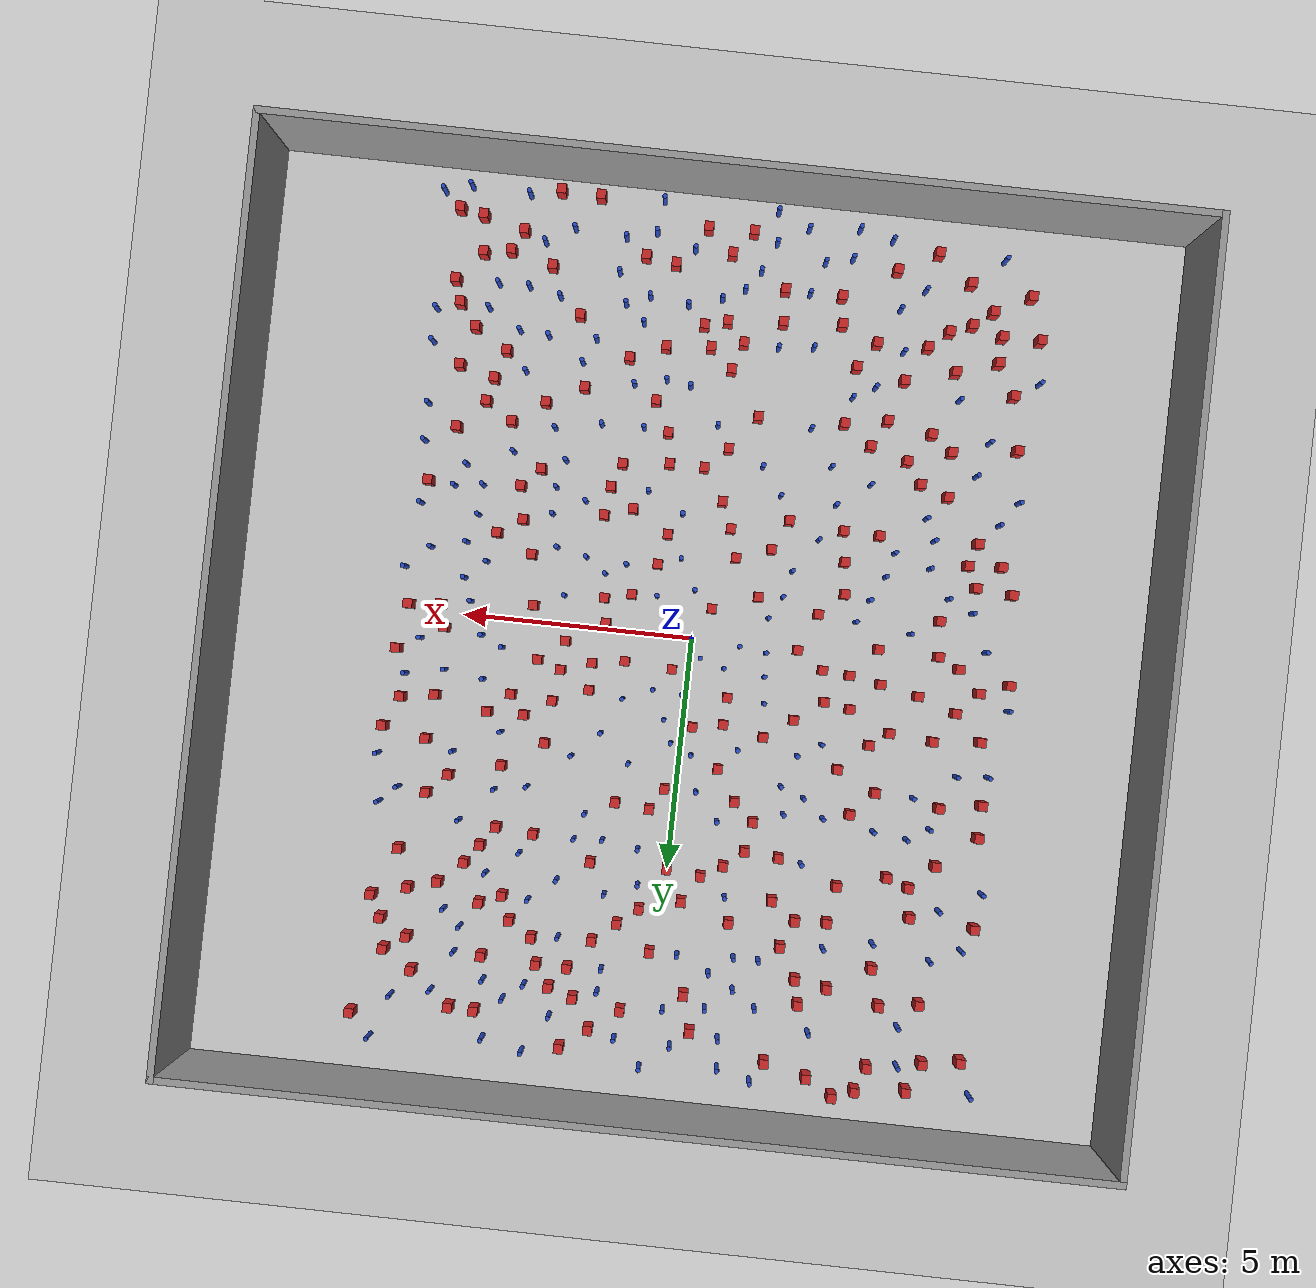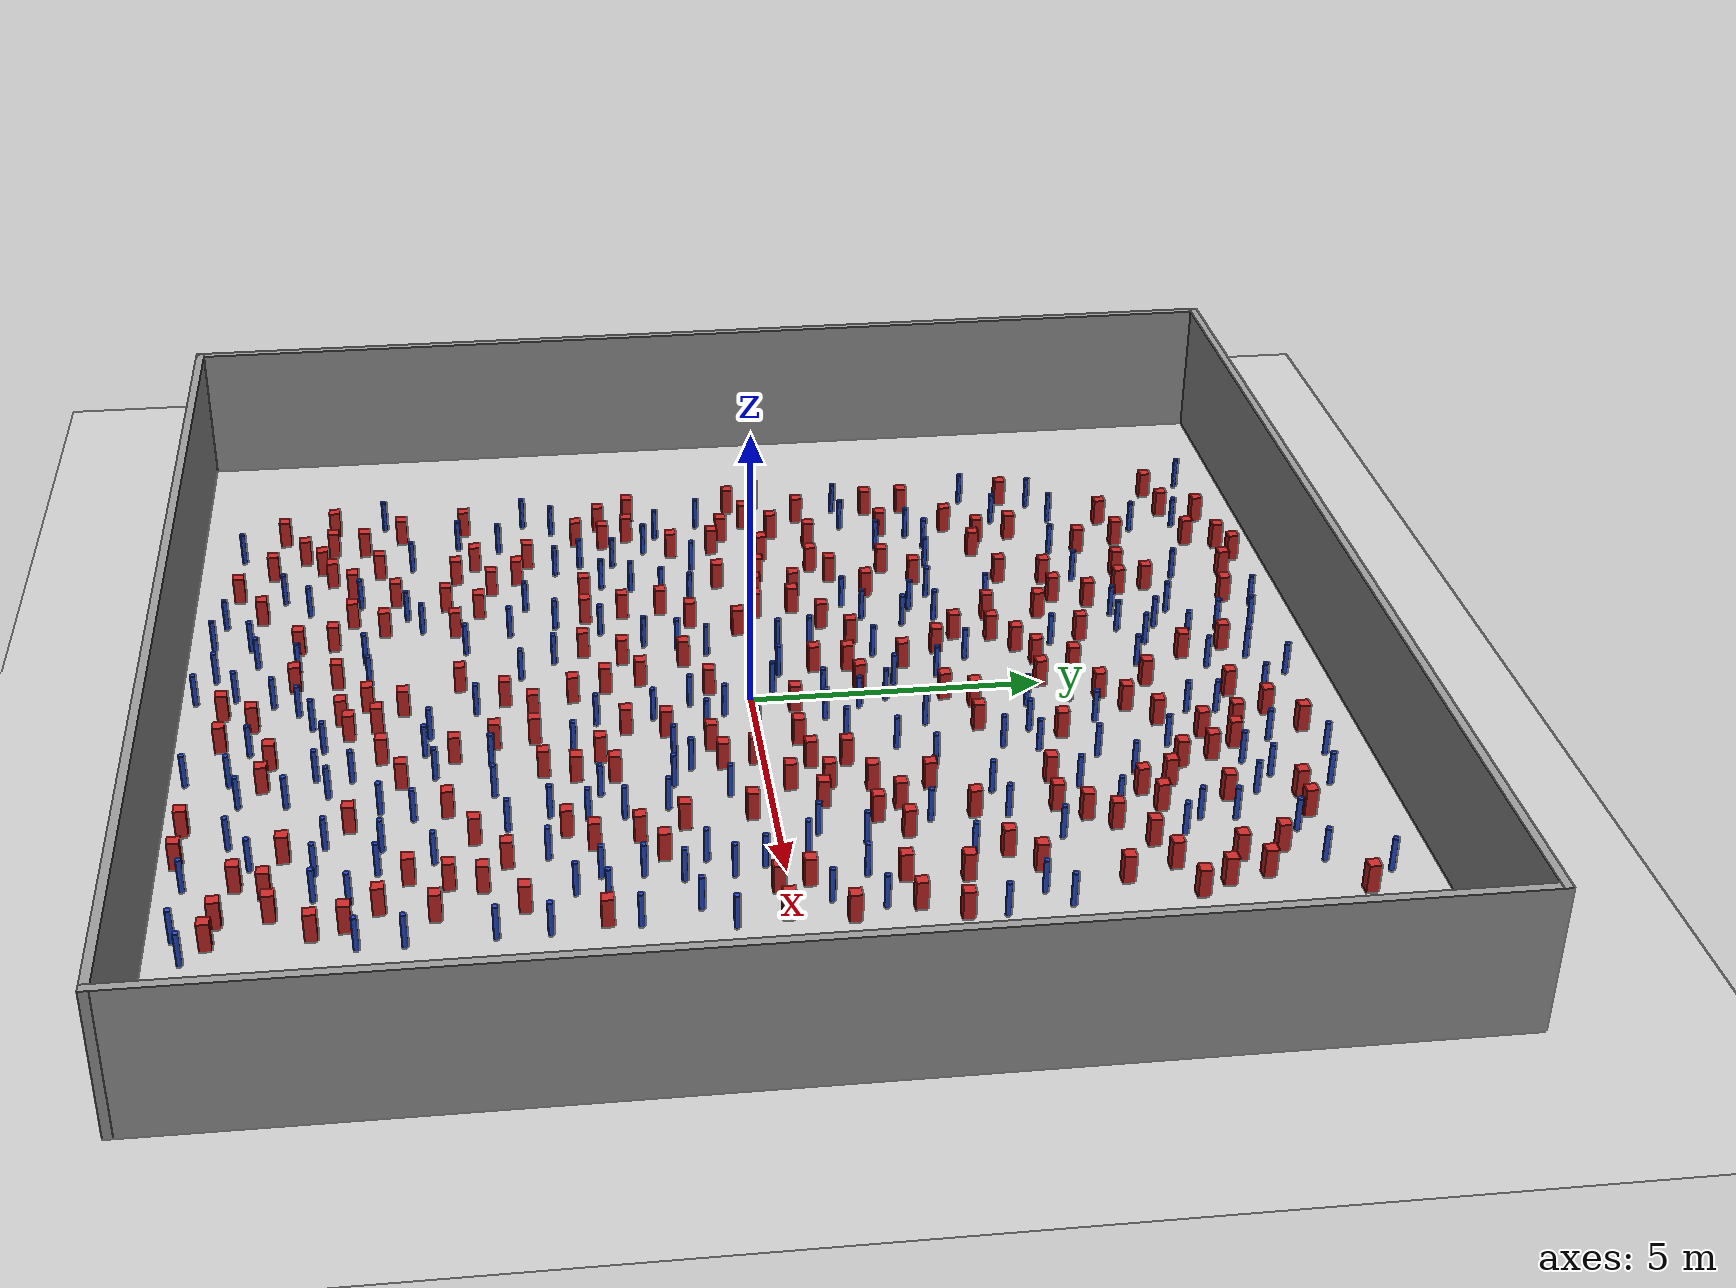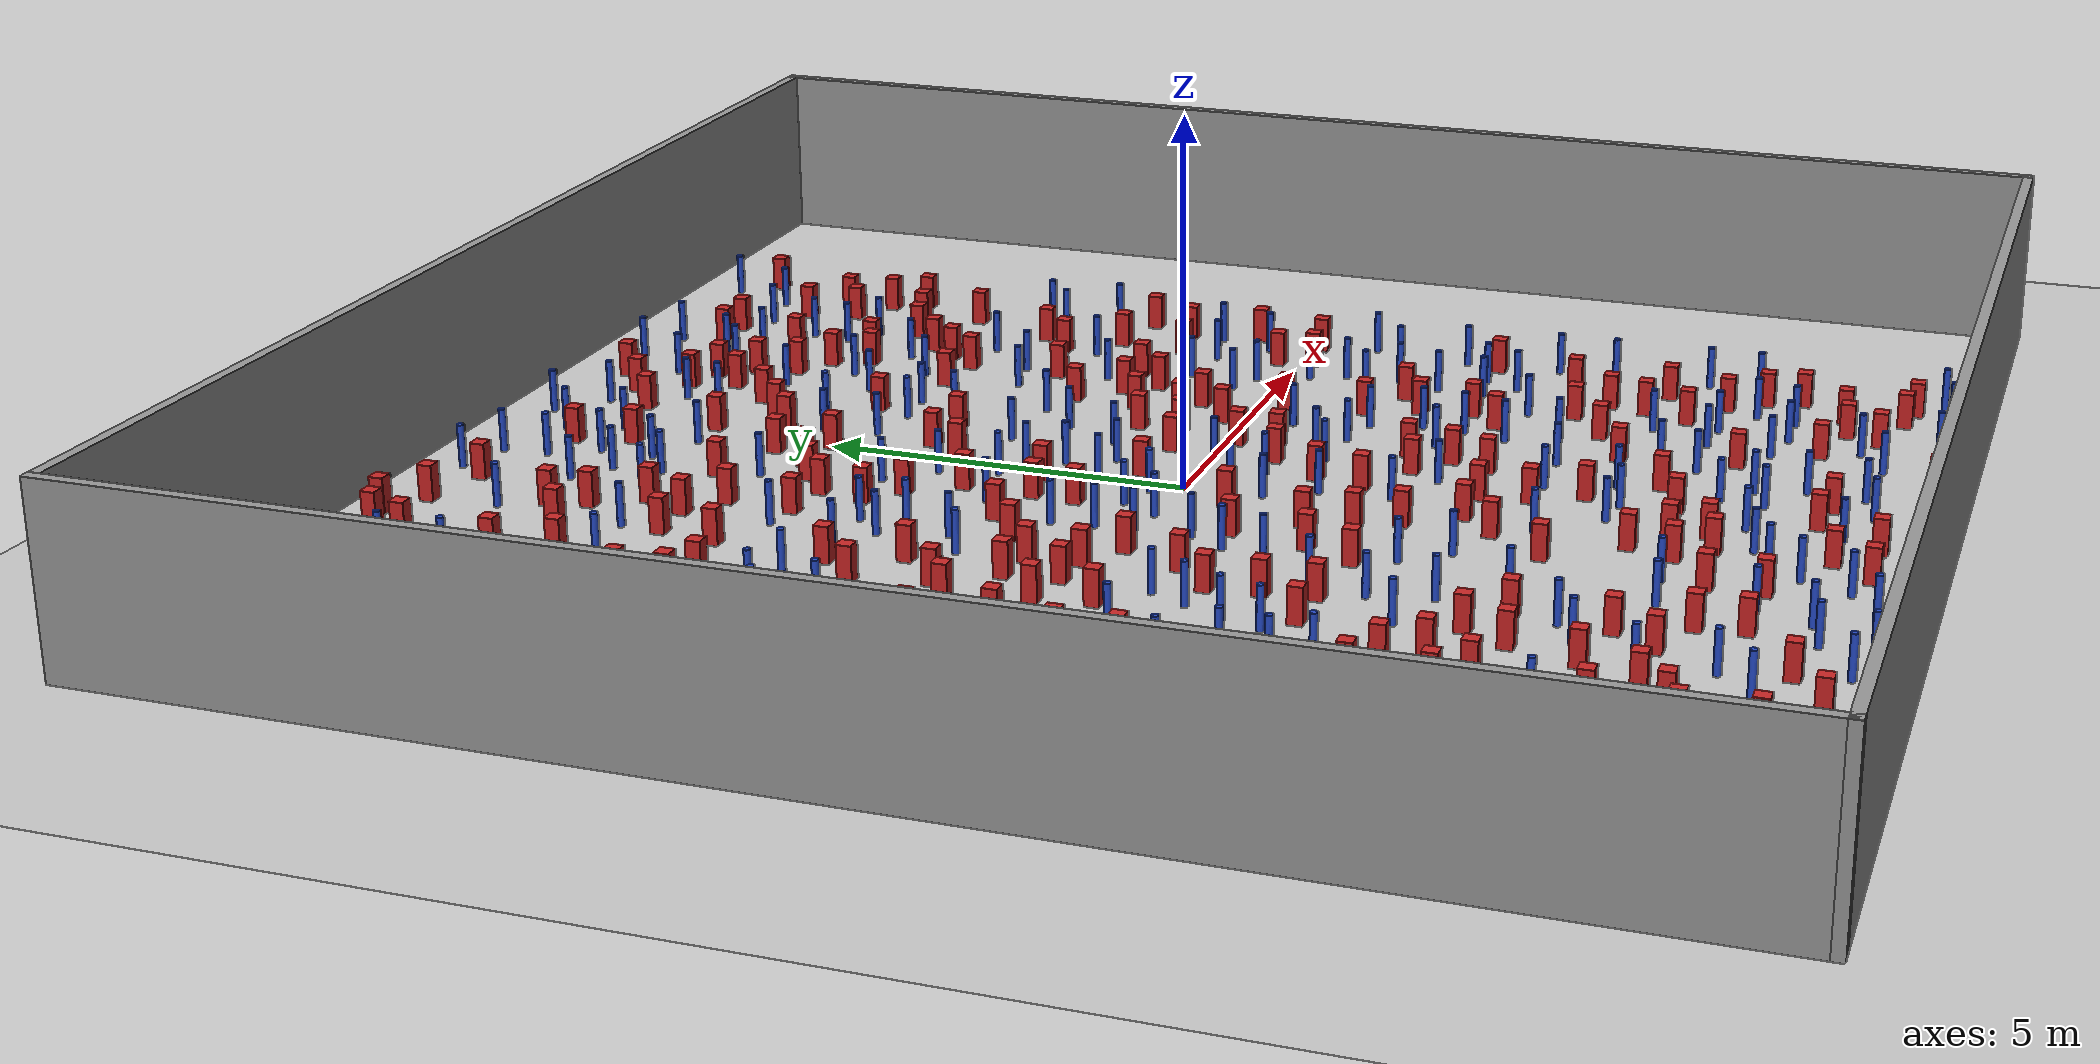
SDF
<sdf version="1.6">
 <world name="default">
  <light name="sun" type="directional">
   <pose>0 0 1000 0 -0 0</pose>
   <diffuse>0.8 0.8 0.8 1</diffuse>
   <specular>0.1 0.1 0.1 1</specular>
   <attenuation>
    <range>1000</range>
    <constant>0.9</constant>
    <linear>0.01</linear>
    <quadratic>0.001</quadratic>
   </attenuation>
   <direction>-0.5 0.5 -1</direction>
  </light>
  <model name="ground_plane">
   <static>1</static>
   <link name="link">
    <collision name="collision">
     <geometry><plane><normal>0 0 1</normal><size>100 100</size></plane></geometry>
     <surface><friction><ode><mu>100</mu><mu2>50</mu2></ode></friction></surface>
    </collision>
    <visual name="visual">
     <cast_shadows>0</cast_shadows>
     <geometry><plane><normal>0 0 1</normal><size>100 100</size></plane></geometry>
     <material>
      <ambient>1.0 1.0 1.0 1.0</ambient>
      <diffuse>0.8 0.8 0.8 1.0</diffuse>
      <specular>0.01 0.01 0.01 1.000000</specular>
     </material>
    </visual>
   </link>
  </model>
  <gravity>0 0 -9.8</gravity>
  <magnetic_field>6e-06 2.3e-05 -4.2e-05</magnetic_field>
  <atmosphere type="adiabatic"/>
  <physics name="default_physics" default="0" type="ode">
   <max_step_size>0.001</max_step_size>
   <real_time_factor>1</real_time_factor>
   <real_time_update_rate>1000</real_time_update_rate>
  </physics>
  <scene><ambient>0.4 0.4 0.4 1</ambient><background>0.7 0.7 0.7 1</background><shadows>1</shadows></scene>
  <spherical_coordinates>
   <surface_model>EARTH_WGS84</surface_model>
   <latitude_deg>0</latitude_deg>
   <longitude_deg>0</longitude_deg>
   <elevation>0</elevation>
   <heading_deg>0</heading_deg>
  </spherical_coordinates>
  <plugin name="gazebo_occupancy_map" filename="libgazebo_2Dmap_plugin.so">
   <map_resolution>0.05</map_resolution>
   <map_topic>generated_map</map_topic>
   <map_height>0.01</map_height>
   <map_size_x>50</map_size_x>
   <map_size_y>50</map_size_y>
  </plugin>
  <model name="NamedLocations">
   <static>true</static>
   <link name="DefaultStart"><pose>8.5 0 0 0 0 3.14</pose></link>
  </model>
  <model name="20x20_walls">
   <pose>0.044518 0.176112 0 0 -0 0</pose>
   <link name="Wall_1">
    <collision name="Wall_1_Collision">
     <geometry><box><size>20 0.15 2.5</size></box></geometry>
     <pose>0 0 1.25 0 -0 0</pose>
    </collision>
    <visual name="Wall_1_Visual">
     <pose>0 0 1.25 0 -0 0</pose>
     <geometry><box><size>20 0.15 2.5</size></box></geometry>
     <material>
      <script><uri>file://media/materials/scripts/gazebo.material</uri><name>Gazebo/Grey</name></script>
      <ambient>0.976471 0.992157 1 1</ambient>
     </material>
     <meta><layer>0</layer></meta>
    </visual>
    <pose>0 9.925 0 0 -0 0</pose>
   </link>
   <link name="Wall_3">
    <collision name="Wall_3_Collision">
     <geometry><box><size>20 0.15 2.5</size></box></geometry>
     <pose>0 0 1.25 0 -0 0</pose>
    </collision>
    <visual name="Wall_3_Visual">
     <pose>0 0 1.25 0 -0 0</pose>
     <geometry><box><size>20 0.15 2.5</size></box></geometry>
     <material>
      <script><uri>file://media/materials/scripts/gazebo.material</uri><name>Gazebo/Grey</name></script>
      <ambient>0.976471 0.992157 1 1</ambient>
     </material>
     <meta><layer>0</layer></meta>
    </visual>
    <pose>9.925 0 0 0 0 -1.5708</pose>
   </link>
   <link name="Wall_4">
    <collision name="Wall_4_Collision">
     <geometry><box><size>20 0.15 2.5</size></box></geometry>
     <pose>0 0 1.25 0 -0 0</pose>
    </collision>
    <visual name="Wall_4_Visual">
     <pose>0 0 1.25 0 -0 0</pose>
     <geometry><box><size>20 0.15 2.5</size></box></geometry>
     <material>
      <script><uri>file://media/materials/scripts/gazebo.material</uri><name>Gazebo/Grey</name></script>
      <ambient>0.976471 0.992157 1 1</ambient>
     </material>
     <meta><layer>0</layer></meta>
    </visual>
    <pose>0 -9.925 0 0 -0 3.14159</pose>
   </link>
   <link name="Wall_5">
    <collision name="Wall_5_Collision">
     <geometry><box><size>20 0.15 2.5</size></box></geometry>
     <pose>0 0 1.25 0 -0 0</pose>
    </collision>
    <visual name="Wall_5_Visual">
     <pose>0 0 1.25 0 -0 0</pose>
     <geometry><box><size>20 0.15 2.5</size></box></geometry>
     <material>
      <script><uri>file://media/materials/scripts/gazebo.material</uri><name>Gazebo/Grey</name></script>
      <ambient>0.976471 0.992157 1 1</ambient>
     </material>
     <meta><layer>0</layer></meta>
    </visual>
    <pose>-9.925 0 0 0 -0 1.5708</pose>
   </link>
   <static>1</static>
  </model>
  <model name="pole_obstacle0">
   <static>true</static>
   <pose>-1.12669661835 7.13284007502 7.38925637345e-09 -8.47170692799e-08 1.24976765033e-08 -1.74513093018e-07</pose>
   <link name="link">
    <pose>0 0 0.3 0 -0 0</pose>
    <inertial>
     <mass>1</mass>
     <inertia><ixx>0.145833</ixx><ixy>0</ixy><ixz>0</ixz><iyy>0.145833</iyy><iyz>0</iyz><izz>0.125</izz></inertia>
    </inertial>
    <collision name="collision">
     <geometry><cylinder><radius>0.05</radius><length>.6</length></cylinder></geometry>
    </collision>
    <visual name="visual">
     <geometry><cylinder><radius>0.05</radius><length>.6</length></cylinder></geometry>
     <material>
      <script><name>Gazebo/Blue</name><uri>file://media/materials/scripts/gazebo.material</uri></script>
     </material>
    </visual>
   </link>
  </model>
  <model name="pole_obstacle1">
   <static>true</static>
   <pose>-1.04630182989 0.051615101523 7.38925637345e-09 -8.47170692799e-08 1.24976765033e-08 -1.74513093019e-07</pose>
   <link name="link">
    <pose>0 0 0.3 0 -0 0</pose>
    <inertial>
     <mass>1</mass>
     <inertia><ixx>0.145833</ixx><ixy>0</ixy><ixz>0</ixz><iyy>0.145833</iyy><iyz>0</iyz><izz>0.125</izz></inertia>
    </inertial>
    <collision name="collision">
     <geometry><cylinder><radius>0.05</radius><length>.6</length></cylinder></geometry>
    </collision>
    <visual name="visual">
     <geometry><cylinder><radius>0.05</radius><length>.6</length></cylinder></geometry>
     <material>
      <script><name>Gazebo/Blue</name><uri>file://media/materials/scripts/gazebo.material</uri></script>
     </material>
    </visual>
   </link>
  </model>
  <model name="square_post_obstacle0">
   <static>true</static>
   <pose>-4.84139513714 -7.20831380337 1.91545236811e-07 -7.35059704564e-06 1.12565212e-07 2.39332434364e-05</pose>
   <link name="link">
    <pose>0 0 0.25 0 -0 0</pose>
    <inertial>
     <mass>100</mass>
     <inertia>
      <ixx>0.166667</ixx>
      <ixy>0</ixy>
      <ixz>0</ixz>
      <iyy>0.166667</iyy>
      <iyz>0</iyz>
      <izz>0.166667</izz>
     </inertia>
    </inertial>
    <collision name="collision"><geometry><box><size>.2 .2 .5</size></box></geometry></collision>
    <visual name="visual">
     <geometry><box><size>.2 .2 .5</size></box></geometry>
     <material>
      <script><name>Gazebo/Red</name><uri>file://media/materials/scripts/gazebo.material</uri></script>
     </material>
    </visual>
   </link>
  </model>
  <model name="square_post_obstacle1">
   <static>true</static>
   <pose>1.39162434271 -0.82237765672 1.91545236811e-07 -7.35059704564e-06 1.12565212e-07 2.39332434364e-05</pose>
   <link name="link">
    <pose>0 0 0.25 0 -0 0</pose>
    <inertial>
     <mass>100</mass>
     <inertia>
      <ixx>0.166667</ixx>
      <ixy>0</ixy>
      <ixz>0</ixz>
      <iyy>0.166667</iyy>
      <iyz>0</iyz>
      <izz>0.166667</izz>
     </inertia>
    </inertial>
    <collision name="collision"><geometry><box><size>.2 .2 .5</size></box></geometry></collision>
    <visual name="visual">
     <geometry><box><size>.2 .2 .5</size></box></geometry>
     <material>
      <script><name>Gazebo/Red</name><uri>file://media/materials/scripts/gazebo.material</uri></script>
     </material>
    </visual>
   </link>
  </model>
  <model name="pole_obstacle2">
   <static>true</static>
   <pose>-4.58328691673 6.12758098638 7.38925637345e-09 -8.47170692796e-08 1.24976764786e-08 -1.74513093032e-07</pose>
   <link name="link">
    <pose>0 0 0.3 0 -0 0</pose>
    <inertial>
     <mass>1</mass>
     <inertia><ixx>0.145833</ixx><ixy>0</ixy><ixz>0</ixz><iyy>0.145833</iyy><iyz>0</iyz><izz>0.125</izz></inertia>
    </inertial>
    <collision name="collision">
     <geometry><cylinder><radius>0.05</radius><length>.6</length></cylinder></geometry>
    </collision>
    <visual name="visual">
     <geometry><cylinder><radius>0.05</radius><length>.6</length></cylinder></geometry>
     <material>
      <script><name>Gazebo/Blue</name><uri>file://media/materials/scripts/gazebo.material</uri></script>
     </material>
    </visual>
   </link>
  </model>
  <model name="pole_obstacle3">
   <static>true</static>
   <pose>-6.9991059545 9.16685258325 7.38925637345e-09 -8.471706928e-08 1.24976765081e-08 -1.74513093015e-07</pose>
   <link name="link">
    <pose>0 0 0.3 0 -0 0</pose>
    <inertial>
     <mass>1</mass>
     <inertia><ixx>0.145833</ixx><ixy>0</ixy><ixz>0</ixz><iyy>0.145833</iyy><iyz>0</iyz><izz>0.125</izz></inertia>
    </inertial>
    <collision name="collision">
     <geometry><cylinder><radius>0.05</radius><length>.6</length></cylinder></geometry>
    </collision>
    <visual name="visual">
     <geometry><cylinder><radius>0.05</radius><length>.6</length></cylinder></geometry>
     <material>
      <script><name>Gazebo/Blue</name><uri>file://media/materials/scripts/gazebo.material</uri></script>
     </material>
    </visual>
   </link>
  </model>
  <model name="pole_obstacle4">
   <static>true</static>
   <pose>6.21301074899 -3.66882229229 7.38925637345e-09 -8.47170692798e-08 1.24976764937e-08 -1.74513093023e-07</pose>
   <link name="link">
    <pose>0 0 0.3 0 -0 0</pose>
    <inertial>
     <mass>1</mass>
     <inertia><ixx>0.145833</ixx><ixy>0</ixy><ixz>0</ixz><iyy>0.145833</iyy><iyz>0</iyz><izz>0.125</izz></inertia>
    </inertial>
    <collision name="collision">
     <geometry><cylinder><radius>0.05</radius><length>.6</length></cylinder></geometry>
    </collision>
    <visual name="visual">
     <geometry><cylinder><radius>0.05</radius><length>.6</length></cylinder></geometry>
     <material>
      <script><name>Gazebo/Blue</name><uri>file://media/materials/scripts/gazebo.material</uri></script>
     </material>
    </visual>
   </link>
  </model>
  <model name="pole_obstacle5">
   <static>true</static>
   <pose>0.122949618558 -7.40408412698 7.38925637345e-09 -8.47170692799e-08 1.2497676504e-08 -1.74513093019e-07</pose>
   <link name="link">
    <pose>0 0 0.3 0 -0 0</pose>
    <inertial>
     <mass>1</mass>
     <inertia><ixx>0.145833</ixx><ixy>0</ixy><ixz>0</ixz><iyy>0.145833</iyy><iyz>0</iyz><izz>0.125</izz></inertia>
    </inertial>
    <collision name="collision">
     <geometry><cylinder><radius>0.05</radius><length>.6</length></cylinder></geometry>
    </collision>
    <visual name="visual">
     <geometry><cylinder><radius>0.05</radius><length>.6</length></cylinder></geometry>
     <material>
      <script><name>Gazebo/Blue</name><uri>file://media/materials/scripts/gazebo.material</uri></script>
     </material>
    </visual>
   </link>
  </model>
  <model name="pole_obstacle6">
   <static>true</static>
   <pose>3.78003277842 -6.20220174582 7.38925637345e-09 -8.47170692798e-08 1.24976765033e-08 -1.74513093019e-07</pose>
   <link name="link">
    <pose>0 0 0.3 0 -0 0</pose>
    <inertial>
     <mass>1</mass>
     <inertia><ixx>0.145833</ixx><ixy>0</ixy><ixz>0</ixz><iyy>0.145833</iyy><iyz>0</iyz><izz>0.125</izz></inertia>
    </inertial>
    <collision name="collision">
     <geometry><cylinder><radius>0.05</radius><length>.6</length></cylinder></geometry>
    </collision>
    <visual name="visual">
     <geometry><cylinder><radius>0.05</radius><length>.6</length></cylinder></geometry>
     <material>
      <script><name>Gazebo/Blue</name><uri>file://media/materials/scripts/gazebo.material</uri></script>
     </material>
    </visual>
   </link>
  </model>
  <model name="square_post_obstacle2">
   <static>true</static>
   <pose>-6.94276539703 0.270544642527 1.91545236811e-07 -7.35059704564e-06 1.12565212e-07 2.39332434364e-05</pose>
   <link name="link">
    <pose>0 0 0.25 0 -0 0</pose>
    <inertial>
     <mass>100</mass>
     <inertia>
      <ixx>0.166667</ixx>
      <ixy>0</ixy>
      <ixz>0</ixz>
      <iyy>0.166667</iyy>
      <iyz>0</iyz>
      <izz>0.166667</izz>
     </inertia>
    </inertial>
    <collision name="collision"><geometry><box><size>.2 .2 .5</size></box></geometry></collision>
    <visual name="visual">
     <geometry><box><size>.2 .2 .5</size></box></geometry>
     <material>
      <script><name>Gazebo/Red</name><uri>file://media/materials/scripts/gazebo.material</uri></script>
     </material>
    </visual>
   </link>
  </model>
  <model name="square_post_obstacle3">
   <static>true</static>
   <pose>1.32995403728 8.61130214295 1.91545236811e-07 -7.35059704564e-06 1.12565212e-07 2.39332434364e-05</pose>
   <link name="link">
    <pose>0 0 0.25 0 -0 0</pose>
    <inertial>
     <mass>100</mass>
     <inertia>
      <ixx>0.166667</ixx>
      <ixy>0</ixy>
      <ixz>0</ixz>
      <iyy>0.166667</iyy>
      <iyz>0</iyz>
      <izz>0.166667</izz>
     </inertia>
    </inertial>
    <collision name="collision"><geometry><box><size>.2 .2 .5</size></box></geometry></collision>
    <visual name="visual">
     <geometry><box><size>.2 .2 .5</size></box></geometry>
     <material>
      <script><name>Gazebo/Red</name><uri>file://media/materials/scripts/gazebo.material</uri></script>
     </material>
    </visual>
   </link>
  </model>
  <model name="square_post_obstacle4">
   <static>true</static>
   <pose>0.98054277704 -4.38491945527 1.91545236811e-07 -7.35059704564e-06 1.12565212e-07 2.39332434364e-05</pose>
   <link name="link">
    <pose>0 0 0.25 0 -0 0</pose>
    <inertial>
     <mass>100</mass>
     <inertia>
      <ixx>0.166667</ixx>
      <ixy>0</ixy>
      <ixz>0</ixz>
      <iyy>0.166667</iyy>
      <iyz>0</iyz>
      <izz>0.166667</izz>
     </inertia>
    </inertial>
    <collision name="collision"><geometry><box><size>.2 .2 .5</size></box></geometry></collision>
    <visual name="visual">
     <geometry><box><size>.2 .2 .5</size></box></geometry>
     <material>
      <script><name>Gazebo/Red</name><uri>file://media/materials/scripts/gazebo.material</uri></script>
     </material>
    </visual>
   </link>
  </model>
  <model name="pole_obstacle7">
   <static>true</static>
   <pose>3.11099969487 -1.66770856473 7.38925637345e-09 -8.471706928e-08 1.24976765152e-08 -1.74513093012e-07</pose>
   <link name="link">
    <pose>0 0 0.3 0 -0 0</pose>
    <inertial>
     <mass>1</mass>
     <inertia><ixx>0.145833</ixx><ixy>0</ixy><ixz>0</ixz><iyy>0.145833</iyy><iyz>0</iyz><izz>0.125</izz></inertia>
    </inertial>
    <collision name="collision">
     <geometry><cylinder><radius>0.05</radius><length>.6</length></cylinder></geometry>
    </collision>
    <visual name="visual">
     <geometry><cylinder><radius>0.05</radius><length>.6</length></cylinder></geometry>
     <material>
      <script><name>Gazebo/Blue</name><uri>file://media/materials/scripts/gazebo.material</uri></script>
     </material>
    </visual>
   </link>
  </model>
  <model name="pole_obstacle8">
   <static>true</static>
   <pose>2.19112307068 -7.08006629807 7.38925637345e-09 -8.47170692798e-08 1.24976765033e-08 -1.74513093019e-07</pose>
   <link name="link">
    <pose>0 0 0.3 0 -0 0</pose>
    <inertial>
     <mass>1</mass>
     <inertia><ixx>0.145833</ixx><ixy>0</ixy><ixz>0</ixz><iyy>0.145833</iyy><iyz>0</iyz><izz>0.125</izz></inertia>
    </inertial>
    <collision name="collision">
     <geometry><cylinder><radius>0.05</radius><length>.6</length></cylinder></geometry>
    </collision>
    <visual name="visual">
     <geometry><cylinder><radius>0.05</radius><length>.6</length></cylinder></geometry>
     <material>
      <script><name>Gazebo/Blue</name><uri>file://media/materials/scripts/gazebo.material</uri></script>
     </material>
    </visual>
   </link>
  </model>
  <model name="square_post_obstacle5">
   <static>true</static>
   <pose>3.76848859604 4.4891068602 1.91545236811e-07 -7.35059704564e-06 1.12565212e-07 2.39332434364e-05</pose>
   <link name="link">
    <pose>0 0 0.25 0 -0 0</pose>
    <inertial>
     <mass>100</mass>
     <inertia>
      <ixx>0.166667</ixx>
      <ixy>0</ixy>
      <ixz>0</ixz>
      <iyy>0.166667</iyy>
      <iyz>0</iyz>
      <izz>0.166667</izz>
     </inertia>
    </inertial>
    <collision name="collision"><geometry><box><size>.2 .2 .5</size></box></geometry></collision>
    <visual name="visual">
     <geometry><box><size>.2 .2 .5</size></box></geometry>
     <material>
      <script><name>Gazebo/Red</name><uri>file://media/materials/scripts/gazebo.material</uri></script>
     </material>
    </visual>
   </link>
  </model>
  <model name="square_post_obstacle6">
   <static>true</static>
   <pose>-6.61166386584 3.61637795309 1.91545236811e-07 -7.35059704564e-06 1.12565212e-07 2.39332434364e-05</pose>
   <link name="link">
    <pose>0 0 0.25 0 -0 0</pose>
    <inertial>
     <mass>100</mass>
     <inertia>
      <ixx>0.166667</ixx>
      <ixy>0</ixy>
      <ixz>0</ixz>
      <iyy>0.166667</iyy>
      <iyz>0</iyz>
      <izz>0.166667</izz>
     </inertia>
    </inertial>
    <collision name="collision"><geometry><box><size>.2 .2 .5</size></box></geometry></collision>
    <visual name="visual">
     <geometry><box><size>.2 .2 .5</size></box></geometry>
     <material>
      <script><name>Gazebo/Red</name><uri>file://media/materials/scripts/gazebo.material</uri></script>
     </material>
    </visual>
   </link>
  </model>
  <model name="square_post_obstacle7">
   <static>true</static>
   <pose>6.16536522691 -0.108936220135 1.91545236811e-07 -7.35059704564e-06 1.12565212e-07 2.39332434364e-05</pose>
   <link name="link">
    <pose>0 0 0.25 0 -0 0</pose>
    <inertial>
     <mass>100</mass>
     <inertia>
      <ixx>0.166667</ixx>
      <ixy>0</ixy>
      <ixz>0</ixz>
      <iyy>0.166667</iyy>
      <iyz>0</iyz>
      <izz>0.166667</izz>
     </inertia>
    </inertial>
    <collision name="collision"><geometry><box><size>.2 .2 .5</size></box></geometry></collision>
    <visual name="visual">
     <geometry><box><size>.2 .2 .5</size></box></geometry>
     <material>
      <script><name>Gazebo/Red</name><uri>file://media/materials/scripts/gazebo.material</uri></script>
     </material>
    </visual>
   </link>
  </model>
  <model name="pole_obstacle9">
   <static>true</static>
   <pose>-4.34505185968 3.72447825318 7.38925637345e-09 -8.47170692798e-08 1.24976764937e-08 -1.74513093023e-07</pose>
   <link name="link">
    <pose>0 0 0.3 0 -0 0</pose>
    <inertial>
     <mass>1</mass>
     <inertia><ixx>0.145833</ixx><ixy>0</ixy><ixz>0</ixz><iyy>0.145833</iyy><iyz>0</iyz><izz>0.125</izz></inertia>
    </inertial>
    <collision name="collision">
     <geometry><cylinder><radius>0.05</radius><length>.6</length></cylinder></geometry>
    </collision>
    <visual name="visual">
     <geometry><cylinder><radius>0.05</radius><length>.6</length></cylinder></geometry>
     <material>
      <script><name>Gazebo/Blue</name><uri>file://media/materials/scripts/gazebo.material</uri></script>
     </material>
    </visual>
   </link>
  </model>
  <model name="pole_obstacle10">
   <static>true</static>
   <pose>-5.38365069876 8.69273519656 7.38925637345e-09 -8.471706928e-08 1.24976765081e-08 -1.74513093015e-07</pose>
   <link name="link">
    <pose>0 0 0.3 0 -0 0</pose>
    <inertial>
     <mass>1</mass>
     <inertia><ixx>0.145833</ixx><ixy>0</ixy><ixz>0</ixz><iyy>0.145833</iyy><iyz>0</iyz><izz>0.125</izz></inertia>
    </inertial>
    <collision name="collision">
     <geometry><cylinder><radius>0.05</radius><length>.6</length></cylinder></geometry>
    </collision>
    <visual name="visual">
     <geometry><cylinder><radius>0.05</radius><length>.6</length></cylinder></geometry>
     <material>
      <script><name>Gazebo/Blue</name><uri>file://media/materials/scripts/gazebo.material</uri></script>
     </material>
    </visual>
   </link>
  </model>
  <model name="pole_obstacle11">
   <static>true</static>
   <pose>5.98170943575 3.84576997254 7.38925637345e-09 -8.47170692798e-08 1.24976764937e-08 -1.74513093023e-07</pose>
   <link name="link">
    <pose>0 0 0.3 0 -0 0</pose>
    <inertial>
     <mass>1</mass>
     <inertia><ixx>0.145833</ixx><ixy>0</ixy><ixz>0</ixz><iyy>0.145833</iyy><iyz>0</iyz><izz>0.125</izz></inertia>
    </inertial>
    <collision name="collision">
     <geometry><cylinder><radius>0.05</radius><length>.6</length></cylinder></geometry>
    </collision>
    <visual name="visual">
     <geometry><cylinder><radius>0.05</radius><length>.6</length></cylinder></geometry>
     <material>
      <script><name>Gazebo/Blue</name><uri>file://media/materials/scripts/gazebo.material</uri></script>
     </material>
    </visual>
   </link>
  </model>
  <model name="pole_obstacle12">
   <static>true</static>
   <pose>4.30949091186 -7.22254157905 7.38925637345e-09 -8.47170692796e-08 1.24976764786e-08 -1.74513093032e-07</pose>
   <link name="link">
    <pose>0 0 0.3 0 -0 0</pose>
    <inertial>
     <mass>1</mass>
     <inertia><ixx>0.145833</ixx><ixy>0</ixy><ixz>0</ixz><iyy>0.145833</iyy><iyz>0</iyz><izz>0.125</izz></inertia>
    </inertial>
    <collision name="collision">
     <geometry><cylinder><radius>0.05</radius><length>.6</length></cylinder></geometry>
    </collision>
    <visual name="visual">
     <geometry><cylinder><radius>0.05</radius><length>.6</length></cylinder></geometry>
     <material>
      <script><name>Gazebo/Blue</name><uri>file://media/materials/scripts/gazebo.material</uri></script>
     </material>
    </visual>
   </link>
  </model>
  <model name="square_post_obstacle8">
   <static>true</static>
   <pose>0.52185416256 3.75010447684 1.91545236811e-07 -7.35059704564e-06 1.12565212e-07 2.39332434364e-05</pose>
   <link name="link">
    <pose>0 0 0.25 0 -0 0</pose>
    <inertial>
     <mass>100</mass>
     <inertia>
      <ixx>0.166667</ixx>
      <ixy>0</ixy>
      <ixz>0</ixz>
      <iyy>0.166667</iyy>
      <iyz>0</iyz>
      <izz>0.166667</izz>
     </inertia>
    </inertial>
    <collision name="collision"><geometry><box><size>.2 .2 .5</size></box></geometry></collision>
    <visual name="visual">
     <geometry><box><size>.2 .2 .5</size></box></geometry>
     <material>
      <script><name>Gazebo/Red</name><uri>file://media/materials/scripts/gazebo.material</uri></script>
     </material>
    </visual>
   </link>
  </model>
  <model name="square_post_obstacle9">
   <static>true</static>
   <pose>4.37427200818 5.32072493143 1.91545236811e-07 -7.35059704564e-06 1.12565212e-07 2.39332434364e-05</pose>
   <link name="link">
    <pose>0 0 0.25 0 -0 0</pose>
    <inertial>
     <mass>100</mass>
     <inertia>
      <ixx>0.166667</ixx>
      <ixy>0</ixy>
      <ixz>0</ixz>
      <iyy>0.166667</iyy>
      <iyz>0</iyz>
      <izz>0.166667</izz>
     </inertia>
    </inertial>
    <collision name="collision"><geometry><box><size>.2 .2 .5</size></box></geometry></collision>
    <visual name="visual">
     <geometry><box><size>.2 .2 .5</size></box></geometry>
     <material>
      <script><name>Gazebo/Red</name><uri>file://media/materials/scripts/gazebo.material</uri></script>
     </material>
    </visual>
   </link>
  </model>
  <model name="pole_obstacle13">
   <static>true</static>
   <pose>-3.74267223954 -7.58555158049 7.38925637345e-09 -8.47170692794e-08 1.24976764468e-08 -1.7451309304e-07</pose>
   <link name="link">
    <pose>0 0 0.3 0 -0 0</pose>
    <inertial>
     <mass>1</mass>
     <inertia><ixx>0.145833</ixx><ixy>0</ixy><ixz>0</ixz><iyy>0.145833</iyy><iyz>0</iyz><izz>0.125</izz></inertia>
    </inertial>
    <collision name="collision">
     <geometry><cylinder><radius>0.05</radius><length>.6</length></cylinder></geometry>
    </collision>
    <visual name="visual">
     <geometry><cylinder><radius>0.05</radius><length>.6</length></cylinder></geometry>
     <material>
      <script><name>Gazebo/Blue</name><uri>file://media/materials/scripts/gazebo.material</uri></script>
     </material>
    </visual>
   </link>
  </model>
  <model name="square_post_obstacle10">
   <static>true</static>
   <pose>4.84833667584 -5.16432378492 1.91545236811e-07 -7.35059704564e-06 1.12565212e-07 2.39332434364e-05</pose>
   <link name="link">
    <pose>0 0 0.25 0 -0 0</pose>
    <inertial>
     <mass>100</mass>
     <inertia>
      <ixx>0.166667</ixx>
      <ixy>0</ixy>
      <ixz>0</ixz>
      <iyy>0.166667</iyy>
      <iyz>0</iyz>
      <izz>0.166667</izz>
     </inertia>
    </inertial>
    <collision name="collision"><geometry><box><size>.2 .2 .5</size></box></geometry></collision>
    <visual name="visual">
     <geometry><box><size>.2 .2 .5</size></box></geometry>
     <material>
      <script><name>Gazebo/Red</name><uri>file://media/materials/scripts/gazebo.material</uri></script>
     </material>
    </visual>
   </link>
  </model>
  <model name="square_post_obstacle11">
   <static>true</static>
   <pose>-4.04240728268 9.49389917569 1.91545236811e-07 -7.35059704564e-06 1.12565212e-07 2.39332434364e-05</pose>
   <link name="link">
    <pose>0 0 0.25 0 -0 0</pose>
    <inertial>
     <mass>100</mass>
     <inertia>
      <ixx>0.166667</ixx>
      <ixy>0</ixy>
      <ixz>0</ixz>
      <iyy>0.166667</iyy>
      <iyz>0</iyz>
      <izz>0.166667</izz>
     </inertia>
    </inertial>
    <collision name="collision"><geometry><box><size>.2 .2 .5</size></box></geometry></collision>
    <visual name="visual">
     <geometry><box><size>.2 .2 .5</size></box></geometry>
     <material>
      <script><name>Gazebo/Red</name><uri>file://media/materials/scripts/gazebo.material</uri></script>
     </material>
    </visual>
   </link>
  </model>
  <model name="pole_obstacle14">
   <static>true</static>
   <pose>-1.5881915695 -3.29287273544 7.38925637345e-09 -8.47170692799e-08 1.24976765053e-08 -1.74513093017e-07</pose>
   <link name="link">
    <pose>0 0 0.3 0 -0 0</pose>
    <inertial>
     <mass>1</mass>
     <inertia><ixx>0.145833</ixx><ixy>0</ixy><ixz>0</ixz><iyy>0.145833</iyy><iyz>0</iyz><izz>0.125</izz></inertia>
    </inertial>
    <collision name="collision">
     <geometry><cylinder><radius>0.05</radius><length>.6</length></cylinder></geometry>
    </collision>
    <visual name="visual">
     <geometry><cylinder><radius>0.05</radius><length>.6</length></cylinder></geometry>
     <material>
      <script><name>Gazebo/Blue</name><uri>file://media/materials/scripts/gazebo.material</uri></script>
     </material>
    </visual>
   </link>
  </model>
  <model name="pole_obstacle15">
   <static>true</static>
   <pose>-3.52819994219 6.34154515081 7.38925637345e-09 -8.47170692798e-08 1.24976765033e-08 -1.74513093019e-07</pose>
   <link name="link">
    <pose>0 0 0.3 0 -0 0</pose>
    <inertial>
     <mass>1</mass>
     <inertia><ixx>0.145833</ixx><ixy>0</ixy><ixz>0</ixz><iyy>0.145833</iyy><iyz>0</iyz><izz>0.125</izz></inertia>
    </inertial>
    <collision name="collision">
     <geometry><cylinder><radius>0.05</radius><length>.6</length></cylinder></geometry>
    </collision>
    <visual name="visual">
     <geometry><cylinder><radius>0.05</radius><length>.6</length></cylinder></geometry>
     <material>
      <script><name>Gazebo/Blue</name><uri>file://media/materials/scripts/gazebo.material</uri></script>
     </material>
    </visual>
   </link>
  </model>
  <model name="square_post_obstacle12">
   <static>true</static>
   <pose>5.54659777627 -4.02996502234 1.91545236811e-07 -7.35059704564e-06 1.12565212e-07 2.39332434364e-05</pose>
   <link name="link">
    <pose>0 0 0.25 0 -0 0</pose>
    <inertial>
     <mass>100</mass>
     <inertia>
      <ixx>0.166667</ixx>
      <ixy>0</ixy>
      <ixz>0</ixz>
      <iyy>0.166667</iyy>
      <iyz>0</iyz>
      <izz>0.166667</izz>
     </inertia>
    </inertial>
    <collision name="collision"><geometry><box><size>.2 .2 .5</size></box></geometry></collision>
    <visual name="visual">
     <geometry><box><size>.2 .2 .5</size></box></geometry>
     <material>
      <script><name>Gazebo/Red</name><uri>file://media/materials/scripts/gazebo.material</uri></script>
     </material>
    </visual>
   </link>
  </model>
  <model name="pole_obstacle16">
   <static>true</static>
   <pose>1.68132162129 -8.68840192104 7.38925637345e-09 -8.47170692798e-08 1.24976764881e-08 -1.74513093027e-07</pose>
   <link name="link">
    <pose>0 0 0.3 0 -0 0</pose>
    <inertial>
     <mass>1</mass>
     <inertia><ixx>0.145833</ixx><ixy>0</ixy><ixz>0</ixz><iyy>0.145833</iyy><iyz>0</iyz><izz>0.125</izz></inertia>
    </inertial>
    <collision name="collision">
     <geometry><cylinder><radius>0.05</radius><length>.6</length></cylinder></geometry>
    </collision>
    <visual name="visual">
     <geometry><cylinder><radius>0.05</radius><length>.6</length></cylinder></geometry>
     <material>
      <script><name>Gazebo/Blue</name><uri>file://media/materials/scripts/gazebo.material</uri></script>
     </material>
    </visual>
   </link>
  </model>
  <model name="pole_obstacle17">
   <static>true</static>
   <pose>-3.39878785929 8.18392674902 7.38925637345e-09 -8.47170692793e-08 1.24976764408e-08 -1.74513093041e-07</pose>
   <link name="link">
    <pose>0 0 0.3 0 -0 0</pose>
    <inertial>
     <mass>1</mass>
     <inertia><ixx>0.145833</ixx><ixy>0</ixy><ixz>0</ixz><iyy>0.145833</iyy><iyz>0</iyz><izz>0.125</izz></inertia>
    </inertial>
    <collision name="collision">
     <geometry><cylinder><radius>0.05</radius><length>.6</length></cylinder></geometry>
    </collision>
    <visual name="visual">
     <geometry><cylinder><radius>0.05</radius><length>.6</length></cylinder></geometry>
     <material>
      <script><name>Gazebo/Blue</name><uri>file://media/materials/scripts/gazebo.material</uri></script>
     </material>
    </visual>
   </link>
  </model>
  <model name="square_post_obstacle13">
   <static>true</static>
   <pose>4.9184155626 3.47502278564 1.91545236811e-07 -7.35059704564e-06 1.12565212e-07 2.39332434364e-05</pose>
   <link name="link">
    <pose>0 0 0.25 0 -0 0</pose>
    <inertial>
     <mass>100</mass>
     <inertia>
      <ixx>0.166667</ixx>
      <ixy>0</ixy>
      <ixz>0</ixz>
      <iyy>0.166667</iyy>
      <iyz>0</iyz>
      <izz>0.166667</izz>
     </inertia>
    </inertial>
    <collision name="collision"><geometry><box><size>.2 .2 .5</size></box></geometry></collision>
    <visual name="visual">
     <geometry><box><size>.2 .2 .5</size></box></geometry>
     <material>
      <script><name>Gazebo/Red</name><uri>file://media/materials/scripts/gazebo.material</uri></script>
     </material>
    </visual>
   </link>
  </model>
  <model name="pole_obstacle18">
   <static>true</static>
   <pose>6.14882844056 -2.31937417881 7.38925637345e-09 -8.47170692798e-08 1.24976764937e-08 -1.74513093023e-07</pose>
   <link name="link">
    <pose>0 0 0.3 0 -0 0</pose>
    <inertial>
     <mass>1</mass>
     <inertia><ixx>0.145833</ixx><ixy>0</ixy><ixz>0</ixz><iyy>0.145833</iyy><iyz>0</iyz><izz>0.125</izz></inertia>
    </inertial>
    <collision name="collision">
     <geometry><cylinder><radius>0.05</radius><length>.6</length></cylinder></geometry>
    </collision>
    <visual name="visual">
     <geometry><cylinder><radius>0.05</radius><length>.6</length></cylinder></geometry>
     <material>
      <script><name>Gazebo/Blue</name><uri>file://media/materials/scripts/gazebo.material</uri></script>
     </material>
    </visual>
   </link>
  </model>
  <model name="square_post_obstacle14">
   <static>true</static>
   <pose>5.47820573475 -0.178806485754 1.91545236811e-07 -7.35059704564e-06 1.12565212e-07 2.39332434364e-05</pose>
   <link name="link">
    <pose>0 0 0.25 0 -0 0</pose>
    <inertial>
     <mass>100</mass>
     <inertia>
      <ixx>0.166667</ixx>
      <ixy>0</ixy>
      <ixz>0</ixz>
      <iyy>0.166667</iyy>
      <iyz>0</iyz>
      <izz>0.166667</izz>
     </inertia>
    </inertial>
    <collision name="collision"><geometry><box><size>.2 .2 .5</size></box></geometry></collision>
    <visual name="visual">
     <geometry><box><size>.2 .2 .5</size></box></geometry>
     <material>
      <script><name>Gazebo/Red</name><uri>file://media/materials/scripts/gazebo.material</uri></script>
     </material>
    </visual>
   </link>
  </model>
  <model name="pole_obstacle19">
   <static>true</static>
   <pose>5.4659101651 -2.76664875907 7.38925637345e-09 -8.47170692798e-08 1.24976764937e-08 -1.74513093023e-07</pose>
   <link name="link">
    <pose>0 0 0.3 0 -0 0</pose>
    <inertial>
     <mass>1</mass>
     <inertia><ixx>0.145833</ixx><ixy>0</ixy><ixz>0</ixz><iyy>0.145833</iyy><iyz>0</iyz><izz>0.125</izz></inertia>
    </inertial>
    <collision name="collision">
     <geometry><cylinder><radius>0.05</radius><length>.6</length></cylinder></geometry>
    </collision>
    <visual name="visual">
     <geometry><cylinder><radius>0.05</radius><length>.6</length></cylinder></geometry>
     <material>
      <script><name>Gazebo/Blue</name><uri>file://media/materials/scripts/gazebo.material</uri></script>
     </material>
    </visual>
   </link>
  </model>
  <model name="square_post_obstacle15">
   <static>true</static>
   <pose>3.79252274136 7.28375643206 1.91545236811e-07 -7.35059704564e-06 1.12565212e-07 2.39332434364e-05</pose>
   <link name="link">
    <pose>0 0 0.25 0 -0 0</pose>
    <inertial>
     <mass>100</mass>
     <inertia>
      <ixx>0.166667</ixx>
      <ixy>0</ixy>
      <ixz>0</ixz>
      <iyy>0.166667</iyy>
      <iyz>0</iyz>
      <izz>0.166667</izz>
     </inertia>
    </inertial>
    <collision name="collision"><geometry><box><size>.2 .2 .5</size></box></geometry></collision>
    <visual name="visual">
     <geometry><box><size>.2 .2 .5</size></box></geometry>
     <material>
      <script><name>Gazebo/Red</name><uri>file://media/materials/scripts/gazebo.material</uri></script>
     </material>
    </visual>
   </link>
  </model>
  <model name="square_post_obstacle16">
   <static>true</static>
   <pose>3.63317559832 -1.45241248531 1.91545236811e-07 -7.35059704564e-06 1.12565212e-07 2.39332434364e-05</pose>
   <link name="link">
    <pose>0 0 0.25 0 -0 0</pose>
    <inertial>
     <mass>100</mass>
     <inertia>
      <ixx>0.166667</ixx>
      <ixy>0</ixy>
      <ixz>0</ixz>
      <iyy>0.166667</iyy>
      <iyz>0</iyz>
      <izz>0.166667</izz>
     </inertia>
    </inertial>
    <collision name="collision"><geometry><box><size>.2 .2 .5</size></box></geometry></collision>
    <visual name="visual">
     <geometry><box><size>.2 .2 .5</size></box></geometry>
     <material>
      <script><name>Gazebo/Red</name><uri>file://media/materials/scripts/gazebo.material</uri></script>
     </material>
    </visual>
   </link>
  </model>
  <model name="square_post_obstacle17">
   <static>true</static>
   <pose>3.96532546582 6.1500377641 1.91545236811e-07 -7.35059704564e-06 1.12565212e-07 2.39332434364e-05</pose>
   <link name="link">
    <pose>0 0 0.25 0 -0 0</pose>
    <inertial>
     <mass>100</mass>
     <inertia>
      <ixx>0.166667</ixx>
      <ixy>0</ixy>
      <ixz>0</ixz>
      <iyy>0.166667</iyy>
      <iyz>0</iyz>
      <izz>0.166667</izz>
     </inertia>
    </inertial>
    <collision name="collision"><geometry><box><size>.2 .2 .5</size></box></geometry></collision>
    <visual name="visual">
     <geometry><box><size>.2 .2 .5</size></box></geometry>
     <material>
      <script><name>Gazebo/Red</name><uri>file://media/materials/scripts/gazebo.material</uri></script>
     </material>
    </visual>
   </link>
  </model>
  <model name="pole_obstacle20">
   <static>true</static>
   <pose>1.07378791365 2.82501604098 7.38925637345e-09 -8.47170692799e-08 1.24976765053e-08 -1.74513093017e-07</pose>
   <link name="link">
    <pose>0 0 0.3 0 -0 0</pose>
    <inertial>
     <mass>1</mass>
     <inertia><ixx>0.145833</ixx><ixy>0</ixy><ixz>0</ixz><iyy>0.145833</iyy><iyz>0</iyz><izz>0.125</izz></inertia>
    </inertial>
    <collision name="collision">
     <geometry><cylinder><radius>0.05</radius><length>.6</length></cylinder></geometry>
    </collision>
    <visual name="visual">
     <geometry><cylinder><radius>0.05</radius><length>.6</length></cylinder></geometry>
     <material>
      <script><name>Gazebo/Blue</name><uri>file://media/materials/scripts/gazebo.material</uri></script>
     </material>
    </visual>
   </link>
  </model>
  <model name="pole_obstacle21">
   <static>true</static>
   <pose>4.71020864646 6.3569376007 7.38925637345e-09 -8.47170692796e-08 1.24976764786e-08 -1.74513093032e-07</pose>
   <link name="link">
    <pose>0 0 0.3 0 -0 0</pose>
    <inertial>
     <mass>1</mass>
     <inertia><ixx>0.145833</ixx><ixy>0</ixy><ixz>0</ixz><iyy>0.145833</iyy><iyz>0</iyz><izz>0.125</izz></inertia>
    </inertial>
    <collision name="collision">
     <geometry><cylinder><radius>0.05</radius><length>.6</length></cylinder></geometry>
    </collision>
    <visual name="visual">
     <geometry><cylinder><radius>0.05</radius><length>.6</length></cylinder></geometry>
     <material>
      <script><name>Gazebo/Blue</name><uri>file://media/materials/scripts/gazebo.material</uri></script>
     </material>
    </visual>
   </link>
  </model>
  <model name="pole_obstacle22">
   <static>true</static>
   <pose>-2.91029246065 -5.57500452506 7.38925637345e-09 -8.47170692798e-08 1.24976765033e-08 -1.74513093019e-07</pose>
   <link name="link">
    <pose>0 0 0.3 0 -0 0</pose>
    <inertial>
     <mass>1</mass>
     <inertia><ixx>0.145833</ixx><ixy>0</ixy><ixz>0</ixz><iyy>0.145833</iyy><iyz>0</iyz><izz>0.125</izz></inertia>
    </inertial>
    <collision name="collision">
     <geometry><cylinder><radius>0.05</radius><length>.6</length></cylinder></geometry>
    </collision>
    <visual name="visual">
     <geometry><cylinder><radius>0.05</radius><length>.6</length></cylinder></geometry>
     <material>
      <script><name>Gazebo/Blue</name><uri>file://media/materials/scripts/gazebo.material</uri></script>
     </material>
    </visual>
   </link>
  </model>
  <model name="pole_obstacle23">
   <static>true</static>
   <pose>-0.890442767899 -9.41216374775 7.38925637345e-09 -8.47170692797e-08 1.249767648e-08 -1.74513093032e-07</pose>
   <link name="link">
    <pose>0 0 0.3 0 -0 0</pose>
    <inertial>
     <mass>1</mass>
     <inertia><ixx>0.145833</ixx><ixy>0</ixy><ixz>0</ixz><iyy>0.145833</iyy><iyz>0</iyz><izz>0.125</izz></inertia>
    </inertial>
    <collision name="collision">
     <geometry><cylinder><radius>0.05</radius><length>.6</length></cylinder></geometry>
    </collision>
    <visual name="visual">
     <geometry><cylinder><radius>0.05</radius><length>.6</length></cylinder></geometry>
     <material>
      <script><name>Gazebo/Blue</name><uri>file://media/materials/scripts/gazebo.material</uri></script>
     </material>
    </visual>
   </link>
  </model>
  <model name="square_post_obstacle18">
   <static>true</static>
   <pose>5.90849007862 7.34614354488 1.91545236811e-07 -7.35059704564e-06 1.12565212e-07 2.39332434364e-05</pose>
   <link name="link">
    <pose>0 0 0.25 0 -0 0</pose>
    <inertial>
     <mass>100</mass>
     <inertia>
      <ixx>0.166667</ixx>
      <ixy>0</ixy>
      <ixz>0</ixz>
      <iyy>0.166667</iyy>
      <iyz>0</iyz>
      <izz>0.166667</izz>
     </inertia>
    </inertial>
    <collision name="collision"><geometry><box><size>.2 .2 .5</size></box></geometry></collision>
    <visual name="visual">
     <geometry><box><size>.2 .2 .5</size></box></geometry>
     <material>
      <script><name>Gazebo/Red</name><uri>file://media/materials/scripts/gazebo.material</uri></script>
     </material>
    </visual>
   </link>
  </model>
  <model name="pole_obstacle24">
   <static>true</static>
   <pose>-5.98592956495 -1.19869225586 7.38925637345e-09 -8.471706928e-08 1.24976765134e-08 -1.74513093015e-07</pose>
   <link name="link">
    <pose>0 0 0.3 0 -0 0</pose>
    <inertial>
     <mass>1</mass>
     <inertia><ixx>0.145833</ixx><ixy>0</ixy><ixz>0</ixz><iyy>0.145833</iyy><iyz>0</iyz><izz>0.125</izz></inertia>
    </inertial>
    <collision name="collision">
     <geometry><cylinder><radius>0.05</radius><length>.6</length></cylinder></geometry>
    </collision>
    <visual name="visual">
     <geometry><cylinder><radius>0.05</radius><length>.6</length></cylinder></geometry>
     <material>
      <script><name>Gazebo/Blue</name><uri>file://media/materials/scripts/gazebo.material</uri></script>
     </material>
    </visual>
   </link>
  </model>
  <model name="pole_obstacle25">
   <static>true</static>
   <pose>4.0653053094 0.614794969996 7.38925637345e-09 -8.47170692799e-08 1.24976765038e-08 -1.74513093018e-07</pose>
   <link name="link">
    <pose>0 0 0.3 0 -0 0</pose>
    <inertial>
     <mass>1</mass>
     <inertia><ixx>0.145833</ixx><ixy>0</ixy><ixz>0</ixz><iyy>0.145833</iyy><iyz>0</iyz><izz>0.125</izz></inertia>
    </inertial>
    <collision name="collision">
     <geometry><cylinder><radius>0.05</radius><length>.6</length></cylinder></geometry>
    </collision>
    <visual name="visual">
     <geometry><cylinder><radius>0.05</radius><length>.6</length></cylinder></geometry>
     <material>
      <script><name>Gazebo/Blue</name><uri>file://media/materials/scripts/gazebo.material</uri></script>
     </material>
    </visual>
   </link>
  </model>
  <model name="pole_obstacle26">
   <static>true</static>
   <pose>-6.81604922939 4.81510808099 7.38925637345e-09 -8.47170692796e-08 1.24976764786e-08 -1.74513093032e-07</pose>
   <link name="link">
    <pose>0 0 0.3 0 -0 0</pose>
    <inertial>
     <mass>1</mass>
     <inertia><ixx>0.145833</ixx><ixy>0</ixy><ixz>0</ixz><iyy>0.145833</iyy><iyz>0</iyz><izz>0.125</izz></inertia>
    </inertial>
    <collision name="collision">
     <geometry><cylinder><radius>0.05</radius><length>.6</length></cylinder></geometry>
    </collision>
    <visual name="visual">
     <geometry><cylinder><radius>0.05</radius><length>.6</length></cylinder></geometry>
     <material>
      <script><name>Gazebo/Blue</name><uri>file://media/materials/scripts/gazebo.material</uri></script>
     </material>
    </visual>
   </link>
  </model>
  <model name="pole_obstacle27">
   <static>true</static>
   <pose>3.62273415504 -7.0803388743 7.38925637345e-09 -8.47170692798e-08 1.24976765033e-08 -1.74513093019e-07</pose>
   <link name="link">
    <pose>0 0 0.3 0 -0 0</pose>
    <inertial>
     <mass>1</mass>
     <inertia><ixx>0.145833</ixx><ixy>0</ixy><ixz>0</ixz><iyy>0.145833</iyy><iyz>0</iyz><izz>0.125</izz></inertia>
    </inertial>
    <collision name="collision">
     <geometry><cylinder><radius>0.05</radius><length>.6</length></cylinder></geometry>
    </collision>
    <visual name="visual">
     <geometry><cylinder><radius>0.05</radius><length>.6</length></cylinder></geometry>
     <material>
      <script><name>Gazebo/Blue</name><uri>file://media/materials/scripts/gazebo.material</uri></script>
     </material>
    </visual>
   </link>
  </model>
  <model name="pole_obstacle28">
   <static>true</static>
   <pose>-2.37183522931 3.55545364394 7.38925637345e-09 -8.47170692798e-08 1.24976764939e-08 -1.74513093025e-07</pose>
   <link name="link">
    <pose>0 0 0.3 0 -0 0</pose>
    <inertial>
     <mass>1</mass>
     <inertia><ixx>0.145833</ixx><ixy>0</ixy><ixz>0</ixz><iyy>0.145833</iyy><iyz>0</iyz><izz>0.125</izz></inertia>
    </inertial>
    <collision name="collision">
     <geometry><cylinder><radius>0.05</radius><length>.6</length></cylinder></geometry>
    </collision>
    <visual name="visual">
     <geometry><cylinder><radius>0.05</radius><length>.6</length></cylinder></geometry>
     <material>
      <script><name>Gazebo/Blue</name><uri>file://media/materials/scripts/gazebo.material</uri></script>
     </material>
    </visual>
   </link>
  </model>
  <model name="square_post_obstacle19">
   <static>true</static>
   <pose>-4.05131380726 1.87363192231 1.91545236811e-07 -7.35059704564e-06 1.12565212e-07 2.39332434364e-05</pose>
   <link name="link">
    <pose>0 0 0.25 0 -0 0</pose>
    <inertial>
     <mass>100</mass>
     <inertia>
      <ixx>0.166667</ixx>
      <ixy>0</ixy>
      <ixz>0</ixz>
      <iyy>0.166667</iyy>
      <iyz>0</iyz>
      <izz>0.166667</izz>
     </inertia>
    </inertial>
    <collision name="collision"><geometry><box><size>.2 .2 .5</size></box></geometry></collision>
    <visual name="visual">
     <geometry><box><size>.2 .2 .5</size></box></geometry>
     <material>
      <script><name>Gazebo/Red</name><uri>file://media/materials/scripts/gazebo.material</uri></script>
     </material>
    </visual>
   </link>
  </model>
  <model name="square_post_obstacle20">
   <static>true</static>
   <pose>-2.32262070023 5.43514400345 1.91545236811e-07 -7.35059704564e-06 1.12565212e-07 2.39332434364e-05</pose>
   <link name="link">
    <pose>0 0 0.25 0 -0 0</pose>
    <inertial>
     <mass>100</mass>
     <inertia>
      <ixx>0.166667</ixx>
      <ixy>0</ixy>
      <ixz>0</ixz>
      <iyy>0.166667</iyy>
      <iyz>0</iyz>
      <izz>0.166667</izz>
     </inertia>
    </inertial>
    <collision name="collision"><geometry><box><size>.2 .2 .5</size></box></geometry></collision>
    <visual name="visual">
     <geometry><box><size>.2 .2 .5</size></box></geometry>
     <material>
      <script><name>Gazebo/Red</name><uri>file://media/materials/scripts/gazebo.material</uri></script>
     </material>
    </visual>
   </link>
  </model>
  <model name="pole_obstacle29">
   <static>true</static>
   <pose>-0.762317307906 0.559949095743 7.38925637345e-09 -8.47170692799e-08 1.24976765008e-08 -1.7451309302e-07</pose>
   <link name="link">
    <pose>0 0 0.3 0 -0 0</pose>
    <inertial>
     <mass>1</mass>
     <inertia><ixx>0.145833</ixx><ixy>0</ixy><ixz>0</ixz><iyy>0.145833</iyy><iyz>0</iyz><izz>0.125</izz></inertia>
    </inertial>
    <collision name="collision">
     <geometry><cylinder><radius>0.05</radius><length>.6</length></cylinder></geometry>
    </collision>
    <visual name="visual">
     <geometry><cylinder><radius>0.05</radius><length>.6</length></cylinder></geometry>
     <material>
      <script><name>Gazebo/Blue</name><uri>file://media/materials/scripts/gazebo.material</uri></script>
     </material>
    </visual>
   </link>
  </model>
  <model name="square_post_obstacle21">
   <static>true</static>
   <pose>-6.37459272329 -5.96504815484 1.91545236811e-07 -7.35059704564e-06 1.12565212e-07 2.39332434364e-05</pose>
   <link name="link">
    <pose>0 0 0.25 0 -0 0</pose>
    <inertial>
     <mass>100</mass>
     <inertia>
      <ixx>0.166667</ixx>
      <ixy>0</ixy>
      <ixz>0</ixz>
      <iyy>0.166667</iyy>
      <iyz>0</iyz>
      <izz>0.166667</izz>
     </inertia>
    </inertial>
    <collision name="collision"><geometry><box><size>.2 .2 .5</size></box></geometry></collision>
    <visual name="visual">
     <geometry><box><size>.2 .2 .5</size></box></geometry>
     <material>
      <script><name>Gazebo/Red</name><uri>file://media/materials/scripts/gazebo.material</uri></script>
     </material>
    </visual>
   </link>
  </model>
  <model name="pole_obstacle30">
   <static>true</static>
   <pose>0.611574364729 -5.44649416368 7.38925637345e-09 -8.471706928e-08 1.24976765086e-08 -1.74513093015e-07</pose>
   <link name="link">
    <pose>0 0 0.3 0 -0 0</pose>
    <inertial>
     <mass>1</mass>
     <inertia><ixx>0.145833</ixx><ixy>0</ixy><ixz>0</ixz><iyy>0.145833</iyy><iyz>0</iyz><izz>0.125</izz></inertia>
    </inertial>
    <collision name="collision">
     <geometry><cylinder><radius>0.05</radius><length>.6</length></cylinder></geometry>
    </collision>
    <visual name="visual">
     <geometry><cylinder><radius>0.05</radius><length>.6</length></cylinder></geometry>
     <material>
      <script><name>Gazebo/Blue</name><uri>file://media/materials/scripts/gazebo.material</uri></script>
     </material>
    </visual>
   </link>
  </model>
  <model name="square_post_obstacle22">
   <static>true</static>
   <pose>4.77487006008 -7.95080117819 1.91545236811e-07 -7.35059704564e-06 1.12565212e-07 2.39332434364e-05</pose>
   <link name="link">
    <pose>0 0 0.25 0 -0 0</pose>
    <inertial>
     <mass>100</mass>
     <inertia>
      <ixx>0.166667</ixx>
      <ixy>0</ixy>
      <ixz>0</ixz>
      <iyy>0.166667</iyy>
      <iyz>0</iyz>
      <izz>0.166667</izz>
     </inertia>
    </inertial>
    <collision name="collision"><geometry><box><size>.2 .2 .5</size></box></geometry></collision>
    <visual name="visual">
     <geometry><box><size>.2 .2 .5</size></box></geometry>
     <material>
      <script><name>Gazebo/Red</name><uri>file://media/materials/scripts/gazebo.material</uri></script>
     </material>
    </visual>
   </link>
  </model>
  <model name="square_post_obstacle23">
   <static>true</static>
   <pose>-2.99444622453 7.07370898037 1.91545236811e-07 -7.35059704564e-06 1.12565212e-07 2.39332434364e-05</pose>
   <link name="link">
    <pose>0 0 0.25 0 -0 0</pose>
    <inertial>
     <mass>100</mass>
     <inertia>
      <ixx>0.166667</ixx>
      <ixy>0</ixy>
      <ixz>0</ixz>
      <iyy>0.166667</iyy>
      <iyz>0</iyz>
      <izz>0.166667</izz>
     </inertia>
    </inertial>
    <collision name="collision"><geometry><box><size>.2 .2 .5</size></box></geometry></collision>
    <visual name="visual">
     <geometry><box><size>.2 .2 .5</size></box></geometry>
     <material>
      <script><name>Gazebo/Red</name><uri>file://media/materials/scripts/gazebo.material</uri></script>
     </material>
    </visual>
   </link>
  </model>
  <model name="pole_obstacle31">
   <static>true</static>
   <pose>1.19716872186 -0.0291120854085 7.38925637345e-09 -8.47170692799e-08 1.24976764983e-08 -1.74513093021e-07</pose>
   <link name="link">
    <pose>0 0 0.3 0 -0 0</pose>
    <inertial>
     <mass>1</mass>
     <inertia><ixx>0.145833</ixx><ixy>0</ixy><ixz>0</ixz><iyy>0.145833</iyy><iyz>0</iyz><izz>0.125</izz></inertia>
    </inertial>
    <collision name="collision">
     <geometry><cylinder><radius>0.05</radius><length>.6</length></cylinder></geometry>
    </collision>
    <visual name="visual">
     <geometry><cylinder><radius>0.05</radius><length>.6</length></cylinder></geometry>
     <material>
      <script><name>Gazebo/Blue</name><uri>file://media/materials/scripts/gazebo.material</uri></script>
     </material>
    </visual>
   </link>
  </model>
  <model name="square_post_obstacle24">
   <static>true</static>
   <pose>0.238904374398 3.28265726536 1.91545236811e-07 -7.35059704564e-06 1.12565212e-07 2.39332434364e-05</pose>
   <link name="link">
    <pose>0 0 0.25 0 -0 0</pose>
    <inertial>
     <mass>100</mass>
     <inertia>
      <ixx>0.166667</ixx>
      <ixy>0</ixy>
      <ixz>0</ixz>
      <iyy>0.166667</iyy>
      <iyz>0</iyz>
      <izz>0.166667</izz>
     </inertia>
    </inertial>
    <collision name="collision"><geometry><box><size>.2 .2 .5</size></box></geometry></collision>
    <visual name="visual">
     <geometry><box><size>.2 .2 .5</size></box></geometry>
     <material>
      <script><name>Gazebo/Red</name><uri>file://media/materials/scripts/gazebo.material</uri></script>
     </material>
    </visual>
   </link>
  </model>
  <model name="square_post_obstacle25">
   <static>true</static>
   <pose>-0.234538740479 -5.88978600443 1.91545236811e-07 -7.35059704564e-06 1.12565212e-07 2.39332434364e-05</pose>
   <link name="link">
    <pose>0 0 0.25 0 -0 0</pose>
    <inertial>
     <mass>100</mass>
     <inertia>
      <ixx>0.166667</ixx>
      <ixy>0</ixy>
      <ixz>0</ixz>
      <iyy>0.166667</iyy>
      <iyz>0</iyz>
      <izz>0.166667</izz>
     </inertia>
    </inertial>
    <collision name="collision"><geometry><box><size>.2 .2 .5</size></box></geometry></collision>
    <visual name="visual">
     <geometry><box><size>.2 .2 .5</size></box></geometry>
     <material>
      <script><name>Gazebo/Red</name><uri>file://media/materials/scripts/gazebo.material</uri></script>
     </material>
    </visual>
   </link>
  </model>
  <model name="square_post_obstacle26">
   <static>true</static>
   <pose>0.688104472067 8.13663412658 1.91545236811e-07 -7.35059704564e-06 1.12565212e-07 2.39332434364e-05</pose>
   <link name="link">
    <pose>0 0 0.25 0 -0 0</pose>
    <inertial>
     <mass>100</mass>
     <inertia>
      <ixx>0.166667</ixx>
      <ixy>0</ixy>
      <ixz>0</ixz>
      <iyy>0.166667</iyy>
      <iyz>0</iyz>
      <izz>0.166667</izz>
     </inertia>
    </inertial>
    <collision name="collision"><geometry><box><size>.2 .2 .5</size></box></geometry></collision>
    <visual name="visual">
     <geometry><box><size>.2 .2 .5</size></box></geometry>
     <material>
      <script><name>Gazebo/Red</name><uri>file://media/materials/scripts/gazebo.material</uri></script>
     </material>
    </visual>
   </link>
  </model>
  <model name="pole_obstacle32">
   <static>true</static>
   <pose>-3.4949937972 -0.745836086212 7.38925637345e-09 -8.47170692796e-08 1.24976764768e-08 -1.74513093035e-07</pose>
   <link name="link">
    <pose>0 0 0.3 0 -0 0</pose>
    <inertial>
     <mass>1</mass>
     <inertia><ixx>0.145833</ixx><ixy>0</ixy><ixz>0</ixz><iyy>0.145833</iyy><iyz>0</iyz><izz>0.125</izz></inertia>
    </inertial>
    <collision name="collision">
     <geometry><cylinder><radius>0.05</radius><length>.6</length></cylinder></geometry>
    </collision>
    <visual name="visual">
     <geometry><cylinder><radius>0.05</radius><length>.6</length></cylinder></geometry>
     <material>
      <script><name>Gazebo/Blue</name><uri>file://media/materials/scripts/gazebo.material</uri></script>
     </material>
    </visual>
   </link>
  </model>
  <model name="square_post_obstacle27">
   <static>true</static>
   <pose>5.44531616129 -8.64935251746 1.91545236811e-07 -7.35059704564e-06 1.12565212e-07 2.39332434364e-05</pose>
   <link name="link">
    <pose>0 0 0.25 0 -0 0</pose>
    <inertial>
     <mass>100</mass>
     <inertia>
      <ixx>0.166667</ixx>
      <ixy>0</ixy>
      <ixz>0</ixz>
      <iyy>0.166667</iyy>
      <iyz>0</iyz>
      <izz>0.166667</izz>
     </inertia>
    </inertial>
    <collision name="collision"><geometry><box><size>.2 .2 .5</size></box></geometry></collision>
    <visual name="visual">
     <geometry><box><size>.2 .2 .5</size></box></geometry>
     <material>
      <script><name>Gazebo/Red</name><uri>file://media/materials/scripts/gazebo.material</uri></script>
     </material>
    </visual>
   </link>
  </model>
  <model name="square_post_obstacle28">
   <static>true</static>
   <pose>4.53984066795 -8.4145098866 1.91545236811e-07 -7.35059704564e-06 1.12565212e-07 2.39332434364e-05</pose>
   <link name="link">
    <pose>0 0 0.25 0 -0 0</pose>
    <inertial>
     <mass>100</mass>
     <inertia>
      <ixx>0.166667</ixx>
      <ixy>0</ixy>
      <ixz>0</ixz>
      <iyy>0.166667</iyy>
      <iyz>0</iyz>
      <izz>0.166667</izz>
     </inertia>
    </inertial>
    <collision name="collision"><geometry><box><size>.2 .2 .5</size></box></geometry></collision>
    <visual name="visual">
     <geometry><box><size>.2 .2 .5</size></box></geometry>
     <material>
      <script><name>Gazebo/Red</name><uri>file://media/materials/scripts/gazebo.material</uri></script>
     </material>
    </visual>
   </link>
  </model>
  <model name="pole_obstacle33">
   <static>true</static>
   <pose>3.89130578524 2.43610695451 7.38925637345e-09 -8.47170692798e-08 1.24976764939e-08 -1.74513093025e-07</pose>
   <link name="link">
    <pose>0 0 0.3 0 -0 0</pose>
    <inertial>
     <mass>1</mass>
     <inertia><ixx>0.145833</ixx><ixy>0</ixy><ixz>0</ixz><iyy>0.145833</iyy><iyz>0</iyz><izz>0.125</izz></inertia>
    </inertial>
    <collision name="collision">
     <geometry><cylinder><radius>0.05</radius><length>.6</length></cylinder></geometry>
    </collision>
    <visual name="visual">
     <geometry><cylinder><radius>0.05</radius><length>.6</length></cylinder></geometry>
     <material>
      <script><name>Gazebo/Blue</name><uri>file://media/materials/scripts/gazebo.material</uri></script>
     </material>
    </visual>
   </link>
  </model>
  <model name="pole_obstacle34">
   <static>true</static>
   <pose>3.20870922685 3.55319952448 7.38925637345e-09 -8.47170692798e-08 1.24976764939e-08 -1.74513093025e-07</pose>
   <link name="link">
    <pose>0 0 0.3 0 -0 0</pose>
    <inertial>
     <mass>1</mass>
     <inertia><ixx>0.145833</ixx><ixy>0</ixy><ixz>0</ixz><iyy>0.145833</iyy><iyz>0</iyz><izz>0.125</izz></inertia>
    </inertial>
    <collision name="collision">
     <geometry><cylinder><radius>0.05</radius><length>.6</length></cylinder></geometry>
    </collision>
    <visual name="visual">
     <geometry><cylinder><radius>0.05</radius><length>.6</length></cylinder></geometry>
     <material>
      <script><name>Gazebo/Blue</name><uri>file://media/materials/scripts/gazebo.material</uri></script>
     </material>
    </visual>
   </link>
  </model>
  <model name="square_post_obstacle29">
   <static>true</static>
   <pose>4.02702518883 -2.90242807196 1.91545236811e-07 -7.35059704564e-06 1.12565212e-07 2.39332434364e-05</pose>
   <link name="link">
    <pose>0 0 0.25 0 -0 0</pose>
    <inertial>
     <mass>100</mass>
     <inertia>
      <ixx>0.166667</ixx>
      <ixy>0</ixy>
      <ixz>0</ixz>
      <iyy>0.166667</iyy>
      <iyz>0</iyz>
      <izz>0.166667</izz>
     </inertia>
    </inertial>
    <collision name="collision"><geometry><box><size>.2 .2 .5</size></box></geometry></collision>
    <visual name="visual">
     <geometry><box><size>.2 .2 .5</size></box></geometry>
     <material>
      <script><name>Gazebo/Red</name><uri>file://media/materials/scripts/gazebo.material</uri></script>
     </material>
    </visual>
   </link>
  </model>
  <model name="pole_obstacle35">
   <static>true</static>
   <pose>-2.253707353 9.35775532608 7.38925637345e-09 -8.47170692793e-08 1.24976764408e-08 -1.74513093041e-07</pose>
   <link name="link">
    <pose>0 0 0.3 0 -0 0</pose>
    <inertial>
     <mass>1</mass>
     <inertia><ixx>0.145833</ixx><ixy>0</ixy><ixz>0</ixz><iyy>0.145833</iyy><iyz>0</iyz><izz>0.125</izz></inertia>
    </inertial>
    <collision name="collision">
     <geometry><cylinder><radius>0.05</radius><length>.6</length></cylinder></geometry>
    </collision>
    <visual name="visual">
     <geometry><cylinder><radius>0.05</radius><length>.6</length></cylinder></geometry>
     <material>
      <script><name>Gazebo/Blue</name><uri>file://media/materials/scripts/gazebo.material</uri></script>
     </material>
    </visual>
   </link>
  </model>
  <model name="square_post_obstacle30">
   <static>true</static>
   <pose>4.37536552659 8.44583233603 1.91545236811e-07 -7.35059704564e-06 1.12565212e-07 2.39332434364e-05</pose>
   <link name="link">
    <pose>0 0 0.25 0 -0 0</pose>
    <inertial>
     <mass>100</mass>
     <inertia>
      <ixx>0.166667</ixx>
      <ixy>0</ixy>
      <ixz>0</ixz>
      <iyy>0.166667</iyy>
      <iyz>0</iyz>
      <izz>0.166667</izz>
     </inertia>
    </inertial>
    <collision name="collision"><geometry><box><size>.2 .2 .5</size></box></geometry></collision>
    <visual name="visual">
     <geometry><box><size>.2 .2 .5</size></box></geometry>
     <material>
      <script><name>Gazebo/Red</name><uri>file://media/materials/scripts/gazebo.material</uri></script>
     </material>
    </visual>
   </link>
  </model>
  <model name="pole_obstacle36">
   <static>true</static>
   <pose>4.39219433855 7.26131646746 7.38925637345e-09 -8.47170692796e-08 1.24976764786e-08 -1.74513093032e-07</pose>
   <link name="link">
    <pose>0 0 0.3 0 -0 0</pose>
    <inertial>
     <mass>1</mass>
     <inertia><ixx>0.145833</ixx><ixy>0</ixy><ixz>0</ixz><iyy>0.145833</iyy><iyz>0</iyz><izz>0.125</izz></inertia>
    </inertial>
    <collision name="collision">
     <geometry><cylinder><radius>0.05</radius><length>.6</length></cylinder></geometry>
    </collision>
    <visual name="visual">
     <geometry><cylinder><radius>0.05</radius><length>.6</length></cylinder></geometry>
     <material>
      <script><name>Gazebo/Blue</name><uri>file://media/materials/scripts/gazebo.material</uri></script>
     </material>
    </visual>
   </link>
  </model>
  <model name="pole_obstacle37">
   <static>true</static>
   <pose>3.20987365376 4.98909059057 7.38925637345e-09 -8.47170692798e-08 1.24976765033e-08 -1.74513093019e-07</pose>
   <link name="link">
    <pose>0 0 0.3 0 -0 0</pose>
    <inertial>
     <mass>1</mass>
     <inertia><ixx>0.145833</ixx><ixy>0</ixy><ixz>0</ixz><iyy>0.145833</iyy><iyz>0</iyz><izz>0.125</izz></inertia>
    </inertial>
    <collision name="collision">
     <geometry><cylinder><radius>0.05</radius><length>.6</length></cylinder></geometry>
    </collision>
    <visual name="visual">
     <geometry><cylinder><radius>0.05</radius><length>.6</length></cylinder></geometry>
     <material>
      <script><name>Gazebo/Blue</name><uri>file://media/materials/scripts/gazebo.material</uri></script>
     </material>
    </visual>
   </link>
  </model>
  <model name="pole_obstacle38">
   <static>true</static>
   <pose>3.43052364352 -4.2351031956 7.38925637345e-09 -8.47170692798e-08 1.24976765033e-08 -1.74513093019e-07</pose>
   <link name="link">
    <pose>0 0 0.3 0 -0 0</pose>
    <inertial>
     <mass>1</mass>
     <inertia><ixx>0.145833</ixx><ixy>0</ixy><ixz>0</ixz><iyy>0.145833</iyy><iyz>0</iyz><izz>0.125</izz></inertia>
    </inertial>
    <collision name="collision">
     <geometry><cylinder><radius>0.05</radius><length>.6</length></cylinder></geometry>
    </collision>
    <visual name="visual">
     <geometry><cylinder><radius>0.05</radius><length>.6</length></cylinder></geometry>
     <material>
      <script><name>Gazebo/Blue</name><uri>file://media/materials/scripts/gazebo.material</uri></script>
     </material>
    </visual>
   </link>
  </model>
  <model name="pole_obstacle39">
   <static>true</static>
   <pose>2.39767410394 -7.74271562699 7.38925637345e-09 -8.47170692798e-08 1.24976765033e-08 -1.74513093019e-07</pose>
   <link name="link">
    <pose>0 0 0.3 0 -0 0</pose>
    <inertial>
     <mass>1</mass>
     <inertia><ixx>0.145833</ixx><ixy>0</ixy><ixz>0</ixz><iyy>0.145833</iyy><iyz>0</iyz><izz>0.125</izz></inertia>
    </inertial>
    <collision name="collision">
     <geometry><cylinder><radius>0.05</radius><length>.6</length></cylinder></geometry>
    </collision>
    <visual name="visual">
     <geometry><cylinder><radius>0.05</radius><length>.6</length></cylinder></geometry>
     <material>
      <script><name>Gazebo/Blue</name><uri>file://media/materials/scripts/gazebo.material</uri></script>
     </material>
    </visual>
   </link>
  </model>
  <model name="pole_obstacle40">
   <static>true</static>
   <pose>1.82633291358 -5.36261728771 7.38925637345e-09 -8.47170692799e-08 1.24976765033e-08 -1.74513093018e-07</pose>
   <link name="link">
    <pose>0 0 0.3 0 -0 0</pose>
    <inertial>
     <mass>1</mass>
     <inertia><ixx>0.145833</ixx><ixy>0</ixy><ixz>0</ixz><iyy>0.145833</iyy><iyz>0</iyz><izz>0.125</izz></inertia>
    </inertial>
    <collision name="collision">
     <geometry><cylinder><radius>0.05</radius><length>.6</length></cylinder></geometry>
    </collision>
    <visual name="visual">
     <geometry><cylinder><radius>0.05</radius><length>.6</length></cylinder></geometry>
     <material>
      <script><name>Gazebo/Blue</name><uri>file://media/materials/scripts/gazebo.material</uri></script>
     </material>
    </visual>
   </link>
  </model>
  <model name="pole_obstacle41">
   <static>true</static>
   <pose>-4.24276066997 -8.04944126712 7.38925637345e-09 -8.47170692796e-08 1.24976764734e-08 -1.74513093037e-07</pose>
   <link name="link">
    <pose>0 0 0.3 0 -0 0</pose>
    <inertial>
     <mass>1</mass>
     <inertia><ixx>0.145833</ixx><ixy>0</ixy><ixz>0</ixz><iyy>0.145833</iyy><iyz>0</iyz><izz>0.125</izz></inertia>
    </inertial>
    <collision name="collision">
     <geometry><cylinder><radius>0.05</radius><length>.6</length></cylinder></geometry>
    </collision>
    <visual name="visual">
     <geometry><cylinder><radius>0.05</radius><length>.6</length></cylinder></geometry>
     <material>
      <script><name>Gazebo/Blue</name><uri>file://media/materials/scripts/gazebo.material</uri></script>
     </material>
    </visual>
   </link>
  </model>
  <model name="pole_obstacle42">
   <static>true</static>
   <pose>-3.42319173039 -9.05376621571 7.38925637345e-09 -8.47170692793e-08 1.24976764408e-08 -1.74513093041e-07</pose>
   <link name="link">
    <pose>0 0 0.3 0 -0 0</pose>
    <inertial>
     <mass>1</mass>
     <inertia><ixx>0.145833</ixx><ixy>0</ixy><ixz>0</ixz><iyy>0.145833</iyy><iyz>0</iyz><izz>0.125</izz></inertia>
    </inertial>
    <collision name="collision">
     <geometry><cylinder><radius>0.05</radius><length>.6</length></cylinder></geometry>
    </collision>
    <visual name="visual">
     <geometry><cylinder><radius>0.05</radius><length>.6</length></cylinder></geometry>
     <material>
      <script><name>Gazebo/Blue</name><uri>file://media/materials/scripts/gazebo.material</uri></script>
     </material>
    </visual>
   </link>
  </model>
  <model name="square_post_obstacle31">
   <static>true</static>
   <pose>-4.7261057558 8.78004790249 1.91545236811e-07 -7.35059704564e-06 1.12565212e-07 2.39332434364e-05</pose>
   <link name="link">
    <pose>0 0 0.25 0 -0 0</pose>
    <inertial>
     <mass>100</mass>
     <inertia>
      <ixx>0.166667</ixx>
      <ixy>0</ixy>
      <ixz>0</ixz>
      <iyy>0.166667</iyy>
      <iyz>0</iyz>
      <izz>0.166667</izz>
     </inertia>
    </inertial>
    <collision name="collision"><geometry><box><size>.2 .2 .5</size></box></geometry></collision>
    <visual name="visual">
     <geometry><box><size>.2 .2 .5</size></box></geometry>
     <material>
      <script><name>Gazebo/Red</name><uri>file://media/materials/scripts/gazebo.material</uri></script>
     </material>
    </visual>
   </link>
  </model>
  <model name="square_post_obstacle32">
   <static>true</static>
   <pose>-0.764394265604 -1.846053875 1.91545236811e-07 -7.35059704564e-06 1.12565212e-07 2.39332434364e-05</pose>
   <link name="link">
    <pose>0 0 0.25 0 -0 0</pose>
    <inertial>
     <mass>100</mass>
     <inertia>
      <ixx>0.166667</ixx>
      <ixy>0</ixy>
      <ixz>0</ixz>
      <iyy>0.166667</iyy>
      <iyz>0</iyz>
      <izz>0.166667</izz>
     </inertia>
    </inertial>
    <collision name="collision"><geometry><box><size>.2 .2 .5</size></box></geometry></collision>
    <visual name="visual">
     <geometry><box><size>.2 .2 .5</size></box></geometry>
     <material>
      <script><name>Gazebo/Red</name><uri>file://media/materials/scripts/gazebo.material</uri></script>
     </material>
    </visual>
   </link>
  </model>
  <model name="square_post_obstacle33">
   <static>true</static>
   <pose>0.00687568278995 5.00040817203 1.91545236811e-07 -7.35059704564e-06 1.12565212e-07 2.39332434364e-05</pose>
   <link name="link">
    <pose>0 0 0.25 0 -0 0</pose>
    <inertial>
     <mass>100</mass>
     <inertia>
      <ixx>0.166667</ixx>
      <ixy>0</ixy>
      <ixz>0</ixz>
      <iyy>0.166667</iyy>
      <iyz>0</iyz>
      <izz>0.166667</izz>
     </inertia>
    </inertial>
    <collision name="collision"><geometry><box><size>.2 .2 .5</size></box></geometry></collision>
    <visual name="visual">
     <geometry><box><size>.2 .2 .5</size></box></geometry>
     <material>
      <script><name>Gazebo/Red</name><uri>file://media/materials/scripts/gazebo.material</uri></script>
     </material>
    </visual>
   </link>
  </model>
  <model name="square_post_obstacle34">
   <static>true</static>
   <pose>-5.74695221369 -7.73323091763 1.91545236811e-07 -7.35059704564e-06 1.12565212e-07 2.39332434364e-05</pose>
   <link name="link">
    <pose>0 0 0.25 0 -0 0</pose>
    <inertial>
     <mass>100</mass>
     <inertia>
      <ixx>0.166667</ixx>
      <ixy>0</ixy>
      <ixz>0</ixz>
      <iyy>0.166667</iyy>
      <iyz>0</iyz>
      <izz>0.166667</izz>
     </inertia>
    </inertial>
    <collision name="collision"><geometry><box><size>.2 .2 .5</size></box></geometry></collision>
    <visual name="visual">
     <geometry><box><size>.2 .2 .5</size></box></geometry>
     <material>
      <script><name>Gazebo/Red</name><uri>file://media/materials/scripts/gazebo.material</uri></script>
     </material>
    </visual>
   </link>
  </model>
  <model name="pole_obstacle43">
   <static>true</static>
   <pose>-4.97013746226 -2.06566081198 7.38925637345e-09 -8.47170692798e-08 1.24976764937e-08 -1.74513093023e-07</pose>
   <link name="link">
    <pose>0 0 0.3 0 -0 0</pose>
    <inertial>
     <mass>1</mass>
     <inertia><ixx>0.145833</ixx><ixy>0</ixy><ixz>0</ixz><iyy>0.145833</iyy><iyz>0</iyz><izz>0.125</izz></inertia>
    </inertial>
    <collision name="collision">
     <geometry><cylinder><radius>0.05</radius><length>.6</length></cylinder></geometry>
    </collision>
    <visual name="visual">
     <geometry><cylinder><radius>0.05</radius><length>.6</length></cylinder></geometry>
     <material>
      <script><name>Gazebo/Blue</name><uri>file://media/materials/scripts/gazebo.material</uri></script>
     </material>
    </visual>
   </link>
  </model>
  <model name="pole_obstacle44">
   <static>true</static>
   <pose>-1.58929390108 -9.11141644523 7.38925637345e-09 -8.47170692798e-08 1.24976764881e-08 -1.74513093027e-07</pose>
   <link name="link">
    <pose>0 0 0.3 0 -0 0</pose>
    <inertial>
     <mass>1</mass>
     <inertia><ixx>0.145833</ixx><ixy>0</ixy><ixz>0</ixz><iyy>0.145833</iyy><iyz>0</iyz><izz>0.125</izz></inertia>
    </inertial>
    <collision name="collision">
     <geometry><cylinder><radius>0.05</radius><length>.6</length></cylinder></geometry>
    </collision>
    <visual name="visual">
     <geometry><cylinder><radius>0.05</radius><length>.6</length></cylinder></geometry>
     <material>
      <script><name>Gazebo/Blue</name><uri>file://media/materials/scripts/gazebo.material</uri></script>
     </material>
    </visual>
   </link>
  </model>
  <model name="pole_obstacle45">
   <static>true</static>
   <pose>2.71413868442 9.23738863061 7.38925637345e-09 -8.47170692793e-08 1.24976764408e-08 -1.74513093041e-07</pose>
   <link name="link">
    <pose>0 0 0.3 0 -0 0</pose>
    <inertial>
     <mass>1</mass>
     <inertia><ixx>0.145833</ixx><ixy>0</ixy><ixz>0</ixz><iyy>0.145833</iyy><iyz>0</iyz><izz>0.125</izz></inertia>
    </inertial>
    <collision name="collision">
     <geometry><cylinder><radius>0.05</radius><length>.6</length></cylinder></geometry>
    </collision>
    <visual name="visual">
     <geometry><cylinder><radius>0.05</radius><length>.6</length></cylinder></geometry>
     <material>
      <script><name>Gazebo/Blue</name><uri>file://media/materials/scripts/gazebo.material</uri></script>
     </material>
    </visual>
   </link>
  </model>
  <model name="square_post_obstacle35">
   <static>true</static>
   <pose>-4.16310749638 0.540213693424 1.91545236811e-07 -7.35059704564e-06 1.12565212e-07 2.39332434364e-05</pose>
   <link name="link">
    <pose>0 0 0.25 0 -0 0</pose>
    <inertial>
     <mass>100</mass>
     <inertia>
      <ixx>0.166667</ixx>
      <ixy>0</ixy>
      <ixz>0</ixz>
      <iyy>0.166667</iyy>
      <iyz>0</iyz>
      <izz>0.166667</izz>
     </inertia>
    </inertial>
    <collision name="collision"><geometry><box><size>.2 .2 .5</size></box></geometry></collision>
    <visual name="visual">
     <geometry><box><size>.2 .2 .5</size></box></geometry>
     <material>
      <script><name>Gazebo/Red</name><uri>file://media/materials/scripts/gazebo.material</uri></script>
     </material>
    </visual>
   </link>
  </model>
  <model name="pole_obstacle46">
   <static>true</static>
   <pose>1.76210349259 -6.7065395432 7.38925637345e-09 -8.47170692799e-08 1.24976765033e-08 -1.74513093018e-07</pose>
   <link name="link">
    <pose>0 0 0.3 0 -0 0</pose>
    <inertial>
     <mass>1</mass>
     <inertia><ixx>0.145833</ixx><ixy>0</ixy><ixz>0</ixz><iyy>0.145833</iyy><iyz>0</iyz><izz>0.125</izz></inertia>
    </inertial>
    <collision name="collision">
     <geometry><cylinder><radius>0.05</radius><length>.6</length></cylinder></geometry>
    </collision>
    <visual name="visual">
     <geometry><cylinder><radius>0.05</radius><length>.6</length></cylinder></geometry>
     <material>
      <script><name>Gazebo/Blue</name><uri>file://media/materials/scripts/gazebo.material</uri></script>
     </material>
    </visual>
   </link>
  </model>
  <model name="pole_obstacle47">
   <static>true</static>
   <pose>-5.75767897718 -4.16043996899 7.38925637345e-09 -8.47170692796e-08 1.24976764786e-08 -1.74513093032e-07</pose>
   <link name="link">
    <pose>0 0 0.3 0 -0 0</pose>
    <inertial>
     <mass>1</mass>
     <inertia><ixx>0.145833</ixx><ixy>0</ixy><ixz>0</ixz><iyy>0.145833</iyy><iyz>0</iyz><izz>0.125</izz></inertia>
    </inertial>
    <collision name="collision">
     <geometry><cylinder><radius>0.05</radius><length>.6</length></cylinder></geometry>
    </collision>
    <visual name="visual">
     <geometry><cylinder><radius>0.05</radius><length>.6</length></cylinder></geometry>
     <material>
      <script><name>Gazebo/Blue</name><uri>file://media/materials/scripts/gazebo.material</uri></script>
     </material>
    </visual>
   </link>
  </model>
  <model name="square_post_obstacle36">
   <static>true</static>
   <pose>-1.19484303404 4.80414725474 1.91545236811e-07 -7.35059704564e-06 1.12565212e-07 2.39332434364e-05</pose>
   <link name="link">
    <pose>0 0 0.25 0 -0 0</pose>
    <inertial>
     <mass>100</mass>
     <inertia>
      <ixx>0.166667</ixx>
      <ixy>0</ixy>
      <ixz>0</ixz>
      <iyy>0.166667</iyy>
      <iyz>0</iyz>
      <izz>0.166667</izz>
     </inertia>
    </inertial>
    <collision name="collision"><geometry><box><size>.2 .2 .5</size></box></geometry></collision>
    <visual name="visual">
     <geometry><box><size>.2 .2 .5</size></box></geometry>
     <material>
      <script><name>Gazebo/Red</name><uri>file://media/materials/scripts/gazebo.material</uri></script>
     </material>
    </visual>
   </link>
  </model>
  <model name="square_post_obstacle37">
   <static>true</static>
   <pose>-6.49922246051 -2.25728765322 1.91545236811e-07 -7.35059704564e-06 1.12565212e-07 2.39332434364e-05</pose>
   <link name="link">
    <pose>0 0 0.25 0 -0 0</pose>
    <inertial>
     <mass>100</mass>
     <inertia>
      <ixx>0.166667</ixx>
      <ixy>0</ixy>
      <ixz>0</ixz>
      <iyy>0.166667</iyy>
      <iyz>0</iyz>
      <izz>0.166667</izz>
     </inertia>
    </inertial>
    <collision name="collision"><geometry><box><size>.2 .2 .5</size></box></geometry></collision>
    <visual name="visual">
     <geometry><box><size>.2 .2 .5</size></box></geometry>
     <material>
      <script><name>Gazebo/Red</name><uri>file://media/materials/scripts/gazebo.material</uri></script>
     </material>
    </visual>
   </link>
  </model>
  <model name="pole_obstacle48">
   <static>true</static>
   <pose>-5.84738374619 6.3715535261 7.38925637345e-09 -8.47170692796e-08 1.24976764786e-08 -1.74513093032e-07</pose>
   <link name="link">
    <pose>0 0 0.3 0 -0 0</pose>
    <inertial>
     <mass>1</mass>
     <inertia><ixx>0.145833</ixx><ixy>0</ixy><ixz>0</ixz><iyy>0.145833</iyy><iyz>0</iyz><izz>0.125</izz></inertia>
    </inertial>
    <collision name="collision">
     <geometry><cylinder><radius>0.05</radius><length>.6</length></cylinder></geometry>
    </collision>
    <visual name="visual">
     <geometry><cylinder><radius>0.05</radius><length>.6</length></cylinder></geometry>
     <material>
      <script><name>Gazebo/Blue</name><uri>file://media/materials/scripts/gazebo.material</uri></script>
     </material>
    </visual>
   </link>
  </model>
  <model name="square_post_obstacle38">
   <static>true</static>
   <pose>5.53180575297 5.98572451092 1.91545236811e-07 -7.35059704564e-06 1.12565212e-07 2.39332434364e-05</pose>
   <link name="link">
    <pose>0 0 0.25 0 -0 0</pose>
    <inertial>
     <mass>100</mass>
     <inertia>
      <ixx>0.166667</ixx>
      <ixy>0</ixy>
      <ixz>0</ixz>
      <iyy>0.166667</iyy>
      <iyz>0</iyz>
      <izz>0.166667</izz>
     </inertia>
    </inertial>
    <collision name="collision"><geometry><box><size>.2 .2 .5</size></box></geometry></collision>
    <visual name="visual">
     <geometry><box><size>.2 .2 .5</size></box></geometry>
     <material>
      <script><name>Gazebo/Red</name><uri>file://media/materials/scripts/gazebo.material</uri></script>
     </material>
    </visual>
   </link>
  </model>
  <model name="square_post_obstacle39">
   <static>true</static>
   <pose>2.0872839718 0.744691946764 1.91545236811e-07 -7.35059704564e-06 1.12565212e-07 2.39332434364e-05</pose>
   <link name="link">
    <pose>0 0 0.25 0 -0 0</pose>
    <inertial>
     <mass>100</mass>
     <inertia>
      <ixx>0.166667</ixx>
      <ixy>0</ixy>
      <ixz>0</ixz>
      <iyy>0.166667</iyy>
      <iyz>0</iyz>
      <izz>0.166667</izz>
     </inertia>
    </inertial>
    <collision name="collision"><geometry><box><size>.2 .2 .5</size></box></geometry></collision>
    <visual name="visual">
     <geometry><box><size>.2 .2 .5</size></box></geometry>
     <material>
      <script><name>Gazebo/Red</name><uri>file://media/materials/scripts/gazebo.material</uri></script>
     </material>
    </visual>
   </link>
  </model>
  <model name="pole_obstacle49">
   <static>true</static>
   <pose>3.1206516732 -3.55467923698 7.38925637345e-09 -8.47170692798e-08 1.24976764939e-08 -1.74513093025e-07</pose>
   <link name="link">
    <pose>0 0 0.3 0 -0 0</pose>
    <inertial>
     <mass>1</mass>
     <inertia><ixx>0.145833</ixx><ixy>0</ixy><ixz>0</ixz><iyy>0.145833</iyy><iyz>0</iyz><izz>0.125</izz></inertia>
    </inertial>
    <collision name="collision">
     <geometry><cylinder><radius>0.05</radius><length>.6</length></cylinder></geometry>
    </collision>
    <visual name="visual">
     <geometry><cylinder><radius>0.05</radius><length>.6</length></cylinder></geometry>
     <material>
      <script><name>Gazebo/Blue</name><uri>file://media/materials/scripts/gazebo.material</uri></script>
     </material>
    </visual>
   </link>
  </model>
  <model name="pole_obstacle50">
   <static>true</static>
   <pose>-6.69125234079 2.29479315178 7.38925637345e-09 -8.47170692798e-08 1.24976764937e-08 -1.74513093023e-07</pose>
   <link name="link">
    <pose>0 0 0.3 0 -0 0</pose>
    <inertial>
     <mass>1</mass>
     <inertia><ixx>0.145833</ixx><ixy>0</ixy><ixz>0</ixz><iyy>0.145833</iyy><iyz>0</iyz><izz>0.125</izz></inertia>
    </inertial>
    <collision name="collision">
     <geometry><cylinder><radius>0.05</radius><length>.6</length></cylinder></geometry>
    </collision>
    <visual name="visual">
     <geometry><cylinder><radius>0.05</radius><length>.6</length></cylinder></geometry>
     <material>
      <script><name>Gazebo/Blue</name><uri>file://media/materials/scripts/gazebo.material</uri></script>
     </material>
    </visual>
   </link>
  </model>
  <model name="pole_obstacle51">
   <static>true</static>
   <pose>-1.7030006823 1.21912640064 7.38925637345e-09 -8.471706928e-08 1.24976765079e-08 -1.74513093017e-07</pose>
   <link name="link">
    <pose>0 0 0.3 0 -0 0</pose>
    <inertial>
     <mass>1</mass>
     <inertia><ixx>0.145833</ixx><ixy>0</ixy><ixz>0</ixz><iyy>0.145833</iyy><iyz>0</iyz><izz>0.125</izz></inertia>
    </inertial>
    <collision name="collision">
     <geometry><cylinder><radius>0.05</radius><length>.6</length></cylinder></geometry>
    </collision>
    <visual name="visual">
     <geometry><cylinder><radius>0.05</radius><length>.6</length></cylinder></geometry>
     <material>
      <script><name>Gazebo/Blue</name><uri>file://media/materials/scripts/gazebo.material</uri></script>
     </material>
    </visual>
   </link>
  </model>
  <model name="pole_obstacle52">
   <static>true</static>
   <pose>-2.76708867632 3.16369760751 7.38925637345e-09 -8.47170692798e-08 1.24976764939e-08 -1.74513093025e-07</pose>
   <link name="link">
    <pose>0 0 0.3 0 -0 0</pose>
    <inertial>
     <mass>1</mass>
     <inertia><ixx>0.145833</ixx><ixy>0</ixy><ixz>0</ixz><iyy>0.145833</iyy><iyz>0</iyz><izz>0.125</izz></inertia>
    </inertial>
    <collision name="collision">
     <geometry><cylinder><radius>0.05</radius><length>.6</length></cylinder></geometry>
    </collision>
    <visual name="visual">
     <geometry><cylinder><radius>0.05</radius><length>.6</length></cylinder></geometry>
     <material>
      <script><name>Gazebo/Blue</name><uri>file://media/materials/scripts/gazebo.material</uri></script>
     </material>
    </visual>
   </link>
  </model>
  <model name="pole_obstacle53">
   <static>true</static>
   <pose>6.34267676839 -0.906663476969 7.38925637345e-09 -8.47170692799e-08 1.24976765038e-08 -1.74513093018e-07</pose>
   <link name="link">
    <pose>0 0 0.3 0 -0 0</pose>
    <inertial>
     <mass>1</mass>
     <inertia><ixx>0.145833</ixx><ixy>0</ixy><ixz>0</ixz><iyy>0.145833</iyy><iyz>0</iyz><izz>0.125</izz></inertia>
    </inertial>
    <collision name="collision">
     <geometry><cylinder><radius>0.05</radius><length>.6</length></cylinder></geometry>
    </collision>
    <visual name="visual">
     <geometry><cylinder><radius>0.05</radius><length>.6</length></cylinder></geometry>
     <material>
      <script><name>Gazebo/Blue</name><uri>file://media/materials/scripts/gazebo.material</uri></script>
     </material>
    </visual>
   </link>
  </model>
  <model name="square_post_obstacle40">
   <static>true</static>
   <pose>-0.346351885317 -3.02590306915 1.91545236811e-07 -7.35059704564e-06 1.12565212e-07 2.39332434364e-05</pose>
   <link name="link">
    <pose>0 0 0.25 0 -0 0</pose>
    <inertial>
     <mass>100</mass>
     <inertia>
      <ixx>0.166667</ixx>
      <ixy>0</ixy>
      <ixz>0</ixz>
      <iyy>0.166667</iyy>
      <iyz>0</iyz>
      <izz>0.166667</izz>
     </inertia>
    </inertial>
    <collision name="collision"><geometry><box><size>.2 .2 .5</size></box></geometry></collision>
    <visual name="visual">
     <geometry><box><size>.2 .2 .5</size></box></geometry>
     <material>
      <script><name>Gazebo/Red</name><uri>file://media/materials/scripts/gazebo.material</uri></script>
     </material>
    </visual>
   </link>
  </model>
  <model name="pole_obstacle54">
   <static>true</static>
   <pose>6.21742755549 -4.4783017503 7.38925637345e-09 -8.47170692796e-08 1.24976764786e-08 -1.74513093032e-07</pose>
   <link name="link">
    <pose>0 0 0.3 0 -0 0</pose>
    <inertial>
     <mass>1</mass>
     <inertia><ixx>0.145833</ixx><ixy>0</ixy><ixz>0</ixz><iyy>0.145833</iyy><iyz>0</iyz><izz>0.125</izz></inertia>
    </inertial>
    <collision name="collision">
     <geometry><cylinder><radius>0.05</radius><length>.6</length></cylinder></geometry>
    </collision>
    <visual name="visual">
     <geometry><cylinder><radius>0.05</radius><length>.6</length></cylinder></geometry>
     <material>
      <script><name>Gazebo/Blue</name><uri>file://media/materials/scripts/gazebo.material</uri></script>
     </material>
    </visual>
   </link>
  </model>
  <model name="square_post_obstacle41">
   <static>true</static>
   <pose>3.14416650018 -6.71376686218 1.91545236811e-07 -7.35059704564e-06 1.12565212e-07 2.39332434364e-05</pose>
   <link name="link">
    <pose>0 0 0.25 0 -0 0</pose>
    <inertial>
     <mass>100</mass>
     <inertia>
      <ixx>0.166667</ixx>
      <ixy>0</ixy>
      <ixz>0</ixz>
      <iyy>0.166667</iyy>
      <iyz>0</iyz>
      <izz>0.166667</izz>
     </inertia>
    </inertial>
    <collision name="collision"><geometry><box><size>.2 .2 .5</size></box></geometry></collision>
    <visual name="visual">
     <geometry><box><size>.2 .2 .5</size></box></geometry>
     <material>
      <script><name>Gazebo/Red</name><uri>file://media/materials/scripts/gazebo.material</uri></script>
     </material>
    </visual>
   </link>
  </model>
  <model name="pole_obstacle55">
   <static>true</static>
   <pose>1.57603445766 -1.45517046382 7.38925637345e-09 -8.471706928e-08 1.24976765079e-08 -1.74513093017e-07</pose>
   <link name="link">
    <pose>0 0 0.3 0 -0 0</pose>
    <inertial>
     <mass>1</mass>
     <inertia><ixx>0.145833</ixx><ixy>0</ixy><ixz>0</ixz><iyy>0.145833</iyy><iyz>0</iyz><izz>0.125</izz></inertia>
    </inertial>
    <collision name="collision">
     <geometry><cylinder><radius>0.05</radius><length>.6</length></cylinder></geometry>
    </collision>
    <visual name="visual">
     <geometry><cylinder><radius>0.05</radius><length>.6</length></cylinder></geometry>
     <material>
      <script><name>Gazebo/Blue</name><uri>file://media/materials/scripts/gazebo.material</uri></script>
     </material>
    </visual>
   </link>
  </model>
  <model name="square_post_obstacle42">
   <static>true</static>
   <pose>-5.75947830605 4.31798702861 1.91545236811e-07 -7.35059704564e-06 1.12565212e-07 2.39332434364e-05</pose>
   <link name="link">
    <pose>0 0 0.25 0 -0 0</pose>
    <inertial>
     <mass>100</mass>
     <inertia>
      <ixx>0.166667</ixx>
      <ixy>0</ixy>
      <ixz>0</ixz>
      <iyy>0.166667</iyy>
      <iyz>0</iyz>
      <izz>0.166667</izz>
     </inertia>
    </inertial>
    <collision name="collision"><geometry><box><size>.2 .2 .5</size></box></geometry></collision>
    <visual name="visual">
     <geometry><box><size>.2 .2 .5</size></box></geometry>
     <material>
      <script><name>Gazebo/Red</name><uri>file://media/materials/scripts/gazebo.material</uri></script>
     </material>
    </visual>
   </link>
  </model>
  <model name="square_post_obstacle43">
   <static>true</static>
   <pose>6.04710196183 6.69066100058 1.91545236811e-07 -7.35059704564e-06 1.12565212e-07 2.39332434364e-05</pose>
   <link name="link">
    <pose>0 0 0.25 0 -0 0</pose>
    <inertial>
     <mass>100</mass>
     <inertia>
      <ixx>0.166667</ixx>
      <ixy>0</ixy>
      <ixz>0</ixz>
      <iyy>0.166667</iyy>
      <iyz>0</iyz>
      <izz>0.166667</izz>
     </inertia>
    </inertial>
    <collision name="collision"><geometry><box><size>.2 .2 .5</size></box></geometry></collision>
    <visual name="visual">
     <geometry><box><size>.2 .2 .5</size></box></geometry>
     <material>
      <script><name>Gazebo/Red</name><uri>file://media/materials/scripts/gazebo.material</uri></script>
     </material>
    </visual>
   </link>
  </model>
  <model name="pole_obstacle56">
   <static>true</static>
   <pose>2.32313511469 2.78692863247 7.38925637345e-09 -8.47170692798e-08 1.24976764939e-08 -1.74513093025e-07</pose>
   <link name="link">
    <pose>0 0 0.3 0 -0 0</pose>
    <inertial>
     <mass>1</mass>
     <inertia><ixx>0.145833</ixx><ixy>0</ixy><ixz>0</ixz><iyy>0.145833</iyy><iyz>0</iyz><izz>0.125</izz></inertia>
    </inertial>
    <collision name="collision">
     <geometry><cylinder><radius>0.05</radius><length>.6</length></cylinder></geometry>
    </collision>
    <visual name="visual">
     <geometry><cylinder><radius>0.05</radius><length>.6</length></cylinder></geometry>
     <material>
      <script><name>Gazebo/Blue</name><uri>file://media/materials/scripts/gazebo.material</uri></script>
     </material>
    </visual>
   </link>
  </model>
  <model name="pole_obstacle57">
   <static>true</static>
   <pose>5.84016304088 0.595460943775 7.38925637345e-09 -8.47170692799e-08 1.24976765038e-08 -1.74513093018e-07</pose>
   <link name="link">
    <pose>0 0 0.3 0 -0 0</pose>
    <inertial>
     <mass>1</mass>
     <inertia><ixx>0.145833</ixx><ixy>0</ixy><ixz>0</ixz><iyy>0.145833</iyy><iyz>0</iyz><izz>0.125</izz></inertia>
    </inertial>
    <collision name="collision">
     <geometry><cylinder><radius>0.05</radius><length>.6</length></cylinder></geometry>
    </collision>
    <visual name="visual">
     <geometry><cylinder><radius>0.05</radius><length>.6</length></cylinder></geometry>
     <material>
      <script><name>Gazebo/Blue</name><uri>file://media/materials/scripts/gazebo.material</uri></script>
     </material>
    </visual>
   </link>
  </model>
  <model name="pole_obstacle58">
   <static>true</static>
   <pose>6.02126960328 9.26925186249 7.38925637345e-09 -8.471706928e-08 1.24976765081e-08 -1.74513093015e-07</pose>
   <link name="link">
    <pose>0 0 0.3 0 -0 0</pose>
    <inertial>
     <mass>1</mass>
     <inertia><ixx>0.145833</ixx><ixy>0</ixy><ixz>0</ixz><iyy>0.145833</iyy><iyz>0</iyz><izz>0.125</izz></inertia>
    </inertial>
    <collision name="collision">
     <geometry><cylinder><radius>0.05</radius><length>.6</length></cylinder></geometry>
    </collision>
    <visual name="visual">
     <geometry><cylinder><radius>0.05</radius><length>.6</length></cylinder></geometry>
     <material>
      <script><name>Gazebo/Blue</name><uri>file://media/materials/scripts/gazebo.material</uri></script>
     </material>
    </visual>
   </link>
  </model>
  <model name="square_post_obstacle44">
   <static>true</static>
   <pose>-1.62302480021 4.43921737696 1.91545236811e-07 -7.35059704564e-06 1.12565212e-07 2.39332434364e-05</pose>
   <link name="link">
    <pose>0 0 0.25 0 -0 0</pose>
    <inertial>
     <mass>100</mass>
     <inertia>
      <ixx>0.166667</ixx>
      <ixy>0</ixy>
      <ixz>0</ixz>
      <iyy>0.166667</iyy>
      <iyz>0</iyz>
      <izz>0.166667</izz>
     </inertia>
    </inertial>
    <collision name="collision"><geometry><box><size>.2 .2 .5</size></box></geometry></collision>
    <visual name="visual">
     <geometry><box><size>.2 .2 .5</size></box></geometry>
     <material>
      <script><name>Gazebo/Red</name><uri>file://media/materials/scripts/gazebo.material</uri></script>
     </material>
    </visual>
   </link>
  </model>
  <model name="pole_obstacle59">
   <static>true</static>
   <pose>-3.74900423544 -1.24891787536 7.38925637345e-09 -8.471706928e-08 1.24976765152e-08 -1.74513093012e-07</pose>
   <link name="link">
    <pose>0 0 0.3 0 -0 0</pose>
    <inertial>
     <mass>1</mass>
     <inertia><ixx>0.145833</ixx><ixy>0</ixy><ixz>0</ixz><iyy>0.145833</iyy><iyz>0</iyz><izz>0.125</izz></inertia>
    </inertial>
    <collision name="collision">
     <geometry><cylinder><radius>0.05</radius><length>.6</length></cylinder></geometry>
    </collision>
    <visual name="visual">
     <geometry><cylinder><radius>0.05</radius><length>.6</length></cylinder></geometry>
     <material>
      <script><name>Gazebo/Blue</name><uri>file://media/materials/scripts/gazebo.material</uri></script>
     </material>
    </visual>
   </link>
  </model>
  <model name="square_post_obstacle45">
   <static>true</static>
   <pose>2.95661262917 4.55752413526 1.91545236811e-07 -7.35059704564e-06 1.12565212e-07 2.39332434364e-05</pose>
   <link name="link">
    <pose>0 0 0.25 0 -0 0</pose>
    <inertial>
     <mass>100</mass>
     <inertia>
      <ixx>0.166667</ixx>
      <ixy>0</ixy>
      <ixz>0</ixz>
      <iyy>0.166667</iyy>
      <iyz>0</iyz>
      <izz>0.166667</izz>
     </inertia>
    </inertial>
    <collision name="collision"><geometry><box><size>.2 .2 .5</size></box></geometry></collision>
    <visual name="visual">
     <geometry><box><size>.2 .2 .5</size></box></geometry>
     <material>
      <script><name>Gazebo/Red</name><uri>file://media/materials/scripts/gazebo.material</uri></script>
     </material>
    </visual>
   </link>
  </model>
  <model name="pole_obstacle60">
   <static>true</static>
   <pose>4.83979357962 -0.304419016083 7.38925637345e-09 -8.47170692798e-08 1.24976765003e-08 -1.7451309302e-07</pose>
   <link name="link">
    <pose>0 0 0.3 0 -0 0</pose>
    <inertial>
     <mass>1</mass>
     <inertia><ixx>0.145833</ixx><ixy>0</ixy><ixz>0</ixz><iyy>0.145833</iyy><iyz>0</iyz><izz>0.125</izz></inertia>
    </inertial>
    <collision name="collision">
     <geometry><cylinder><radius>0.05</radius><length>.6</length></cylinder></geometry>
    </collision>
    <visual name="visual">
     <geometry><cylinder><radius>0.05</radius><length>.6</length></cylinder></geometry>
     <material>
      <script><name>Gazebo/Blue</name><uri>file://media/materials/scripts/gazebo.material</uri></script>
     </material>
    </visual>
   </link>
  </model>
  <model name="square_post_obstacle46">
   <static>true</static>
   <pose>-1.23906364072 -7.02247748256 1.91545236811e-07 -7.35059704564e-06 1.12565212e-07 2.39332434364e-05</pose>
   <link name="link">
    <pose>0 0 0.25 0 -0 0</pose>
    <inertial>
     <mass>100</mass>
     <inertia>
      <ixx>0.166667</ixx>
      <ixy>0</ixy>
      <ixz>0</ixz>
      <iyy>0.166667</iyy>
      <iyz>0</iyz>
      <izz>0.166667</izz>
     </inertia>
    </inertial>
    <collision name="collision"><geometry><box><size>.2 .2 .5</size></box></geometry></collision>
    <visual name="visual">
     <geometry><box><size>.2 .2 .5</size></box></geometry>
     <material>
      <script><name>Gazebo/Red</name><uri>file://media/materials/scripts/gazebo.material</uri></script>
     </material>
    </visual>
   </link>
  </model>
  <model name="pole_obstacle61">
   <static>true</static>
   <pose>2.0718901959 4.56500717576 7.38925637345e-09 -8.47170692798e-08 1.24976765033e-08 -1.74513093019e-07</pose>
   <link name="link">
    <pose>0 0 0.3 0 -0 0</pose>
    <inertial>
     <mass>1</mass>
     <inertia><ixx>0.145833</ixx><ixy>0</ixy><ixz>0</ixz><iyy>0.145833</iyy><iyz>0</iyz><izz>0.125</izz></inertia>
    </inertial>
    <collision name="collision">
     <geometry><cylinder><radius>0.05</radius><length>.6</length></cylinder></geometry>
    </collision>
    <visual name="visual">
     <geometry><cylinder><radius>0.05</radius><length>.6</length></cylinder></geometry>
     <material>
      <script><name>Gazebo/Blue</name><uri>file://media/materials/scripts/gazebo.material</uri></script>
     </material>
    </visual>
   </link>
  </model>
  <model name="square_post_obstacle47">
   <static>true</static>
   <pose>6.44515955463 2.56563916747 1.91545236811e-07 -7.35059704564e-06 1.12565212e-07 2.39332434364e-05</pose>
   <link name="link">
    <pose>0 0 0.25 0 -0 0</pose>
    <inertial>
     <mass>100</mass>
     <inertia>
      <ixx>0.166667</ixx>
      <ixy>0</ixy>
      <ixz>0</ixz>
      <iyy>0.166667</iyy>
      <iyz>0</iyz>
      <izz>0.166667</izz>
     </inertia>
    </inertial>
    <collision name="collision"><geometry><box><size>.2 .2 .5</size></box></geometry></collision>
    <visual name="visual">
     <geometry><box><size>.2 .2 .5</size></box></geometry>
     <material>
      <script><name>Gazebo/Red</name><uri>file://media/materials/scripts/gazebo.material</uri></script>
     </material>
    </visual>
   </link>
  </model>
  <model name="pole_obstacle62">
   <static>true</static>
   <pose>1.73914775702 2.23268547517 7.38925637345e-09 -8.47170692799e-08 1.24976765053e-08 -1.74513093017e-07</pose>
   <link name="link">
    <pose>0 0 0.3 0 -0 0</pose>
    <inertial>
     <mass>1</mass>
     <inertia><ixx>0.145833</ixx><ixy>0</ixy><ixz>0</ixz><iyy>0.145833</iyy><iyz>0</iyz><izz>0.125</izz></inertia>
    </inertial>
    <collision name="collision">
     <geometry><cylinder><radius>0.05</radius><length>.6</length></cylinder></geometry>
    </collision>
    <visual name="visual">
     <geometry><cylinder><radius>0.05</radius><length>.6</length></cylinder></geometry>
     <material>
      <script><name>Gazebo/Blue</name><uri>file://media/materials/scripts/gazebo.material</uri></script>
     </material>
    </visual>
   </link>
  </model>
  <model name="square_post_obstacle48">
   <static>true</static>
   <pose>-3.69403248399 7.18826730205 1.91545236811e-07 -7.35059704564e-06 1.12565212e-07 2.39332434364e-05</pose>
   <link name="link">
    <pose>0 0 0.25 0 -0 0</pose>
    <inertial>
     <mass>100</mass>
     <inertia>
      <ixx>0.166667</ixx>
      <ixy>0</ixy>
      <ixz>0</ixz>
      <iyy>0.166667</iyy>
      <iyz>0</iyz>
      <izz>0.166667</izz>
     </inertia>
    </inertial>
    <collision name="collision"><geometry><box><size>.2 .2 .5</size></box></geometry></collision>
    <visual name="visual">
     <geometry><box><size>.2 .2 .5</size></box></geometry>
     <material>
      <script><name>Gazebo/Red</name><uri>file://media/materials/scripts/gazebo.material</uri></script>
     </material>
    </visual>
   </link>
  </model>
  <model name="square_post_obstacle49">
   <static>true</static>
   <pose>-5.06486607134 -6.35280239748 1.91545236811e-07 -7.35059704564e-06 1.12565212e-07 2.39332434364e-05</pose>
   <link name="link">
    <pose>0 0 0.25 0 -0 0</pose>
    <inertial>
     <mass>100</mass>
     <inertia>
      <ixx>0.166667</ixx>
      <ixy>0</ixy>
      <ixz>0</ixz>
      <iyy>0.166667</iyy>
      <iyz>0</iyz>
      <izz>0.166667</izz>
     </inertia>
    </inertial>
    <collision name="collision"><geometry><box><size>.2 .2 .5</size></box></geometry></collision>
    <visual name="visual">
     <geometry><box><size>.2 .2 .5</size></box></geometry>
     <material>
      <script><name>Gazebo/Red</name><uri>file://media/materials/scripts/gazebo.material</uri></script>
     </material>
    </visual>
   </link>
  </model>
  <model name="pole_obstacle63">
   <static>true</static>
   <pose>2.45991496162 -1.52281039656 7.38925637345e-09 -8.471706928e-08 1.24976765152e-08 -1.74513093012e-07</pose>
   <link name="link">
    <pose>0 0 0.3 0 -0 0</pose>
    <inertial>
     <mass>1</mass>
     <inertia><ixx>0.145833</ixx><ixy>0</ixy><ixz>0</ixz><iyy>0.145833</iyy><iyz>0</iyz><izz>0.125</izz></inertia>
    </inertial>
    <collision name="collision">
     <geometry><cylinder><radius>0.05</radius><length>.6</length></cylinder></geometry>
    </collision>
    <visual name="visual">
     <geometry><cylinder><radius>0.05</radius><length>.6</length></cylinder></geometry>
     <material>
      <script><name>Gazebo/Blue</name><uri>file://media/materials/scripts/gazebo.material</uri></script>
     </material>
    </visual>
   </link>
  </model>
  <model name="pole_obstacle64">
   <static>true</static>
   <pose>1.59414167163 -9.40054032368 7.38925637345e-09 -8.47170692798e-08 1.24976764881e-08 -1.74513093027e-07</pose>
   <link name="link">
    <pose>0 0 0.3 0 -0 0</pose>
    <inertial>
     <mass>1</mass>
     <inertia><ixx>0.145833</ixx><ixy>0</ixy><ixz>0</ixz><iyy>0.145833</iyy><iyz>0</iyz><izz>0.125</izz></inertia>
    </inertial>
    <collision name="collision">
     <geometry><cylinder><radius>0.05</radius><length>.6</length></cylinder></geometry>
    </collision>
    <visual name="visual">
     <geometry><cylinder><radius>0.05</radius><length>.6</length></cylinder></geometry>
     <material>
      <script><name>Gazebo/Blue</name><uri>file://media/materials/scripts/gazebo.material</uri></script>
     </material>
    </visual>
   </link>
  </model>
  <model name="pole_obstacle65">
   <static>true</static>
   <pose>1.22317918003 7.78467826907 7.38925637345e-09 -8.47170692799e-08 1.24976765033e-08 -1.74513093018e-07</pose>
   <link name="link">
    <pose>0 0 0.3 0 -0 0</pose>
    <inertial>
     <mass>1</mass>
     <inertia><ixx>0.145833</ixx><ixy>0</ixy><ixz>0</ixz><iyy>0.145833</iyy><iyz>0</iyz><izz>0.125</izz></inertia>
    </inertial>
    <collision name="collision">
     <geometry><cylinder><radius>0.05</radius><length>.6</length></cylinder></geometry>
    </collision>
    <visual name="visual">
     <geometry><cylinder><radius>0.05</radius><length>.6</length></cylinder></geometry>
     <material>
      <script><name>Gazebo/Blue</name><uri>file://media/materials/scripts/gazebo.material</uri></script>
     </material>
    </visual>
   </link>
  </model>
  <model name="pole_obstacle66">
   <static>true</static>
   <pose>-2.60039056792 -8.56902993173 7.38925637345e-09 -8.47170692793e-08 1.24976764408e-08 -1.74513093041e-07</pose>
   <link name="link">
    <pose>0 0 0.3 0 -0 0</pose>
    <inertial>
     <mass>1</mass>
     <inertia><ixx>0.145833</ixx><ixy>0</ixy><ixz>0</ixz><iyy>0.145833</iyy><iyz>0</iyz><izz>0.125</izz></inertia>
    </inertial>
    <collision name="collision">
     <geometry><cylinder><radius>0.05</radius><length>.6</length></cylinder></geometry>
    </collision>
    <visual name="visual">
     <geometry><cylinder><radius>0.05</radius><length>.6</length></cylinder></geometry>
     <material>
      <script><name>Gazebo/Blue</name><uri>file://media/materials/scripts/gazebo.material</uri></script>
     </material>
    </visual>
   </link>
  </model>
  <model name="square_post_obstacle50">
   <static>true</static>
   <pose>-2.60241069486 6.40827683217 1.91545236811e-07 -7.35059704564e-06 1.12565212e-07 2.39332434364e-05</pose>
   <link name="link">
    <pose>0 0 0.25 0 -0 0</pose>
    <inertial>
     <mass>100</mass>
     <inertia>
      <ixx>0.166667</ixx>
      <ixy>0</ixy>
      <ixz>0</ixz>
      <iyy>0.166667</iyy>
      <iyz>0</iyz>
      <izz>0.166667</izz>
     </inertia>
    </inertial>
    <collision name="collision"><geometry><box><size>.2 .2 .5</size></box></geometry></collision>
    <visual name="visual">
     <geometry><box><size>.2 .2 .5</size></box></geometry>
     <material>
      <script><name>Gazebo/Red</name><uri>file://media/materials/scripts/gazebo.material</uri></script>
     </material>
    </visual>
   </link>
  </model>
  <model name="pole_obstacle67">
   <static>true</static>
   <pose>-2.50916852605 -2.43183906819 7.38925637345e-09 -8.47170692798e-08 1.24976764939e-08 -1.74513093025e-07</pose>
   <link name="link">
    <pose>0 0 0.3 0 -0 0</pose>
    <inertial>
     <mass>1</mass>
     <inertia><ixx>0.145833</ixx><ixy>0</ixy><ixz>0</ixz><iyy>0.145833</iyy><iyz>0</iyz><izz>0.125</izz></inertia>
    </inertial>
    <collision name="collision">
     <geometry><cylinder><radius>0.05</radius><length>.6</length></cylinder></geometry>
    </collision>
    <visual name="visual">
     <geometry><cylinder><radius>0.05</radius><length>.6</length></cylinder></geometry>
     <material>
      <script><name>Gazebo/Blue</name><uri>file://media/materials/scripts/gazebo.material</uri></script>
     </material>
    </visual>
   </link>
  </model>
  <model name="pole_obstacle68">
   <static>true</static>
   <pose>-2.80132080904 -3.22147146962 7.38925637345e-09 -8.47170692798e-08 1.24976764939e-08 -1.74513093025e-07</pose>
   <link name="link">
    <pose>0 0 0.3 0 -0 0</pose>
    <inertial>
     <mass>1</mass>
     <inertia><ixx>0.145833</ixx><ixy>0</ixy><ixz>0</ixz><iyy>0.145833</iyy><iyz>0</iyz><izz>0.125</izz></inertia>
    </inertial>
    <collision name="collision">
     <geometry><cylinder><radius>0.05</radius><length>.6</length></cylinder></geometry>
    </collision>
    <visual name="visual">
     <geometry><cylinder><radius>0.05</radius><length>.6</length></cylinder></geometry>
     <material>
      <script><name>Gazebo/Blue</name><uri>file://media/materials/scripts/gazebo.material</uri></script>
     </material>
    </visual>
   </link>
  </model>
  <model name="square_post_obstacle51">
   <static>true</static>
   <pose>6.3267004611 0.870570817498 1.91545236811e-07 -7.35059704564e-06 1.12565212e-07 2.39332434364e-05</pose>
   <link name="link">
    <pose>0 0 0.25 0 -0 0</pose>
    <inertial>
     <mass>100</mass>
     <inertia>
      <ixx>0.166667</ixx>
      <ixy>0</ixy>
      <ixz>0</ixz>
      <iyy>0.166667</iyy>
      <iyz>0</iyz>
      <izz>0.166667</izz>
     </inertia>
    </inertial>
    <collision name="collision"><geometry><box><size>.2 .2 .5</size></box></geometry></collision>
    <visual name="visual">
     <geometry><box><size>.2 .2 .5</size></box></geometry>
     <material>
      <script><name>Gazebo/Red</name><uri>file://media/materials/scripts/gazebo.material</uri></script>
     </material>
    </visual>
   </link>
  </model>
  <model name="square_post_obstacle52">
   <static>true</static>
   <pose>-2.88350521009 0.371397259413 1.91545236811e-07 -7.35059704564e-06 1.12565212e-07 2.39332434364e-05</pose>
   <link name="link">
    <pose>0 0 0.25 0 -0 0</pose>
    <inertial>
     <mass>100</mass>
     <inertia>
      <ixx>0.166667</ixx>
      <ixy>0</ixy>
      <ixz>0</ixz>
      <iyy>0.166667</iyy>
      <iyz>0</iyz>
      <izz>0.166667</izz>
     </inertia>
    </inertial>
    <collision name="collision"><geometry><box><size>.2 .2 .5</size></box></geometry></collision>
    <visual name="visual">
     <geometry><box><size>.2 .2 .5</size></box></geometry>
     <material>
      <script><name>Gazebo/Red</name><uri>file://media/materials/scripts/gazebo.material</uri></script>
     </material>
    </visual>
   </link>
  </model>
  <model name="square_post_obstacle53">
   <static>true</static>
   <pose>-5.20208092043 -8.29713924937 1.91545236811e-07 -7.35059704564e-06 1.12565212e-07 2.39332434364e-05</pose>
   <link name="link">
    <pose>0 0 0.25 0 -0 0</pose>
    <inertial>
     <mass>100</mass>
     <inertia>
      <ixx>0.166667</ixx>
      <ixy>0</ixy>
      <ixz>0</ixz>
      <iyy>0.166667</iyy>
      <iyz>0</iyz>
      <izz>0.166667</izz>
     </inertia>
    </inertial>
    <collision name="collision"><geometry><box><size>.2 .2 .5</size></box></geometry></collision>
    <visual name="visual">
     <geometry><box><size>.2 .2 .5</size></box></geometry>
     <material>
      <script><name>Gazebo/Red</name><uri>file://media/materials/scripts/gazebo.material</uri></script>
     </material>
    </visual>
   </link>
  </model>
  <model name="square_post_obstacle54">
   <static>true</static>
   <pose>-0.849953367461 8.43277670438 1.91545236811e-07 -7.35059704564e-06 1.12565212e-07 2.39332434364e-05</pose>
   <link name="link">
    <pose>0 0 0.25 0 -0 0</pose>
    <inertial>
     <mass>100</mass>
     <inertia>
      <ixx>0.166667</ixx>
      <ixy>0</ixy>
      <ixz>0</ixz>
      <iyy>0.166667</iyy>
      <iyz>0</iyz>
      <izz>0.166667</izz>
     </inertia>
    </inertial>
    <collision name="collision"><geometry><box><size>.2 .2 .5</size></box></geometry></collision>
    <visual name="visual">
     <geometry><box><size>.2 .2 .5</size></box></geometry>
     <material>
      <script><name>Gazebo/Red</name><uri>file://media/materials/scripts/gazebo.material</uri></script>
     </material>
    </visual>
   </link>
  </model>
  <model name="square_post_obstacle55">
   <static>true</static>
   <pose>-4.7364227873 4.67444020177 1.91545236811e-07 -7.35059704564e-06 1.12565212e-07 2.39332434364e-05</pose>
   <link name="link">
    <pose>0 0 0.25 0 -0 0</pose>
    <inertial>
     <mass>100</mass>
     <inertia>
      <ixx>0.166667</ixx>
      <ixy>0</ixy>
      <ixz>0</ixz>
      <iyy>0.166667</iyy>
      <iyz>0</iyz>
      <izz>0.166667</izz>
     </inertia>
    </inertial>
    <collision name="collision"><geometry><box><size>.2 .2 .5</size></box></geometry></collision>
    <visual name="visual">
     <geometry><box><size>.2 .2 .5</size></box></geometry>
     <material>
      <script><name>Gazebo/Red</name><uri>file://media/materials/scripts/gazebo.material</uri></script>
     </material>
    </visual>
   </link>
  </model>
  <model name="square_post_obstacle56">
   <static>true</static>
   <pose>-6.44094989483 1.55565825258 1.91545236811e-07 -7.35059704564e-06 1.12565212e-07 2.39332434364e-05</pose>
   <link name="link">
    <pose>0 0 0.25 0 -0 0</pose>
    <inertial>
     <mass>100</mass>
     <inertia>
      <ixx>0.166667</ixx>
      <ixy>0</ixy>
      <ixz>0</ixz>
      <iyy>0.166667</iyy>
      <iyz>0</iyz>
      <izz>0.166667</izz>
     </inertia>
    </inertial>
    <collision name="collision"><geometry><box><size>.2 .2 .5</size></box></geometry></collision>
    <visual name="visual">
     <geometry><box><size>.2 .2 .5</size></box></geometry>
     <material>
      <script><name>Gazebo/Red</name><uri>file://media/materials/scripts/gazebo.material</uri></script>
     </material>
    </visual>
   </link>
  </model>
  <model name="square_post_obstacle57">
   <static>true</static>
   <pose>1.4524426103 6.70452979506 1.91545236811e-07 -7.35059704564e-06 1.12565212e-07 2.39332434364e-05</pose>
   <link name="link">
    <pose>0 0 0.25 0 -0 0</pose>
    <inertial>
     <mass>100</mass>
     <inertia>
      <ixx>0.166667</ixx>
      <ixy>0</ixy>
      <ixz>0</ixz>
      <iyy>0.166667</iyy>
      <iyz>0</iyz>
      <izz>0.166667</izz>
     </inertia>
    </inertial>
    <collision name="collision"><geometry><box><size>.2 .2 .5</size></box></geometry></collision>
    <visual name="visual">
     <geometry><box><size>.2 .2 .5</size></box></geometry>
     <material>
      <script><name>Gazebo/Red</name><uri>file://media/materials/scripts/gazebo.material</uri></script>
     </material>
    </visual>
   </link>
  </model>
  <model name="square_post_obstacle58">
   <static>true</static>
   <pose>2.09149793155 1.33502182656 1.91545236811e-07 -7.35059704564e-06 1.12565212e-07 2.39332434364e-05</pose>
   <link name="link">
    <pose>0 0 0.25 0 -0 0</pose>
    <inertial>
     <mass>100</mass>
     <inertia>
      <ixx>0.166667</ixx>
      <ixy>0</ixy>
      <ixz>0</ixz>
      <iyy>0.166667</iyy>
      <iyz>0</iyz>
      <izz>0.166667</izz>
     </inertia>
    </inertial>
    <collision name="collision"><geometry><box><size>.2 .2 .5</size></box></geometry></collision>
    <visual name="visual">
     <geometry><box><size>.2 .2 .5</size></box></geometry>
     <material>
      <script><name>Gazebo/Red</name><uri>file://media/materials/scripts/gazebo.material</uri></script>
     </material>
    </visual>
   </link>
  </model>
  <model name="pole_obstacle69">
   <static>true</static>
   <pose>3.24047823936 8.15170120117 7.38925637345e-09 -8.47170692793e-08 1.24976764408e-08 -1.74513093041e-07</pose>
   <link name="link">
    <pose>0 0 0.3 0 -0 0</pose>
    <inertial>
     <mass>1</mass>
     <inertia><ixx>0.145833</ixx><ixy>0</ixy><ixz>0</ixz><iyy>0.145833</iyy><iyz>0</iyz><izz>0.125</izz></inertia>
    </inertial>
    <collision name="collision">
     <geometry><cylinder><radius>0.05</radius><length>.6</length></cylinder></geometry>
    </collision>
    <visual name="visual">
     <geometry><cylinder><radius>0.05</radius><length>.6</length></cylinder></geometry>
     <material>
      <script><name>Gazebo/Blue</name><uri>file://media/materials/scripts/gazebo.material</uri></script>
     </material>
    </visual>
   </link>
  </model>
  <model name="pole_obstacle70">
   <static>true</static>
   <pose>-6.00756148825 2.3520266166 7.38925637345e-09 -8.47170692798e-08 1.24976764937e-08 -1.74513093023e-07</pose>
   <link name="link">
    <pose>0 0 0.3 0 -0 0</pose>
    <inertial>
     <mass>1</mass>
     <inertia><ixx>0.145833</ixx><ixy>0</ixy><ixz>0</ixz><iyy>0.145833</iyy><iyz>0</iyz><izz>0.125</izz></inertia>
    </inertial>
    <collision name="collision">
     <geometry><cylinder><radius>0.05</radius><length>.6</length></cylinder></geometry>
    </collision>
    <visual name="visual">
     <geometry><cylinder><radius>0.05</radius><length>.6</length></cylinder></geometry>
     <material>
      <script><name>Gazebo/Blue</name><uri>file://media/materials/scripts/gazebo.material</uri></script>
     </material>
    </visual>
   </link>
  </model>
  <model name="square_post_obstacle59">
   <static>true</static>
   <pose>3.48178771078 5.9424249104 1.91545236811e-07 -7.35059704564e-06 1.12565212e-07 2.39332434364e-05</pose>
   <link name="link">
    <pose>0 0 0.25 0 -0 0</pose>
    <inertial>
     <mass>100</mass>
     <inertia>
      <ixx>0.166667</ixx>
      <ixy>0</ixy>
      <ixz>0</ixz>
      <iyy>0.166667</iyy>
      <iyz>0</iyz>
      <izz>0.166667</izz>
     </inertia>
    </inertial>
    <collision name="collision"><geometry><box><size>.2 .2 .5</size></box></geometry></collision>
    <visual name="visual">
     <geometry><box><size>.2 .2 .5</size></box></geometry>
     <material>
      <script><name>Gazebo/Red</name><uri>file://media/materials/scripts/gazebo.material</uri></script>
     </material>
    </visual>
   </link>
  </model>
  <model name="square_post_obstacle60">
   <static>true</static>
   <pose>-4.61618073401 6.65964601442 1.91545236811e-07 -7.35059704564e-06 1.12565212e-07 2.39332434364e-05</pose>
   <link name="link">
    <pose>0 0 0.25 0 -0 0</pose>
    <inertial>
     <mass>100</mass>
     <inertia>
      <ixx>0.166667</ixx>
      <ixy>0</ixy>
      <ixz>0</ixz>
      <iyy>0.166667</iyy>
      <iyz>0</iyz>
      <izz>0.166667</izz>
     </inertia>
    </inertial>
    <collision name="collision"><geometry><box><size>.2 .2 .5</size></box></geometry></collision>
    <visual name="visual">
     <geometry><box><size>.2 .2 .5</size></box></geometry>
     <material>
      <script><name>Gazebo/Red</name><uri>file://media/materials/scripts/gazebo.material</uri></script>
     </material>
    </visual>
   </link>
  </model>
  <model name="square_post_obstacle61">
   <static>true</static>
   <pose>3.4747343829 -0.357665982241 1.91545236811e-07 -7.35059704564e-06 1.12565212e-07 2.39332434364e-05</pose>
   <link name="link">
    <pose>0 0 0.25 0 -0 0</pose>
    <inertial>
     <mass>100</mass>
     <inertia>
      <ixx>0.166667</ixx>
      <ixy>0</ixy>
      <ixz>0</ixz>
      <iyy>0.166667</iyy>
      <iyz>0</iyz>
      <izz>0.166667</izz>
     </inertia>
    </inertial>
    <collision name="collision"><geometry><box><size>.2 .2 .5</size></box></geometry></collision>
    <visual name="visual">
     <geometry><box><size>.2 .2 .5</size></box></geometry>
     <material>
      <script><name>Gazebo/Red</name><uri>file://media/materials/scripts/gazebo.material</uri></script>
     </material>
    </visual>
   </link>
  </model>
  <model name="pole_obstacle71">
   <static>true</static>
   <pose>2.20041523312 8.41693557225 7.38925637345e-09 -8.47170692793e-08 1.24976764408e-08 -1.74513093041e-07</pose>
   <link name="link">
    <pose>0 0 0.3 0 -0 0</pose>
    <inertial>
     <mass>1</mass>
     <inertia><ixx>0.145833</ixx><ixy>0</ixy><ixz>0</ixz><iyy>0.145833</iyy><iyz>0</iyz><izz>0.125</izz></inertia>
    </inertial>
    <collision name="collision">
     <geometry><cylinder><radius>0.05</radius><length>.6</length></cylinder></geometry>
    </collision>
    <visual name="visual">
     <geometry><cylinder><radius>0.05</radius><length>.6</length></cylinder></geometry>
     <material>
      <script><name>Gazebo/Blue</name><uri>file://media/materials/scripts/gazebo.material</uri></script>
     </material>
    </visual>
   </link>
  </model>
  <model name="pole_obstacle72">
   <static>true</static>
   <pose>-1.68312635416 7.43246428883 7.38925637345e-09 -8.47170692799e-08 1.24976765033e-08 -1.74513093018e-07</pose>
   <link name="link">
    <pose>0 0 0.3 0 -0 0</pose>
    <inertial>
     <mass>1</mass>
     <inertia><ixx>0.145833</ixx><ixy>0</ixy><ixz>0</ixz><iyy>0.145833</iyy><iyz>0</iyz><izz>0.125</izz></inertia>
    </inertial>
    <collision name="collision">
     <geometry><cylinder><radius>0.05</radius><length>.6</length></cylinder></geometry>
    </collision>
    <visual name="visual">
     <geometry><cylinder><radius>0.05</radius><length>.6</length></cylinder></geometry>
     <material>
      <script><name>Gazebo/Blue</name><uri>file://media/materials/scripts/gazebo.material</uri></script>
     </material>
    </visual>
   </link>
  </model>
  <model name="square_post_obstacle62">
   <static>true</static>
   <pose>-6.58231786967 -4.79509380985 1.91545236811e-07 -7.35059704564e-06 1.12565212e-07 2.39332434364e-05</pose>
   <link name="link">
    <pose>0 0 0.25 0 -0 0</pose>
    <inertial>
     <mass>100</mass>
     <inertia>
      <ixx>0.166667</ixx>
      <ixy>0</ixy>
      <ixz>0</ixz>
      <iyy>0.166667</iyy>
      <iyz>0</iyz>
      <izz>0.166667</izz>
     </inertia>
    </inertial>
    <collision name="collision"><geometry><box><size>.2 .2 .5</size></box></geometry></collision>
    <visual name="visual">
     <geometry><box><size>.2 .2 .5</size></box></geometry>
     <material>
      <script><name>Gazebo/Red</name><uri>file://media/materials/scripts/gazebo.material</uri></script>
     </material>
    </visual>
   </link>
  </model>
  <model name="square_post_obstacle63">
   <static>true</static>
   <pose>1.22307366994 -6.23404281572 1.91545236811e-07 -7.35059704564e-06 1.12565212e-07 2.39332434364e-05</pose>
   <link name="link">
    <pose>0 0 0.25 0 -0 0</pose>
    <inertial>
     <mass>100</mass>
     <inertia>
      <ixx>0.166667</ixx>
      <ixy>0</ixy>
      <ixz>0</ixz>
      <iyy>0.166667</iyy>
      <iyz>0</iyz>
      <izz>0.166667</izz>
     </inertia>
    </inertial>
    <collision name="collision"><geometry><box><size>.2 .2 .5</size></box></geometry></collision>
    <visual name="visual">
     <geometry><box><size>.2 .2 .5</size></box></geometry>
     <material>
      <script><name>Gazebo/Red</name><uri>file://media/materials/scripts/gazebo.material</uri></script>
     </material>
    </visual>
   </link>
  </model>
  <model name="pole_obstacle73">
   <static>true</static>
   <pose>5.77519134731 -9.26262558217 7.38925637345e-09 -8.471706928e-08 1.24976765081e-08 -1.74513093015e-07</pose>
   <link name="link">
    <pose>0 0 0.3 0 -0 0</pose>
    <inertial>
     <mass>1</mass>
     <inertia><ixx>0.145833</ixx><ixy>0</ixy><ixz>0</ixz><iyy>0.145833</iyy><iyz>0</iyz><izz>0.125</izz></inertia>
    </inertial>
    <collision name="collision">
     <geometry><cylinder><radius>0.05</radius><length>.6</length></cylinder></geometry>
    </collision>
    <visual name="visual">
     <geometry><cylinder><radius>0.05</radius><length>.6</length></cylinder></geometry>
     <material>
      <script><name>Gazebo/Blue</name><uri>file://media/materials/scripts/gazebo.material</uri></script>
     </material>
    </visual>
   </link>
  </model>
  <model name="pole_obstacle74">
   <static>true</static>
   <pose>-1.95495482036 -6.55999905557 7.38925637345e-09 -8.47170692799e-08 1.2497676507e-08 -1.74513093016e-07</pose>
   <link name="link">
    <pose>0 0 0.3 0 -0 0</pose>
    <inertial>
     <mass>1</mass>
     <inertia><ixx>0.145833</ixx><ixy>0</ixy><ixz>0</ixz><iyy>0.145833</iyy><iyz>0</iyz><izz>0.125</izz></inertia>
    </inertial>
    <collision name="collision">
     <geometry><cylinder><radius>0.05</radius><length>.6</length></cylinder></geometry>
    </collision>
    <visual name="visual">
     <geometry><cylinder><radius>0.05</radius><length>.6</length></cylinder></geometry>
     <material>
      <script><name>Gazebo/Blue</name><uri>file://media/materials/scripts/gazebo.material</uri></script>
     </material>
    </visual>
   </link>
  </model>
  <model name="square_post_obstacle64">
   <static>true</static>
   <pose>-6.72600411321 5.57650700808 1.91545236811e-07 -7.35059704564e-06 1.12565212e-07 2.39332434364e-05</pose>
   <link name="link">
    <pose>0 0 0.25 0 -0 0</pose>
    <inertial>
     <mass>100</mass>
     <inertia>
      <ixx>0.166667</ixx>
      <ixy>0</ixy>
      <ixz>0</ixz>
      <iyy>0.166667</iyy>
      <iyz>0</iyz>
      <izz>0.166667</izz>
     </inertia>
    </inertial>
    <collision name="collision"><geometry><box><size>.2 .2 .5</size></box></geometry></collision>
    <visual name="visual">
     <geometry><box><size>.2 .2 .5</size></box></geometry>
     <material>
      <script><name>Gazebo/Red</name><uri>file://media/materials/scripts/gazebo.material</uri></script>
     </material>
    </visual>
   </link>
  </model>
  <model name="pole_obstacle75">
   <static>true</static>
   <pose>-5.93002366397 5.27715755334 7.38925637345e-09 -8.47170692796e-08 1.24976764786e-08 -1.74513093032e-07</pose>
   <link name="link">
    <pose>0 0 0.3 0 -0 0</pose>
    <inertial>
     <mass>1</mass>
     <inertia><ixx>0.145833</ixx><ixy>0</ixy><ixz>0</ixz><iyy>0.145833</iyy><iyz>0</iyz><izz>0.125</izz></inertia>
    </inertial>
    <collision name="collision">
     <geometry><cylinder><radius>0.05</radius><length>.6</length></cylinder></geometry>
    </collision>
    <visual name="visual">
     <geometry><cylinder><radius>0.05</radius><length>.6</length></cylinder></geometry>
     <material>
      <script><name>Gazebo/Blue</name><uri>file://media/materials/scripts/gazebo.material</uri></script>
     </material>
    </visual>
   </link>
  </model>
  <model name="pole_obstacle76">
   <static>true</static>
   <pose>2.74269859821 -6.23920248455 7.38925637345e-09 -8.47170692798e-08 1.24976765033e-08 -1.74513093019e-07</pose>
   <link name="link">
    <pose>0 0 0.3 0 -0 0</pose>
    <inertial>
     <mass>1</mass>
     <inertia><ixx>0.145833</ixx><ixy>0</ixy><ixz>0</ixz><iyy>0.145833</iyy><iyz>0</iyz><izz>0.125</izz></inertia>
    </inertial>
    <collision name="collision">
     <geometry><cylinder><radius>0.05</radius><length>.6</length></cylinder></geometry>
    </collision>
    <visual name="visual">
     <geometry><cylinder><radius>0.05</radius><length>.6</length></cylinder></geometry>
     <material>
      <script><name>Gazebo/Blue</name><uri>file://media/materials/scripts/gazebo.material</uri></script>
     </material>
    </visual>
   </link>
  </model>
  <model name="square_post_obstacle65">
   <static>true</static>
   <pose>-3.58632804075 -8.41804204437 1.91545236811e-07 -7.35059704564e-06 1.12565212e-07 2.39332434364e-05</pose>
   <link name="link">
    <pose>0 0 0.25 0 -0 0</pose>
    <inertial>
     <mass>100</mass>
     <inertia>
      <ixx>0.166667</ixx>
      <ixy>0</ixy>
      <ixz>0</ixz>
      <iyy>0.166667</iyy>
      <iyz>0</iyz>
      <izz>0.166667</izz>
     </inertia>
    </inertial>
    <collision name="collision"><geometry><box><size>.2 .2 .5</size></box></geometry></collision>
    <visual name="visual">
     <geometry><box><size>.2 .2 .5</size></box></geometry>
     <material>
      <script><name>Gazebo/Red</name><uri>file://media/materials/scripts/gazebo.material</uri></script>
     </material>
    </visual>
   </link>
  </model>
  <model name="pole_obstacle77">
   <static>true</static>
   <pose>1.29233889827 5.6801205485 7.38925637345e-09 -8.47170692799e-08 1.24976765033e-08 -1.74513093018e-07</pose>
   <link name="link">
    <pose>0 0 0.3 0 -0 0</pose>
    <inertial>
     <mass>1</mass>
     <inertia><ixx>0.145833</ixx><ixy>0</ixy><ixz>0</ixz><iyy>0.145833</iyy><iyz>0</iyz><izz>0.125</izz></inertia>
    </inertial>
    <collision name="collision">
     <geometry><cylinder><radius>0.05</radius><length>.6</length></cylinder></geometry>
    </collision>
    <visual name="visual">
     <geometry><cylinder><radius>0.05</radius><length>.6</length></cylinder></geometry>
     <material>
      <script><name>Gazebo/Blue</name><uri>file://media/materials/scripts/gazebo.material</uri></script>
     </material>
    </visual>
   </link>
  </model>
  <model name="square_post_obstacle66">
   <static>true</static>
   <pose>1.88418089391 -0.146670153763 1.91545236811e-07 -7.35059704564e-06 1.12565212e-07 2.39332434364e-05</pose>
   <link name="link">
    <pose>0 0 0.25 0 -0 0</pose>
    <inertial>
     <mass>100</mass>
     <inertia>
      <ixx>0.166667</ixx>
      <ixy>0</ixy>
      <ixz>0</ixz>
      <iyy>0.166667</iyy>
      <iyz>0</iyz>
      <izz>0.166667</izz>
     </inertia>
    </inertial>
    <collision name="collision"><geometry><box><size>.2 .2 .5</size></box></geometry></collision>
    <visual name="visual">
     <geometry><box><size>.2 .2 .5</size></box></geometry>
     <material>
      <script><name>Gazebo/Red</name><uri>file://media/materials/scripts/gazebo.material</uri></script>
     </material>
    </visual>
   </link>
  </model>
  <model name="pole_obstacle78">
   <static>true</static>
   <pose>-0.0718494306639 -4.6658064263 7.38925637345e-09 -8.471706928e-08 1.24976765084e-08 -1.74513093017e-07</pose>
   <link name="link">
    <pose>0 0 0.3 0 -0 0</pose>
    <inertial>
     <mass>1</mass>
     <inertia><ixx>0.145833</ixx><ixy>0</ixy><ixz>0</ixz><iyy>0.145833</iyy><iyz>0</iyz><izz>0.125</izz></inertia>
    </inertial>
    <collision name="collision">
     <geometry><cylinder><radius>0.05</radius><length>.6</length></cylinder></geometry>
    </collision>
    <visual name="visual">
     <geometry><cylinder><radius>0.05</radius><length>.6</length></cylinder></geometry>
     <material>
      <script><name>Gazebo/Blue</name><uri>file://media/materials/scripts/gazebo.material</uri></script>
     </material>
    </visual>
   </link>
  </model>
  <model name="pole_obstacle79">
   <static>true</static>
   <pose>3.70388951045 7.78917880475 7.38925637345e-09 -8.47170692798e-08 1.24976765033e-08 -1.74513093019e-07</pose>
   <link name="link">
    <pose>0 0 0.3 0 -0 0</pose>
    <inertial>
     <mass>1</mass>
     <inertia><ixx>0.145833</ixx><ixy>0</ixy><ixz>0</ixz><iyy>0.145833</iyy><iyz>0</iyz><izz>0.125</izz></inertia>
    </inertial>
    <collision name="collision">
     <geometry><cylinder><radius>0.05</radius><length>.6</length></cylinder></geometry>
    </collision>
    <visual name="visual">
     <geometry><cylinder><radius>0.05</radius><length>.6</length></cylinder></geometry>
     <material>
      <script><name>Gazebo/Blue</name><uri>file://media/materials/scripts/gazebo.material</uri></script>
     </material>
    </visual>
   </link>
  </model>
  <model name="square_post_obstacle67">
   <static>true</static>
   <pose>-5.91115941386 8.57652619234 1.91545236811e-07 -7.35059704564e-06 1.12565212e-07 2.39332434364e-05</pose>
   <link name="link">
    <pose>0 0 0.25 0 -0 0</pose>
    <inertial>
     <mass>100</mass>
     <inertia>
      <ixx>0.166667</ixx>
      <ixy>0</ixy>
      <ixz>0</ixz>
      <iyy>0.166667</iyy>
      <iyz>0</iyz>
      <izz>0.166667</izz>
     </inertia>
    </inertial>
    <collision name="collision"><geometry><box><size>.2 .2 .5</size></box></geometry></collision>
    <visual name="visual">
     <geometry><box><size>.2 .2 .5</size></box></geometry>
     <material>
      <script><name>Gazebo/Red</name><uri>file://media/materials/scripts/gazebo.material</uri></script>
     </material>
    </visual>
   </link>
  </model>
  <model name="square_post_obstacle68">
   <static>true</static>
   <pose>0.255215810603 -6.32159310138 1.91545236811e-07 -7.35059704564e-06 1.12565212e-07 2.39332434364e-05</pose>
   <link name="link">
    <pose>0 0 0.25 0 -0 0</pose>
    <inertial>
     <mass>100</mass>
     <inertia>
      <ixx>0.166667</ixx>
      <ixy>0</ixy>
      <ixz>0</ixz>
      <iyy>0.166667</iyy>
      <iyz>0</iyz>
      <izz>0.166667</izz>
     </inertia>
    </inertial>
    <collision name="collision"><geometry><box><size>.2 .2 .5</size></box></geometry></collision>
    <visual name="visual">
     <geometry><box><size>.2 .2 .5</size></box></geometry>
     <material>
      <script><name>Gazebo/Red</name><uri>file://media/materials/scripts/gazebo.material</uri></script>
     </material>
    </visual>
   </link>
  </model>
  <model name="pole_obstacle80">
   <static>true</static>
   <pose>-3.2295053946 3.55683555406 7.38925637345e-09 -8.471706928e-08 1.24976765098e-08 -1.74513093016e-07</pose>
   <link name="link">
    <pose>0 0 0.3 0 -0 0</pose>
    <inertial>
     <mass>1</mass>
     <inertia><ixx>0.145833</ixx><ixy>0</ixy><ixz>0</ixz><iyy>0.145833</iyy><iyz>0</iyz><izz>0.125</izz></inertia>
    </inertial>
    <collision name="collision">
     <geometry><cylinder><radius>0.05</radius><length>.6</length></cylinder></geometry>
    </collision>
    <visual name="visual">
     <geometry><cylinder><radius>0.05</radius><length>.6</length></cylinder></geometry>
     <material>
      <script><name>Gazebo/Blue</name><uri>file://media/materials/scripts/gazebo.material</uri></script>
     </material>
    </visual>
   </link>
  </model>
  <model name="square_post_obstacle69">
   <static>true</static>
   <pose>-3.11087324016 7.60017453942 1.91545236811e-07 -7.35059704564e-06 1.12565212e-07 2.39332434364e-05</pose>
   <link name="link">
    <pose>0 0 0.25 0 -0 0</pose>
    <inertial>
     <mass>100</mass>
     <inertia>
      <ixx>0.166667</ixx>
      <ixy>0</ixy>
      <ixz>0</ixz>
      <iyy>0.166667</iyy>
      <iyz>0</iyz>
      <izz>0.166667</izz>
     </inertia>
    </inertial>
    <collision name="collision"><geometry><box><size>.2 .2 .5</size></box></geometry></collision>
    <visual name="visual">
     <geometry><box><size>.2 .2 .5</size></box></geometry>
     <material>
      <script><name>Gazebo/Red</name><uri>file://media/materials/scripts/gazebo.material</uri></script>
     </material>
    </visual>
   </link>
  </model>
  <model name="pole_obstacle81">
   <static>true</static>
   <pose>-1.52633815057 9.1509183317 7.38925637345e-09 -8.47170692798e-08 1.24976764881e-08 -1.74513093027e-07</pose>
   <link name="link">
    <pose>0 0 0.3 0 -0 0</pose>
    <inertial>
     <mass>1</mass>
     <inertia><ixx>0.145833</ixx><ixy>0</ixy><ixz>0</ixz><iyy>0.145833</iyy><iyz>0</iyz><izz>0.125</izz></inertia>
    </inertial>
    <collision name="collision">
     <geometry><cylinder><radius>0.05</radius><length>.6</length></cylinder></geometry>
    </collision>
    <visual name="visual">
     <geometry><cylinder><radius>0.05</radius><length>.6</length></cylinder></geometry>
     <material>
      <script><name>Gazebo/Blue</name><uri>file://media/materials/scripts/gazebo.material</uri></script>
     </material>
    </visual>
   </link>
  </model>
  <model name="square_post_obstacle70">
   <static>true</static>
   <pose>-6.72550099656 8.45731439431 1.91545236811e-07 -7.35059704564e-06 1.12565212e-07 2.39332434364e-05</pose>
   <link name="link">
    <pose>0 0 0.25 0 -0 0</pose>
    <inertial>
     <mass>100</mass>
     <inertia>
      <ixx>0.166667</ixx>
      <ixy>0</ixy>
      <ixz>0</ixz>
      <iyy>0.166667</iyy>
      <iyz>0</iyz>
      <izz>0.166667</izz>
     </inertia>
    </inertial>
    <collision name="collision"><geometry><box><size>.2 .2 .5</size></box></geometry></collision>
    <visual name="visual">
     <geometry><box><size>.2 .2 .5</size></box></geometry>
     <material>
      <script><name>Gazebo/Red</name><uri>file://media/materials/scripts/gazebo.material</uri></script>
     </material>
    </visual>
   </link>
  </model>
  <model name="pole_obstacle82">
   <static>true</static>
   <pose>-1.13411958968 -3.87998792143 7.38925637345e-09 -8.47170692799e-08 1.24976765053e-08 -1.74513093017e-07</pose>
   <link name="link">
    <pose>0 0 0.3 0 -0 0</pose>
    <inertial>
     <mass>1</mass>
     <inertia><ixx>0.145833</ixx><ixy>0</ixy><ixz>0</ixz><iyy>0.145833</iyy><iyz>0</iyz><izz>0.125</izz></inertia>
    </inertial>
    <collision name="collision">
     <geometry><cylinder><radius>0.05</radius><length>.6</length></cylinder></geometry>
    </collision>
    <visual name="visual">
     <geometry><cylinder><radius>0.05</radius><length>.6</length></cylinder></geometry>
     <material>
      <script><name>Gazebo/Blue</name><uri>file://media/materials/scripts/gazebo.material</uri></script>
     </material>
    </visual>
   </link>
  </model>
  <model name="square_post_obstacle71">
   <static>true</static>
   <pose>-6.81924303917 -7.22291895995 1.91545236811e-07 -7.35059704564e-06 1.12565212e-07 2.39332434364e-05</pose>
   <link name="link">
    <pose>0 0 0.25 0 -0 0</pose>
    <inertial>
     <mass>100</mass>
     <inertia>
      <ixx>0.166667</ixx>
      <ixy>0</ixy>
      <ixz>0</ixz>
      <iyy>0.166667</iyy>
      <iyz>0</iyz>
      <izz>0.166667</izz>
     </inertia>
    </inertial>
    <collision name="collision"><geometry><box><size>.2 .2 .5</size></box></geometry></collision>
    <visual name="visual">
     <geometry><box><size>.2 .2 .5</size></box></geometry>
     <material>
      <script><name>Gazebo/Red</name><uri>file://media/materials/scripts/gazebo.material</uri></script>
     </material>
    </visual>
   </link>
  </model>
  <model name="square_post_obstacle72">
   <static>true</static>
   <pose>5.34371566135 0.314402927189 1.91545236811e-07 -7.35059704564e-06 1.12565212e-07 2.39332434364e-05</pose>
   <link name="link">
    <pose>0 0 0.25 0 -0 0</pose>
    <inertial>
     <mass>100</mass>
     <inertia>
      <ixx>0.166667</ixx>
      <ixy>0</ixy>
      <ixz>0</ixz>
      <iyy>0.166667</iyy>
      <iyz>0</iyz>
      <izz>0.166667</izz>
     </inertia>
    </inertial>
    <collision name="collision"><geometry><box><size>.2 .2 .5</size></box></geometry></collision>
    <visual name="visual">
     <geometry><box><size>.2 .2 .5</size></box></geometry>
     <material>
      <script><name>Gazebo/Red</name><uri>file://media/materials/scripts/gazebo.material</uri></script>
     </material>
    </visual>
   </link>
  </model>
  <model name="pole_obstacle83">
   <static>true</static>
   <pose>-2.0945225241 -4.81393313526 7.38925637345e-09 -8.47170692798e-08 1.24976765033e-08 -1.74513093019e-07</pose>
   <link name="link">
    <pose>0 0 0.3 0 -0 0</pose>
    <inertial>
     <mass>1</mass>
     <inertia><ixx>0.145833</ixx><ixy>0</ixy><ixz>0</ixz><iyy>0.145833</iyy><iyz>0</iyz><izz>0.125</izz></inertia>
    </inertial>
    <collision name="collision">
     <geometry><cylinder><radius>0.05</radius><length>.6</length></cylinder></geometry>
    </collision>
    <visual name="visual">
     <geometry><cylinder><radius>0.05</radius><length>.6</length></cylinder></geometry>
     <material>
      <script><name>Gazebo/Blue</name><uri>file://media/materials/scripts/gazebo.material</uri></script>
     </material>
    </visual>
   </link>
  </model>
  <model name="pole_obstacle84">
   <static>true</static>
   <pose>-0.931559531788 -8.73627444797 7.38925637345e-09 -8.47170692797e-08 1.249767648e-08 -1.74513093032e-07</pose>
   <link name="link">
    <pose>0 0 0.3 0 -0 0</pose>
    <inertial>
     <mass>1</mass>
     <inertia><ixx>0.145833</ixx><ixy>0</ixy><ixz>0</ixz><iyy>0.145833</iyy><iyz>0</iyz><izz>0.125</izz></inertia>
    </inertial>
    <collision name="collision">
     <geometry><cylinder><radius>0.05</radius><length>.6</length></cylinder></geometry>
    </collision>
    <visual name="visual">
     <geometry><cylinder><radius>0.05</radius><length>.6</length></cylinder></geometry>
     <material>
      <script><name>Gazebo/Blue</name><uri>file://media/materials/scripts/gazebo.material</uri></script>
     </material>
    </visual>
   </link>
  </model>
  <model name="pole_obstacle85">
   <static>true</static>
   <pose>-1.60331715183 -0.623560210854 7.38925637345e-09 -8.47170692799e-08 1.24976765075e-08 -1.74513093017e-07</pose>
   <link name="link">
    <pose>0 0 0.3 0 -0 0</pose>
    <inertial>
     <mass>1</mass>
     <inertia><ixx>0.145833</ixx><ixy>0</ixy><ixz>0</ixz><iyy>0.145833</iyy><iyz>0</iyz><izz>0.125</izz></inertia>
    </inertial>
    <collision name="collision">
     <geometry><cylinder><radius>0.05</radius><length>.6</length></cylinder></geometry>
    </collision>
    <visual name="visual">
     <geometry><cylinder><radius>0.05</radius><length>.6</length></cylinder></geometry>
     <material>
      <script><name>Gazebo/Blue</name><uri>file://media/materials/scripts/gazebo.material</uri></script>
     </material>
    </visual>
   </link>
  </model>
  <model name="square_post_obstacle73">
   <static>true</static>
   <pose>0.00863385165725 -8.39363464653 1.91545236811e-07 -7.35059704564e-06 1.12565212e-07 2.39332434364e-05</pose>
   <link name="link">
    <pose>0 0 0.25 0 -0 0</pose>
    <inertial>
     <mass>100</mass>
     <inertia>
      <ixx>0.166667</ixx>
      <ixy>0</ixy>
      <ixz>0</ixz>
      <iyy>0.166667</iyy>
      <iyz>0</iyz>
      <izz>0.166667</izz>
     </inertia>
    </inertial>
    <collision name="collision"><geometry><box><size>.2 .2 .5</size></box></geometry></collision>
    <visual name="visual">
     <geometry><box><size>.2 .2 .5</size></box></geometry>
     <material>
      <script><name>Gazebo/Red</name><uri>file://media/materials/scripts/gazebo.material</uri></script>
     </material>
    </visual>
   </link>
  </model>
  <model name="pole_obstacle86">
   <static>true</static>
   <pose>-5.43969992867 -1.45553213279 7.38925637345e-09 -8.471706928e-08 1.24976765134e-08 -1.74513093015e-07</pose>
   <link name="link">
    <pose>0 0 0.3 0 -0 0</pose>
    <inertial>
     <mass>1</mass>
     <inertia><ixx>0.145833</ixx><ixy>0</ixy><ixz>0</ixz><iyy>0.145833</iyy><iyz>0</iyz><izz>0.125</izz></inertia>
    </inertial>
    <collision name="collision">
     <geometry><cylinder><radius>0.05</radius><length>.6</length></cylinder></geometry>
    </collision>
    <visual name="visual">
     <geometry><cylinder><radius>0.05</radius><length>.6</length></cylinder></geometry>
     <material>
      <script><name>Gazebo/Blue</name><uri>file://media/materials/scripts/gazebo.material</uri></script>
     </material>
    </visual>
   </link>
  </model>
  <model name="square_post_obstacle74">
   <static>true</static>
   <pose>-2.45104831673 -7.72431145352 1.91545236811e-07 -7.35059704564e-06 1.12565212e-07 2.39332434364e-05</pose>
   <link name="link">
    <pose>0 0 0.25 0 -0 0</pose>
    <inertial>
     <mass>100</mass>
     <inertia>
      <ixx>0.166667</ixx>
      <ixy>0</ixy>
      <ixz>0</ixz>
      <iyy>0.166667</iyy>
      <iyz>0</iyz>
      <izz>0.166667</izz>
     </inertia>
    </inertial>
    <collision name="collision"><geometry><box><size>.2 .2 .5</size></box></geometry></collision>
    <visual name="visual">
     <geometry><box><size>.2 .2 .5</size></box></geometry>
     <material>
      <script><name>Gazebo/Red</name><uri>file://media/materials/scripts/gazebo.material</uri></script>
     </material>
    </visual>
   </link>
  </model>
  <model name="pole_obstacle87">
   <static>true</static>
   <pose>4.32274226453 6.69839151001 7.38925637345e-09 -8.47170692796e-08 1.24976764786e-08 -1.74513093032e-07</pose>
   <link name="link">
    <pose>0 0 0.3 0 -0 0</pose>
    <inertial>
     <mass>1</mass>
     <inertia><ixx>0.145833</ixx><ixy>0</ixy><ixz>0</ixz><iyy>0.145833</iyy><iyz>0</iyz><izz>0.125</izz></inertia>
    </inertial>
    <collision name="collision">
     <geometry><cylinder><radius>0.05</radius><length>.6</length></cylinder></geometry>
    </collision>
    <visual name="visual">
     <geometry><cylinder><radius>0.05</radius><length>.6</length></cylinder></geometry>
     <material>
      <script><name>Gazebo/Blue</name><uri>file://media/materials/scripts/gazebo.material</uri></script>
     </material>
    </visual>
   </link>
  </model>
  <model name="pole_obstacle88">
   <static>true</static>
   <pose>0.753379336458 8.74926171377 7.38925637345e-09 -8.47170692797e-08 1.249767648e-08 -1.74513093032e-07</pose>
   <link name="link">
    <pose>0 0 0.3 0 -0 0</pose>
    <inertial>
     <mass>1</mass>
     <inertia><ixx>0.145833</ixx><ixy>0</ixy><ixz>0</ixz><iyy>0.145833</iyy><iyz>0</iyz><izz>0.125</izz></inertia>
    </inertial>
    <collision name="collision">
     <geometry><cylinder><radius>0.05</radius><length>.6</length></cylinder></geometry>
    </collision>
    <visual name="visual">
     <geometry><cylinder><radius>0.05</radius><length>.6</length></cylinder></geometry>
     <material>
      <script><name>Gazebo/Blue</name><uri>file://media/materials/scripts/gazebo.material</uri></script>
     </material>
    </visual>
   </link>
  </model>
  <model name="square_post_obstacle75">
   <static>true</static>
   <pose>-5.71134267573 7.32181238106 1.91545236811e-07 -7.35059704564e-06 1.12565212e-07 2.39332434364e-05</pose>
   <link name="link">
    <pose>0 0 0.25 0 -0 0</pose>
    <inertial>
     <mass>100</mass>
     <inertia>
      <ixx>0.166667</ixx>
      <ixy>0</ixy>
      <ixz>0</ixz>
      <iyy>0.166667</iyy>
      <iyz>0</iyz>
      <izz>0.166667</izz>
     </inertia>
    </inertial>
    <collision name="collision"><geometry><box><size>.2 .2 .5</size></box></geometry></collision>
    <visual name="visual">
     <geometry><box><size>.2 .2 .5</size></box></geometry>
     <material>
      <script><name>Gazebo/Red</name><uri>file://media/materials/scripts/gazebo.material</uri></script>
     </material>
    </visual>
   </link>
  </model>
  <model name="square_post_obstacle76">
   <static>true</static>
   <pose>-3.30991116825 -6.79965427455 1.91545236811e-07 -7.35059704564e-06 1.12565212e-07 2.39332434364e-05</pose>
   <link name="link">
    <pose>0 0 0.25 0 -0 0</pose>
    <inertial>
     <mass>100</mass>
     <inertia>
      <ixx>0.166667</ixx>
      <ixy>0</ixy>
      <ixz>0</ixz>
      <iyy>0.166667</iyy>
      <iyz>0</iyz>
      <izz>0.166667</izz>
     </inertia>
    </inertial>
    <collision name="collision"><geometry><box><size>.2 .2 .5</size></box></geometry></collision>
    <visual name="visual">
     <geometry><box><size>.2 .2 .5</size></box></geometry>
     <material>
      <script><name>Gazebo/Red</name><uri>file://media/materials/scripts/gazebo.material</uri></script>
     </material>
    </visual>
   </link>
  </model>
  <model name="square_post_obstacle77">
   <static>true</static>
   <pose>-0.438409245216 -6.49309305117 1.91545236811e-07 -7.35059704564e-06 1.12565212e-07 2.39332434364e-05</pose>
   <link name="link">
    <pose>0 0 0.25 0 -0 0</pose>
    <inertial>
     <mass>100</mass>
     <inertia>
      <ixx>0.166667</ixx>
      <ixy>0</ixy>
      <ixz>0</ixz>
      <iyy>0.166667</iyy>
      <iyz>0</iyz>
      <izz>0.166667</izz>
     </inertia>
    </inertial>
    <collision name="collision"><geometry><box><size>.2 .2 .5</size></box></geometry></collision>
    <visual name="visual">
     <geometry><box><size>.2 .2 .5</size></box></geometry>
     <material>
      <script><name>Gazebo/Red</name><uri>file://media/materials/scripts/gazebo.material</uri></script>
     </material>
    </visual>
   </link>
  </model>
  <model name="square_post_obstacle78">
   <static>true</static>
   <pose>-5.35152610486 -0.185492943261 1.91545236811e-07 -7.35059704564e-06 1.12565212e-07 2.39332434364e-05</pose>
   <link name="link">
    <pose>0 0 0.25 0 -0 0</pose>
    <inertial>
     <mass>100</mass>
     <inertia>
      <ixx>0.166667</ixx>
      <ixy>0</ixy>
      <ixz>0</ixz>
      <iyy>0.166667</iyy>
      <iyz>0</iyz>
      <izz>0.166667</izz>
     </inertia>
    </inertial>
    <collision name="collision"><geometry><box><size>.2 .2 .5</size></box></geometry></collision>
    <visual name="visual">
     <geometry><box><size>.2 .2 .5</size></box></geometry>
     <material>
      <script><name>Gazebo/Red</name><uri>file://media/materials/scripts/gazebo.material</uri></script>
     </material>
    </visual>
   </link>
  </model>
  <model name="pole_obstacle89">
   <static>true</static>
   <pose>0.150378482816 9.31053766181 7.38925637345e-09 -8.47170692796e-08 1.2497676475e-08 -1.74513093035e-07</pose>
   <link name="link">
    <pose>0 0 0.3 0 -0 0</pose>
    <inertial>
     <mass>1</mass>
     <inertia><ixx>0.145833</ixx><ixy>0</ixy><ixz>0</ixz><iyy>0.145833</iyy><iyz>0</iyz><izz>0.125</izz></inertia>
    </inertial>
    <collision name="collision">
     <geometry><cylinder><radius>0.05</radius><length>.6</length></cylinder></geometry>
    </collision>
    <visual name="visual">
     <geometry><cylinder><radius>0.05</radius><length>.6</length></cylinder></geometry>
     <material>
      <script><name>Gazebo/Blue</name><uri>file://media/materials/scripts/gazebo.material</uri></script>
     </material>
    </visual>
   </link>
  </model>
  <model name="square_post_obstacle79">
   <static>true</static>
   <pose>-2.3026909301 -0.00418137206174 1.91545236811e-07 -7.35059704564e-06 1.12565212e-07 2.39332434364e-05</pose>
   <link name="link">
    <pose>0 0 0.25 0 -0 0</pose>
    <inertial>
     <mass>100</mass>
     <inertia>
      <ixx>0.166667</ixx>
      <ixy>0</ixy>
      <ixz>0</ixz>
      <iyy>0.166667</iyy>
      <iyz>0</iyz>
      <izz>0.166667</izz>
     </inertia>
    </inertial>
    <collision name="collision"><geometry><box><size>.2 .2 .5</size></box></geometry></collision>
    <visual name="visual">
     <geometry><box><size>.2 .2 .5</size></box></geometry>
     <material>
      <script><name>Gazebo/Red</name><uri>file://media/materials/scripts/gazebo.material</uri></script>
     </material>
    </visual>
   </link>
  </model>
  <model name="square_post_obstacle80">
   <static>true</static>
   <pose>1.96997656461 -0.683426945954 1.91545236811e-07 -7.35059704564e-06 1.12565212e-07 2.39332434364e-05</pose>
   <link name="link">
    <pose>0 0 0.25 0 -0 0</pose>
    <inertial>
     <mass>100</mass>
     <inertia>
      <ixx>0.166667</ixx>
      <ixy>0</ixy>
      <ixz>0</ixz>
      <iyy>0.166667</iyy>
      <iyz>0</iyz>
      <izz>0.166667</izz>
     </inertia>
    </inertial>
    <collision name="collision"><geometry><box><size>.2 .2 .5</size></box></geometry></collision>
    <visual name="visual">
     <geometry><box><size>.2 .2 .5</size></box></geometry>
     <material>
      <script><name>Gazebo/Red</name><uri>file://media/materials/scripts/gazebo.material</uri></script>
     </material>
    </visual>
   </link>
  </model>
  <model name="square_post_obstacle81">
   <static>true</static>
   <pose>3.84990423459 -7.7137726888 1.91545236811e-07 -7.35059704564e-06 1.12565212e-07 2.39332434364e-05</pose>
   <link name="link">
    <pose>0 0 0.25 0 -0 0</pose>
    <inertial>
     <mass>100</mass>
     <inertia>
      <ixx>0.166667</ixx>
      <ixy>0</ixy>
      <ixz>0</ixz>
      <iyy>0.166667</iyy>
      <iyz>0</iyz>
      <izz>0.166667</izz>
     </inertia>
    </inertial>
    <collision name="collision"><geometry><box><size>.2 .2 .5</size></box></geometry></collision>
    <visual name="visual">
     <geometry><box><size>.2 .2 .5</size></box></geometry>
     <material>
      <script><name>Gazebo/Red</name><uri>file://media/materials/scripts/gazebo.material</uri></script>
     </material>
    </visual>
   </link>
  </model>
  <model name="pole_obstacle90">
   <static>true</static>
   <pose>6.49465895072 3.16985735413 7.38925637345e-09 -8.47170692798e-08 1.24976764937e-08 -1.74513093023e-07</pose>
   <link name="link">
    <pose>0 0 0.3 0 -0 0</pose>
    <inertial>
     <mass>1</mass>
     <inertia><ixx>0.145833</ixx><ixy>0</ixy><ixz>0</ixz><iyy>0.145833</iyy><iyz>0</iyz><izz>0.125</izz></inertia>
    </inertial>
    <collision name="collision">
     <geometry><cylinder><radius>0.05</radius><length>.6</length></cylinder></geometry>
    </collision>
    <visual name="visual">
     <geometry><cylinder><radius>0.05</radius><length>.6</length></cylinder></geometry>
     <material>
      <script><name>Gazebo/Blue</name><uri>file://media/materials/scripts/gazebo.material</uri></script>
     </material>
    </visual>
   </link>
  </model>
  <model name="square_post_obstacle82">
   <static>true</static>
   <pose>2.5974802898 7.33618611122 1.91545236811e-07 -7.35059704564e-06 1.12565212e-07 2.39332434364e-05</pose>
   <link name="link">
    <pose>0 0 0.25 0 -0 0</pose>
    <inertial>
     <mass>100</mass>
     <inertia>
      <ixx>0.166667</ixx>
      <ixy>0</ixy>
      <ixz>0</ixz>
      <iyy>0.166667</iyy>
      <iyz>0</iyz>
      <izz>0.166667</izz>
     </inertia>
    </inertial>
    <collision name="collision"><geometry><box><size>.2 .2 .5</size></box></geometry></collision>
    <visual name="visual">
     <geometry><box><size>.2 .2 .5</size></box></geometry>
     <material>
      <script><name>Gazebo/Red</name><uri>file://media/materials/scripts/gazebo.material</uri></script>
     </material>
    </visual>
   </link>
  </model>
  <model name="square_post_obstacle83">
   <static>true</static>
   <pose>-5.77486883097 -2.20817674534 1.91545236811e-07 -7.35059704564e-06 1.12565212e-07 2.39332434364e-05</pose>
   <link name="link">
    <pose>0 0 0.25 0 -0 0</pose>
    <inertial>
     <mass>100</mass>
     <inertia>
      <ixx>0.166667</ixx>
      <ixy>0</ixy>
      <ixz>0</ixz>
      <iyy>0.166667</iyy>
      <iyz>0</iyz>
      <izz>0.166667</izz>
     </inertia>
    </inertial>
    <collision name="collision"><geometry><box><size>.2 .2 .5</size></box></geometry></collision>
    <visual name="visual">
     <geometry><box><size>.2 .2 .5</size></box></geometry>
     <material>
      <script><name>Gazebo/Red</name><uri>file://media/materials/scripts/gazebo.material</uri></script>
     </material>
    </visual>
   </link>
  </model>
  <model name="square_post_obstacle84">
   <static>true</static>
   <pose>0.450148370608 -6.7866648243 1.91545236811e-07 -7.35059704564e-06 1.12565212e-07 2.39332434364e-05</pose>
   <link name="link">
    <pose>0 0 0.25 0 -0 0</pose>
    <inertial>
     <mass>100</mass>
     <inertia>
      <ixx>0.166667</ixx>
      <ixy>0</ixy>
      <ixz>0</ixz>
      <iyy>0.166667</iyy>
      <iyz>0</iyz>
      <izz>0.166667</izz>
     </inertia>
    </inertial>
    <collision name="collision"><geometry><box><size>.2 .2 .5</size></box></geometry></collision>
    <visual name="visual">
     <geometry><box><size>.2 .2 .5</size></box></geometry>
     <material>
      <script><name>Gazebo/Red</name><uri>file://media/materials/scripts/gazebo.material</uri></script>
     </material>
    </visual>
   </link>
  </model>
  <model name="pole_obstacle91">
   <static>true</static>
   <pose>1.89550026319 3.99637170486 7.38925637345e-09 -8.47170692799e-08 1.24976765077e-08 -1.74513093019e-07</pose>
   <link name="link">
    <pose>0 0 0.3 0 -0 0</pose>
    <inertial>
     <mass>1</mass>
     <inertia><ixx>0.145833</ixx><ixy>0</ixy><ixz>0</ixz><iyy>0.145833</iyy><iyz>0</iyz><izz>0.125</izz></inertia>
    </inertial>
    <collision name="collision">
     <geometry><cylinder><radius>0.05</radius><length>.6</length></cylinder></geometry>
    </collision>
    <visual name="visual">
     <geometry><cylinder><radius>0.05</radius><length>.6</length></cylinder></geometry>
     <material>
      <script><name>Gazebo/Blue</name><uri>file://media/materials/scripts/gazebo.material</uri></script>
     </material>
    </visual>
   </link>
  </model>
  <model name="square_post_obstacle85">
   <static>true</static>
   <pose>-5.84357785571 0.991679537354 1.91545236811e-07 -7.35059704564e-06 1.12565212e-07 2.39332434364e-05</pose>
   <link name="link">
    <pose>0 0 0.25 0 -0 0</pose>
    <inertial>
     <mass>100</mass>
     <inertia>
      <ixx>0.166667</ixx>
      <ixy>0</ixy>
      <ixz>0</ixz>
      <iyy>0.166667</iyy>
      <iyz>0</iyz>
      <izz>0.166667</izz>
     </inertia>
    </inertial>
    <collision name="collision"><geometry><box><size>.2 .2 .5</size></box></geometry></collision>
    <visual name="visual">
     <geometry><box><size>.2 .2 .5</size></box></geometry>
     <material>
      <script><name>Gazebo/Red</name><uri>file://media/materials/scripts/gazebo.material</uri></script>
     </material>
    </visual>
   </link>
  </model>
  <model name="pole_obstacle92">
   <static>true</static>
   <pose>-0.407144612341 6.81246129931 7.38925637345e-09 -8.471706928e-08 1.24976765079e-08 -1.74513093015e-07</pose>
   <link name="link">
    <pose>0 0 0.3 0 -0 0</pose>
    <inertial>
     <mass>1</mass>
     <inertia><ixx>0.145833</ixx><ixy>0</ixy><ixz>0</ixz><iyy>0.145833</iyy><iyz>0</iyz><izz>0.125</izz></inertia>
    </inertial>
    <collision name="collision">
     <geometry><cylinder><radius>0.05</radius><length>.6</length></cylinder></geometry>
    </collision>
    <visual name="visual">
     <geometry><cylinder><radius>0.05</radius><length>.6</length></cylinder></geometry>
     <material>
      <script><name>Gazebo/Blue</name><uri>file://media/materials/scripts/gazebo.material</uri></script>
     </material>
    </visual>
   </link>
  </model>
  <model name="pole_obstacle93">
   <static>true</static>
   <pose>1.13317612626 -5.52618615083 7.38925637345e-09 -8.47170692799e-08 1.24976765033e-08 -1.74513093018e-07</pose>
   <link name="link">
    <pose>0 0 0.3 0 -0 0</pose>
    <inertial>
     <mass>1</mass>
     <inertia><ixx>0.145833</ixx><ixy>0</ixy><ixz>0</ixz><iyy>0.145833</iyy><iyz>0</iyz><izz>0.125</izz></inertia>
    </inertial>
    <collision name="collision">
     <geometry><cylinder><radius>0.05</radius><length>.6</length></cylinder></geometry>
    </collision>
    <visual name="visual">
     <geometry><cylinder><radius>0.05</radius><length>.6</length></cylinder></geometry>
     <material>
      <script><name>Gazebo/Blue</name><uri>file://media/materials/scripts/gazebo.material</uri></script>
     </material>
    </visual>
   </link>
  </model>
  <model name="square_post_obstacle86">
   <static>true</static>
   <pose>-2.51966905509 -7.11843420255 1.91545236811e-07 -7.35059704564e-06 1.12565212e-07 2.39332434364e-05</pose>
   <link name="link">
    <pose>0 0 0.25 0 -0 0</pose>
    <inertial>
     <mass>100</mass>
     <inertia>
      <ixx>0.166667</ixx>
      <ixy>0</ixy>
      <ixz>0</ixz>
      <iyy>0.166667</iyy>
      <iyz>0</iyz>
      <izz>0.166667</izz>
     </inertia>
    </inertial>
    <collision name="collision"><geometry><box><size>.2 .2 .5</size></box></geometry></collision>
    <visual name="visual">
     <geometry><box><size>.2 .2 .5</size></box></geometry>
     <material>
      <script><name>Gazebo/Red</name><uri>file://media/materials/scripts/gazebo.material</uri></script>
     </material>
    </visual>
   </link>
  </model>
  <model name="pole_obstacle94">
   <static>true</static>
   <pose>-3.50139744922 -3.73138607107 7.38925637345e-09 -8.47170692798e-08 1.24976764939e-08 -1.74513093025e-07</pose>
   <link name="link">
    <pose>0 0 0.3 0 -0 0</pose>
    <inertial>
     <mass>1</mass>
     <inertia><ixx>0.145833</ixx><ixy>0</ixy><ixz>0</ixz><iyy>0.145833</iyy><iyz>0</iyz><izz>0.125</izz></inertia>
    </inertial>
    <collision name="collision">
     <geometry><cylinder><radius>0.05</radius><length>.6</length></cylinder></geometry>
    </collision>
    <visual name="visual">
     <geometry><cylinder><radius>0.05</radius><length>.6</length></cylinder></geometry>
     <material>
      <script><name>Gazebo/Blue</name><uri>file://media/materials/scripts/gazebo.material</uri></script>
     </material>
    </visual>
   </link>
  </model>
  <model name="square_post_obstacle87">
   <static>true</static>
   <pose>-0.916351282907 -4.92907743124 1.91545236811e-07 -7.35059704564e-06 1.12565212e-07 2.39332434364e-05</pose>
   <link name="link">
    <pose>0 0 0.25 0 -0 0</pose>
    <inertial>
     <mass>100</mass>
     <inertia>
      <ixx>0.166667</ixx>
      <ixy>0</ixy>
      <ixz>0</ixz>
      <iyy>0.166667</iyy>
      <iyz>0</iyz>
      <izz>0.166667</izz>
     </inertia>
    </inertial>
    <collision name="collision"><geometry><box><size>.2 .2 .5</size></box></geometry></collision>
    <visual name="visual">
     <geometry><box><size>.2 .2 .5</size></box></geometry>
     <material>
      <script><name>Gazebo/Red</name><uri>file://media/materials/scripts/gazebo.material</uri></script>
     </material>
    </visual>
   </link>
  </model>
  <model name="pole_obstacle95">
   <static>true</static>
   <pose>-6.50577830318 6.07841796855 7.38925637345e-09 -8.47170692796e-08 1.24976764786e-08 -1.74513093032e-07</pose>
   <link name="link">
    <pose>0 0 0.3 0 -0 0</pose>
    <inertial>
     <mass>1</mass>
     <inertia><ixx>0.145833</ixx><ixy>0</ixy><ixz>0</ixz><iyy>0.145833</iyy><iyz>0</iyz><izz>0.125</izz></inertia>
    </inertial>
    <collision name="collision">
     <geometry><cylinder><radius>0.05</radius><length>.6</length></cylinder></geometry>
    </collision>
    <visual name="visual">
     <geometry><cylinder><radius>0.05</radius><length>.6</length></cylinder></geometry>
     <material>
      <script><name>Gazebo/Blue</name><uri>file://media/materials/scripts/gazebo.material</uri></script>
     </material>
    </visual>
   </link>
  </model>
  <model name="square_post_obstacle88">
   <static>true</static>
   <pose>5.75186407057 -6.71639658772 1.91545236811e-07 -7.35059704564e-06 1.12565212e-07 2.39332434364e-05</pose>
   <link name="link">
    <pose>0 0 0.25 0 -0 0</pose>
    <inertial>
     <mass>100</mass>
     <inertia>
      <ixx>0.166667</ixx>
      <ixy>0</ixy>
      <ixz>0</ixz>
      <iyy>0.166667</iyy>
      <iyz>0</iyz>
      <izz>0.166667</izz>
     </inertia>
    </inertial>
    <collision name="collision"><geometry><box><size>.2 .2 .5</size></box></geometry></collision>
    <visual name="visual">
     <geometry><box><size>.2 .2 .5</size></box></geometry>
     <material>
      <script><name>Gazebo/Red</name><uri>file://media/materials/scripts/gazebo.material</uri></script>
     </material>
    </visual>
   </link>
  </model>
  <model name="pole_obstacle96">
   <static>true</static>
   <pose>6.25961698795 -6.54024120072 7.38925637345e-09 -8.47170692796e-08 1.24976764786e-08 -1.74513093032e-07</pose>
   <link name="link">
    <pose>0 0 0.3 0 -0 0</pose>
    <inertial>
     <mass>1</mass>
     <inertia><ixx>0.145833</ixx><ixy>0</ixy><ixz>0</ixz><iyy>0.145833</iyy><iyz>0</iyz><izz>0.125</izz></inertia>
    </inertial>
    <collision name="collision">
     <geometry><cylinder><radius>0.05</radius><length>.6</length></cylinder></geometry>
    </collision>
    <visual name="visual">
     <geometry><cylinder><radius>0.05</radius><length>.6</length></cylinder></geometry>
     <material>
      <script><name>Gazebo/Blue</name><uri>file://media/materials/scripts/gazebo.material</uri></script>
     </material>
    </visual>
   </link>
  </model>
  <model name="pole_obstacle97">
   <static>true</static>
   <pose>1.51831628675 -4.44968252284 7.38925637345e-09 -8.47170692799e-08 1.24976765033e-08 -1.74513093018e-07</pose>
   <link name="link">
    <pose>0 0 0.3 0 -0 0</pose>
    <inertial>
     <mass>1</mass>
     <inertia><ixx>0.145833</ixx><ixy>0</ixy><ixz>0</ixz><iyy>0.145833</iyy><iyz>0</iyz><izz>0.125</izz></inertia>
    </inertial>
    <collision name="collision">
     <geometry><cylinder><radius>0.05</radius><length>.6</length></cylinder></geometry>
    </collision>
    <visual name="visual">
     <geometry><cylinder><radius>0.05</radius><length>.6</length></cylinder></geometry>
     <material>
      <script><name>Gazebo/Blue</name><uri>file://media/materials/scripts/gazebo.material</uri></script>
     </material>
    </visual>
   </link>
  </model>
  <model name="square_post_obstacle89">
   <static>true</static>
   <pose>-2.36697482412 4.50240781914 1.91545236811e-07 -7.35059704564e-06 1.12565212e-07 2.39332434364e-05</pose>
   <link name="link">
    <pose>0 0 0.25 0 -0 0</pose>
    <inertial>
     <mass>100</mass>
     <inertia>
      <ixx>0.166667</ixx>
      <ixy>0</ixy>
      <ixz>0</ixz>
      <iyy>0.166667</iyy>
      <iyz>0</iyz>
      <izz>0.166667</izz>
     </inertia>
    </inertial>
    <collision name="collision"><geometry><box><size>.2 .2 .5</size></box></geometry></collision>
    <visual name="visual">
     <geometry><box><size>.2 .2 .5</size></box></geometry>
     <material>
      <script><name>Gazebo/Red</name><uri>file://media/materials/scripts/gazebo.material</uri></script>
     </material>
    </visual>
   </link>
  </model>
  <model name="pole_obstacle98">
   <static>true</static>
   <pose>-0.462479982063 8.78163962766 7.38925637345e-09 -8.47170692799e-08 1.24976764918e-08 -1.74513093025e-07</pose>
   <link name="link">
    <pose>0 0 0.3 0 -0 0</pose>
    <inertial>
     <mass>1</mass>
     <inertia><ixx>0.145833</ixx><ixy>0</ixy><ixz>0</ixz><iyy>0.145833</iyy><iyz>0</iyz><izz>0.125</izz></inertia>
    </inertial>
    <collision name="collision">
     <geometry><cylinder><radius>0.05</radius><length>.6</length></cylinder></geometry>
    </collision>
    <visual name="visual">
     <geometry><cylinder><radius>0.05</radius><length>.6</length></cylinder></geometry>
     <material>
      <script><name>Gazebo/Blue</name><uri>file://media/materials/scripts/gazebo.material</uri></script>
     </material>
    </visual>
   </link>
  </model>
  <model name="pole_obstacle99">
   <static>true</static>
   <pose>5.03523945167 -0.800778320037 7.38925637345e-09 -8.47170692799e-08 1.24976765038e-08 -1.74513093018e-07</pose>
   <link name="link">
    <pose>0 0 0.3 0 -0 0</pose>
    <inertial>
     <mass>1</mass>
     <inertia><ixx>0.145833</ixx><ixy>0</ixy><ixz>0</ixz><iyy>0.145833</iyy><iyz>0</iyz><izz>0.125</izz></inertia>
    </inertial>
    <collision name="collision">
     <geometry><cylinder><radius>0.05</radius><length>.6</length></cylinder></geometry>
    </collision>
    <visual name="visual">
     <geometry><cylinder><radius>0.05</radius><length>.6</length></cylinder></geometry>
     <material>
      <script><name>Gazebo/Blue</name><uri>file://media/materials/scripts/gazebo.material</uri></script>
     </material>
    </visual>
   </link>
  </model>
  <model name="square_post_obstacle90">
   <static>true</static>
   <pose>1.38463902411 0.631518554903 1.91545236811e-07 -7.35059704564e-06 1.12565212e-07 2.39332434364e-05</pose>
   <link name="link">
    <pose>0 0 0.25 0 -0 0</pose>
    <inertial>
     <mass>100</mass>
     <inertia>
      <ixx>0.166667</ixx>
      <ixy>0</ixy>
      <ixz>0</ixz>
      <iyy>0.166667</iyy>
      <iyz>0</iyz>
      <izz>0.166667</izz>
     </inertia>
    </inertial>
    <collision name="collision"><geometry><box><size>.2 .2 .5</size></box></geometry></collision>
    <visual name="visual">
     <geometry><box><size>.2 .2 .5</size></box></geometry>
     <material>
      <script><name>Gazebo/Red</name><uri>file://media/materials/scripts/gazebo.material</uri></script>
     </material>
    </visual>
   </link>
  </model>
  <model name="square_post_obstacle91">
   <static>true</static>
   <pose>-2.51736509793 8.91621680287 1.91545236811e-07 -7.35059704564e-06 1.12565212e-07 2.39332434364e-05</pose>
   <link name="link">
    <pose>0 0 0.25 0 -0 0</pose>
    <inertial>
     <mass>100</mass>
     <inertia>
      <ixx>0.166667</ixx>
      <ixy>0</ixy>
      <ixz>0</ixz>
      <iyy>0.166667</iyy>
      <iyz>0</iyz>
      <izz>0.166667</izz>
     </inertia>
    </inertial>
    <collision name="collision"><geometry><box><size>.2 .2 .5</size></box></geometry></collision>
    <visual name="visual">
     <geometry><box><size>.2 .2 .5</size></box></geometry>
     <material>
      <script><name>Gazebo/Red</name><uri>file://media/materials/scripts/gazebo.material</uri></script>
     </material>
    </visual>
   </link>
  </model>
  <model name="pole_obstacle100">
   <static>true</static>
   <pose>-2.00901056313 -1.69233663513 7.38925637345e-09 -8.47170692799e-08 1.24976764992e-08 -1.74513093021e-07</pose>
   <link name="link">
    <pose>0 0 0.3 0 -0 0</pose>
    <inertial>
     <mass>1</mass>
     <inertia><ixx>0.145833</ixx><ixy>0</ixy><ixz>0</ixz><iyy>0.145833</iyy><iyz>0</iyz><izz>0.125</izz></inertia>
    </inertial>
    <collision name="collision">
     <geometry><cylinder><radius>0.05</radius><length>.6</length></cylinder></geometry>
    </collision>
    <visual name="visual">
     <geometry><cylinder><radius>0.05</radius><length>.6</length></cylinder></geometry>
     <material>
      <script><name>Gazebo/Blue</name><uri>file://media/materials/scripts/gazebo.material</uri></script>
     </material>
    </visual>
   </link>
  </model>
  <model name="square_post_obstacle92">
   <static>true</static>
   <pose>3.82266795488 8.4688705805 1.91545236811e-07 -7.35059704564e-06 1.12565212e-07 2.39332434364e-05</pose>
   <link name="link">
    <pose>0 0 0.25 0 -0 0</pose>
    <inertial>
     <mass>100</mass>
     <inertia>
      <ixx>0.166667</ixx>
      <ixy>0</ixy>
      <ixz>0</ixz>
      <iyy>0.166667</iyy>
      <iyz>0</iyz>
      <izz>0.166667</izz>
     </inertia>
    </inertial>
    <collision name="collision"><geometry><box><size>.2 .2 .5</size></box></geometry></collision>
    <visual name="visual">
     <geometry><box><size>.2 .2 .5</size></box></geometry>
     <material>
      <script><name>Gazebo/Red</name><uri>file://media/materials/scripts/gazebo.material</uri></script>
     </material>
    </visual>
   </link>
  </model>
  <model name="pole_obstacle101">
   <static>true</static>
   <pose>0.676264296835 4.63743167553 7.38925637345e-09 -8.471706928e-08 1.24976765086e-08 -1.74513093015e-07</pose>
   <link name="link">
    <pose>0 0 0.3 0 -0 0</pose>
    <inertial>
     <mass>1</mass>
     <inertia><ixx>0.145833</ixx><ixy>0</ixy><ixz>0</ixz><iyy>0.145833</iyy><iyz>0</iyz><izz>0.125</izz></inertia>
    </inertial>
    <collision name="collision">
     <geometry><cylinder><radius>0.05</radius><length>.6</length></cylinder></geometry>
    </collision>
    <visual name="visual">
     <geometry><cylinder><radius>0.05</radius><length>.6</length></cylinder></geometry>
     <material>
      <script><name>Gazebo/Blue</name><uri>file://media/materials/scripts/gazebo.material</uri></script>
     </material>
    </visual>
   </link>
  </model>
  <model name="square_post_obstacle93">
   <static>true</static>
   <pose>-5.16206569986 -4.60998757641 1.91545236811e-07 -7.35059704564e-06 1.12565212e-07 2.39332434364e-05</pose>
   <link name="link">
    <pose>0 0 0.25 0 -0 0</pose>
    <inertial>
     <mass>100</mass>
     <inertia>
      <ixx>0.166667</ixx>
      <ixy>0</ixy>
      <ixz>0</ixz>
      <iyy>0.166667</iyy>
      <iyz>0</iyz>
      <izz>0.166667</izz>
     </inertia>
    </inertial>
    <collision name="collision"><geometry><box><size>.2 .2 .5</size></box></geometry></collision>
    <visual name="visual">
     <geometry><box><size>.2 .2 .5</size></box></geometry>
     <material>
      <script><name>Gazebo/Red</name><uri>file://media/materials/scripts/gazebo.material</uri></script>
     </material>
    </visual>
   </link>
  </model>
  <model name="square_post_obstacle94">
   <static>true</static>
   <pose>2.92326156692 2.57454246252 1.91545236811e-07 -7.35059704564e-06 1.12565212e-07 2.39332434364e-05</pose>
   <link name="link">
    <pose>0 0 0.25 0 -0 0</pose>
    <inertial>
     <mass>100</mass>
     <inertia>
      <ixx>0.166667</ixx>
      <ixy>0</ixy>
      <ixz>0</ixz>
      <iyy>0.166667</iyy>
      <iyz>0</iyz>
      <izz>0.166667</izz>
     </inertia>
    </inertial>
    <collision name="collision"><geometry><box><size>.2 .2 .5</size></box></geometry></collision>
    <visual name="visual">
     <geometry><box><size>.2 .2 .5</size></box></geometry>
     <material>
      <script><name>Gazebo/Red</name><uri>file://media/materials/scripts/gazebo.material</uri></script>
     </material>
    </visual>
   </link>
  </model>
  <model name="square_post_obstacle95">
   <static>true</static>
   <pose>-1.29212651685 3.40177244683 1.91545236811e-07 -7.35059704564e-06 1.12565212e-07 2.39332434364e-05</pose>
   <link name="link">
    <pose>0 0 0.25 0 -0 0</pose>
    <inertial>
     <mass>100</mass>
     <inertia>
      <ixx>0.166667</ixx>
      <ixy>0</ixy>
      <ixz>0</ixz>
      <iyy>0.166667</iyy>
      <iyz>0</iyz>
      <izz>0.166667</izz>
     </inertia>
    </inertial>
    <collision name="collision"><geometry><box><size>.2 .2 .5</size></box></geometry></collision>
    <visual name="visual">
     <geometry><box><size>.2 .2 .5</size></box></geometry>
     <material>
      <script><name>Gazebo/Red</name><uri>file://media/materials/scripts/gazebo.material</uri></script>
     </material>
    </visual>
   </link>
  </model>
  <model name="square_post_obstacle96">
   <static>true</static>
   <pose>-4.69256893084 -4.95758312344 1.91545236811e-07 -7.35059704564e-06 1.12565212e-07 2.39332434364e-05</pose>
   <link name="link">
    <pose>0 0 0.25 0 -0 0</pose>
    <inertial>
     <mass>100</mass>
     <inertia>
      <ixx>0.166667</ixx>
      <ixy>0</ixy>
      <ixz>0</ixz>
      <iyy>0.166667</iyy>
      <iyz>0</iyz>
      <izz>0.166667</izz>
     </inertia>
    </inertial>
    <collision name="collision"><geometry><box><size>.2 .2 .5</size></box></geometry></collision>
    <visual name="visual">
     <geometry><box><size>.2 .2 .5</size></box></geometry>
     <material>
      <script><name>Gazebo/Red</name><uri>file://media/materials/scripts/gazebo.material</uri></script>
     </material>
    </visual>
   </link>
  </model>
  <model name="square_post_obstacle97">
   <static>true</static>
   <pose>0.581078557195 -8.89316007813 1.91545236811e-07 -7.35059704564e-06 1.12565212e-07 2.39332434364e-05</pose>
   <link name="link">
    <pose>0 0 0.25 0 -0 0</pose>
    <inertial>
     <mass>100</mass>
     <inertia>
      <ixx>0.166667</ixx>
      <ixy>0</ixy>
      <ixz>0</ixz>
      <iyy>0.166667</iyy>
      <iyz>0</iyz>
      <izz>0.166667</izz>
     </inertia>
    </inertial>
    <collision name="collision"><geometry><box><size>.2 .2 .5</size></box></geometry></collision>
    <visual name="visual">
     <geometry><box><size>.2 .2 .5</size></box></geometry>
     <material>
      <script><name>Gazebo/Red</name><uri>file://media/materials/scripts/gazebo.material</uri></script>
     </material>
    </visual>
   </link>
  </model>
  <model name="pole_obstacle102">
   <static>true</static>
   <pose>4.80374300457 8.13453187196 7.38925637345e-09 -8.471706928e-08 1.24976765081e-08 -1.74513093015e-07</pose>
   <link name="link">
    <pose>0 0 0.3 0 -0 0</pose>
    <inertial>
     <mass>1</mass>
     <inertia><ixx>0.145833</ixx><ixy>0</ixy><ixz>0</ixz><iyy>0.145833</iyy><iyz>0</iyz><izz>0.125</izz></inertia>
    </inertial>
    <collision name="collision">
     <geometry><cylinder><radius>0.05</radius><length>.6</length></cylinder></geometry>
    </collision>
    <visual name="visual">
     <geometry><cylinder><radius>0.05</radius><length>.6</length></cylinder></geometry>
     <material>
      <script><name>Gazebo/Blue</name><uri>file://media/materials/scripts/gazebo.material</uri></script>
     </material>
    </visual>
   </link>
  </model>
  <model name="pole_obstacle103">
   <static>true</static>
   <pose>3.90346842931 3.68673108118 7.38925637345e-09 -8.47170692798e-08 1.24976764939e-08 -1.74513093025e-07</pose>
   <link name="link">
    <pose>0 0 0.3 0 -0 0</pose>
    <inertial>
     <mass>1</mass>
     <inertia><ixx>0.145833</ixx><ixy>0</ixy><ixz>0</ixz><iyy>0.145833</iyy><iyz>0</iyz><izz>0.125</izz></inertia>
    </inertial>
    <collision name="collision">
     <geometry><cylinder><radius>0.05</radius><length>.6</length></cylinder></geometry>
    </collision>
    <visual name="visual">
     <geometry><cylinder><radius>0.05</radius><length>.6</length></cylinder></geometry>
     <material>
      <script><name>Gazebo/Blue</name><uri>file://media/materials/scripts/gazebo.material</uri></script>
     </material>
    </visual>
   </link>
  </model>
  <model name="square_post_obstacle98">
   <static>true</static>
   <pose>-2.66475707912 -0.823517044001 1.91545236811e-07 -7.35059704564e-06 1.12565212e-07 2.39332434364e-05</pose>
   <link name="link">
    <pose>0 0 0.25 0 -0 0</pose>
    <inertial>
     <mass>100</mass>
     <inertia>
      <ixx>0.166667</ixx>
      <ixy>0</ixy>
      <ixz>0</ixz>
      <iyy>0.166667</iyy>
      <iyz>0</iyz>
      <izz>0.166667</izz>
     </inertia>
    </inertial>
    <collision name="collision"><geometry><box><size>.2 .2 .5</size></box></geometry></collision>
    <visual name="visual">
     <geometry><box><size>.2 .2 .5</size></box></geometry>
     <material>
      <script><name>Gazebo/Red</name><uri>file://media/materials/scripts/gazebo.material</uri></script>
     </material>
    </visual>
   </link>
  </model>
  <model name="square_post_obstacle99">
   <static>true</static>
   <pose>-5.22084537929 4.84490181295 1.91545236811e-07 -7.35059704564e-06 1.12565212e-07 2.39332434364e-05</pose>
   <link name="link">
    <pose>0 0 0.25 0 -0 0</pose>
    <inertial>
     <mass>100</mass>
     <inertia>
      <ixx>0.166667</ixx>
      <ixy>0</ixy>
      <ixz>0</ixz>
      <iyy>0.166667</iyy>
      <iyz>0</iyz>
      <izz>0.166667</izz>
     </inertia>
    </inertial>
    <collision name="collision"><geometry><box><size>.2 .2 .5</size></box></geometry></collision>
    <visual name="visual">
     <geometry><box><size>.2 .2 .5</size></box></geometry>
     <material>
      <script><name>Gazebo/Red</name><uri>file://media/materials/scripts/gazebo.material</uri></script>
     </material>
    </visual>
   </link>
  </model>
  <model name="pole_obstacle104">
   <static>true</static>
   <pose>-5.96292479428 -4.91091737174 7.38925637345e-09 -8.47170692796e-08 1.24976764786e-08 -1.74513093032e-07</pose>
   <link name="link">
    <pose>0 0 0.3 0 -0 0</pose>
    <inertial>
     <mass>1</mass>
     <inertia><ixx>0.145833</ixx><ixy>0</ixy><ixz>0</ixz><iyy>0.145833</iyy><iyz>0</iyz><izz>0.125</izz></inertia>
    </inertial>
    <collision name="collision">
     <geometry><cylinder><radius>0.05</radius><length>.6</length></cylinder></geometry>
    </collision>
    <visual name="visual">
     <geometry><cylinder><radius>0.05</radius><length>.6</length></cylinder></geometry>
     <material>
      <script><name>Gazebo/Blue</name><uri>file://media/materials/scripts/gazebo.material</uri></script>
     </material>
    </visual>
   </link>
  </model>
  <model name="pole_obstacle105">
   <static>true</static>
   <pose>4.88165282099 -2.1868227286 7.38925637345e-09 -8.47170692798e-08 1.24976764937e-08 -1.74513093023e-07</pose>
   <link name="link">
    <pose>0 0 0.3 0 -0 0</pose>
    <inertial>
     <mass>1</mass>
     <inertia><ixx>0.145833</ixx><ixy>0</ixy><ixz>0</ixz><iyy>0.145833</iyy><iyz>0</iyz><izz>0.125</izz></inertia>
    </inertial>
    <collision name="collision">
     <geometry><cylinder><radius>0.05</radius><length>.6</length></cylinder></geometry>
    </collision>
    <visual name="visual">
     <geometry><cylinder><radius>0.05</radius><length>.6</length></cylinder></geometry>
     <material>
      <script><name>Gazebo/Blue</name><uri>file://media/materials/scripts/gazebo.material</uri></script>
     </material>
    </visual>
   </link>
  </model>
  <model name="square_post_obstacle100">
   <static>true</static>
   <pose>-2.98975343674 1.04892976474 1.91545236811e-07 -7.35059704564e-06 1.12565212e-07 2.39332434364e-05</pose>
   <link name="link">
    <pose>0 0 0.25 0 -0 0</pose>
    <inertial>
     <mass>100</mass>
     <inertia>
      <ixx>0.166667</ixx>
      <ixy>0</ixy>
      <ixz>0</ixz>
      <iyy>0.166667</iyy>
      <iyz>0</iyz>
      <izz>0.166667</izz>
     </inertia>
    </inertial>
    <collision name="collision"><geometry><box><size>.2 .2 .5</size></box></geometry></collision>
    <visual name="visual">
     <geometry><box><size>.2 .2 .5</size></box></geometry>
     <material>
      <script><name>Gazebo/Red</name><uri>file://media/materials/scripts/gazebo.material</uri></script>
     </material>
    </visual>
   </link>
  </model>
  <model name="pole_obstacle106">
   <static>true</static>
   <pose>-1.62884620674 0.129775238204 7.38925637345e-09 -8.471706928e-08 1.24976765118e-08 -1.74513093013e-07</pose>
   <link name="link">
    <pose>0 0 0.3 0 -0 0</pose>
    <inertial>
     <mass>1</mass>
     <inertia><ixx>0.145833</ixx><ixy>0</ixy><ixz>0</ixz><iyy>0.145833</iyy><iyz>0</iyz><izz>0.125</izz></inertia>
    </inertial>
    <collision name="collision">
     <geometry><cylinder><radius>0.05</radius><length>.6</length></cylinder></geometry>
    </collision>
    <visual name="visual">
     <geometry><cylinder><radius>0.05</radius><length>.6</length></cylinder></geometry>
     <material>
      <script><name>Gazebo/Blue</name><uri>file://media/materials/scripts/gazebo.material</uri></script>
     </material>
    </visual>
   </link>
  </model>
  <model name="square_post_obstacle101">
   <static>true</static>
   <pose>2.16774419535 -2.46557485314 1.91545236811e-07 -7.35059704564e-06 1.12565212e-07 2.39332434364e-05</pose>
   <link name="link">
    <pose>0 0 0.25 0 -0 0</pose>
    <inertial>
     <mass>100</mass>
     <inertia>
      <ixx>0.166667</ixx>
      <ixy>0</ixy>
      <ixz>0</ixz>
      <iyy>0.166667</iyy>
      <iyz>0</iyz>
      <izz>0.166667</izz>
     </inertia>
    </inertial>
    <collision name="collision"><geometry><box><size>.2 .2 .5</size></box></geometry></collision>
    <visual name="visual">
     <geometry><box><size>.2 .2 .5</size></box></geometry>
     <material>
      <script><name>Gazebo/Red</name><uri>file://media/materials/scripts/gazebo.material</uri></script>
     </material>
    </visual>
   </link>
  </model>
  <model name="square_post_obstacle102">
   <static>true</static>
   <pose>4.37271973325 -4.26999775828 1.91545236811e-07 -7.35059704564e-06 1.12565212e-07 2.39332434364e-05</pose>
   <link name="link">
    <pose>0 0 0.25 0 -0 0</pose>
    <inertial>
     <mass>100</mass>
     <inertia>
      <ixx>0.166667</ixx>
      <ixy>0</ixy>
      <ixz>0</ixz>
      <iyy>0.166667</iyy>
      <iyz>0</iyz>
      <izz>0.166667</izz>
     </inertia>
    </inertial>
    <collision name="collision"><geometry><box><size>.2 .2 .5</size></box></geometry></collision>
    <visual name="visual">
     <geometry><box><size>.2 .2 .5</size></box></geometry>
     <material>
      <script><name>Gazebo/Red</name><uri>file://media/materials/scripts/gazebo.material</uri></script>
     </material>
    </visual>
   </link>
  </model>
  <model name="pole_obstacle107">
   <static>true</static>
   <pose>-5.12203296914 2.90994777958 7.38925637345e-09 -8.47170692798e-08 1.24976764937e-08 -1.74513093023e-07</pose>
   <link name="link">
    <pose>0 0 0.3 0 -0 0</pose>
    <inertial>
     <mass>1</mass>
     <inertia><ixx>0.145833</ixx><ixy>0</ixy><ixz>0</ixz><iyy>0.145833</iyy><iyz>0</iyz><izz>0.125</izz></inertia>
    </inertial>
    <collision name="collision">
     <geometry><cylinder><radius>0.05</radius><length>.6</length></cylinder></geometry>
    </collision>
    <visual name="visual">
     <geometry><cylinder><radius>0.05</radius><length>.6</length></cylinder></geometry>
     <material>
      <script><name>Gazebo/Blue</name><uri>file://media/materials/scripts/gazebo.material</uri></script>
     </material>
    </visual>
   </link>
  </model>
  <model name="pole_obstacle108">
   <static>true</static>
   <pose>-1.47481660177 8.52130449734 7.38925637345e-09 -8.47170692798e-08 1.24976764881e-08 -1.74513093027e-07</pose>
   <link name="link">
    <pose>0 0 0.3 0 -0 0</pose>
    <inertial>
     <mass>1</mass>
     <inertia><ixx>0.145833</ixx><ixy>0</ixy><ixz>0</ixz><iyy>0.145833</iyy><iyz>0</iyz><izz>0.125</izz></inertia>
    </inertial>
    <collision name="collision">
     <geometry><cylinder><radius>0.05</radius><length>.6</length></cylinder></geometry>
    </collision>
    <visual name="visual">
     <geometry><cylinder><radius>0.05</radius><length>.6</length></cylinder></geometry>
     <material>
      <script><name>Gazebo/Blue</name><uri>file://media/materials/scripts/gazebo.material</uri></script>
     </material>
    </visual>
   </link>
  </model>
  <model name="pole_obstacle109">
   <static>true</static>
   <pose>5.24906230613 -3.24952499677 7.38925637345e-09 -8.47170692798e-08 1.24976764937e-08 -1.74513093023e-07</pose>
   <link name="link">
    <pose>0 0 0.3 0 -0 0</pose>
    <inertial>
     <mass>1</mass>
     <inertia><ixx>0.145833</ixx><ixy>0</ixy><ixz>0</ixz><iyy>0.145833</iyy><iyz>0</iyz><izz>0.125</izz></inertia>
    </inertial>
    <collision name="collision">
     <geometry><cylinder><radius>0.05</radius><length>.6</length></cylinder></geometry>
    </collision>
    <visual name="visual">
     <geometry><cylinder><radius>0.05</radius><length>.6</length></cylinder></geometry>
     <material>
      <script><name>Gazebo/Blue</name><uri>file://media/materials/scripts/gazebo.material</uri></script>
     </material>
    </visual>
   </link>
  </model>
  <model name="pole_obstacle110">
   <static>true</static>
   <pose>2.18846342655 6.7037906875 7.38925637345e-09 -8.47170692798e-08 1.24976765033e-08 -1.74513093019e-07</pose>
   <link name="link">
    <pose>0 0 0.3 0 -0 0</pose>
    <inertial>
     <mass>1</mass>
     <inertia><ixx>0.145833</ixx><ixy>0</ixy><ixz>0</ixz><iyy>0.145833</iyy><iyz>0</iyz><izz>0.125</izz></inertia>
    </inertial>
    <collision name="collision">
     <geometry><cylinder><radius>0.05</radius><length>.6</length></cylinder></geometry>
    </collision>
    <visual name="visual">
     <geometry><cylinder><radius>0.05</radius><length>.6</length></cylinder></geometry>
     <material>
      <script><name>Gazebo/Blue</name><uri>file://media/materials/scripts/gazebo.material</uri></script>
     </material>
    </visual>
   </link>
  </model>
  <model name="square_post_obstacle103">
   <static>true</static>
   <pose>-5.99349448384 -7.21813110808 1.91545236811e-07 -7.35059704564e-06 1.12565212e-07 2.39332434364e-05</pose>
   <link name="link">
    <pose>0 0 0.25 0 -0 0</pose>
    <inertial>
     <mass>100</mass>
     <inertia>
      <ixx>0.166667</ixx>
      <ixy>0</ixy>
      <ixz>0</ixz>
      <iyy>0.166667</iyy>
      <iyz>0</iyz>
      <izz>0.166667</izz>
     </inertia>
    </inertial>
    <collision name="collision"><geometry><box><size>.2 .2 .5</size></box></geometry></collision>
    <visual name="visual">
     <geometry><box><size>.2 .2 .5</size></box></geometry>
     <material>
      <script><name>Gazebo/Red</name><uri>file://media/materials/scripts/gazebo.material</uri></script>
     </material>
    </visual>
   </link>
  </model>
  <model name="square_post_obstacle104">
   <static>true</static>
   <pose>-0.218262979756 1.88934912733 1.91545236811e-07 -7.35059704564e-06 1.12565212e-07 2.39332434364e-05</pose>
   <link name="link">
    <pose>0 0 0.25 0 -0 0</pose>
    <inertial>
     <mass>100</mass>
     <inertia>
      <ixx>0.166667</ixx>
      <ixy>0</ixy>
      <ixz>0</ixz>
      <iyy>0.166667</iyy>
      <iyz>0</iyz>
      <izz>0.166667</izz>
     </inertia>
    </inertial>
    <collision name="collision"><geometry><box><size>.2 .2 .5</size></box></geometry></collision>
    <visual name="visual">
     <geometry><box><size>.2 .2 .5</size></box></geometry>
     <material>
      <script><name>Gazebo/Red</name><uri>file://media/materials/scripts/gazebo.material</uri></script>
     </material>
    </visual>
   </link>
  </model>
  <model name="square_post_obstacle105">
   <static>true</static>
   <pose>4.23063205569 2.02970875541 1.91545236811e-07 -7.35059704564e-06 1.12565212e-07 2.39332434364e-05</pose>
   <link name="link">
    <pose>0 0 0.25 0 -0 0</pose>
    <inertial>
     <mass>100</mass>
     <inertia>
      <ixx>0.166667</ixx>
      <ixy>0</ixy>
      <ixz>0</ixz>
      <iyy>0.166667</iyy>
      <iyz>0</iyz>
      <izz>0.166667</izz>
     </inertia>
    </inertial>
    <collision name="collision"><geometry><box><size>.2 .2 .5</size></box></geometry></collision>
    <visual name="visual">
     <geometry><box><size>.2 .2 .5</size></box></geometry>
     <material>
      <script><name>Gazebo/Red</name><uri>file://media/materials/scripts/gazebo.material</uri></script>
     </material>
    </visual>
   </link>
  </model>
  <model name="pole_obstacle111">
   <static>true</static>
   <pose>-2.19327876364 7.78209219079 7.38925637345e-09 -8.47170692798e-08 1.24976765033e-08 -1.74513093019e-07</pose>
   <link name="link">
    <pose>0 0 0.3 0 -0 0</pose>
    <inertial>
     <mass>1</mass>
     <inertia><ixx>0.145833</ixx><ixy>0</ixy><ixz>0</ixz><iyy>0.145833</iyy><iyz>0</iyz><izz>0.125</izz></inertia>
    </inertial>
    <collision name="collision">
     <geometry><cylinder><radius>0.05</radius><length>.6</length></cylinder></geometry>
    </collision>
    <visual name="visual">
     <geometry><cylinder><radius>0.05</radius><length>.6</length></cylinder></geometry>
     <material>
      <script><name>Gazebo/Blue</name><uri>file://media/materials/scripts/gazebo.material</uri></script>
     </material>
    </visual>
   </link>
  </model>
  <model name="square_post_obstacle106">
   <static>true</static>
   <pose>3.27297281079 6.46058493358 1.91545236811e-07 -7.35059704564e-06 1.12565212e-07 2.39332434364e-05</pose>
   <link name="link">
    <pose>0 0 0.25 0 -0 0</pose>
    <inertial>
     <mass>100</mass>
     <inertia>
      <ixx>0.166667</ixx>
      <ixy>0</ixy>
      <ixz>0</ixz>
      <iyy>0.166667</iyy>
      <iyz>0</iyz>
      <izz>0.166667</izz>
     </inertia>
    </inertial>
    <collision name="collision"><geometry><box><size>.2 .2 .5</size></box></geometry></collision>
    <visual name="visual">
     <geometry><box><size>.2 .2 .5</size></box></geometry>
     <material>
      <script><name>Gazebo/Red</name><uri>file://media/materials/scripts/gazebo.material</uri></script>
     </material>
    </visual>
   </link>
  </model>
  <model name="square_post_obstacle107">
   <static>true</static>
   <pose>1.9102582236 9.06530625049 1.91545236811e-07 -7.35059704564e-06 1.12565212e-07 2.39332434364e-05</pose>
   <link name="link">
    <pose>0 0 0.25 0 -0 0</pose>
    <inertial>
     <mass>100</mass>
     <inertia>
      <ixx>0.166667</ixx>
      <ixy>0</ixy>
      <ixz>0</ixz>
      <iyy>0.166667</iyy>
      <iyz>0</iyz>
      <izz>0.166667</izz>
     </inertia>
    </inertial>
    <collision name="collision"><geometry><box><size>.2 .2 .5</size></box></geometry></collision>
    <visual name="visual">
     <geometry><box><size>.2 .2 .5</size></box></geometry>
     <material>
      <script><name>Gazebo/Red</name><uri>file://media/materials/scripts/gazebo.material</uri></script>
     </material>
    </visual>
   </link>
  </model>
  <model name="square_post_obstacle108">
   <static>true</static>
   <pose>-1.73175008908 3.79279733086 1.91545236811e-07 -7.35059704564e-06 1.12565212e-07 2.39332434364e-05</pose>
   <link name="link">
    <pose>0 0 0.25 0 -0 0</pose>
    <inertial>
     <mass>100</mass>
     <inertia>
      <ixx>0.166667</ixx>
      <ixy>0</ixy>
      <ixz>0</ixz>
      <iyy>0.166667</iyy>
      <iyz>0</iyz>
      <izz>0.166667</izz>
     </inertia>
    </inertial>
    <collision name="collision"><geometry><box><size>.2 .2 .5</size></box></geometry></collision>
    <visual name="visual">
     <geometry><box><size>.2 .2 .5</size></box></geometry>
     <material>
      <script><name>Gazebo/Red</name><uri>file://media/materials/scripts/gazebo.material</uri></script>
     </material>
    </visual>
   </link>
  </model>
  <model name="pole_obstacle112">
   <static>true</static>
   <pose>-5.30575793766 7.85135608551 7.38925637345e-09 -8.47170692796e-08 1.24976764786e-08 -1.74513093032e-07</pose>
   <link name="link">
    <pose>0 0 0.3 0 -0 0</pose>
    <inertial>
     <mass>1</mass>
     <inertia><ixx>0.145833</ixx><ixy>0</ixy><ixz>0</ixz><iyy>0.145833</iyy><iyz>0</iyz><izz>0.125</izz></inertia>
    </inertial>
    <collision name="collision">
     <geometry><cylinder><radius>0.05</radius><length>.6</length></cylinder></geometry>
    </collision>
    <visual name="visual">
     <geometry><cylinder><radius>0.05</radius><length>.6</length></cylinder></geometry>
     <material>
      <script><name>Gazebo/Blue</name><uri>file://media/materials/scripts/gazebo.material</uri></script>
     </material>
    </visual>
   </link>
  </model>
  <model name="square_post_obstacle109">
   <static>true</static>
   <pose>5.44044197804 7.03720676493 1.91545236811e-07 -7.35059704564e-06 1.12565212e-07 2.39332434364e-05</pose>
   <link name="link">
    <pose>0 0 0.25 0 -0 0</pose>
    <inertial>
     <mass>100</mass>
     <inertia>
      <ixx>0.166667</ixx>
      <ixy>0</ixy>
      <ixz>0</ixz>
      <iyy>0.166667</iyy>
      <iyz>0</iyz>
      <izz>0.166667</izz>
     </inertia>
    </inertial>
    <collision name="collision"><geometry><box><size>.2 .2 .5</size></box></geometry></collision>
    <visual name="visual">
     <geometry><box><size>.2 .2 .5</size></box></geometry>
     <material>
      <script><name>Gazebo/Red</name><uri>file://media/materials/scripts/gazebo.material</uri></script>
     </material>
    </visual>
   </link>
  </model>
  <model name="square_post_obstacle110">
   <static>true</static>
   <pose>-1.33381516567 -1.05491271503 1.91545236811e-07 -7.35059704564e-06 1.12565212e-07 2.39332434364e-05</pose>
   <link name="link">
    <pose>0 0 0.25 0 -0 0</pose>
    <inertial>
     <mass>100</mass>
     <inertia>
      <ixx>0.166667</ixx>
      <ixy>0</ixy>
      <ixz>0</ixz>
      <iyy>0.166667</iyy>
      <iyz>0</iyz>
      <izz>0.166667</izz>
     </inertia>
    </inertial>
    <collision name="collision"><geometry><box><size>.2 .2 .5</size></box></geometry></collision>
    <visual name="visual">
     <geometry><box><size>.2 .2 .5</size></box></geometry>
     <material>
      <script><name>Gazebo/Red</name><uri>file://media/materials/scripts/gazebo.material</uri></script>
     </material>
    </visual>
   </link>
  </model>
  <model name="pole_obstacle113">
   <static>true</static>
   <pose>2.43448214372 -4.4206593492 7.38925637345e-09 -8.47170692798e-08 1.24976765033e-08 -1.74513093019e-07</pose>
   <link name="link">
    <pose>0 0 0.3 0 -0 0</pose>
    <inertial>
     <mass>1</mass>
     <inertia><ixx>0.145833</ixx><ixy>0</ixy><ixz>0</ixz><iyy>0.145833</iyy><iyz>0</iyz><izz>0.125</izz></inertia>
    </inertial>
    <collision name="collision">
     <geometry><cylinder><radius>0.05</radius><length>.6</length></cylinder></geometry>
    </collision>
    <visual name="visual">
     <geometry><cylinder><radius>0.05</radius><length>.6</length></cylinder></geometry>
     <material>
      <script><name>Gazebo/Blue</name><uri>file://media/materials/scripts/gazebo.material</uri></script>
     </material>
    </visual>
   </link>
  </model>
  <model name="pole_obstacle114">
   <static>true</static>
   <pose>6.26636761321 -5.82619490889 7.38925637345e-09 -8.47170692796e-08 1.24976764786e-08 -1.74513093032e-07</pose>
   <link name="link">
    <pose>0 0 0.3 0 -0 0</pose>
    <inertial>
     <mass>1</mass>
     <inertia><ixx>0.145833</ixx><ixy>0</ixy><ixz>0</ixz><iyy>0.145833</iyy><iyz>0</iyz><izz>0.125</izz></inertia>
    </inertial>
    <collision name="collision">
     <geometry><cylinder><radius>0.05</radius><length>.6</length></cylinder></geometry>
    </collision>
    <visual name="visual">
     <geometry><cylinder><radius>0.05</radius><length>.6</length></cylinder></geometry>
     <material>
      <script><name>Gazebo/Blue</name><uri>file://media/materials/scripts/gazebo.material</uri></script>
     </material>
    </visual>
   </link>
  </model>
  <model name="square_post_obstacle111">
   <static>true</static>
   <pose>-6.30784242431 0.508064076074 1.91545236811e-07 -7.35059704564e-06 1.12565212e-07 2.39332434364e-05</pose>
   <link name="link">
    <pose>0 0 0.25 0 -0 0</pose>
    <inertial>
     <mass>100</mass>
     <inertia>
      <ixx>0.166667</ixx>
      <ixy>0</ixy>
      <ixz>0</ixz>
      <iyy>0.166667</iyy>
      <iyz>0</iyz>
      <izz>0.166667</izz>
     </inertia>
    </inertial>
    <collision name="collision"><geometry><box><size>.2 .2 .5</size></box></geometry></collision>
    <visual name="visual">
     <geometry><box><size>.2 .2 .5</size></box></geometry>
     <material>
      <script><name>Gazebo/Red</name><uri>file://media/materials/scripts/gazebo.material</uri></script>
     </material>
    </visual>
   </link>
  </model>
  <model name="pole_obstacle115">
   <static>true</static>
   <pose>-4.69217194966 -0.612088554686 7.38925637345e-09 -8.47170692799e-08 1.24976765038e-08 -1.74513093018e-07</pose>
   <link name="link">
    <pose>0 0 0.3 0 -0 0</pose>
    <inertial>
     <mass>1</mass>
     <inertia><ixx>0.145833</ixx><ixy>0</ixy><ixz>0</ixz><iyy>0.145833</iyy><iyz>0</iyz><izz>0.125</izz></inertia>
    </inertial>
    <collision name="collision">
     <geometry><cylinder><radius>0.05</radius><length>.6</length></cylinder></geometry>
    </collision>
    <visual name="visual">
     <geometry><cylinder><radius>0.05</radius><length>.6</length></cylinder></geometry>
     <material>
      <script><name>Gazebo/Blue</name><uri>file://media/materials/scripts/gazebo.material</uri></script>
     </material>
    </visual>
   </link>
  </model>
  <model name="square_post_obstacle112">
   <static>true</static>
   <pose>2.96834387337 -9.32872273746 1.91545236811e-07 -7.35059704564e-06 1.12565212e-07 2.39332434364e-05</pose>
   <link name="link">
    <pose>0 0 0.25 0 -0 0</pose>
    <inertial>
     <mass>100</mass>
     <inertia>
      <ixx>0.166667</ixx>
      <ixy>0</ixy>
      <ixz>0</ixz>
      <iyy>0.166667</iyy>
      <iyz>0</iyz>
      <izz>0.166667</izz>
     </inertia>
    </inertial>
    <collision name="collision"><geometry><box><size>.2 .2 .5</size></box></geometry></collision>
    <visual name="visual">
     <geometry><box><size>.2 .2 .5</size></box></geometry>
     <material>
      <script><name>Gazebo/Red</name><uri>file://media/materials/scripts/gazebo.material</uri></script>
     </material>
    </visual>
   </link>
  </model>
  <model name="square_post_obstacle113">
   <static>true</static>
   <pose>-0.373805639169 5.66027745875 1.91545236811e-07 -7.35059704564e-06 1.12565212e-07 2.39332434364e-05</pose>
   <link name="link">
    <pose>0 0 0.25 0 -0 0</pose>
    <inertial>
     <mass>100</mass>
     <inertia>
      <ixx>0.166667</ixx>
      <ixy>0</ixy>
      <ixz>0</ixz>
      <iyy>0.166667</iyy>
      <iyz>0</iyz>
      <izz>0.166667</izz>
     </inertia>
    </inertial>
    <collision name="collision"><geometry><box><size>.2 .2 .5</size></box></geometry></collision>
    <visual name="visual">
     <geometry><box><size>.2 .2 .5</size></box></geometry>
     <material>
      <script><name>Gazebo/Red</name><uri>file://media/materials/scripts/gazebo.material</uri></script>
     </material>
    </visual>
   </link>
  </model>
  <model name="square_post_obstacle114">
   <static>true</static>
   <pose>1.92107271206 7.34297310349 1.91545236811e-07 -7.35059704564e-06 1.12565212e-07 2.39332434364e-05</pose>
   <link name="link">
    <pose>0 0 0.25 0 -0 0</pose>
    <inertial>
     <mass>100</mass>
     <inertia>
      <ixx>0.166667</ixx>
      <ixy>0</ixy>
      <ixz>0</ixz>
      <iyy>0.166667</iyy>
      <iyz>0</iyz>
      <izz>0.166667</izz>
     </inertia>
    </inertial>
    <collision name="collision"><geometry><box><size>.2 .2 .5</size></box></geometry></collision>
    <visual name="visual">
     <geometry><box><size>.2 .2 .5</size></box></geometry>
     <material>
      <script><name>Gazebo/Red</name><uri>file://media/materials/scripts/gazebo.material</uri></script>
     </material>
    </visual>
   </link>
  </model>
  <model name="square_post_obstacle115">
   <static>true</static>
   <pose>4.4288843318 -1.84010217304 1.91545236811e-07 -7.35059704564e-06 1.12565212e-07 2.39332434364e-05</pose>
   <link name="link">
    <pose>0 0 0.25 0 -0 0</pose>
    <inertial>
     <mass>100</mass>
     <inertia>
      <ixx>0.166667</ixx>
      <ixy>0</ixy>
      <ixz>0</ixz>
      <iyy>0.166667</iyy>
      <iyz>0</iyz>
      <izz>0.166667</izz>
     </inertia>
    </inertial>
    <collision name="collision"><geometry><box><size>.2 .2 .5</size></box></geometry></collision>
    <visual name="visual">
     <geometry><box><size>.2 .2 .5</size></box></geometry>
     <material>
      <script><name>Gazebo/Red</name><uri>file://media/materials/scripts/gazebo.material</uri></script>
     </material>
    </visual>
   </link>
  </model>
  <model name="pole_obstacle116">
   <static>true</static>
   <pose>-0.250553725688 2.49704803845 7.38925637345e-09 -8.471706928e-08 1.24976765139e-08 -1.74513093014e-07</pose>
   <link name="link">
    <pose>0 0 0.3 0 -0 0</pose>
    <inertial>
     <mass>1</mass>
     <inertia><ixx>0.145833</ixx><ixy>0</ixy><ixz>0</ixz><iyy>0.145833</iyy><iyz>0</iyz><izz>0.125</izz></inertia>
    </inertial>
    <collision name="collision">
     <geometry><cylinder><radius>0.05</radius><length>.6</length></cylinder></geometry>
    </collision>
    <visual name="visual">
     <geometry><cylinder><radius>0.05</radius><length>.6</length></cylinder></geometry>
     <material>
      <script><name>Gazebo/Blue</name><uri>file://media/materials/scripts/gazebo.material</uri></script>
     </material>
    </visual>
   </link>
  </model>
  <model name="pole_obstacle117">
   <static>true</static>
   <pose>-4.77784698474 -3.13714139402 7.38925637345e-09 -8.47170692798e-08 1.24976764937e-08 -1.74513093023e-07</pose>
   <link name="link">
    <pose>0 0 0.3 0 -0 0</pose>
    <inertial>
     <mass>1</mass>
     <inertia><ixx>0.145833</ixx><ixy>0</ixy><ixz>0</ixz><iyy>0.145833</iyy><iyz>0</iyz><izz>0.125</izz></inertia>
    </inertial>
    <collision name="collision">
     <geometry><cylinder><radius>0.05</radius><length>.6</length></cylinder></geometry>
    </collision>
    <visual name="visual">
     <geometry><cylinder><radius>0.05</radius><length>.6</length></cylinder></geometry>
     <material>
      <script><name>Gazebo/Blue</name><uri>file://media/materials/scripts/gazebo.material</uri></script>
     </material>
    </visual>
   </link>
  </model>
  <model name="square_post_obstacle116">
   <static>true</static>
   <pose>-1.75706093148 1.94662354061 1.91545236811e-07 -7.35059704564e-06 1.12565212e-07 2.39332434364e-05</pose>
   <link name="link">
    <pose>0 0 0.25 0 -0 0</pose>
    <inertial>
     <mass>100</mass>
     <inertia>
      <ixx>0.166667</ixx>
      <ixy>0</ixy>
      <ixz>0</ixz>
      <iyy>0.166667</iyy>
      <iyz>0</iyz>
      <izz>0.166667</izz>
     </inertia>
    </inertial>
    <collision name="collision"><geometry><box><size>.2 .2 .5</size></box></geometry></collision>
    <visual name="visual">
     <geometry><box><size>.2 .2 .5</size></box></geometry>
     <material>
      <script><name>Gazebo/Red</name><uri>file://media/materials/scripts/gazebo.material</uri></script>
     </material>
    </visual>
   </link>
  </model>
  <model name="square_post_obstacle117">
   <static>true</static>
   <pose>-3.67890232277 4.9760041443 1.91545236811e-07 -7.35059704564e-06 1.12565212e-07 2.39332434364e-05</pose>
   <link name="link">
    <pose>0 0 0.25 0 -0 0</pose>
    <inertial>
     <mass>100</mass>
     <inertia>
      <ixx>0.166667</ixx>
      <ixy>0</ixy>
      <ixz>0</ixz>
      <iyy>0.166667</iyy>
      <iyz>0</iyz>
      <izz>0.166667</izz>
     </inertia>
    </inertial>
    <collision name="collision"><geometry><box><size>.2 .2 .5</size></box></geometry></collision>
    <visual name="visual">
     <geometry><box><size>.2 .2 .5</size></box></geometry>
     <material>
      <script><name>Gazebo/Red</name><uri>file://media/materials/scripts/gazebo.material</uri></script>
     </material>
    </visual>
   </link>
  </model>
  <model name="square_post_obstacle118">
   <static>true</static>
   <pose>3.89928428555 -2.18130913536 1.91545236811e-07 -7.35059704564e-06 1.12565212e-07 2.39332434364e-05</pose>
   <link name="link">
    <pose>0 0 0.25 0 -0 0</pose>
    <inertial>
     <mass>100</mass>
     <inertia>
      <ixx>0.166667</ixx>
      <ixy>0</ixy>
      <ixz>0</ixz>
      <iyy>0.166667</iyy>
      <iyz>0</iyz>
      <izz>0.166667</izz>
     </inertia>
    </inertial>
    <collision name="collision"><geometry><box><size>.2 .2 .5</size></box></geometry></collision>
    <visual name="visual">
     <geometry><box><size>.2 .2 .5</size></box></geometry>
     <material>
      <script><name>Gazebo/Red</name><uri>file://media/materials/scripts/gazebo.material</uri></script>
     </material>
    </visual>
   </link>
  </model>
  <model name="pole_obstacle118">
   <static>true</static>
   <pose>-5.00179205696 -2.67442814389 7.38925637345e-09 -8.47170692798e-08 1.24976764937e-08 -1.74513093023e-07</pose>
   <link name="link">
    <pose>0 0 0.3 0 -0 0</pose>
    <inertial>
     <mass>1</mass>
     <inertia><ixx>0.145833</ixx><ixy>0</ixy><ixz>0</ixz><iyy>0.145833</iyy><iyz>0</iyz><izz>0.125</izz></inertia>
    </inertial>
    <collision name="collision">
     <geometry><cylinder><radius>0.05</radius><length>.6</length></cylinder></geometry>
    </collision>
    <visual name="visual">
     <geometry><cylinder><radius>0.05</radius><length>.6</length></cylinder></geometry>
     <material>
      <script><name>Gazebo/Blue</name><uri>file://media/materials/scripts/gazebo.material</uri></script>
     </material>
    </visual>
   </link>
  </model>
  <model name="square_post_obstacle119">
   <static>true</static>
   <pose>-4.46557902117 1.56936499345 1.91545236811e-07 -7.35059704564e-06 1.12565212e-07 2.39332434364e-05</pose>
   <link name="link">
    <pose>0 0 0.25 0 -0 0</pose>
    <inertial>
     <mass>100</mass>
     <inertia>
      <ixx>0.166667</ixx>
      <ixy>0</ixy>
      <ixz>0</ixz>
      <iyy>0.166667</iyy>
      <iyz>0</iyz>
      <izz>0.166667</izz>
     </inertia>
    </inertial>
    <collision name="collision"><geometry><box><size>.2 .2 .5</size></box></geometry></collision>
    <visual name="visual">
     <geometry><box><size>.2 .2 .5</size></box></geometry>
     <material>
      <script><name>Gazebo/Red</name><uri>file://media/materials/scripts/gazebo.material</uri></script>
     </material>
    </visual>
   </link>
  </model>
  <model name="square_post_obstacle120">
   <static>true</static>
   <pose>-4.22864776103 -4.32253548515 1.91545236811e-07 -7.35059704564e-06 1.12565212e-07 2.39332434364e-05</pose>
   <link name="link">
    <pose>0 0 0.25 0 -0 0</pose>
    <inertial>
     <mass>100</mass>
     <inertia>
      <ixx>0.166667</ixx>
      <ixy>0</ixy>
      <ixz>0</ixz>
      <iyy>0.166667</iyy>
      <iyz>0</iyz>
      <izz>0.166667</izz>
     </inertia>
    </inertial>
    <collision name="collision"><geometry><box><size>.2 .2 .5</size></box></geometry></collision>
    <visual name="visual">
     <geometry><box><size>.2 .2 .5</size></box></geometry>
     <material>
      <script><name>Gazebo/Red</name><uri>file://media/materials/scripts/gazebo.material</uri></script>
     </material>
    </visual>
   </link>
  </model>
  <model name="pole_obstacle119">
   <static>true</static>
   <pose>0.71744221245 1.18059784992 7.38925637345e-09 -8.47170692799e-08 1.24976765033e-08 -1.7451309302e-07</pose>
   <link name="link">
    <pose>0 0 0.3 0 -0 0</pose>
    <inertial>
     <mass>1</mass>
     <inertia><ixx>0.145833</ixx><ixy>0</ixy><ixz>0</ixz><iyy>0.145833</iyy><iyz>0</iyz><izz>0.125</izz></inertia>
    </inertial>
    <collision name="collision">
     <geometry><cylinder><radius>0.05</radius><length>.6</length></cylinder></geometry>
    </collision>
    <visual name="visual">
     <geometry><cylinder><radius>0.05</radius><length>.6</length></cylinder></geometry>
     <material>
      <script><name>Gazebo/Blue</name><uri>file://media/materials/scripts/gazebo.material</uri></script>
     </material>
    </visual>
   </link>
  </model>
  <model name="pole_obstacle120">
   <static>true</static>
   <pose>-2.61902228808 -4.03261557674 7.38925637345e-09 -8.47170692799e-08 1.24976764995e-08 -1.74513093021e-07</pose>
   <link name="link">
    <pose>0 0 0.3 0 -0 0</pose>
    <inertial>
     <mass>1</mass>
     <inertia><ixx>0.145833</ixx><ixy>0</ixy><ixz>0</ixz><iyy>0.145833</iyy><iyz>0</iyz><izz>0.125</izz></inertia>
    </inertial>
    <collision name="collision">
     <geometry><cylinder><radius>0.05</radius><length>.6</length></cylinder></geometry>
    </collision>
    <visual name="visual">
     <geometry><cylinder><radius>0.05</radius><length>.6</length></cylinder></geometry>
     <material>
      <script><name>Gazebo/Blue</name><uri>file://media/materials/scripts/gazebo.material</uri></script>
     </material>
    </visual>
   </link>
  </model>
  <model name="pole_obstacle121">
   <static>true</static>
   <pose>4.50444852605 -9.2131453593 7.38925637345e-09 -8.471706928e-08 1.24976765081e-08 -1.74513093015e-07</pose>
   <link name="link">
    <pose>0 0 0.3 0 -0 0</pose>
    <inertial>
     <mass>1</mass>
     <inertia><ixx>0.145833</ixx><ixy>0</ixy><ixz>0</ixz><iyy>0.145833</iyy><iyz>0</iyz><izz>0.125</izz></inertia>
    </inertial>
    <collision name="collision">
     <geometry><cylinder><radius>0.05</radius><length>.6</length></cylinder></geometry>
    </collision>
    <visual name="visual">
     <geometry><cylinder><radius>0.05</radius><length>.6</length></cylinder></geometry>
     <material>
      <script><name>Gazebo/Blue</name><uri>file://media/materials/scripts/gazebo.material</uri></script>
     </material>
    </visual>
   </link>
  </model>
  <model name="square_post_obstacle121">
   <static>true</static>
   <pose>-4.03924820685 -0.206231627485 1.91545236811e-07 -7.35059704564e-06 1.12565212e-07 2.39332434364e-05</pose>
   <link name="link">
    <pose>0 0 0.25 0 -0 0</pose>
    <inertial>
     <mass>100</mass>
     <inertia>
      <ixx>0.166667</ixx>
      <ixy>0</ixy>
      <ixz>0</ixz>
      <iyy>0.166667</iyy>
      <iyz>0</iyz>
      <izz>0.166667</izz>
     </inertia>
    </inertial>
    <collision name="collision"><geometry><box><size>.2 .2 .5</size></box></geometry></collision>
    <visual name="visual">
     <geometry><box><size>.2 .2 .5</size></box></geometry>
     <material>
      <script><name>Gazebo/Red</name><uri>file://media/materials/scripts/gazebo.material</uri></script>
     </material>
    </visual>
   </link>
  </model>
  <model name="pole_obstacle122">
   <static>true</static>
   <pose>-6.35977095981 -3.15354793054 7.38925637345e-09 -8.47170692798e-08 1.24976764937e-08 -1.74513093023e-07</pose>
   <link name="link">
    <pose>0 0 0.3 0 -0 0</pose>
    <inertial>
     <mass>1</mass>
     <inertia><ixx>0.145833</ixx><ixy>0</ixy><ixz>0</ixz><iyy>0.145833</iyy><iyz>0</iyz><izz>0.125</izz></inertia>
    </inertial>
    <collision name="collision">
     <geometry><cylinder><radius>0.05</radius><length>.6</length></cylinder></geometry>
    </collision>
    <visual name="visual">
     <geometry><cylinder><radius>0.05</radius><length>.6</length></cylinder></geometry>
     <material>
      <script><name>Gazebo/Blue</name><uri>file://media/materials/scripts/gazebo.material</uri></script>
     </material>
    </visual>
   </link>
  </model>
  <model name="pole_obstacle123">
   <static>true</static>
   <pose>-0.231956713623 0.392224656898 7.38925637345e-09 -8.47170692799e-08 1.2497676501e-08 -1.74513093019e-07</pose>
   <link name="link">
    <pose>0 0 0.3 0 -0 0</pose>
    <inertial>
     <mass>1</mass>
     <inertia><ixx>0.145833</ixx><ixy>0</ixy><ixz>0</ixz><iyy>0.145833</iyy><iyz>0</iyz><izz>0.125</izz></inertia>
    </inertial>
    <collision name="collision">
     <geometry><cylinder><radius>0.05</radius><length>.6</length></cylinder></geometry>
    </collision>
    <visual name="visual">
     <geometry><cylinder><radius>0.05</radius><length>.6</length></cylinder></geometry>
     <material>
      <script><name>Gazebo/Blue</name><uri>file://media/materials/scripts/gazebo.material</uri></script>
     </material>
    </visual>
   </link>
  </model>
  <model name="pole_obstacle124">
   <static>true</static>
   <pose>-1.19570182627 -6.47589309377 7.38925637345e-09 -8.47170692799e-08 1.24976765033e-08 -1.74513093018e-07</pose>
   <link name="link">
    <pose>0 0 0.3 0 -0 0</pose>
    <inertial>
     <mass>1</mass>
     <inertia><ixx>0.145833</ixx><ixy>0</ixy><ixz>0</ixz><iyy>0.145833</iyy><iyz>0</iyz><izz>0.125</izz></inertia>
    </inertial>
    <collision name="collision">
     <geometry><cylinder><radius>0.05</radius><length>.6</length></cylinder></geometry>
    </collision>
    <visual name="visual">
     <geometry><cylinder><radius>0.05</radius><length>.6</length></cylinder></geometry>
     <material>
      <script><name>Gazebo/Blue</name><uri>file://media/materials/scripts/gazebo.material</uri></script>
     </material>
    </visual>
   </link>
  </model>
  <model name="pole_obstacle125">
   <static>true</static>
   <pose>-6.73385839094 -3.68124467891 7.38925637345e-09 -8.47170692798e-08 1.24976764937e-08 -1.74513093023e-07</pose>
   <link name="link">
    <pose>0 0 0.3 0 -0 0</pose>
    <inertial>
     <mass>1</mass>
     <inertia><ixx>0.145833</ixx><ixy>0</ixy><ixz>0</ixz><iyy>0.145833</iyy><iyz>0</iyz><izz>0.125</izz></inertia>
    </inertial>
    <collision name="collision">
     <geometry><cylinder><radius>0.05</radius><length>.6</length></cylinder></geometry>
    </collision>
    <visual name="visual">
     <geometry><cylinder><radius>0.05</radius><length>.6</length></cylinder></geometry>
     <material>
      <script><name>Gazebo/Blue</name><uri>file://media/materials/scripts/gazebo.material</uri></script>
     </material>
    </visual>
   </link>
  </model>
  <model name="pole_obstacle126">
   <static>true</static>
   <pose>2.91993984323 5.96774387358 7.38925637345e-09 -8.47170692798e-08 1.24976765033e-08 -1.74513093019e-07</pose>
   <link name="link">
    <pose>0 0 0.3 0 -0 0</pose>
    <inertial>
     <mass>1</mass>
     <inertia><ixx>0.145833</ixx><ixy>0</ixy><ixz>0</ixz><iyy>0.145833</iyy><iyz>0</iyz><izz>0.125</izz></inertia>
    </inertial>
    <collision name="collision">
     <geometry><cylinder><radius>0.05</radius><length>.6</length></cylinder></geometry>
    </collision>
    <visual name="visual">
     <geometry><cylinder><radius>0.05</radius><length>.6</length></cylinder></geometry>
     <material>
      <script><name>Gazebo/Blue</name><uri>file://media/materials/scripts/gazebo.material</uri></script>
     </material>
    </visual>
   </link>
  </model>
  <model name="square_post_obstacle122">
   <static>true</static>
   <pose>2.85578624254 1.65003106752 1.91545236811e-07 -7.35059704564e-06 1.12565212e-07 2.39332434364e-05</pose>
   <link name="link">
    <pose>0 0 0.25 0 -0 0</pose>
    <inertial>
     <mass>100</mass>
     <inertia>
      <ixx>0.166667</ixx>
      <ixy>0</ixy>
      <ixz>0</ixz>
      <iyy>0.166667</iyy>
      <iyz>0</iyz>
      <izz>0.166667</izz>
     </inertia>
    </inertial>
    <collision name="collision"><geometry><box><size>.2 .2 .5</size></box></geometry></collision>
    <visual name="visual">
     <geometry><box><size>.2 .2 .5</size></box></geometry>
     <material>
      <script><name>Gazebo/Red</name><uri>file://media/materials/scripts/gazebo.material</uri></script>
     </material>
    </visual>
   </link>
  </model>
  <model name="pole_obstacle127">
   <static>true</static>
   <pose>-2.16820149392 6.74998523192 7.38925637345e-09 -8.47170692798e-08 1.24976765033e-08 -1.74513093019e-07</pose>
   <link name="link">
    <pose>0 0 0.3 0 -0 0</pose>
    <inertial>
     <mass>1</mass>
     <inertia><ixx>0.145833</ixx><ixy>0</ixy><ixz>0</ixz><iyy>0.145833</iyy><iyz>0</iyz><izz>0.125</izz></inertia>
    </inertial>
    <collision name="collision">
     <geometry><cylinder><radius>0.05</radius><length>.6</length></cylinder></geometry>
    </collision>
    <visual name="visual">
     <geometry><cylinder><radius>0.05</radius><length>.6</length></cylinder></geometry>
     <material>
      <script><name>Gazebo/Blue</name><uri>file://media/materials/scripts/gazebo.material</uri></script>
     </material>
    </visual>
   </link>
  </model>
  <model name="square_post_obstacle123">
   <static>true</static>
   <pose>-4.99594292737 0.711426656936 1.91545236811e-07 -7.35059704564e-06 1.12565212e-07 2.39332434364e-05</pose>
   <link name="link">
    <pose>0 0 0.25 0 -0 0</pose>
    <inertial>
     <mass>100</mass>
     <inertia>
      <ixx>0.166667</ixx>
      <ixy>0</ixy>
      <ixz>0</ixz>
      <iyy>0.166667</iyy>
      <iyz>0</iyz>
      <izz>0.166667</izz>
     </inertia>
    </inertial>
    <collision name="collision"><geometry><box><size>.2 .2 .5</size></box></geometry></collision>
    <visual name="visual">
     <geometry><box><size>.2 .2 .5</size></box></geometry>
     <material>
      <script><name>Gazebo/Red</name><uri>file://media/materials/scripts/gazebo.material</uri></script>
     </material>
    </visual>
   </link>
  </model>
  <model name="pole_obstacle128">
   <static>true</static>
   <pose>5.82194822113 -1.38647930854 7.38925637345e-09 -8.471706928e-08 1.24976765134e-08 -1.74513093015e-07</pose>
   <link name="link">
    <pose>0 0 0.3 0 -0 0</pose>
    <inertial>
     <mass>1</mass>
     <inertia><ixx>0.145833</ixx><ixy>0</ixy><ixz>0</ixz><iyy>0.145833</iyy><iyz>0</iyz><izz>0.125</izz></inertia>
    </inertial>
    <collision name="collision">
     <geometry><cylinder><radius>0.05</radius><length>.6</length></cylinder></geometry>
    </collision>
    <visual name="visual">
     <geometry><cylinder><radius>0.05</radius><length>.6</length></cylinder></geometry>
     <material>
      <script><name>Gazebo/Blue</name><uri>file://media/materials/scripts/gazebo.material</uri></script>
     </material>
    </visual>
   </link>
  </model>
  <model name="square_post_obstacle124">
   <static>true</static>
   <pose>5.90383217698 -7.20887240836 1.91545236811e-07 -7.35059704564e-06 1.12565212e-07 2.39332434364e-05</pose>
   <link name="link">
    <pose>0 0 0.25 0 -0 0</pose>
    <inertial>
     <mass>100</mass>
     <inertia>
      <ixx>0.166667</ixx>
      <ixy>0</ixy>
      <ixz>0</ixz>
      <iyy>0.166667</iyy>
      <iyz>0</iyz>
      <izz>0.166667</izz>
     </inertia>
    </inertial>
    <collision name="collision"><geometry><box><size>.2 .2 .5</size></box></geometry></collision>
    <visual name="visual">
     <geometry><box><size>.2 .2 .5</size></box></geometry>
     <material>
      <script><name>Gazebo/Red</name><uri>file://media/materials/scripts/gazebo.material</uri></script>
     </material>
    </visual>
   </link>
  </model>
  <model name="pole_obstacle129">
   <static>true</static>
   <pose>5.07312598892 -1.5771109951 7.38925637345e-09 -8.471706928e-08 1.24976765134e-08 -1.74513093015e-07</pose>
   <link name="link">
    <pose>0 0 0.3 0 -0 0</pose>
    <inertial>
     <mass>1</mass>
     <inertia><ixx>0.145833</ixx><ixy>0</ixy><ixz>0</ixz><iyy>0.145833</iyy><iyz>0</iyz><izz>0.125</izz></inertia>
    </inertial>
    <collision name="collision">
     <geometry><cylinder><radius>0.05</radius><length>.6</length></cylinder></geometry>
    </collision>
    <visual name="visual">
     <geometry><cylinder><radius>0.05</radius><length>.6</length></cylinder></geometry>
     <material>
      <script><name>Gazebo/Blue</name><uri>file://media/materials/scripts/gazebo.material</uri></script>
     </material>
    </visual>
   </link>
  </model>
  <model name="square_post_obstacle125">
   <static>true</static>
   <pose>4.96698741426 -4.64974552566 1.91545236811e-07 -7.35059704564e-06 1.12565212e-07 2.39332434364e-05</pose>
   <link name="link">
    <pose>0 0 0.25 0 -0 0</pose>
    <inertial>
     <mass>100</mass>
     <inertia>
      <ixx>0.166667</ixx>
      <ixy>0</ixy>
      <ixz>0</ixz>
      <iyy>0.166667</iyy>
      <iyz>0</iyz>
      <izz>0.166667</izz>
     </inertia>
    </inertial>
    <collision name="collision"><geometry><box><size>.2 .2 .5</size></box></geometry></collision>
    <visual name="visual">
     <geometry><box><size>.2 .2 .5</size></box></geometry>
     <material>
      <script><name>Gazebo/Red</name><uri>file://media/materials/scripts/gazebo.material</uri></script>
     </material>
    </visual>
   </link>
  </model>
  <model name="pole_obstacle130">
   <static>true</static>
   <pose>2.81039012448 7.79987585241 7.38925637345e-09 -8.47170692798e-08 1.24976765033e-08 -1.74513093019e-07</pose>
   <link name="link">
    <pose>0 0 0.3 0 -0 0</pose>
    <inertial>
     <mass>1</mass>
     <inertia><ixx>0.145833</ixx><ixy>0</ixy><ixz>0</ixz><iyy>0.145833</iyy><iyz>0</iyz><izz>0.125</izz></inertia>
    </inertial>
    <collision name="collision">
     <geometry><cylinder><radius>0.05</radius><length>.6</length></cylinder></geometry>
    </collision>
    <visual name="visual">
     <geometry><cylinder><radius>0.05</radius><length>.6</length></cylinder></geometry>
     <material>
      <script><name>Gazebo/Blue</name><uri>file://media/materials/scripts/gazebo.material</uri></script>
     </material>
    </visual>
   </link>
  </model>
  <model name="pole_obstacle131">
   <static>true</static>
   <pose>-1.24196176116 2.27932700327 7.38925637345e-09 -8.47170692799e-08 1.24976765053e-08 -1.74513093017e-07</pose>
   <link name="link">
    <pose>0 0 0.3 0 -0 0</pose>
    <inertial>
     <mass>1</mass>
     <inertia><ixx>0.145833</ixx><ixy>0</ixy><ixz>0</ixz><iyy>0.145833</iyy><iyz>0</iyz><izz>0.125</izz></inertia>
    </inertial>
    <collision name="collision">
     <geometry><cylinder><radius>0.05</radius><length>.6</length></cylinder></geometry>
    </collision>
    <visual name="visual">
     <geometry><cylinder><radius>0.05</radius><length>.6</length></cylinder></geometry>
     <material>
      <script><name>Gazebo/Blue</name><uri>file://media/materials/scripts/gazebo.material</uri></script>
     </material>
    </visual>
   </link>
  </model>
  <model name="square_post_obstacle126">
   <static>true</static>
   <pose>-3.02182058873 -2.67408507888 1.91545236811e-07 -7.35059704564e-06 1.12565212e-07 2.39332434364e-05</pose>
   <link name="link">
    <pose>0 0 0.25 0 -0 0</pose>
    <inertial>
     <mass>100</mass>
     <inertia>
      <ixx>0.166667</ixx>
      <ixy>0</ixy>
      <ixz>0</ixz>
      <iyy>0.166667</iyy>
      <iyz>0</iyz>
      <izz>0.166667</izz>
     </inertia>
    </inertial>
    <collision name="collision"><geometry><box><size>.2 .2 .5</size></box></geometry></collision>
    <visual name="visual">
     <geometry><box><size>.2 .2 .5</size></box></geometry>
     <material>
      <script><name>Gazebo/Red</name><uri>file://media/materials/scripts/gazebo.material</uri></script>
     </material>
    </visual>
   </link>
  </model>
  <model name="square_post_obstacle127">
   <static>true</static>
   <pose>1.31448530152 -5.04780569045 1.91545236811e-07 -7.35059704564e-06 1.12565212e-07 2.39332434364e-05</pose>
   <link name="link">
    <pose>0 0 0.25 0 -0 0</pose>
    <inertial>
     <mass>100</mass>
     <inertia>
      <ixx>0.166667</ixx>
      <ixy>0</ixy>
      <ixz>0</ixz>
      <iyy>0.166667</iyy>
      <iyz>0</iyz>
      <izz>0.166667</izz>
     </inertia>
    </inertial>
    <collision name="collision"><geometry><box><size>.2 .2 .5</size></box></geometry></collision>
    <visual name="visual">
     <geometry><box><size>.2 .2 .5</size></box></geometry>
     <material>
      <script><name>Gazebo/Red</name><uri>file://media/materials/scripts/gazebo.material</uri></script>
     </material>
    </visual>
   </link>
  </model>
  <model name="square_post_obstacle128">
   <static>true</static>
   <pose>0.190347676111 6.81521321442 1.91545236811e-07 -7.35059704564e-06 1.12565212e-07 2.39332434364e-05</pose>
   <link name="link">
    <pose>0 0 0.25 0 -0 0</pose>
    <inertial>
     <mass>100</mass>
     <inertia>
      <ixx>0.166667</ixx>
      <ixy>0</ixy>
      <ixz>0</ixz>
      <iyy>0.166667</iyy>
      <iyz>0</iyz>
      <izz>0.166667</izz>
     </inertia>
    </inertial>
    <collision name="collision"><geometry><box><size>.2 .2 .5</size></box></geometry></collision>
    <visual name="visual">
     <geometry><box><size>.2 .2 .5</size></box></geometry>
     <material>
      <script><name>Gazebo/Red</name><uri>file://media/materials/scripts/gazebo.material</uri></script>
     </material>
    </visual>
   </link>
  </model>
  <model name="pole_obstacle132">
   <static>true</static>
   <pose>3.45735018606 -8.58760245342 7.38925637345e-09 -8.47170692793e-08 1.24976764408e-08 -1.74513093041e-07</pose>
   <link name="link">
    <pose>0 0 0.3 0 -0 0</pose>
    <inertial>
     <mass>1</mass>
     <inertia><ixx>0.145833</ixx><ixy>0</ixy><ixz>0</ixz><iyy>0.145833</iyy><iyz>0</iyz><izz>0.125</izz></inertia>
    </inertial>
    <collision name="collision">
     <geometry><cylinder><radius>0.05</radius><length>.6</length></cylinder></geometry>
    </collision>
    <visual name="visual">
     <geometry><cylinder><radius>0.05</radius><length>.6</length></cylinder></geometry>
     <material>
      <script><name>Gazebo/Blue</name><uri>file://media/materials/scripts/gazebo.material</uri></script>
     </material>
    </visual>
   </link>
  </model>
  <model name="square_post_obstacle129">
   <static>true</static>
   <pose>-4.84912168791 7.44567731599 1.91545236811e-07 -7.35059704564e-06 1.12565212e-07 2.39332434364e-05</pose>
   <link name="link">
    <pose>0 0 0.25 0 -0 0</pose>
    <inertial>
     <mass>100</mass>
     <inertia>
      <ixx>0.166667</ixx>
      <ixy>0</ixy>
      <ixz>0</ixz>
      <iyy>0.166667</iyy>
      <iyz>0</iyz>
      <izz>0.166667</izz>
     </inertia>
    </inertial>
    <collision name="collision"><geometry><box><size>.2 .2 .5</size></box></geometry></collision>
    <visual name="visual">
     <geometry><box><size>.2 .2 .5</size></box></geometry>
     <material>
      <script><name>Gazebo/Red</name><uri>file://media/materials/scripts/gazebo.material</uri></script>
     </material>
    </visual>
   </link>
  </model>
  <model name="square_post_obstacle130">
   <static>true</static>
   <pose>-0.360721752497 -0.696999065127 1.91545236811e-07 -7.35059704564e-06 1.12565212e-07 2.39332434364e-05</pose>
   <link name="link">
    <pose>0 0 0.25 0 -0 0</pose>
    <inertial>
     <mass>100</mass>
     <inertia>
      <ixx>0.166667</ixx>
      <ixy>0</ixy>
      <ixz>0</ixz>
      <iyy>0.166667</iyy>
      <iyz>0</iyz>
      <izz>0.166667</izz>
     </inertia>
    </inertial>
    <collision name="collision"><geometry><box><size>.2 .2 .5</size></box></geometry></collision>
    <visual name="visual">
     <geometry><box><size>.2 .2 .5</size></box></geometry>
     <material>
      <script><name>Gazebo/Red</name><uri>file://media/materials/scripts/gazebo.material</uri></script>
     </material>
    </visual>
   </link>
  </model>
  <model name="square_post_obstacle131">
   <static>true</static>
   <pose>-4.56903354025 -3.85261728733 1.91545236811e-07 -7.35059704564e-06 1.12565212e-07 2.39332434364e-05</pose>
   <link name="link">
    <pose>0 0 0.25 0 -0 0</pose>
    <inertial>
     <mass>100</mass>
     <inertia>
      <ixx>0.166667</ixx>
      <ixy>0</ixy>
      <ixz>0</ixz>
      <iyy>0.166667</iyy>
      <iyz>0</iyz>
      <izz>0.166667</izz>
     </inertia>
    </inertial>
    <collision name="collision"><geometry><box><size>.2 .2 .5</size></box></geometry></collision>
    <visual name="visual">
     <geometry><box><size>.2 .2 .5</size></box></geometry>
     <material>
      <script><name>Gazebo/Red</name><uri>file://media/materials/scripts/gazebo.material</uri></script>
     </material>
    </visual>
   </link>
  </model>
  <model name="square_post_obstacle132">
   <static>true</static>
   <pose>-3.40847456058 -4.56295934992 1.91545236811e-07 -7.35059704564e-06 1.12565212e-07 2.39332434364e-05</pose>
   <link name="link">
    <pose>0 0 0.25 0 -0 0</pose>
    <inertial>
     <mass>100</mass>
     <inertia>
      <ixx>0.166667</ixx>
      <ixy>0</ixy>
      <ixz>0</ixz>
      <iyy>0.166667</iyy>
      <iyz>0</iyz>
      <izz>0.166667</izz>
     </inertia>
    </inertial>
    <collision name="collision"><geometry><box><size>.2 .2 .5</size></box></geometry></collision>
    <visual name="visual">
     <geometry><box><size>.2 .2 .5</size></box></geometry>
     <material>
      <script><name>Gazebo/Red</name><uri>file://media/materials/scripts/gazebo.material</uri></script>
     </material>
    </visual>
   </link>
  </model>
  <model name="pole_obstacle133">
   <static>true</static>
   <pose>0.212949581749 2.28273336041 7.38925637345e-09 -8.47170692792e-08 1.24976764352e-08 -1.74513093043e-07</pose>
   <link name="link">
    <pose>0 0 0.3 0 -0 0</pose>
    <inertial>
     <mass>1</mass>
     <inertia><ixx>0.145833</ixx><ixy>0</ixy><ixz>0</ixz><iyy>0.145833</iyy><iyz>0</iyz><izz>0.125</izz></inertia>
    </inertial>
    <collision name="collision">
     <geometry><cylinder><radius>0.05</radius><length>.6</length></cylinder></geometry>
    </collision>
    <visual name="visual">
     <geometry><cylinder><radius>0.05</radius><length>.6</length></cylinder></geometry>
     <material>
      <script><name>Gazebo/Blue</name><uri>file://media/materials/scripts/gazebo.material</uri></script>
     </material>
    </visual>
   </link>
  </model>
  <model name="pole_obstacle134">
   <static>true</static>
   <pose>0.597140779396 5.40386312618 7.38925637345e-09 -8.471706928e-08 1.24976765086e-08 -1.74513093015e-07</pose>
   <link name="link">
    <pose>0 0 0.3 0 -0 0</pose>
    <inertial>
     <mass>1</mass>
     <inertia><ixx>0.145833</ixx><ixy>0</ixy><ixz>0</ixz><iyy>0.145833</iyy><iyz>0</iyz><izz>0.125</izz></inertia>
    </inertial>
    <collision name="collision">
     <geometry><cylinder><radius>0.05</radius><length>.6</length></cylinder></geometry>
    </collision>
    <visual name="visual">
     <geometry><cylinder><radius>0.05</radius><length>.6</length></cylinder></geometry>
     <material>
      <script><name>Gazebo/Blue</name><uri>file://media/materials/scripts/gazebo.material</uri></script>
     </material>
    </visual>
   </link>
  </model>
  <model name="pole_obstacle135">
   <static>true</static>
   <pose>2.60040295639 -2.72342633934 7.38925637345e-09 -8.47170692798e-08 1.24976764939e-08 -1.74513093025e-07</pose>
   <link name="link">
    <pose>0 0 0.3 0 -0 0</pose>
    <inertial>
     <mass>1</mass>
     <inertia><ixx>0.145833</ixx><ixy>0</ixy><ixz>0</ixz><iyy>0.145833</iyy><iyz>0</iyz><izz>0.125</izz></inertia>
    </inertial>
    <collision name="collision">
     <geometry><cylinder><radius>0.05</radius><length>.6</length></cylinder></geometry>
    </collision>
    <visual name="visual">
     <geometry><cylinder><radius>0.05</radius><length>.6</length></cylinder></geometry>
     <material>
      <script><name>Gazebo/Blue</name><uri>file://media/materials/scripts/gazebo.material</uri></script>
     </material>
    </visual>
   </link>
  </model>
  <model name="pole_obstacle136">
   <static>true</static>
   <pose>-1.75473031462 -7.71321962101 7.38925637345e-09 -8.47170692799e-08 1.24976765033e-08 -1.74513093018e-07</pose>
   <link name="link">
    <pose>0 0 0.3 0 -0 0</pose>
    <inertial>
     <mass>1</mass>
     <inertia><ixx>0.145833</ixx><ixy>0</ixy><ixz>0</ixz><iyy>0.145833</iyy><iyz>0</iyz><izz>0.125</izz></inertia>
    </inertial>
    <collision name="collision">
     <geometry><cylinder><radius>0.05</radius><length>.6</length></cylinder></geometry>
    </collision>
    <visual name="visual">
     <geometry><cylinder><radius>0.05</radius><length>.6</length></cylinder></geometry>
     <material>
      <script><name>Gazebo/Blue</name><uri>file://media/materials/scripts/gazebo.material</uri></script>
     </material>
    </visual>
   </link>
  </model>
  <model name="square_post_obstacle133">
   <static>true</static>
   <pose>-3.43023822081 2.4659743951 1.91545236811e-07 -7.35059704564e-06 1.12565212e-07 2.39332434364e-05</pose>
   <link name="link">
    <pose>0 0 0.25 0 -0 0</pose>
    <inertial>
     <mass>100</mass>
     <inertia>
      <ixx>0.166667</ixx>
      <ixy>0</ixy>
      <ixz>0</ixz>
      <iyy>0.166667</iyy>
      <iyz>0</iyz>
      <izz>0.166667</izz>
     </inertia>
    </inertial>
    <collision name="collision"><geometry><box><size>.2 .2 .5</size></box></geometry></collision>
    <visual name="visual">
     <geometry><box><size>.2 .2 .5</size></box></geometry>
     <material>
      <script><name>Gazebo/Red</name><uri>file://media/materials/scripts/gazebo.material</uri></script>
     </material>
    </visual>
   </link>
  </model>
  <model name="pole_obstacle137">
   <static>true</static>
   <pose>4.5914960539 4.42372862276 7.38925637345e-09 -8.47170692796e-08 1.24976764786e-08 -1.74513093032e-07</pose>
   <link name="link">
    <pose>0 0 0.3 0 -0 0</pose>
    <inertial>
     <mass>1</mass>
     <inertia><ixx>0.145833</ixx><ixy>0</ixy><ixz>0</ixz><iyy>0.145833</iyy><iyz>0</iyz><izz>0.125</izz></inertia>
    </inertial>
    <collision name="collision">
     <geometry><cylinder><radius>0.05</radius><length>.6</length></cylinder></geometry>
    </collision>
    <visual name="visual">
     <geometry><cylinder><radius>0.05</radius><length>.6</length></cylinder></geometry>
     <material>
      <script><name>Gazebo/Blue</name><uri>file://media/materials/scripts/gazebo.material</uri></script>
     </material>
    </visual>
   </link>
  </model>
  <model name="pole_obstacle138">
   <static>true</static>
   <pose>6.08892014235 1.39327032241 7.38925637345e-09 -8.471706928e-08 1.24976765134e-08 -1.74513093015e-07</pose>
   <link name="link">
    <pose>0 0 0.3 0 -0 0</pose>
    <inertial>
     <mass>1</mass>
     <inertia><ixx>0.145833</ixx><ixy>0</ixy><ixz>0</ixz><iyy>0.145833</iyy><iyz>0</iyz><izz>0.125</izz></inertia>
    </inertial>
    <collision name="collision">
     <geometry><cylinder><radius>0.05</radius><length>.6</length></cylinder></geometry>
    </collision>
    <visual name="visual">
     <geometry><cylinder><radius>0.05</radius><length>.6</length></cylinder></geometry>
     <material>
      <script><name>Gazebo/Blue</name><uri>file://media/materials/scripts/gazebo.material</uri></script>
     </material>
    </visual>
   </link>
  </model>
  <model name="square_post_obstacle134">
   <static>true</static>
   <pose>0.755613466114 -2.19465964256 1.91545236811e-07 -7.35059704564e-06 1.12565212e-07 2.39332434364e-05</pose>
   <link name="link">
    <pose>0 0 0.25 0 -0 0</pose>
    <inertial>
     <mass>100</mass>
     <inertia>
      <ixx>0.166667</ixx>
      <ixy>0</ixy>
      <ixz>0</ixz>
      <iyy>0.166667</iyy>
      <iyz>0</iyz>
      <izz>0.166667</izz>
     </inertia>
    </inertial>
    <collision name="collision"><geometry><box><size>.2 .2 .5</size></box></geometry></collision>
    <visual name="visual">
     <geometry><box><size>.2 .2 .5</size></box></geometry>
     <material>
      <script><name>Gazebo/Red</name><uri>file://media/materials/scripts/gazebo.material</uri></script>
     </material>
    </visual>
   </link>
  </model>
  <model name="pole_obstacle139">
   <static>true</static>
   <pose>-0.227392779723 8.01634059106 7.38925637345e-09 -8.47170692799e-08 1.24976764988e-08 -1.74513093021e-07</pose>
   <link name="link">
    <pose>0 0 0.3 0 -0 0</pose>
    <inertial>
     <mass>1</mass>
     <inertia><ixx>0.145833</ixx><ixy>0</ixy><ixz>0</ixz><iyy>0.145833</iyy><iyz>0</iyz><izz>0.125</izz></inertia>
    </inertial>
    <collision name="collision">
     <geometry><cylinder><radius>0.05</radius><length>.6</length></cylinder></geometry>
    </collision>
    <visual name="visual">
     <geometry><cylinder><radius>0.05</radius><length>.6</length></cylinder></geometry>
     <material>
      <script><name>Gazebo/Blue</name><uri>file://media/materials/scripts/gazebo.material</uri></script>
     </material>
    </visual>
   </link>
  </model>
  <model name="pole_obstacle140">
   <static>true</static>
   <pose>-0.961970307962 3.86276042457 7.38925637345e-09 -8.47170692799e-08 1.24976765063e-08 -1.74513093018e-07</pose>
   <link name="link">
    <pose>0 0 0.3 0 -0 0</pose>
    <inertial>
     <mass>1</mass>
     <inertia><ixx>0.145833</ixx><ixy>0</ixy><ixz>0</ixz><iyy>0.145833</iyy><iyz>0</iyz><izz>0.125</izz></inertia>
    </inertial>
    <collision name="collision">
     <geometry><cylinder><radius>0.05</radius><length>.6</length></cylinder></geometry>
    </collision>
    <visual name="visual">
     <geometry><cylinder><radius>0.05</radius><length>.6</length></cylinder></geometry>
     <material>
      <script><name>Gazebo/Blue</name><uri>file://media/materials/scripts/gazebo.material</uri></script>
     </material>
    </visual>
   </link>
  </model>
  <model name="square_post_obstacle135">
   <static>true</static>
   <pose>-5.31418687616 5.48230366976 1.91545236811e-07 -7.35059704564e-06 1.12565212e-07 2.39332434364e-05</pose>
   <link name="link">
    <pose>0 0 0.25 0 -0 0</pose>
    <inertial>
     <mass>100</mass>
     <inertia>
      <ixx>0.166667</ixx>
      <ixy>0</ixy>
      <ixz>0</ixz>
      <iyy>0.166667</iyy>
      <iyz>0</iyz>
      <izz>0.166667</izz>
     </inertia>
    </inertial>
    <collision name="collision"><geometry><box><size>.2 .2 .5</size></box></geometry></collision>
    <visual name="visual">
     <geometry><box><size>.2 .2 .5</size></box></geometry>
     <material>
      <script><name>Gazebo/Red</name><uri>file://media/materials/scripts/gazebo.material</uri></script>
     </material>
    </visual>
   </link>
  </model>
  <model name="square_post_obstacle136">
   <static>true</static>
   <pose>-3.80188056488 -2.65245094424 1.91545236811e-07 -7.35059704564e-06 1.12565212e-07 2.39332434364e-05</pose>
   <link name="link">
    <pose>0 0 0.25 0 -0 0</pose>
    <inertial>
     <mass>100</mass>
     <inertia>
      <ixx>0.166667</ixx>
      <ixy>0</ixy>
      <ixz>0</ixz>
      <iyy>0.166667</iyy>
      <iyz>0</iyz>
      <izz>0.166667</izz>
     </inertia>
    </inertial>
    <collision name="collision"><geometry><box><size>.2 .2 .5</size></box></geometry></collision>
    <visual name="visual">
     <geometry><box><size>.2 .2 .5</size></box></geometry>
     <material>
      <script><name>Gazebo/Red</name><uri>file://media/materials/scripts/gazebo.material</uri></script>
     </material>
    </visual>
   </link>
  </model>
  <model name="square_post_obstacle137">
   <static>true</static>
   <pose>-0.355244609463 -4.17672277257 1.91545236811e-07 -7.35059704564e-06 1.12565212e-07 2.39332434364e-05</pose>
   <link name="link">
    <pose>0 0 0.25 0 -0 0</pose>
    <inertial>
     <mass>100</mass>
     <inertia>
      <ixx>0.166667</ixx>
      <ixy>0</ixy>
      <ixz>0</ixz>
      <iyy>0.166667</iyy>
      <iyz>0</iyz>
      <izz>0.166667</izz>
     </inertia>
    </inertial>
    <collision name="collision"><geometry><box><size>.2 .2 .5</size></box></geometry></collision>
    <visual name="visual">
     <geometry><box><size>.2 .2 .5</size></box></geometry>
     <material>
      <script><name>Gazebo/Red</name><uri>file://media/materials/scripts/gazebo.material</uri></script>
     </material>
    </visual>
   </link>
  </model>
  <model name="pole_obstacle141">
   <static>true</static>
   <pose>-5.89118413032 -8.88382159089 7.38925637345e-09 -8.471706928e-08 1.24976765081e-08 -1.74513093015e-07</pose>
   <link name="link">
    <pose>0 0 0.3 0 -0 0</pose>
    <inertial>
     <mass>1</mass>
     <inertia><ixx>0.145833</ixx><ixy>0</ixy><ixz>0</ixz><iyy>0.145833</iyy><iyz>0</iyz><izz>0.125</izz></inertia>
    </inertial>
    <collision name="collision">
     <geometry><cylinder><radius>0.05</radius><length>.6</length></cylinder></geometry>
    </collision>
    <visual name="visual">
     <geometry><cylinder><radius>0.05</radius><length>.6</length></cylinder></geometry>
     <material>
      <script><name>Gazebo/Blue</name><uri>file://media/materials/scripts/gazebo.material</uri></script>
     </material>
    </visual>
   </link>
  </model>
  <model name="square_post_obstacle138">
   <static>true</static>
   <pose>-1.20937385949 -7.73840611678 1.91545236811e-07 -7.35059704564e-06 1.12565212e-07 2.39332434364e-05</pose>
   <link name="link">
    <pose>0 0 0.25 0 -0 0</pose>
    <inertial>
     <mass>100</mass>
     <inertia>
      <ixx>0.166667</ixx>
      <ixy>0</ixy>
      <ixz>0</ixz>
      <iyy>0.166667</iyy>
      <iyz>0</iyz>
      <izz>0.166667</izz>
     </inertia>
    </inertial>
    <collision name="collision"><geometry><box><size>.2 .2 .5</size></box></geometry></collision>
    <visual name="visual">
     <geometry><box><size>.2 .2 .5</size></box></geometry>
     <material>
      <script><name>Gazebo/Red</name><uri>file://media/materials/scripts/gazebo.material</uri></script>
     </material>
    </visual>
   </link>
  </model>
  <model name="pole_obstacle142">
   <static>true</static>
   <pose>-3.90574404845 -6.67453424794 7.38925637345e-09 -8.47170692794e-08 1.24976764468e-08 -1.7451309304e-07</pose>
   <link name="link">
    <pose>0 0 0.3 0 -0 0</pose>
    <inertial>
     <mass>1</mass>
     <inertia><ixx>0.145833</ixx><ixy>0</ixy><ixz>0</ixz><iyy>0.145833</iyy><iyz>0</iyz><izz>0.125</izz></inertia>
    </inertial>
    <collision name="collision">
     <geometry><cylinder><radius>0.05</radius><length>.6</length></cylinder></geometry>
    </collision>
    <visual name="visual">
     <geometry><cylinder><radius>0.05</radius><length>.6</length></cylinder></geometry>
     <material>
      <script><name>Gazebo/Blue</name><uri>file://media/materials/scripts/gazebo.material</uri></script>
     </material>
    </visual>
   </link>
  </model>
  <model name="square_post_obstacle139">
   <static>true</static>
   <pose>6.02944621977 -2.81660112354 1.91545236811e-07 -7.35059704564e-06 1.12565212e-07 2.39332434364e-05</pose>
   <link name="link">
    <pose>0 0 0.25 0 -0 0</pose>
    <inertial>
     <mass>100</mass>
     <inertia>
      <ixx>0.166667</ixx>
      <ixy>0</ixy>
      <ixz>0</ixz>
      <iyy>0.166667</iyy>
      <iyz>0</iyz>
      <izz>0.166667</izz>
     </inertia>
    </inertial>
    <collision name="collision"><geometry><box><size>.2 .2 .5</size></box></geometry></collision>
    <visual name="visual">
     <geometry><box><size>.2 .2 .5</size></box></geometry>
     <material>
      <script><name>Gazebo/Red</name><uri>file://media/materials/scripts/gazebo.material</uri></script>
     </material>
    </visual>
   </link>
  </model>
  <model name="pole_obstacle143">
   <static>true</static>
   <pose>0.0448626184064 -1.05743054151 7.38925637345e-09 -8.47170692798e-08 1.24976765001e-08 -1.74513093021e-07</pose>
   <link name="link">
    <pose>0 0 0.3 0 -0 0</pose>
    <inertial>
     <mass>1</mass>
     <inertia><ixx>0.145833</ixx><ixy>0</ixy><ixz>0</ixz><iyy>0.145833</iyy><iyz>0</iyz><izz>0.125</izz></inertia>
    </inertial>
    <collision name="collision">
     <geometry><cylinder><radius>0.05</radius><length>.6</length></cylinder></geometry>
    </collision>
    <visual name="visual">
     <geometry><cylinder><radius>0.05</radius><length>.6</length></cylinder></geometry>
     <material>
      <script><name>Gazebo/Blue</name><uri>file://media/materials/scripts/gazebo.material</uri></script>
     </material>
    </visual>
   </link>
  </model>
  <model name="pole_obstacle144">
   <static>true</static>
   <pose>5.13000353244 -6.6736394739 7.38925637345e-09 -8.47170692796e-08 1.24976764786e-08 -1.74513093032e-07</pose>
   <link name="link">
    <pose>0 0 0.3 0 -0 0</pose>
    <inertial>
     <mass>1</mass>
     <inertia><ixx>0.145833</ixx><ixy>0</ixy><ixz>0</ixz><iyy>0.145833</iyy><iyz>0</iyz><izz>0.125</izz></inertia>
    </inertial>
    <collision name="collision">
     <geometry><cylinder><radius>0.05</radius><length>.6</length></cylinder></geometry>
    </collision>
    <visual name="visual">
     <geometry><cylinder><radius>0.05</radius><length>.6</length></cylinder></geometry>
     <material>
      <script><name>Gazebo/Blue</name><uri>file://media/materials/scripts/gazebo.material</uri></script>
     </material>
    </visual>
   </link>
  </model>
  <model name="pole_obstacle145">
   <static>true</static>
   <pose>0.839079766164 -7.19144872531 7.38925637345e-09 -8.471706928e-08 1.24976765086e-08 -1.74513093015e-07</pose>
   <link name="link">
    <pose>0 0 0.3 0 -0 0</pose>
    <inertial>
     <mass>1</mass>
     <inertia><ixx>0.145833</ixx><ixy>0</ixy><ixz>0</ixz><iyy>0.145833</iyy><iyz>0</iyz><izz>0.125</izz></inertia>
    </inertial>
    <collision name="collision">
     <geometry><cylinder><radius>0.05</radius><length>.6</length></cylinder></geometry>
    </collision>
    <visual name="visual">
     <geometry><cylinder><radius>0.05</radius><length>.6</length></cylinder></geometry>
     <material>
      <script><name>Gazebo/Blue</name><uri>file://media/materials/scripts/gazebo.material</uri></script>
     </material>
    </visual>
   </link>
  </model>
  <model name="square_post_obstacle140">
   <static>true</static>
   <pose>3.75969727362 1.60152543352 1.91545236811e-07 -7.35059704564e-06 1.12565212e-07 2.39332434364e-05</pose>
   <link name="link">
    <pose>0 0 0.25 0 -0 0</pose>
    <inertial>
     <mass>100</mass>
     <inertia>
      <ixx>0.166667</ixx>
      <ixy>0</ixy>
      <ixz>0</ixz>
      <iyy>0.166667</iyy>
      <iyz>0</iyz>
      <izz>0.166667</izz>
     </inertia>
    </inertial>
    <collision name="collision"><geometry><box><size>.2 .2 .5</size></box></geometry></collision>
    <visual name="visual">
     <geometry><box><size>.2 .2 .5</size></box></geometry>
     <material>
      <script><name>Gazebo/Red</name><uri>file://media/materials/scripts/gazebo.material</uri></script>
     </material>
    </visual>
   </link>
  </model>
  <model name="pole_obstacle146">
   <static>true</static>
   <pose>4.40958244528 -6.25314545333 7.38925637345e-09 -8.47170692796e-08 1.24976764786e-08 -1.74513093032e-07</pose>
   <link name="link">
    <pose>0 0 0.3 0 -0 0</pose>
    <inertial>
     <mass>1</mass>
     <inertia><ixx>0.145833</ixx><ixy>0</ixy><ixz>0</ixz><iyy>0.145833</iyy><iyz>0</iyz><izz>0.125</izz></inertia>
    </inertial>
    <collision name="collision">
     <geometry><cylinder><radius>0.05</radius><length>.6</length></cylinder></geometry>
    </collision>
    <visual name="visual">
     <geometry><cylinder><radius>0.05</radius><length>.6</length></cylinder></geometry>
     <material>
      <script><name>Gazebo/Blue</name><uri>file://media/materials/scripts/gazebo.material</uri></script>
     </material>
    </visual>
   </link>
  </model>
  <model name="pole_obstacle147">
   <static>true</static>
   <pose>3.28701109732 -2.37774849787 7.38925637345e-09 -8.47170692798e-08 1.24976764939e-08 -1.74513093025e-07</pose>
   <link name="link">
    <pose>0 0 0.3 0 -0 0</pose>
    <inertial>
     <mass>1</mass>
     <inertia><ixx>0.145833</ixx><ixy>0</ixy><ixz>0</ixz><iyy>0.145833</iyy><iyz>0</iyz><izz>0.125</izz></inertia>
    </inertial>
    <collision name="collision">
     <geometry><cylinder><radius>0.05</radius><length>.6</length></cylinder></geometry>
    </collision>
    <visual name="visual">
     <geometry><cylinder><radius>0.05</radius><length>.6</length></cylinder></geometry>
     <material>
      <script><name>Gazebo/Blue</name><uri>file://media/materials/scripts/gazebo.material</uri></script>
     </material>
    </visual>
   </link>
  </model>
  <model name="square_post_obstacle141">
   <static>true</static>
   <pose>5.61960676548 -5.37330703227 1.91545236811e-07 -7.35059704564e-06 1.12565212e-07 2.39332434364e-05</pose>
   <link name="link">
    <pose>0 0 0.25 0 -0 0</pose>
    <inertial>
     <mass>100</mass>
     <inertia>
      <ixx>0.166667</ixx>
      <ixy>0</ixy>
      <ixz>0</ixz>
      <iyy>0.166667</iyy>
      <iyz>0</iyz>
      <izz>0.166667</izz>
     </inertia>
    </inertial>
    <collision name="collision"><geometry><box><size>.2 .2 .5</size></box></geometry></collision>
    <visual name="visual">
     <geometry><box><size>.2 .2 .5</size></box></geometry>
     <material>
      <script><name>Gazebo/Red</name><uri>file://media/materials/scripts/gazebo.material</uri></script>
     </material>
    </visual>
   </link>
  </model>
  <model name="pole_obstacle148">
   <static>true</static>
   <pose>5.65208529019 8.32838346051 7.38925637345e-09 -8.471706928e-08 1.24976765081e-08 -1.74513093015e-07</pose>
   <link name="link">
    <pose>0 0 0.3 0 -0 0</pose>
    <inertial>
     <mass>1</mass>
     <inertia><ixx>0.145833</ixx><ixy>0</ixy><ixz>0</ixz><iyy>0.145833</iyy><iyz>0</iyz><izz>0.125</izz></inertia>
    </inertial>
    <collision name="collision">
     <geometry><cylinder><radius>0.05</radius><length>.6</length></cylinder></geometry>
    </collision>
    <visual name="visual">
     <geometry><cylinder><radius>0.05</radius><length>.6</length></cylinder></geometry>
     <material>
      <script><name>Gazebo/Blue</name><uri>file://media/materials/scripts/gazebo.material</uri></script>
     </material>
    </visual>
   </link>
  </model>
  <model name="pole_obstacle149">
   <static>true</static>
   <pose>6.35868620334 4.20468824969 7.38925637345e-09 -8.47170692796e-08 1.24976764786e-08 -1.74513093032e-07</pose>
   <link name="link">
    <pose>0 0 0.3 0 -0 0</pose>
    <inertial>
     <mass>1</mass>
     <inertia><ixx>0.145833</ixx><ixy>0</ixy><ixz>0</ixz><iyy>0.145833</iyy><iyz>0</iyz><izz>0.125</izz></inertia>
    </inertial>
    <collision name="collision">
     <geometry><cylinder><radius>0.05</radius><length>.6</length></cylinder></geometry>
    </collision>
    <visual name="visual">
     <geometry><cylinder><radius>0.05</radius><length>.6</length></cylinder></geometry>
     <material>
      <script><name>Gazebo/Blue</name><uri>file://media/materials/scripts/gazebo.material</uri></script>
     </material>
    </visual>
   </link>
  </model>
  <model name="square_post_obstacle142">
   <static>true</static>
   <pose>5.81548831359 5.16244869217 1.91545236811e-07 -7.35059704564e-06 1.12565212e-07 2.39332434364e-05</pose>
   <link name="link">
    <pose>0 0 0.25 0 -0 0</pose>
    <inertial>
     <mass>100</mass>
     <inertia>
      <ixx>0.166667</ixx>
      <ixy>0</ixy>
      <ixz>0</ixz>
      <iyy>0.166667</iyy>
      <iyz>0</iyz>
      <izz>0.166667</izz>
     </inertia>
    </inertial>
    <collision name="collision"><geometry><box><size>.2 .2 .5</size></box></geometry></collision>
    <visual name="visual">
     <geometry><box><size>.2 .2 .5</size></box></geometry>
     <material>
      <script><name>Gazebo/Red</name><uri>file://media/materials/scripts/gazebo.material</uri></script>
     </material>
    </visual>
   </link>
  </model>
  <model name="square_post_obstacle143">
   <static>true</static>
   <pose>0.879864512447 -3.71972751184 1.91545236811e-07 -7.35059704564e-06 1.12565212e-07 2.39332434364e-05</pose>
   <link name="link">
    <pose>0 0 0.25 0 -0 0</pose>
    <inertial>
     <mass>100</mass>
     <inertia>
      <ixx>0.166667</ixx>
      <ixy>0</ixy>
      <ixz>0</ixz>
      <iyy>0.166667</iyy>
      <iyz>0</iyz>
      <izz>0.166667</izz>
     </inertia>
    </inertial>
    <collision name="collision"><geometry><box><size>.2 .2 .5</size></box></geometry></collision>
    <visual name="visual">
     <geometry><box><size>.2 .2 .5</size></box></geometry>
     <material>
      <script><name>Gazebo/Red</name><uri>file://media/materials/scripts/gazebo.material</uri></script>
     </material>
    </visual>
   </link>
  </model>
  <model name="square_post_obstacle144">
   <static>true</static>
   <pose>-3.45360809987 9.14426102021 1.91545236811e-07 -7.35059704564e-06 1.12565212e-07 2.39332434364e-05</pose>
   <link name="link">
    <pose>0 0 0.25 0 -0 0</pose>
    <inertial>
     <mass>100</mass>
     <inertia>
      <ixx>0.166667</ixx>
      <ixy>0</ixy>
      <ixz>0</ixz>
      <iyy>0.166667</iyy>
      <iyz>0</iyz>
      <izz>0.166667</izz>
     </inertia>
    </inertial>
    <collision name="collision"><geometry><box><size>.2 .2 .5</size></box></geometry></collision>
    <visual name="visual">
     <geometry><box><size>.2 .2 .5</size></box></geometry>
     <material>
      <script><name>Gazebo/Red</name><uri>file://media/materials/scripts/gazebo.material</uri></script>
     </material>
    </visual>
   </link>
  </model>
  <model name="pole_obstacle150">
   <static>true</static>
   <pose>2.99071835261 -5.7111713691 7.38925637345e-09 -8.47170692798e-08 1.24976765033e-08 -1.74513093019e-07</pose>
   <link name="link">
    <pose>0 0 0.3 0 -0 0</pose>
    <inertial>
     <mass>1</mass>
     <inertia><ixx>0.145833</ixx><ixy>0</ixy><ixz>0</ixz><iyy>0.145833</iyy><iyz>0</iyz><izz>0.125</izz></inertia>
    </inertial>
    <collision name="collision">
     <geometry><cylinder><radius>0.05</radius><length>.6</length></cylinder></geometry>
    </collision>
    <visual name="visual">
     <geometry><cylinder><radius>0.05</radius><length>.6</length></cylinder></geometry>
     <material>
      <script><name>Gazebo/Blue</name><uri>file://media/materials/scripts/gazebo.material</uri></script>
     </material>
    </visual>
   </link>
  </model>
  <model name="pole_obstacle151">
   <static>true</static>
   <pose>5.25033770589 1.22348768476 7.38925637345e-09 -8.471706928e-08 1.24976765134e-08 -1.74513093015e-07</pose>
   <link name="link">
    <pose>0 0 0.3 0 -0 0</pose>
    <inertial>
     <mass>1</mass>
     <inertia><ixx>0.145833</ixx><ixy>0</ixy><ixz>0</ixz><iyy>0.145833</iyy><iyz>0</iyz><izz>0.125</izz></inertia>
    </inertial>
    <collision name="collision">
     <geometry><cylinder><radius>0.05</radius><length>.6</length></cylinder></geometry>
    </collision>
    <visual name="visual">
     <geometry><cylinder><radius>0.05</radius><length>.6</length></cylinder></geometry>
     <material>
      <script><name>Gazebo/Blue</name><uri>file://media/materials/scripts/gazebo.material</uri></script>
     </material>
    </visual>
   </link>
  </model>
  <model name="pole_obstacle152">
   <static>true</static>
   <pose>0.408941831926 -1.70653253844 7.38925637345e-09 -8.47170692798e-08 1.24976765025e-08 -1.74513093018e-07</pose>
   <link name="link">
    <pose>0 0 0.3 0 -0 0</pose>
    <inertial>
     <mass>1</mass>
     <inertia><ixx>0.145833</ixx><ixy>0</ixy><ixz>0</ixz><iyy>0.145833</iyy><iyz>0</iyz><izz>0.125</izz></inertia>
    </inertial>
    <collision name="collision">
     <geometry><cylinder><radius>0.05</radius><length>.6</length></cylinder></geometry>
    </collision>
    <visual name="visual">
     <geometry><cylinder><radius>0.05</radius><length>.6</length></cylinder></geometry>
     <material>
      <script><name>Gazebo/Blue</name><uri>file://media/materials/scripts/gazebo.material</uri></script>
     </material>
    </visual>
   </link>
  </model>
  <model name="square_post_obstacle145">
   <static>true</static>
   <pose>5.36666522477 -6.22088834424 1.91545236811e-07 -7.35059704564e-06 1.12565212e-07 2.39332434364e-05</pose>
   <link name="link">
    <pose>0 0 0.25 0 -0 0</pose>
    <inertial>
     <mass>100</mass>
     <inertia>
      <ixx>0.166667</ixx>
      <ixy>0</ixy>
      <ixz>0</ixz>
      <iyy>0.166667</iyy>
      <iyz>0</iyz>
      <izz>0.166667</izz>
     </inertia>
    </inertial>
    <collision name="collision"><geometry><box><size>.2 .2 .5</size></box></geometry></collision>
    <visual name="visual">
     <geometry><box><size>.2 .2 .5</size></box></geometry>
     <material>
      <script><name>Gazebo/Red</name><uri>file://media/materials/scripts/gazebo.material</uri></script>
     </material>
    </visual>
   </link>
  </model>
  <model name="square_post_obstacle146">
   <static>true</static>
   <pose>-5.81861949652 0.0351715261057 1.91545236811e-07 -7.35059704564e-06 1.12565212e-07 2.39332434364e-05</pose>
   <link name="link">
    <pose>0 0 0.25 0 -0 0</pose>
    <inertial>
     <mass>100</mass>
     <inertia>
      <ixx>0.166667</ixx>
      <ixy>0</ixy>
      <ixz>0</ixz>
      <iyy>0.166667</iyy>
      <iyz>0</iyz>
      <izz>0.166667</izz>
     </inertia>
    </inertial>
    <collision name="collision"><geometry><box><size>.2 .2 .5</size></box></geometry></collision>
    <visual name="visual">
     <geometry><box><size>.2 .2 .5</size></box></geometry>
     <material>
      <script><name>Gazebo/Red</name><uri>file://media/materials/scripts/gazebo.material</uri></script>
     </material>
    </visual>
   </link>
  </model>
  <model name="square_post_obstacle147">
   <static>true</static>
   <pose>3.80060602181 3.154602734 1.91545236811e-07 -7.35059704564e-06 1.12565212e-07 2.39332434364e-05</pose>
   <link name="link">
    <pose>0 0 0.25 0 -0 0</pose>
    <inertial>
     <mass>100</mass>
     <inertia>
      <ixx>0.166667</ixx>
      <ixy>0</ixy>
      <ixz>0</ixz>
      <iyy>0.166667</iyy>
      <iyz>0</iyz>
      <izz>0.166667</izz>
     </inertia>
    </inertial>
    <collision name="collision"><geometry><box><size>.2 .2 .5</size></box></geometry></collision>
    <visual name="visual">
     <geometry><box><size>.2 .2 .5</size></box></geometry>
     <material>
      <script><name>Gazebo/Red</name><uri>file://media/materials/scripts/gazebo.material</uri></script>
     </material>
    </visual>
   </link>
  </model>
  <model name="square_post_obstacle148">
   <static>true</static>
   <pose>5.3636241919 -7.84875226669 1.91545236811e-07 -7.35059704564e-06 1.12565212e-07 2.39332434364e-05</pose>
   <link name="link">
    <pose>0 0 0.25 0 -0 0</pose>
    <inertial>
     <mass>100</mass>
     <inertia>
      <ixx>0.166667</ixx>
      <ixy>0</ixy>
      <ixz>0</ixz>
      <iyy>0.166667</iyy>
      <iyz>0</iyz>
      <izz>0.166667</izz>
     </inertia>
    </inertial>
    <collision name="collision"><geometry><box><size>.2 .2 .5</size></box></geometry></collision>
    <visual name="visual">
     <geometry><box><size>.2 .2 .5</size></box></geometry>
     <material>
      <script><name>Gazebo/Red</name><uri>file://media/materials/scripts/gazebo.material</uri></script>
     </material>
    </visual>
   </link>
  </model>
  <model name="square_post_obstacle149">
   <static>true</static>
   <pose>1.73564739165 7.97818890116 1.91545236811e-07 -7.35059704564e-06 1.12565212e-07 2.39332434364e-05</pose>
   <link name="link">
    <pose>0 0 0.25 0 -0 0</pose>
    <inertial>
     <mass>100</mass>
     <inertia>
      <ixx>0.166667</ixx>
      <ixy>0</ixy>
      <ixz>0</ixz>
      <iyy>0.166667</iyy>
      <iyz>0</iyz>
      <izz>0.166667</izz>
     </inertia>
    </inertial>
    <collision name="collision"><geometry><box><size>.2 .2 .5</size></box></geometry></collision>
    <visual name="visual">
     <geometry><box><size>.2 .2 .5</size></box></geometry>
     <material>
      <script><name>Gazebo/Red</name><uri>file://media/materials/scripts/gazebo.material</uri></script>
     </material>
    </visual>
   </link>
  </model>
  <model name="square_post_obstacle150">
   <static>true</static>
   <pose>-3.98250178729 -6.04692395856 1.91545236811e-07 -7.35059704564e-06 1.12565212e-07 2.39332434364e-05</pose>
   <link name="link">
    <pose>0 0 0.25 0 -0 0</pose>
    <inertial>
     <mass>100</mass>
     <inertia>
      <ixx>0.166667</ixx>
      <ixy>0</ixy>
      <ixz>0</ixz>
      <iyy>0.166667</iyy>
      <iyz>0</iyz>
      <izz>0.166667</izz>
     </inertia>
    </inertial>
    <collision name="collision"><geometry><box><size>.2 .2 .5</size></box></geometry></collision>
    <visual name="visual">
     <geometry><box><size>.2 .2 .5</size></box></geometry>
     <material>
      <script><name>Gazebo/Red</name><uri>file://media/materials/scripts/gazebo.material</uri></script>
     </material>
    </visual>
   </link>
  </model>
  <model name="pole_obstacle153">
   <static>true</static>
   <pose>3.26833079432 -2.95889070544 7.38925637345e-09 -8.47170692798e-08 1.24976764939e-08 -1.74513093025e-07</pose>
   <link name="link">
    <pose>0 0 0.3 0 -0 0</pose>
    <inertial>
     <mass>1</mass>
     <inertia><ixx>0.145833</ixx><ixy>0</ixy><ixz>0</ixz><iyy>0.145833</iyy><iyz>0</iyz><izz>0.125</izz></inertia>
    </inertial>
    <collision name="collision">
     <geometry><cylinder><radius>0.05</radius><length>.6</length></cylinder></geometry>
    </collision>
    <visual name="visual">
     <geometry><cylinder><radius>0.05</radius><length>.6</length></cylinder></geometry>
     <material>
      <script><name>Gazebo/Blue</name><uri>file://media/materials/scripts/gazebo.material</uri></script>
     </material>
    </visual>
   </link>
  </model>
  <model name="pole_obstacle154">
   <static>true</static>
   <pose>-1.29854273519 5.46390971637 7.38925637345e-09 -8.47170692799e-08 1.24976765033e-08 -1.74513093018e-07</pose>
   <link name="link">
    <pose>0 0 0.3 0 -0 0</pose>
    <inertial>
     <mass>1</mass>
     <inertia><ixx>0.145833</ixx><ixy>0</ixy><ixz>0</ixz><iyy>0.145833</iyy><iyz>0</iyz><izz>0.125</izz></inertia>
    </inertial>
    <collision name="collision">
     <geometry><cylinder><radius>0.05</radius><length>.6</length></cylinder></geometry>
    </collision>
    <visual name="visual">
     <geometry><cylinder><radius>0.05</radius><length>.6</length></cylinder></geometry>
     <material>
      <script><name>Gazebo/Blue</name><uri>file://media/materials/scripts/gazebo.material</uri></script>
     </material>
    </visual>
   </link>
  </model>
  <model name="square_post_obstacle151">
   <static>true</static>
   <pose>0.12396632998 -3.71464014014 1.91545236811e-07 -7.35059704564e-06 1.12565212e-07 2.39332434364e-05</pose>
   <link name="link">
    <pose>0 0 0.25 0 -0 0</pose>
    <inertial>
     <mass>100</mass>
     <inertia>
      <ixx>0.166667</ixx>
      <ixy>0</ixy>
      <ixz>0</ixz>
      <iyy>0.166667</iyy>
      <iyz>0</iyz>
      <izz>0.166667</izz>
     </inertia>
    </inertial>
    <collision name="collision"><geometry><box><size>.2 .2 .5</size></box></geometry></collision>
    <visual name="visual">
     <geometry><box><size>.2 .2 .5</size></box></geometry>
     <material>
      <script><name>Gazebo/Red</name><uri>file://media/materials/scripts/gazebo.material</uri></script>
     </material>
    </visual>
   </link>
  </model>
  <model name="pole_obstacle155">
   <static>true</static>
   <pose>1.68490266978 -7.29197830939 7.38925637345e-09 -8.47170692799e-08 1.24976765033e-08 -1.74513093018e-07</pose>
   <link name="link">
    <pose>0 0 0.3 0 -0 0</pose>
    <inertial>
     <mass>1</mass>
     <inertia><ixx>0.145833</ixx><ixy>0</ixy><ixz>0</ixz><iyy>0.145833</iyy><iyz>0</iyz><izz>0.125</izz></inertia>
    </inertial>
    <collision name="collision">
     <geometry><cylinder><radius>0.05</radius><length>.6</length></cylinder></geometry>
    </collision>
    <visual name="visual">
     <geometry><cylinder><radius>0.05</radius><length>.6</length></cylinder></geometry>
     <material>
      <script><name>Gazebo/Blue</name><uri>file://media/materials/scripts/gazebo.material</uri></script>
     </material>
    </visual>
   </link>
  </model>
  <model name="pole_obstacle156">
   <static>true</static>
   <pose>0.415216468877 -0.502353403063 7.38925637345e-09 -8.47170692799e-08 1.24976765007e-08 -1.74513093021e-07</pose>
   <link name="link">
    <pose>0 0 0.3 0 -0 0</pose>
    <inertial>
     <mass>1</mass>
     <inertia><ixx>0.145833</ixx><ixy>0</ixy><ixz>0</ixz><iyy>0.145833</iyy><iyz>0</iyz><izz>0.125</izz></inertia>
    </inertial>
    <collision name="collision">
     <geometry><cylinder><radius>0.05</radius><length>.6</length></cylinder></geometry>
    </collision>
    <visual name="visual">
     <geometry><cylinder><radius>0.05</radius><length>.6</length></cylinder></geometry>
     <material>
      <script><name>Gazebo/Blue</name><uri>file://media/materials/scripts/gazebo.material</uri></script>
     </material>
    </visual>
   </link>
  </model>
  <model name="square_post_obstacle152">
   <static>true</static>
   <pose>5.3552346419 3.90536591982 1.91545236811e-07 -7.35059704564e-06 1.12565212e-07 2.39332434364e-05</pose>
   <link name="link">
    <pose>0 0 0.25 0 -0 0</pose>
    <inertial>
     <mass>100</mass>
     <inertia>
      <ixx>0.166667</ixx>
      <ixy>0</ixy>
      <ixz>0</ixz>
      <iyy>0.166667</iyy>
      <iyz>0</iyz>
      <izz>0.166667</izz>
     </inertia>
    </inertial>
    <collision name="collision"><geometry><box><size>.2 .2 .5</size></box></geometry></collision>
    <visual name="visual">
     <geometry><box><size>.2 .2 .5</size></box></geometry>
     <material>
      <script><name>Gazebo/Red</name><uri>file://media/materials/scripts/gazebo.material</uri></script>
     </material>
    </visual>
   </link>
  </model>
  <model name="pole_obstacle157">
   <static>true</static>
   <pose>-5.07594089207 3.81675767567 7.38925637345e-09 -8.47170692798e-08 1.24976764937e-08 -1.74513093023e-07</pose>
   <link name="link">
    <pose>0 0 0.3 0 -0 0</pose>
    <inertial>
     <mass>1</mass>
     <inertia><ixx>0.145833</ixx><ixy>0</ixy><ixz>0</ixz><iyy>0.145833</iyy><iyz>0</iyz><izz>0.125</izz></inertia>
    </inertial>
    <collision name="collision">
     <geometry><cylinder><radius>0.05</radius><length>.6</length></cylinder></geometry>
    </collision>
    <visual name="visual">
     <geometry><cylinder><radius>0.05</radius><length>.6</length></cylinder></geometry>
     <material>
      <script><name>Gazebo/Blue</name><uri>file://media/materials/scripts/gazebo.material</uri></script>
     </material>
    </visual>
   </link>
  </model>
  <model name="pole_obstacle158">
   <static>true</static>
   <pose>0.843283935864 -0.844563160505 7.38925637345e-09 -8.47170692799e-08 1.24976765008e-08 -1.7451309302e-07</pose>
   <link name="link">
    <pose>0 0 0.3 0 -0 0</pose>
    <inertial>
     <mass>1</mass>
     <inertia><ixx>0.145833</ixx><ixy>0</ixy><ixz>0</ixz><iyy>0.145833</iyy><iyz>0</iyz><izz>0.125</izz></inertia>
    </inertial>
    <collision name="collision">
     <geometry><cylinder><radius>0.05</radius><length>.6</length></cylinder></geometry>
    </collision>
    <visual name="visual">
     <geometry><cylinder><radius>0.05</radius><length>.6</length></cylinder></geometry>
     <material>
      <script><name>Gazebo/Blue</name><uri>file://media/materials/scripts/gazebo.material</uri></script>
     </material>
    </visual>
   </link>
  </model>
  <model name="square_post_obstacle153">
   <static>true</static>
   <pose>1.66454578326 5.02444970694 1.91545236811e-07 -7.35059704564e-06 1.12565212e-07 2.39332434364e-05</pose>
   <link name="link">
    <pose>0 0 0.25 0 -0 0</pose>
    <inertial>
     <mass>100</mass>
     <inertia>
      <ixx>0.166667</ixx>
      <ixy>0</ixy>
      <ixz>0</ixz>
      <iyy>0.166667</iyy>
      <iyz>0</iyz>
      <izz>0.166667</izz>
     </inertia>
    </inertial>
    <collision name="collision"><geometry><box><size>.2 .2 .5</size></box></geometry></collision>
    <visual name="visual">
     <geometry><box><size>.2 .2 .5</size></box></geometry>
     <material>
      <script><name>Gazebo/Red</name><uri>file://media/materials/scripts/gazebo.material</uri></script>
     </material>
    </visual>
   </link>
  </model>
  <model name="pole_obstacle159">
   <static>true</static>
   <pose>4.19271321838 -5.38850710678 7.38925637345e-09 -8.47170692796e-08 1.24976764786e-08 -1.74513093032e-07</pose>
   <link name="link">
    <pose>0 0 0.3 0 -0 0</pose>
    <inertial>
     <mass>1</mass>
     <inertia><ixx>0.145833</ixx><ixy>0</ixy><ixz>0</ixz><iyy>0.145833</iyy><iyz>0</iyz><izz>0.125</izz></inertia>
    </inertial>
    <collision name="collision">
     <geometry><cylinder><radius>0.05</radius><length>.6</length></cylinder></geometry>
    </collision>
    <visual name="visual">
     <geometry><cylinder><radius>0.05</radius><length>.6</length></cylinder></geometry>
     <material>
      <script><name>Gazebo/Blue</name><uri>file://media/materials/scripts/gazebo.material</uri></script>
     </material>
    </visual>
   </link>
  </model>
  <model name="pole_obstacle160">
   <static>true</static>
   <pose>4.97617341902 -7.21796974907 7.38925637345e-09 -8.47170692796e-08 1.24976764786e-08 -1.74513093032e-07</pose>
   <link name="link">
    <pose>0 0 0.3 0 -0 0</pose>
    <inertial>
     <mass>1</mass>
     <inertia><ixx>0.145833</ixx><ixy>0</ixy><ixz>0</ixz><iyy>0.145833</iyy><iyz>0</iyz><izz>0.125</izz></inertia>
    </inertial>
    <collision name="collision">
     <geometry><cylinder><radius>0.05</radius><length>.6</length></cylinder></geometry>
    </collision>
    <visual name="visual">
     <geometry><cylinder><radius>0.05</radius><length>.6</length></cylinder></geometry>
     <material>
      <script><name>Gazebo/Blue</name><uri>file://media/materials/scripts/gazebo.material</uri></script>
     </material>
    </visual>
   </link>
  </model>
  <model name="pole_obstacle161">
   <static>true</static>
   <pose>4.39848932292 1.34034559362 7.38925637345e-09 -8.471706928e-08 1.24976765134e-08 -1.74513093015e-07</pose>
   <link name="link">
    <pose>0 0 0.3 0 -0 0</pose>
    <inertial>
     <mass>1</mass>
     <inertia><ixx>0.145833</ixx><ixy>0</ixy><ixz>0</ixz><iyy>0.145833</iyy><iyz>0</iyz><izz>0.125</izz></inertia>
    </inertial>
    <collision name="collision">
     <geometry><cylinder><radius>0.05</radius><length>.6</length></cylinder></geometry>
    </collision>
    <visual name="visual">
     <geometry><cylinder><radius>0.05</radius><length>.6</length></cylinder></geometry>
     <material>
      <script><name>Gazebo/Blue</name><uri>file://media/materials/scripts/gazebo.material</uri></script>
     </material>
    </visual>
   </link>
  </model>
  <model name="pole_obstacle162">
   <static>true</static>
   <pose>-5.21895267942 -5.76056451849 7.38925637345e-09 -8.47170692796e-08 1.24976764786e-08 -1.74513093032e-07</pose>
   <link name="link">
    <pose>0 0 0.3 0 -0 0</pose>
    <inertial>
     <mass>1</mass>
     <inertia><ixx>0.145833</ixx><ixy>0</ixy><ixz>0</ixz><iyy>0.145833</iyy><iyz>0</iyz><izz>0.125</izz></inertia>
    </inertial>
    <collision name="collision">
     <geometry><cylinder><radius>0.05</radius><length>.6</length></cylinder></geometry>
    </collision>
    <visual name="visual">
     <geometry><cylinder><radius>0.05</radius><length>.6</length></cylinder></geometry>
     <material>
      <script><name>Gazebo/Blue</name><uri>file://media/materials/scripts/gazebo.material</uri></script>
     </material>
    </visual>
   </link>
  </model>
  <model name="pole_obstacle163">
   <static>true</static>
   <pose>4.27032904429 -3.62812125369 7.38925637345e-09 -8.47170692798e-08 1.24976764937e-08 -1.74513093023e-07</pose>
   <link name="link">
    <pose>0 0 0.3 0 -0 0</pose>
    <inertial>
     <mass>1</mass>
     <inertia><ixx>0.145833</ixx><ixy>0</ixy><ixz>0</ixz><iyy>0.145833</iyy><iyz>0</iyz><izz>0.125</izz></inertia>
    </inertial>
    <collision name="collision">
     <geometry><cylinder><radius>0.05</radius><length>.6</length></cylinder></geometry>
    </collision>
    <visual name="visual">
     <geometry><cylinder><radius>0.05</radius><length>.6</length></cylinder></geometry>
     <material>
      <script><name>Gazebo/Blue</name><uri>file://media/materials/scripts/gazebo.material</uri></script>
     </material>
    </visual>
   </link>
  </model>
  <model name="square_post_obstacle154">
   <static>true</static>
   <pose>-0.898571257009 1.18044336672 1.91545236811e-07 -7.35059704564e-06 1.12565212e-07 2.39332434364e-05</pose>
   <link name="link">
    <pose>0 0 0.25 0 -0 0</pose>
    <inertial>
     <mass>100</mass>
     <inertia>
      <ixx>0.166667</ixx>
      <ixy>0</ixy>
      <ixz>0</ixz>
      <iyy>0.166667</iyy>
      <iyz>0</iyz>
      <izz>0.166667</izz>
     </inertia>
    </inertial>
    <collision name="collision"><geometry><box><size>.2 .2 .5</size></box></geometry></collision>
    <visual name="visual">
     <geometry><box><size>.2 .2 .5</size></box></geometry>
     <material>
      <script><name>Gazebo/Red</name><uri>file://media/materials/scripts/gazebo.material</uri></script>
     </material>
    </visual>
   </link>
  </model>
  <model name="pole_obstacle164">
   <static>true</static>
   <pose>4.84922859097 -2.84237463622 7.38925637345e-09 -8.47170692798e-08 1.24976764937e-08 -1.74513093023e-07</pose>
   <link name="link">
    <pose>0 0 0.3 0 -0 0</pose>
    <inertial>
     <mass>1</mass>
     <inertia><ixx>0.145833</ixx><ixy>0</ixy><ixz>0</ixz><iyy>0.145833</iyy><iyz>0</iyz><izz>0.125</izz></inertia>
    </inertial>
    <collision name="collision">
     <geometry><cylinder><radius>0.05</radius><length>.6</length></cylinder></geometry>
    </collision>
    <visual name="visual">
     <geometry><cylinder><radius>0.05</radius><length>.6</length></cylinder></geometry>
     <material>
      <script><name>Gazebo/Blue</name><uri>file://media/materials/scripts/gazebo.material</uri></script>
     </material>
    </visual>
   </link>
  </model>
  <model name="square_post_obstacle155">
   <static>true</static>
   <pose>-0.859307264421 2.7324088987 1.91545236811e-07 -7.35059704564e-06 1.12565212e-07 2.39332434364e-05</pose>
   <link name="link">
    <pose>0 0 0.25 0 -0 0</pose>
    <inertial>
     <mass>100</mass>
     <inertia>
      <ixx>0.166667</ixx>
      <ixy>0</ixy>
      <ixz>0</ixz>
      <iyy>0.166667</iyy>
      <iyz>0</iyz>
      <izz>0.166667</izz>
     </inertia>
    </inertial>
    <collision name="collision"><geometry><box><size>.2 .2 .5</size></box></geometry></collision>
    <visual name="visual">
     <geometry><box><size>.2 .2 .5</size></box></geometry>
     <material>
      <script><name>Gazebo/Red</name><uri>file://media/materials/scripts/gazebo.material</uri></script>
     </material>
    </visual>
   </link>
  </model>
  <model name="square_post_obstacle156">
   <static>true</static>
   <pose>6.29638155677 6.21140241695 1.91545236811e-07 -7.35059704564e-06 1.12565212e-07 2.39332434364e-05</pose>
   <link name="link">
    <pose>0 0 0.25 0 -0 0</pose>
    <inertial>
     <mass>100</mass>
     <inertia>
      <ixx>0.166667</ixx>
      <ixy>0</ixy>
      <ixz>0</ixz>
      <iyy>0.166667</iyy>
      <iyz>0</iyz>
      <izz>0.166667</izz>
     </inertia>
    </inertial>
    <collision name="collision"><geometry><box><size>.2 .2 .5</size></box></geometry></collision>
    <visual name="visual">
     <geometry><box><size>.2 .2 .5</size></box></geometry>
     <material>
      <script><name>Gazebo/Red</name><uri>file://media/materials/scripts/gazebo.material</uri></script>
     </material>
    </visual>
   </link>
  </model>
  <model name="square_post_obstacle157">
   <static>true</static>
   <pose>-5.61909496518 9.2061951389 1.91545236811e-07 -7.35059704564e-06 1.12565212e-07 2.39332434364e-05</pose>
   <link name="link">
    <pose>0 0 0.25 0 -0 0</pose>
    <inertial>
     <mass>100</mass>
     <inertia>
      <ixx>0.166667</ixx>
      <ixy>0</ixy>
      <ixz>0</ixz>
      <iyy>0.166667</iyy>
      <iyz>0</iyz>
      <izz>0.166667</izz>
     </inertia>
    </inertial>
    <collision name="collision"><geometry><box><size>.2 .2 .5</size></box></geometry></collision>
    <visual name="visual">
     <geometry><box><size>.2 .2 .5</size></box></geometry>
     <material>
      <script><name>Gazebo/Red</name><uri>file://media/materials/scripts/gazebo.material</uri></script>
     </material>
    </visual>
   </link>
  </model>
  <model name="square_post_obstacle158">
   <static>true</static>
   <pose>-0.636526804199 7.65698078645 1.91545236811e-07 -7.35059704564e-06 1.12565212e-07 2.39332434364e-05</pose>
   <link name="link">
    <pose>0 0 0.25 0 -0 0</pose>
    <inertial>
     <mass>100</mass>
     <inertia>
      <ixx>0.166667</ixx>
      <ixy>0</ixy>
      <ixz>0</ixz>
      <iyy>0.166667</iyy>
      <iyz>0</iyz>
      <izz>0.166667</izz>
     </inertia>
    </inertial>
    <collision name="collision"><geometry><box><size>.2 .2 .5</size></box></geometry></collision>
    <visual name="visual">
     <geometry><box><size>.2 .2 .5</size></box></geometry>
     <material>
      <script><name>Gazebo/Red</name><uri>file://media/materials/scripts/gazebo.material</uri></script>
     </material>
    </visual>
   </link>
  </model>
  <model name="pole_obstacle165">
   <static>true</static>
   <pose>2.351135486 5.48433703063 7.38925637345e-09 -8.47170692798e-08 1.24976765033e-08 -1.74513093019e-07</pose>
   <link name="link">
    <pose>0 0 0.3 0 -0 0</pose>
    <inertial>
     <mass>1</mass>
     <inertia><ixx>0.145833</ixx><ixy>0</ixy><ixz>0</ixz><iyy>0.145833</iyy><iyz>0</iyz><izz>0.125</izz></inertia>
    </inertial>
    <collision name="collision">
     <geometry><cylinder><radius>0.05</radius><length>.6</length></cylinder></geometry>
    </collision>
    <visual name="visual">
     <geometry><cylinder><radius>0.05</radius><length>.6</length></cylinder></geometry>
     <material>
      <script><name>Gazebo/Blue</name><uri>file://media/materials/scripts/gazebo.material</uri></script>
     </material>
    </visual>
   </link>
  </model>
  <model name="square_post_obstacle159">
   <static>true</static>
   <pose>2.27824833495 7.79752584582 1.91545236811e-07 -7.35059704564e-06 1.12565212e-07 2.39332434364e-05</pose>
   <link name="link">
    <pose>0 0 0.25 0 -0 0</pose>
    <inertial>
     <mass>100</mass>
     <inertia>
      <ixx>0.166667</ixx>
      <ixy>0</ixy>
      <ixz>0</ixz>
      <iyy>0.166667</iyy>
      <iyz>0</iyz>
      <izz>0.166667</izz>
     </inertia>
    </inertial>
    <collision name="collision"><geometry><box><size>.2 .2 .5</size></box></geometry></collision>
    <visual name="visual">
     <geometry><box><size>.2 .2 .5</size></box></geometry>
     <material>
      <script><name>Gazebo/Red</name><uri>file://media/materials/scripts/gazebo.material</uri></script>
     </material>
    </visual>
   </link>
  </model>
  <model name="square_post_obstacle160">
   <static>true</static>
   <pose>-0.729806374642 5.07379296102 1.91545236811e-07 -7.35059704564e-06 1.12565212e-07 2.39332434364e-05</pose>
   <link name="link">
    <pose>0 0 0.25 0 -0 0</pose>
    <inertial>
     <mass>100</mass>
     <inertia>
      <ixx>0.166667</ixx>
      <ixy>0</ixy>
      <ixz>0</ixz>
      <iyy>0.166667</iyy>
      <iyz>0</iyz>
      <izz>0.166667</izz>
     </inertia>
    </inertial>
    <collision name="collision"><geometry><box><size>.2 .2 .5</size></box></geometry></collision>
    <visual name="visual">
     <geometry><box><size>.2 .2 .5</size></box></geometry>
     <material>
      <script><name>Gazebo/Red</name><uri>file://media/materials/scripts/gazebo.material</uri></script>
     </material>
    </visual>
   </link>
  </model>
  <model name="square_post_obstacle161">
   <static>true</static>
   <pose>-6.53314601161 -8.14430723959 1.91545236811e-07 -7.35059704564e-06 1.12565212e-07 2.39332434364e-05</pose>
   <link name="link">
    <pose>0 0 0.25 0 -0 0</pose>
    <inertial>
     <mass>100</mass>
     <inertia>
      <ixx>0.166667</ixx>
      <ixy>0</ixy>
      <ixz>0</ixz>
      <iyy>0.166667</iyy>
      <iyz>0</iyz>
      <izz>0.166667</izz>
     </inertia>
    </inertial>
    <collision name="collision"><geometry><box><size>.2 .2 .5</size></box></geometry></collision>
    <visual name="visual">
     <geometry><box><size>.2 .2 .5</size></box></geometry>
     <material>
      <script><name>Gazebo/Red</name><uri>file://media/materials/scripts/gazebo.material</uri></script>
     </material>
    </visual>
   </link>
  </model>
  <model name="square_post_obstacle162">
   <static>true</static>
   <pose>4.64222232839 -5.78007985362 1.91545236811e-07 -7.35059704564e-06 1.12565212e-07 2.39332434364e-05</pose>
   <link name="link">
    <pose>0 0 0.25 0 -0 0</pose>
    <inertial>
     <mass>100</mass>
     <inertia>
      <ixx>0.166667</ixx>
      <ixy>0</ixy>
      <ixz>0</ixz>
      <iyy>0.166667</iyy>
      <iyz>0</iyz>
      <izz>0.166667</izz>
     </inertia>
    </inertial>
    <collision name="collision"><geometry><box><size>.2 .2 .5</size></box></geometry></collision>
    <visual name="visual">
     <geometry><box><size>.2 .2 .5</size></box></geometry>
     <material>
      <script><name>Gazebo/Red</name><uri>file://media/materials/scripts/gazebo.material</uri></script>
     </material>
    </visual>
   </link>
  </model>
  <model name="square_post_obstacle163">
   <static>true</static>
   <pose>-6.79318037903 -1.67958278947 1.91545236811e-07 -7.35059704564e-06 1.12565212e-07 2.39332434364e-05</pose>
   <link name="link">
    <pose>0 0 0.25 0 -0 0</pose>
    <inertial>
     <mass>100</mass>
     <inertia>
      <ixx>0.166667</ixx>
      <ixy>0</ixy>
      <ixz>0</ixz>
      <iyy>0.166667</iyy>
      <iyz>0</iyz>
      <izz>0.166667</izz>
     </inertia>
    </inertial>
    <collision name="collision"><geometry><box><size>.2 .2 .5</size></box></geometry></collision>
    <visual name="visual">
     <geometry><box><size>.2 .2 .5</size></box></geometry>
     <material>
      <script><name>Gazebo/Red</name><uri>file://media/materials/scripts/gazebo.material</uri></script>
     </material>
    </visual>
   </link>
  </model>
  <model name="pole_obstacle166">
   <static>true</static>
   <pose>4.88224303579 2.96250336445 7.38925637345e-09 -8.47170692798e-08 1.24976764937e-08 -1.74513093023e-07</pose>
   <link name="link">
    <pose>0 0 0.3 0 -0 0</pose>
    <inertial>
     <mass>1</mass>
     <inertia><ixx>0.145833</ixx><ixy>0</ixy><ixz>0</ixz><iyy>0.145833</iyy><iyz>0</iyz><izz>0.125</izz></inertia>
    </inertial>
    <collision name="collision">
     <geometry><cylinder><radius>0.05</radius><length>.6</length></cylinder></geometry>
    </collision>
    <visual name="visual">
     <geometry><cylinder><radius>0.05</radius><length>.6</length></cylinder></geometry>
     <material>
      <script><name>Gazebo/Blue</name><uri>file://media/materials/scripts/gazebo.material</uri></script>
     </material>
    </visual>
   </link>
  </model>
  <model name="square_post_obstacle164">
   <static>true</static>
   <pose>-1.82993953235 -2.77197533694 1.91545236811e-07 -7.35059704564e-06 1.12565212e-07 2.39332434364e-05</pose>
   <link name="link">
    <pose>0 0 0.25 0 -0 0</pose>
    <inertial>
     <mass>100</mass>
     <inertia>
      <ixx>0.166667</ixx>
      <ixy>0</ixy>
      <ixz>0</ixz>
      <iyy>0.166667</iyy>
      <iyz>0</iyz>
      <izz>0.166667</izz>
     </inertia>
    </inertial>
    <collision name="collision"><geometry><box><size>.2 .2 .5</size></box></geometry></collision>
    <visual name="visual">
     <geometry><box><size>.2 .2 .5</size></box></geometry>
     <material>
      <script><name>Gazebo/Red</name><uri>file://media/materials/scripts/gazebo.material</uri></script>
     </material>
    </visual>
   </link>
  </model>
  <model name="pole_obstacle167">
   <static>true</static>
   <pose>-2.69079477167 -9.22023653376 7.38925637345e-09 -8.47170692793e-08 1.24976764408e-08 -1.74513093041e-07</pose>
   <link name="link">
    <pose>0 0 0.3 0 -0 0</pose>
    <inertial>
     <mass>1</mass>
     <inertia><ixx>0.145833</ixx><ixy>0</ixy><ixz>0</ixz><iyy>0.145833</iyy><iyz>0</iyz><izz>0.125</izz></inertia>
    </inertial>
    <collision name="collision">
     <geometry><cylinder><radius>0.05</radius><length>.6</length></cylinder></geometry>
    </collision>
    <visual name="visual">
     <geometry><cylinder><radius>0.05</radius><length>.6</length></cylinder></geometry>
     <material>
      <script><name>Gazebo/Blue</name><uri>file://media/materials/scripts/gazebo.material</uri></script>
     </material>
    </visual>
   </link>
  </model>
  <model name="pole_obstacle168">
   <static>true</static>
   <pose>0.48025855228 -2.67015552358 7.38925637345e-09 -8.471706928e-08 1.24976765089e-08 -1.74513093016e-07</pose>
   <link name="link">
    <pose>0 0 0.3 0 -0 0</pose>
    <inertial>
     <mass>1</mass>
     <inertia><ixx>0.145833</ixx><ixy>0</ixy><ixz>0</ixz><iyy>0.145833</iyy><iyz>0</iyz><izz>0.125</izz></inertia>
    </inertial>
    <collision name="collision">
     <geometry><cylinder><radius>0.05</radius><length>.6</length></cylinder></geometry>
    </collision>
    <visual name="visual">
     <geometry><cylinder><radius>0.05</radius><length>.6</length></cylinder></geometry>
     <material>
      <script><name>Gazebo/Blue</name><uri>file://media/materials/scripts/gazebo.material</uri></script>
     </material>
    </visual>
   </link>
  </model>
  <model name="square_post_obstacle165">
   <static>true</static>
   <pose>2.70637586251 0.334127027527 1.91545236811e-07 -7.35059704564e-06 1.12565212e-07 2.39332434364e-05</pose>
   <link name="link">
    <pose>0 0 0.25 0 -0 0</pose>
    <inertial>
     <mass>100</mass>
     <inertia>
      <ixx>0.166667</ixx>
      <ixy>0</ixy>
      <ixz>0</ixz>
      <iyy>0.166667</iyy>
      <iyz>0</iyz>
      <izz>0.166667</izz>
     </inertia>
    </inertial>
    <collision name="collision"><geometry><box><size>.2 .2 .5</size></box></geometry></collision>
    <visual name="visual">
     <geometry><box><size>.2 .2 .5</size></box></geometry>
     <material>
      <script><name>Gazebo/Red</name><uri>file://media/materials/scripts/gazebo.material</uri></script>
     </material>
    </visual>
   </link>
  </model>
  <model name="square_post_obstacle166">
   <static>true</static>
   <pose>0.904242274574 -1.53186718489 1.91545236811e-07 -7.35059704564e-06 1.12565212e-07 2.39332434364e-05</pose>
   <link name="link">
    <pose>0 0 0.25 0 -0 0</pose>
    <inertial>
     <mass>100</mass>
     <inertia>
      <ixx>0.166667</ixx>
      <ixy>0</ixy>
      <ixz>0</ixz>
      <iyy>0.166667</iyy>
      <iyz>0</iyz>
      <izz>0.166667</izz>
     </inertia>
    </inertial>
    <collision name="collision"><geometry><box><size>.2 .2 .5</size></box></geometry></collision>
    <visual name="visual">
     <geometry><box><size>.2 .2 .5</size></box></geometry>
     <material>
      <script><name>Gazebo/Red</name><uri>file://media/materials/scripts/gazebo.material</uri></script>
     </material>
    </visual>
   </link>
  </model>
  <model name="square_post_obstacle167">
   <static>true</static>
   <pose>3.26192222562 0.797247877738 1.91545236811e-07 -7.35059704564e-06 1.12565212e-07 2.39332434364e-05</pose>
   <link name="link">
    <pose>0 0 0.25 0 -0 0</pose>
    <inertial>
     <mass>100</mass>
     <inertia>
      <ixx>0.166667</ixx>
      <ixy>0</ixy>
      <ixz>0</ixz>
      <iyy>0.166667</iyy>
      <iyz>0</iyz>
      <izz>0.166667</izz>
     </inertia>
    </inertial>
    <collision name="collision"><geometry><box><size>.2 .2 .5</size></box></geometry></collision>
    <visual name="visual">
     <geometry><box><size>.2 .2 .5</size></box></geometry>
     <material>
      <script><name>Gazebo/Red</name><uri>file://media/materials/scripts/gazebo.material</uri></script>
     </material>
    </visual>
   </link>
  </model>
  <model name="pole_obstacle169">
   <static>true</static>
   <pose>0.414229906088 1.79660637427 7.38925637345e-09 -8.47170692798e-08 1.24976765025e-08 -1.74513093018e-07</pose>
   <link name="link">
    <pose>0 0 0.3 0 -0 0</pose>
    <inertial>
     <mass>1</mass>
     <inertia><ixx>0.145833</ixx><ixy>0</ixy><ixz>0</ixz><iyy>0.145833</iyy><iyz>0</iyz><izz>0.125</izz></inertia>
    </inertial>
    <collision name="collision">
     <geometry><cylinder><radius>0.05</radius><length>.6</length></cylinder></geometry>
    </collision>
    <visual name="visual">
     <geometry><cylinder><radius>0.05</radius><length>.6</length></cylinder></geometry>
     <material>
      <script><name>Gazebo/Blue</name><uri>file://media/materials/scripts/gazebo.material</uri></script>
     </material>
    </visual>
   </link>
  </model>
  <model name="square_post_obstacle168">
   <static>true</static>
   <pose>-5.18246183008 -3.63731453362 1.91545236811e-07 -7.35059704564e-06 1.12565212e-07 2.39332434364e-05</pose>
   <link name="link">
    <pose>0 0 0.25 0 -0 0</pose>
    <inertial>
     <mass>100</mass>
     <inertia>
      <ixx>0.166667</ixx>
      <ixy>0</ixy>
      <ixz>0</ixz>
      <iyy>0.166667</iyy>
      <iyz>0</iyz>
      <izz>0.166667</izz>
     </inertia>
    </inertial>
    <collision name="collision"><geometry><box><size>.2 .2 .5</size></box></geometry></collision>
    <visual name="visual">
     <geometry><box><size>.2 .2 .5</size></box></geometry>
     <material>
      <script><name>Gazebo/Red</name><uri>file://media/materials/scripts/gazebo.material</uri></script>
     </material>
    </visual>
   </link>
  </model>
  <model name="square_post_obstacle169">
   <static>true</static>
   <pose>3.67962949008 -4.75702723941 1.91545236811e-07 -7.35059704564e-06 1.12565212e-07 2.39332434364e-05</pose>
   <link name="link">
    <pose>0 0 0.25 0 -0 0</pose>
    <inertial>
     <mass>100</mass>
     <inertia>
      <ixx>0.166667</ixx>
      <ixy>0</ixy>
      <ixz>0</ixz>
      <iyy>0.166667</iyy>
      <iyz>0</iyz>
      <izz>0.166667</izz>
     </inertia>
    </inertial>
    <collision name="collision"><geometry><box><size>.2 .2 .5</size></box></geometry></collision>
    <visual name="visual">
     <geometry><box><size>.2 .2 .5</size></box></geometry>
     <material>
      <script><name>Gazebo/Red</name><uri>file://media/materials/scripts/gazebo.material</uri></script>
     </material>
    </visual>
   </link>
  </model>
  <model name="square_post_obstacle170">
   <static>true</static>
   <pose>-4.52093598458 9.3189492638 1.91545236811e-07 -7.35059704564e-06 1.12565212e-07 2.39332434364e-05</pose>
   <link name="link">
    <pose>0 0 0.25 0 -0 0</pose>
    <inertial>
     <mass>100</mass>
     <inertia>
      <ixx>0.166667</ixx>
      <ixy>0</ixy>
      <ixz>0</ixz>
      <iyy>0.166667</iyy>
      <iyz>0</iyz>
      <izz>0.166667</izz>
     </inertia>
    </inertial>
    <collision name="collision"><geometry><box><size>.2 .2 .5</size></box></geometry></collision>
    <visual name="visual">
     <geometry><box><size>.2 .2 .5</size></box></geometry>
     <material>
      <script><name>Gazebo/Red</name><uri>file://media/materials/scripts/gazebo.material</uri></script>
     </material>
    </visual>
   </link>
  </model>
  <model name="square_post_obstacle171">
   <static>true</static>
   <pose>-3.71713573617 -5.14901030945 1.91545236811e-07 -7.35059704564e-06 1.12565212e-07 2.39332434364e-05</pose>
   <link name="link">
    <pose>0 0 0.25 0 -0 0</pose>
    <inertial>
     <mass>100</mass>
     <inertia>
      <ixx>0.166667</ixx>
      <ixy>0</ixy>
      <ixz>0</ixz>
      <iyy>0.166667</iyy>
      <iyz>0</iyz>
      <izz>0.166667</izz>
     </inertia>
    </inertial>
    <collision name="collision"><geometry><box><size>.2 .2 .5</size></box></geometry></collision>
    <visual name="visual">
     <geometry><box><size>.2 .2 .5</size></box></geometry>
     <material>
      <script><name>Gazebo/Red</name><uri>file://media/materials/scripts/gazebo.material</uri></script>
     </material>
    </visual>
   </link>
  </model>
  <model name="pole_obstacle170">
   <static>true</static>
   <pose>-6.97745602016 0.822523043527 7.38925637345e-09 -8.47170692799e-08 1.24976765038e-08 -1.74513093018e-07</pose>
   <link name="link">
    <pose>0 0 0.3 0 -0 0</pose>
    <inertial>
     <mass>1</mass>
     <inertia><ixx>0.145833</ixx><ixy>0</ixy><ixz>0</ixz><iyy>0.145833</iyy><iyz>0</iyz><izz>0.125</izz></inertia>
    </inertial>
    <collision name="collision">
     <geometry><cylinder><radius>0.05</radius><length>.6</length></cylinder></geometry>
    </collision>
    <visual name="visual">
     <geometry><cylinder><radius>0.05</radius><length>.6</length></cylinder></geometry>
     <material>
      <script><name>Gazebo/Blue</name><uri>file://media/materials/scripts/gazebo.material</uri></script>
     </material>
    </visual>
   </link>
  </model>
  <model name="pole_obstacle171">
   <static>true</static>
   <pose>-1.62903517183 6.74350446005 7.38925637345e-09 -8.47170692799e-08 1.24976765033e-08 -1.74513093018e-07</pose>
   <link name="link">
    <pose>0 0 0.3 0 -0 0</pose>
    <inertial>
     <mass>1</mass>
     <inertia><ixx>0.145833</ixx><ixy>0</ixy><ixz>0</ixz><iyy>0.145833</iyy><iyz>0</iyz><izz>0.125</izz></inertia>
    </inertial>
    <collision name="collision">
     <geometry><cylinder><radius>0.05</radius><length>.6</length></cylinder></geometry>
    </collision>
    <visual name="visual">
     <geometry><cylinder><radius>0.05</radius><length>.6</length></cylinder></geometry>
     <material>
      <script><name>Gazebo/Blue</name><uri>file://media/materials/scripts/gazebo.material</uri></script>
     </material>
    </visual>
   </link>
  </model>
  <model name="pole_obstacle172">
   <static>true</static>
   <pose>-0.65430287899 -8.0847836413 7.38925637345e-09 -8.47170692797e-08 1.249767648e-08 -1.74513093032e-07</pose>
   <link name="link">
    <pose>0 0 0.3 0 -0 0</pose>
    <inertial>
     <mass>1</mass>
     <inertia><ixx>0.145833</ixx><ixy>0</ixy><ixz>0</ixz><iyy>0.145833</iyy><iyz>0</iyz><izz>0.125</izz></inertia>
    </inertial>
    <collision name="collision">
     <geometry><cylinder><radius>0.05</radius><length>.6</length></cylinder></geometry>
    </collision>
    <visual name="visual">
     <geometry><cylinder><radius>0.05</radius><length>.6</length></cylinder></geometry>
     <material>
      <script><name>Gazebo/Blue</name><uri>file://media/materials/scripts/gazebo.material</uri></script>
     </material>
    </visual>
   </link>
  </model>
  <model name="pole_obstacle173">
   <static>true</static>
   <pose>0.0855450561321 1.2221683417 7.38925637345e-09 -8.47170692799e-08 1.24976765001e-08 -1.74513093021e-07</pose>
   <link name="link">
    <pose>0 0 0.3 0 -0 0</pose>
    <inertial>
     <mass>1</mass>
     <inertia><ixx>0.145833</ixx><ixy>0</ixy><ixz>0</ixz><iyy>0.145833</iyy><iyz>0</iyz><izz>0.125</izz></inertia>
    </inertial>
    <collision name="collision">
     <geometry><cylinder><radius>0.05</radius><length>.6</length></cylinder></geometry>
    </collision>
    <visual name="visual">
     <geometry><cylinder><radius>0.05</radius><length>.6</length></cylinder></geometry>
     <material>
      <script><name>Gazebo/Blue</name><uri>file://media/materials/scripts/gazebo.material</uri></script>
     </material>
    </visual>
   </link>
  </model>
  <model name="pole_obstacle174">
   <static>true</static>
   <pose>-2.53503560494 2.26921923058 7.38925637345e-09 -8.47170692798e-08 1.24976764939e-08 -1.74513093025e-07</pose>
   <link name="link">
    <pose>0 0 0.3 0 -0 0</pose>
    <inertial>
     <mass>1</mass>
     <inertia><ixx>0.145833</ixx><ixy>0</ixy><ixz>0</ixz><iyy>0.145833</iyy><iyz>0</iyz><izz>0.125</izz></inertia>
    </inertial>
    <collision name="collision">
     <geometry><cylinder><radius>0.05</radius><length>.6</length></cylinder></geometry>
    </collision>
    <visual name="visual">
     <geometry><cylinder><radius>0.05</radius><length>.6</length></cylinder></geometry>
     <material>
      <script><name>Gazebo/Blue</name><uri>file://media/materials/scripts/gazebo.material</uri></script>
     </material>
    </visual>
   </link>
  </model>
  <model name="square_post_obstacle172">
   <static>true</static>
   <pose>-3.55770509033 1.14337831809 1.91545236811e-07 -7.35059704564e-06 1.12565212e-07 2.39332434364e-05</pose>
   <link name="link">
    <pose>0 0 0.25 0 -0 0</pose>
    <inertial>
     <mass>100</mass>
     <inertia>
      <ixx>0.166667</ixx>
      <ixy>0</ixy>
      <ixz>0</ixz>
      <iyy>0.166667</iyy>
      <iyz>0</iyz>
      <izz>0.166667</izz>
     </inertia>
    </inertial>
    <collision name="collision"><geometry><box><size>.2 .2 .5</size></box></geometry></collision>
    <visual name="visual">
     <geometry><box><size>.2 .2 .5</size></box></geometry>
     <material>
      <script><name>Gazebo/Red</name><uri>file://media/materials/scripts/gazebo.material</uri></script>
     </material>
    </visual>
   </link>
  </model>
  <model name="square_post_obstacle173">
   <static>true</static>
   <pose>1.26928763158 3.68544319764 1.91545236811e-07 -7.35059704564e-06 1.12565212e-07 2.39332434364e-05</pose>
   <link name="link">
    <pose>0 0 0.25 0 -0 0</pose>
    <inertial>
     <mass>100</mass>
     <inertia>
      <ixx>0.166667</ixx>
      <ixy>0</ixy>
      <ixz>0</ixz>
      <iyy>0.166667</iyy>
      <iyz>0</iyz>
      <izz>0.166667</izz>
     </inertia>
    </inertial>
    <collision name="collision"><geometry><box><size>.2 .2 .5</size></box></geometry></collision>
    <visual name="visual">
     <geometry><box><size>.2 .2 .5</size></box></geometry>
     <material>
      <script><name>Gazebo/Red</name><uri>file://media/materials/scripts/gazebo.material</uri></script>
     </material>
    </visual>
   </link>
  </model>
  <model name="pole_obstacle175">
   <static>true</static>
   <pose>1.27661627203 -3.09083894299 7.38925637345e-09 -8.47170692799e-08 1.24976765053e-08 -1.74513093017e-07</pose>
   <link name="link">
    <pose>0 0 0.3 0 -0 0</pose>
    <inertial>
     <mass>1</mass>
     <inertia><ixx>0.145833</ixx><ixy>0</ixy><ixz>0</ixz><iyy>0.145833</iyy><iyz>0</iyz><izz>0.125</izz></inertia>
    </inertial>
    <collision name="collision">
     <geometry><cylinder><radius>0.05</radius><length>.6</length></cylinder></geometry>
    </collision>
    <visual name="visual">
     <geometry><cylinder><radius>0.05</radius><length>.6</length></cylinder></geometry>
     <material>
      <script><name>Gazebo/Blue</name><uri>file://media/materials/scripts/gazebo.material</uri></script>
     </material>
    </visual>
   </link>
  </model>
  <model name="pole_obstacle176">
   <static>true</static>
   <pose>-4.17598687201 -2.31862514145 7.38925637345e-09 -8.47170692798e-08 1.24976764937e-08 -1.74513093023e-07</pose>
   <link name="link">
    <pose>0 0 0.3 0 -0 0</pose>
    <inertial>
     <mass>1</mass>
     <inertia><ixx>0.145833</ixx><ixy>0</ixy><ixz>0</ixz><iyy>0.145833</iyy><iyz>0</iyz><izz>0.125</izz></inertia>
    </inertial>
    <collision name="collision">
     <geometry><cylinder><radius>0.05</radius><length>.6</length></cylinder></geometry>
    </collision>
    <visual name="visual">
     <geometry><cylinder><radius>0.05</radius><length>.6</length></cylinder></geometry>
     <material>
      <script><name>Gazebo/Blue</name><uri>file://media/materials/scripts/gazebo.material</uri></script>
     </material>
    </visual>
   </link>
  </model>
  <model name="square_post_obstacle174">
   <static>true</static>
   <pose>6.12857184844 1.90201946907 1.91545236811e-07 -7.35059704564e-06 1.12565212e-07 2.39332434364e-05</pose>
   <link name="link">
    <pose>0 0 0.25 0 -0 0</pose>
    <inertial>
     <mass>100</mass>
     <inertia>
      <ixx>0.166667</ixx>
      <ixy>0</ixy>
      <ixz>0</ixz>
      <iyy>0.166667</iyy>
      <iyz>0</iyz>
      <izz>0.166667</izz>
     </inertia>
    </inertial>
    <collision name="collision"><geometry><box><size>.2 .2 .5</size></box></geometry></collision>
    <visual name="visual">
     <geometry><box><size>.2 .2 .5</size></box></geometry>
     <material>
      <script><name>Gazebo/Red</name><uri>file://media/materials/scripts/gazebo.material</uri></script>
     </material>
    </visual>
   </link>
  </model>
  <model name="pole_obstacle177">
   <static>true</static>
   <pose>4.06705808536 -8.22411850727 7.38925637345e-09 -8.471706928e-08 1.24976765081e-08 -1.74513093015e-07</pose>
   <link name="link">
    <pose>0 0 0.3 0 -0 0</pose>
    <inertial>
     <mass>1</mass>
     <inertia><ixx>0.145833</ixx><ixy>0</ixy><ixz>0</ixz><iyy>0.145833</iyy><iyz>0</iyz><izz>0.125</izz></inertia>
    </inertial>
    <collision name="collision">
     <geometry><cylinder><radius>0.05</radius><length>.6</length></cylinder></geometry>
    </collision>
    <visual name="visual">
     <geometry><cylinder><radius>0.05</radius><length>.6</length></cylinder></geometry>
     <material>
      <script><name>Gazebo/Blue</name><uri>file://media/materials/scripts/gazebo.material</uri></script>
     </material>
    </visual>
   </link>
  </model>
  <model name="pole_obstacle178">
   <static>true</static>
   <pose>-2.25515517741 2.96220189587 7.38925637345e-09 -8.47170692798e-08 1.24976764939e-08 -1.74513093025e-07</pose>
   <link name="link">
    <pose>0 0 0.3 0 -0 0</pose>
    <inertial>
     <mass>1</mass>
     <inertia><ixx>0.145833</ixx><ixy>0</ixy><ixz>0</ixz><iyy>0.145833</iyy><iyz>0</iyz><izz>0.125</izz></inertia>
    </inertial>
    <collision name="collision">
     <geometry><cylinder><radius>0.05</radius><length>.6</length></cylinder></geometry>
    </collision>
    <visual name="visual">
     <geometry><cylinder><radius>0.05</radius><length>.6</length></cylinder></geometry>
     <material>
      <script><name>Gazebo/Blue</name><uri>file://media/materials/scripts/gazebo.material</uri></script>
     </material>
    </visual>
   </link>
  </model>
  <model name="pole_obstacle179">
   <static>true</static>
   <pose>3.59177127424 9.04761101445 7.38925637345e-09 -8.47170692793e-08 1.24976764408e-08 -1.74513093041e-07</pose>
   <link name="link">
    <pose>0 0 0.3 0 -0 0</pose>
    <inertial>
     <mass>1</mass>
     <inertia><ixx>0.145833</ixx><ixy>0</ixy><ixz>0</ixz><iyy>0.145833</iyy><iyz>0</iyz><izz>0.125</izz></inertia>
    </inertial>
    <collision name="collision">
     <geometry><cylinder><radius>0.05</radius><length>.6</length></cylinder></geometry>
    </collision>
    <visual name="visual">
     <geometry><cylinder><radius>0.05</radius><length>.6</length></cylinder></geometry>
     <material>
      <script><name>Gazebo/Blue</name><uri>file://media/materials/scripts/gazebo.material</uri></script>
     </material>
    </visual>
   </link>
  </model>
  <model name="square_post_obstacle175">
   <static>true</static>
   <pose>-5.70594965453 3.06740156743 1.91545236811e-07 -7.35059704564e-06 1.12565212e-07 2.39332434364e-05</pose>
   <link name="link">
    <pose>0 0 0.25 0 -0 0</pose>
    <inertial>
     <mass>100</mass>
     <inertia>
      <ixx>0.166667</ixx>
      <ixy>0</ixy>
      <ixz>0</ixz>
      <iyy>0.166667</iyy>
      <iyz>0</iyz>
      <izz>0.166667</izz>
     </inertia>
    </inertial>
    <collision name="collision"><geometry><box><size>.2 .2 .5</size></box></geometry></collision>
    <visual name="visual">
     <geometry><box><size>.2 .2 .5</size></box></geometry>
     <material>
      <script><name>Gazebo/Red</name><uri>file://media/materials/scripts/gazebo.material</uri></script>
     </material>
    </visual>
   </link>
  </model>
  <model name="square_post_obstacle176">
   <static>true</static>
   <pose>0.512422474236 5.91880554439 1.91545236811e-07 -7.35059704564e-06 1.12565212e-07 2.39332434364e-05</pose>
   <link name="link">
    <pose>0 0 0.25 0 -0 0</pose>
    <inertial>
     <mass>100</mass>
     <inertia>
      <ixx>0.166667</ixx>
      <ixy>0</ixy>
      <ixz>0</ixz>
      <iyy>0.166667</iyy>
      <iyz>0</iyz>
      <izz>0.166667</izz>
     </inertia>
    </inertial>
    <collision name="collision"><geometry><box><size>.2 .2 .5</size></box></geometry></collision>
    <visual name="visual">
     <geometry><box><size>.2 .2 .5</size></box></geometry>
     <material>
      <script><name>Gazebo/Red</name><uri>file://media/materials/scripts/gazebo.material</uri></script>
     </material>
    </visual>
   </link>
  </model>
  <model name="square_post_obstacle177">
   <static>true</static>
   <pose>-4.41138996061 -6.82506917542 1.91545236811e-07 -7.35059704564e-06 1.12565212e-07 2.39332434364e-05</pose>
   <link name="link">
    <pose>0 0 0.25 0 -0 0</pose>
    <inertial>
     <mass>100</mass>
     <inertia>
      <ixx>0.166667</ixx>
      <ixy>0</ixy>
      <ixz>0</ixz>
      <iyy>0.166667</iyy>
      <iyz>0</iyz>
      <izz>0.166667</izz>
     </inertia>
    </inertial>
    <collision name="collision"><geometry><box><size>.2 .2 .5</size></box></geometry></collision>
    <visual name="visual">
     <geometry><box><size>.2 .2 .5</size></box></geometry>
     <material>
      <script><name>Gazebo/Red</name><uri>file://media/materials/scripts/gazebo.material</uri></script>
     </material>
    </visual>
   </link>
  </model>
  <model name="square_post_obstacle178">
   <static>true</static>
   <pose>0.954168999696 6.28022178342 1.91545236811e-07 -7.35059704564e-06 1.12565212e-07 2.39332434364e-05</pose>
   <link name="link">
    <pose>0 0 0.25 0 -0 0</pose>
    <inertial>
     <mass>100</mass>
     <inertia>
      <ixx>0.166667</ixx>
      <ixy>0</ixy>
      <ixz>0</ixz>
      <iyy>0.166667</iyy>
      <iyz>0</iyz>
      <izz>0.166667</izz>
     </inertia>
    </inertial>
    <collision name="collision"><geometry><box><size>.2 .2 .5</size></box></geometry></collision>
    <visual name="visual">
     <geometry><box><size>.2 .2 .5</size></box></geometry>
     <material>
      <script><name>Gazebo/Red</name><uri>file://media/materials/scripts/gazebo.material</uri></script>
     </material>
    </visual>
   </link>
  </model>
  <model name="square_post_obstacle179">
   <static>true</static>
   <pose>-1.50725711621 -2.10748242258 1.91545236811e-07 -7.35059704564e-06 1.12565212e-07 2.39332434364e-05</pose>
   <link name="link">
    <pose>0 0 0.25 0 -0 0</pose>
    <inertial>
     <mass>100</mass>
     <inertia>
      <ixx>0.166667</ixx>
      <ixy>0</ixy>
      <ixz>0</ixz>
      <iyy>0.166667</iyy>
      <iyz>0</iyz>
      <izz>0.166667</izz>
     </inertia>
    </inertial>
    <collision name="collision"><geometry><box><size>.2 .2 .5</size></box></geometry></collision>
    <visual name="visual">
     <geometry><box><size>.2 .2 .5</size></box></geometry>
     <material>
      <script><name>Gazebo/Red</name><uri>file://media/materials/scripts/gazebo.material</uri></script>
     </material>
    </visual>
   </link>
  </model>
  <model name="pole_obstacle180">
   <static>true</static>
   <pose>-6.90208896863 -6.29216975859 7.38925637345e-09 -8.47170692796e-08 1.24976764786e-08 -1.74513093032e-07</pose>
   <link name="link">
    <pose>0 0 0.3 0 -0 0</pose>
    <inertial>
     <mass>1</mass>
     <inertia><ixx>0.145833</ixx><ixy>0</ixy><ixz>0</ixz><iyy>0.145833</iyy><iyz>0</iyz><izz>0.125</izz></inertia>
    </inertial>
    <collision name="collision">
     <geometry><cylinder><radius>0.05</radius><length>.6</length></cylinder></geometry>
    </collision>
    <visual name="visual">
     <geometry><cylinder><radius>0.05</radius><length>.6</length></cylinder></geometry>
     <material>
      <script><name>Gazebo/Blue</name><uri>file://media/materials/scripts/gazebo.material</uri></script>
     </material>
    </visual>
   </link>
  </model>
  <model name="square_post_obstacle180">
   <static>true</static>
   <pose>5.96719709463 -8.74884592997 1.91545236811e-07 -7.35059704564e-06 1.12565212e-07 2.39332434364e-05</pose>
   <link name="link">
    <pose>0 0 0.25 0 -0 0</pose>
    <inertial>
     <mass>100</mass>
     <inertia>
      <ixx>0.166667</ixx>
      <ixy>0</ixy>
      <ixz>0</ixz>
      <iyy>0.166667</iyy>
      <iyz>0</iyz>
      <izz>0.166667</izz>
     </inertia>
    </inertial>
    <collision name="collision"><geometry><box><size>.2 .2 .5</size></box></geometry></collision>
    <visual name="visual">
     <geometry><box><size>.2 .2 .5</size></box></geometry>
     <material>
      <script><name>Gazebo/Red</name><uri>file://media/materials/scripts/gazebo.material</uri></script>
     </material>
    </visual>
   </link>
  </model>
  <model name="pole_obstacle181">
   <static>true</static>
   <pose>2.84126673069 -0.647650867806 7.38925637345e-09 -8.471706928e-08 1.24976765177e-08 -1.74513093012e-07</pose>
   <link name="link">
    <pose>0 0 0.3 0 -0 0</pose>
    <inertial>
     <mass>1</mass>
     <inertia><ixx>0.145833</ixx><ixy>0</ixy><ixz>0</ixz><iyy>0.145833</iyy><iyz>0</iyz><izz>0.125</izz></inertia>
    </inertial>
    <collision name="collision">
     <geometry><cylinder><radius>0.05</radius><length>.6</length></cylinder></geometry>
    </collision>
    <visual name="visual">
     <geometry><cylinder><radius>0.05</radius><length>.6</length></cylinder></geometry>
     <material>
      <script><name>Gazebo/Blue</name><uri>file://media/materials/scripts/gazebo.material</uri></script>
     </material>
    </visual>
   </link>
  </model>
  <model name="square_post_obstacle181">
   <static>true</static>
   <pose>-2.86000916464 5.81760374179 1.91545236811e-07 -7.35059704564e-06 1.12565212e-07 2.39332434364e-05</pose>
   <link name="link">
    <pose>0 0 0.25 0 -0 0</pose>
    <inertial>
     <mass>100</mass>
     <inertia>
      <ixx>0.166667</ixx>
      <ixy>0</ixy>
      <ixz>0</ixz>
      <iyy>0.166667</iyy>
      <iyz>0</iyz>
      <izz>0.166667</izz>
     </inertia>
    </inertial>
    <collision name="collision"><geometry><box><size>.2 .2 .5</size></box></geometry></collision>
    <visual name="visual">
     <geometry><box><size>.2 .2 .5</size></box></geometry>
     <material>
      <script><name>Gazebo/Red</name><uri>file://media/materials/scripts/gazebo.material</uri></script>
     </material>
    </visual>
   </link>
  </model>
  <model name="pole_obstacle182">
   <static>true</static>
   <pose>1.18384333957 7.28594504758 7.38925637345e-09 -8.47170692799e-08 1.24976765033e-08 -1.74513093018e-07</pose>
   <link name="link">
    <pose>0 0 0.3 0 -0 0</pose>
    <inertial>
     <mass>1</mass>
     <inertia><ixx>0.145833</ixx><ixy>0</ixy><ixz>0</ixz><iyy>0.145833</iyy><iyz>0</iyz><izz>0.125</izz></inertia>
    </inertial>
    <collision name="collision">
     <geometry><cylinder><radius>0.05</radius><length>.6</length></cylinder></geometry>
    </collision>
    <visual name="visual">
     <geometry><cylinder><radius>0.05</radius><length>.6</length></cylinder></geometry>
     <material>
      <script><name>Gazebo/Blue</name><uri>file://media/materials/scripts/gazebo.material</uri></script>
     </material>
    </visual>
   </link>
  </model>
  <model name="square_post_obstacle182">
   <static>true</static>
   <pose>4.07345474279 4.91203120815 1.91545236811e-07 -7.35059704564e-06 1.12565212e-07 2.39332434364e-05</pose>
   <link name="link">
    <pose>0 0 0.25 0 -0 0</pose>
    <inertial>
     <mass>100</mass>
     <inertia>
      <ixx>0.166667</ixx>
      <ixy>0</ixy>
      <ixz>0</ixz>
      <iyy>0.166667</iyy>
      <iyz>0</iyz>
      <izz>0.166667</izz>
     </inertia>
    </inertial>
    <collision name="collision"><geometry><box><size>.2 .2 .5</size></box></geometry></collision>
    <visual name="visual">
     <geometry><box><size>.2 .2 .5</size></box></geometry>
     <material>
      <script><name>Gazebo/Red</name><uri>file://media/materials/scripts/gazebo.material</uri></script>
     </material>
    </visual>
   </link>
  </model>
  <model name="pole_obstacle183">
   <static>true</static>
   <pose>-3.3810209726 -5.84632105622 7.38925637345e-09 -8.47170692798e-08 1.24976765033e-08 -1.74513093019e-07</pose>
   <link name="link">
    <pose>0 0 0.3 0 -0 0</pose>
    <inertial>
     <mass>1</mass>
     <inertia><ixx>0.145833</ixx><ixy>0</ixy><ixz>0</ixz><iyy>0.145833</iyy><iyz>0</iyz><izz>0.125</izz></inertia>
    </inertial>
    <collision name="collision">
     <geometry><cylinder><radius>0.05</radius><length>.6</length></cylinder></geometry>
    </collision>
    <visual name="visual">
     <geometry><cylinder><radius>0.05</radius><length>.6</length></cylinder></geometry>
     <material>
      <script><name>Gazebo/Blue</name><uri>file://media/materials/scripts/gazebo.material</uri></script>
     </material>
    </visual>
   </link>
  </model>
  <model name="square_post_obstacle183">
   <static>true</static>
   <pose>2.0865988583 -3.08963541928 1.91545236811e-07 -7.35059704564e-06 1.12565212e-07 2.39332434364e-05</pose>
   <link name="link">
    <pose>0 0 0.25 0 -0 0</pose>
    <inertial>
     <mass>100</mass>
     <inertia>
      <ixx>0.166667</ixx>
      <ixy>0</ixy>
      <ixz>0</ixz>
      <iyy>0.166667</iyy>
      <iyz>0</iyz>
      <izz>0.166667</izz>
     </inertia>
    </inertial>
    <collision name="collision"><geometry><box><size>.2 .2 .5</size></box></geometry></collision>
    <visual name="visual">
     <geometry><box><size>.2 .2 .5</size></box></geometry>
     <material>
      <script><name>Gazebo/Red</name><uri>file://media/materials/scripts/gazebo.material</uri></script>
     </material>
    </visual>
   </link>
  </model>
  <model name="pole_obstacle184">
   <static>true</static>
   <pose>-4.02959678824 -1.78713773474 7.38925637345e-09 -8.471706928e-08 1.2497676513e-08 -1.74513093015e-07</pose>
   <link name="link">
    <pose>0 0 0.3 0 -0 0</pose>
    <inertial>
     <mass>1</mass>
     <inertia><ixx>0.145833</ixx><ixy>0</ixy><ixz>0</ixz><iyy>0.145833</iyy><iyz>0</iyz><izz>0.125</izz></inertia>
    </inertial>
    <collision name="collision">
     <geometry><cylinder><radius>0.05</radius><length>.6</length></cylinder></geometry>
    </collision>
    <visual name="visual">
     <geometry><cylinder><radius>0.05</radius><length>.6</length></cylinder></geometry>
     <material>
      <script><name>Gazebo/Blue</name><uri>file://media/materials/scripts/gazebo.material</uri></script>
     </material>
    </visual>
   </link>
  </model>
  <model name="pole_obstacle185">
   <static>true</static>
   <pose>2.33139544548 -8.50569864982 7.38925637345e-09 -8.47170692793e-08 1.24976764408e-08 -1.74513093041e-07</pose>
   <link name="link">
    <pose>0 0 0.3 0 -0 0</pose>
    <inertial>
     <mass>1</mass>
     <inertia><ixx>0.145833</ixx><ixy>0</ixy><ixz>0</ixz><iyy>0.145833</iyy><iyz>0</iyz><izz>0.125</izz></inertia>
    </inertial>
    <collision name="collision">
     <geometry><cylinder><radius>0.05</radius><length>.6</length></cylinder></geometry>
    </collision>
    <visual name="visual">
     <geometry><cylinder><radius>0.05</radius><length>.6</length></cylinder></geometry>
     <material>
      <script><name>Gazebo/Blue</name><uri>file://media/materials/scripts/gazebo.material</uri></script>
     </material>
    </visual>
   </link>
  </model>
  <model name="square_post_obstacle184">
   <static>true</static>
   <pose>-4.4443203637 -8.87576994163 1.91545236811e-07 -7.35059704564e-06 1.12565212e-07 2.39332434364e-05</pose>
   <link name="link">
    <pose>0 0 0.25 0 -0 0</pose>
    <inertial>
     <mass>100</mass>
     <inertia>
      <ixx>0.166667</ixx>
      <ixy>0</ixy>
      <ixz>0</ixz>
      <iyy>0.166667</iyy>
      <iyz>0</iyz>
      <izz>0.166667</izz>
     </inertia>
    </inertial>
    <collision name="collision"><geometry><box><size>.2 .2 .5</size></box></geometry></collision>
    <visual name="visual">
     <geometry><box><size>.2 .2 .5</size></box></geometry>
     <material>
      <script><name>Gazebo/Red</name><uri>file://media/materials/scripts/gazebo.material</uri></script>
     </material>
    </visual>
   </link>
  </model>
  <model name="square_post_obstacle185">
   <static>true</static>
   <pose>-0.042152733483 -6.92251802328 1.91545236811e-07 -7.35059704564e-06 1.12565212e-07 2.39332434364e-05</pose>
   <link name="link">
    <pose>0 0 0.25 0 -0 0</pose>
    <inertial>
     <mass>100</mass>
     <inertia>
      <ixx>0.166667</ixx>
      <ixy>0</ixy>
      <ixz>0</ixz>
      <iyy>0.166667</iyy>
      <iyz>0</iyz>
      <izz>0.166667</izz>
     </inertia>
    </inertial>
    <collision name="collision"><geometry><box><size>.2 .2 .5</size></box></geometry></collision>
    <visual name="visual">
     <geometry><box><size>.2 .2 .5</size></box></geometry>
     <material>
      <script><name>Gazebo/Red</name><uri>file://media/materials/scripts/gazebo.material</uri></script>
     </material>
    </visual>
   </link>
  </model>
  <model name="square_post_obstacle186">
   <static>true</static>
   <pose>-2.92232894874 -6.23653417994 1.91545236811e-07 -7.35059704564e-06 1.12565212e-07 2.39332434364e-05</pose>
   <link name="link">
    <pose>0 0 0.25 0 -0 0</pose>
    <inertial>
     <mass>100</mass>
     <inertia>
      <ixx>0.166667</ixx>
      <ixy>0</ixy>
      <ixz>0</ixz>
      <iyy>0.166667</iyy>
      <iyz>0</iyz>
      <izz>0.166667</izz>
     </inertia>
    </inertial>
    <collision name="collision"><geometry><box><size>.2 .2 .5</size></box></geometry></collision>
    <visual name="visual">
     <geometry><box><size>.2 .2 .5</size></box></geometry>
     <material>
      <script><name>Gazebo/Red</name><uri>file://media/materials/scripts/gazebo.material</uri></script>
     </material>
    </visual>
   </link>
  </model>
  <model name="pole_obstacle186">
   <static>true</static>
   <pose>-2.01499028879 -8.4228174047 7.38925637345e-09 -8.47170692797e-08 1.24976764827e-08 -1.7451309303e-07</pose>
   <link name="link">
    <pose>0 0 0.3 0 -0 0</pose>
    <inertial>
     <mass>1</mass>
     <inertia><ixx>0.145833</ixx><ixy>0</ixy><ixz>0</ixz><iyy>0.145833</iyy><iyz>0</iyz><izz>0.125</izz></inertia>
    </inertial>
    <collision name="collision">
     <geometry><cylinder><radius>0.05</radius><length>.6</length></cylinder></geometry>
    </collision>
    <visual name="visual">
     <geometry><cylinder><radius>0.05</radius><length>.6</length></cylinder></geometry>
     <material>
      <script><name>Gazebo/Blue</name><uri>file://media/materials/scripts/gazebo.material</uri></script>
     </material>
    </visual>
   </link>
  </model>
  <model name="square_post_obstacle187">
   <static>true</static>
   <pose>-3.79685514548 3.40326851612 1.91545236811e-07 -7.35059704564e-06 1.12565212e-07 2.39332434364e-05</pose>
   <link name="link">
    <pose>0 0 0.25 0 -0 0</pose>
    <inertial>
     <mass>100</mass>
     <inertia>
      <ixx>0.166667</ixx>
      <ixy>0</ixy>
      <ixz>0</ixz>
      <iyy>0.166667</iyy>
      <iyz>0</iyz>
      <izz>0.166667</izz>
     </inertia>
    </inertial>
    <collision name="collision"><geometry><box><size>.2 .2 .5</size></box></geometry></collision>
    <visual name="visual">
     <geometry><box><size>.2 .2 .5</size></box></geometry>
     <material>
      <script><name>Gazebo/Red</name><uri>file://media/materials/scripts/gazebo.material</uri></script>
     </material>
    </visual>
   </link>
  </model>
  <model name="square_post_obstacle188">
   <static>true</static>
   <pose>0.355249853301 0.69731013702 1.91545236811e-07 -7.35059704564e-06 1.12565212e-07 2.39332434364e-05</pose>
   <link name="link">
    <pose>0 0 0.25 0 -0 0</pose>
    <inertial>
     <mass>100</mass>
     <inertia>
      <ixx>0.166667</ixx>
      <ixy>0</ixy>
      <ixz>0</ixz>
      <iyy>0.166667</iyy>
      <iyz>0</iyz>
      <izz>0.166667</izz>
     </inertia>
    </inertial>
    <collision name="collision"><geometry><box><size>.2 .2 .5</size></box></geometry></collision>
    <visual name="visual">
     <geometry><box><size>.2 .2 .5</size></box></geometry>
     <material>
      <script><name>Gazebo/Red</name><uri>file://media/materials/scripts/gazebo.material</uri></script>
     </material>
    </visual>
   </link>
  </model>
  <model name="square_post_obstacle189">
   <static>true</static>
   <pose>-5.94382159093 -2.70422106326 1.91545236811e-07 -7.35059704564e-06 1.12565212e-07 2.39332434364e-05</pose>
   <link name="link">
    <pose>0 0 0.25 0 -0 0</pose>
    <inertial>
     <mass>100</mass>
     <inertia>
      <ixx>0.166667</ixx>
      <ixy>0</ixy>
      <ixz>0</ixz>
      <iyy>0.166667</iyy>
      <iyz>0</iyz>
      <izz>0.166667</izz>
     </inertia>
    </inertial>
    <collision name="collision"><geometry><box><size>.2 .2 .5</size></box></geometry></collision>
    <visual name="visual">
     <geometry><box><size>.2 .2 .5</size></box></geometry>
     <material>
      <script><name>Gazebo/Red</name><uri>file://media/materials/scripts/gazebo.material</uri></script>
     </material>
    </visual>
   </link>
  </model>
  <model name="square_post_obstacle190">
   <static>true</static>
   <pose>-3.54977802958 5.78060174439 1.91545236811e-07 -7.35059704564e-06 1.12565212e-07 2.39332434364e-05</pose>
   <link name="link">
    <pose>0 0 0.25 0 -0 0</pose>
    <inertial>
     <mass>100</mass>
     <inertia>
      <ixx>0.166667</ixx>
      <ixy>0</ixy>
      <ixz>0</ixz>
      <iyy>0.166667</iyy>
      <iyz>0</iyz>
      <izz>0.166667</izz>
     </inertia>
    </inertial>
    <collision name="collision"><geometry><box><size>.2 .2 .5</size></box></geometry></collision>
    <visual name="visual">
     <geometry><box><size>.2 .2 .5</size></box></geometry>
     <material>
      <script><name>Gazebo/Red</name><uri>file://media/materials/scripts/gazebo.material</uri></script>
     </material>
    </visual>
   </link>
  </model>
  <model name="square_post_obstacle191">
   <static>true</static>
   <pose>-4.29189837776 2.88220385016 1.91545236811e-07 -7.35059704564e-06 1.12565212e-07 2.39332434364e-05</pose>
   <link name="link">
    <pose>0 0 0.25 0 -0 0</pose>
    <inertial>
     <mass>100</mass>
     <inertia>
      <ixx>0.166667</ixx>
      <ixy>0</ixy>
      <ixz>0</ixz>
      <iyy>0.166667</iyy>
      <iyz>0</iyz>
      <izz>0.166667</izz>
     </inertia>
    </inertial>
    <collision name="collision"><geometry><box><size>.2 .2 .5</size></box></geometry></collision>
    <visual name="visual">
     <geometry><box><size>.2 .2 .5</size></box></geometry>
     <material>
      <script><name>Gazebo/Red</name><uri>file://media/materials/scripts/gazebo.material</uri></script>
     </material>
    </visual>
   </link>
  </model>
  <model name="square_post_obstacle192">
   <static>true</static>
   <pose>-2.37615397598 1.50755657162 1.91545236811e-07 -7.35059704564e-06 1.12565212e-07 2.39332434364e-05</pose>
   <link name="link">
    <pose>0 0 0.25 0 -0 0</pose>
    <inertial>
     <mass>100</mass>
     <inertia>
      <ixx>0.166667</ixx>
      <ixy>0</ixy>
      <ixz>0</ixz>
      <iyy>0.166667</iyy>
      <iyz>0</iyz>
      <izz>0.166667</izz>
     </inertia>
    </inertial>
    <collision name="collision"><geometry><box><size>.2 .2 .5</size></box></geometry></collision>
    <visual name="visual">
     <geometry><box><size>.2 .2 .5</size></box></geometry>
     <material>
      <script><name>Gazebo/Red</name><uri>file://media/materials/scripts/gazebo.material</uri></script>
     </material>
    </visual>
   </link>
  </model>
  <model name="pole_obstacle187">
   <static>true</static>
   <pose>0.81755410658 -8.40405527725 7.38925637345e-09 -8.47170692797e-08 1.249767648e-08 -1.74513093032e-07</pose>
   <link name="link">
    <pose>0 0 0.3 0 -0 0</pose>
    <inertial>
     <mass>1</mass>
     <inertia><ixx>0.145833</ixx><ixy>0</ixy><ixz>0</ixz><iyy>0.145833</iyy><iyz>0</iyz><izz>0.125</izz></inertia>
    </inertial>
    <collision name="collision">
     <geometry><cylinder><radius>0.05</radius><length>.6</length></cylinder></geometry>
    </collision>
    <visual name="visual">
     <geometry><cylinder><radius>0.05</radius><length>.6</length></cylinder></geometry>
     <material>
      <script><name>Gazebo/Blue</name><uri>file://media/materials/scripts/gazebo.material</uri></script>
     </material>
    </visual>
   </link>
  </model>
  <model name="square_post_obstacle193">
   <static>true</static>
   <pose>-5.97070910666 -6.64537732134 1.91545236811e-07 -7.35059704564e-06 1.12565212e-07 2.39332434364e-05</pose>
   <link name="link">
    <pose>0 0 0.25 0 -0 0</pose>
    <inertial>
     <mass>100</mass>
     <inertia>
      <ixx>0.166667</ixx>
      <ixy>0</ixy>
      <ixz>0</ixz>
      <iyy>0.166667</iyy>
      <iyz>0</iyz>
      <izz>0.166667</izz>
     </inertia>
    </inertial>
    <collision name="collision"><geometry><box><size>.2 .2 .5</size></box></geometry></collision>
    <visual name="visual">
     <geometry><box><size>.2 .2 .5</size></box></geometry>
     <material>
      <script><name>Gazebo/Red</name><uri>file://media/materials/scripts/gazebo.material</uri></script>
     </material>
    </visual>
   </link>
  </model>
  <model name="square_post_obstacle194">
   <static>true</static>
   <pose>-6.61075575756 2.91249077544 1.91545236811e-07 -7.35059704564e-06 1.12565212e-07 2.39332434364e-05</pose>
   <link name="link">
    <pose>0 0 0.25 0 -0 0</pose>
    <inertial>
     <mass>100</mass>
     <inertia>
      <ixx>0.166667</ixx>
      <ixy>0</ixy>
      <ixz>0</ixz>
      <iyy>0.166667</iyy>
      <iyz>0</iyz>
      <izz>0.166667</izz>
     </inertia>
    </inertial>
    <collision name="collision"><geometry><box><size>.2 .2 .5</size></box></geometry></collision>
    <visual name="visual">
     <geometry><box><size>.2 .2 .5</size></box></geometry>
     <material>
      <script><name>Gazebo/Red</name><uri>file://media/materials/scripts/gazebo.material</uri></script>
     </material>
    </visual>
   </link>
  </model>
  <model name="square_post_obstacle195">
   <static>true</static>
   <pose>-0.587322277068 -2.45866467663 1.91545236811e-07 -7.35059704564e-06 1.12565212e-07 2.39332434364e-05</pose>
   <link name="link">
    <pose>0 0 0.25 0 -0 0</pose>
    <inertial>
     <mass>100</mass>
     <inertia>
      <ixx>0.166667</ixx>
      <ixy>0</ixy>
      <ixz>0</ixz>
      <iyy>0.166667</iyy>
      <iyz>0</iyz>
      <izz>0.166667</izz>
     </inertia>
    </inertial>
    <collision name="collision"><geometry><box><size>.2 .2 .5</size></box></geometry></collision>
    <visual name="visual">
     <geometry><box><size>.2 .2 .5</size></box></geometry>
     <material>
      <script><name>Gazebo/Red</name><uri>file://media/materials/scripts/gazebo.material</uri></script>
     </material>
    </visual>
   </link>
  </model>
  <model name="square_post_obstacle196">
   <static>true</static>
   <pose>4.89941261358 5.79462058153 1.91545236811e-07 -7.35059704564e-06 1.12565212e-07 2.39332434364e-05</pose>
   <link name="link">
    <pose>0 0 0.25 0 -0 0</pose>
    <inertial>
     <mass>100</mass>
     <inertia>
      <ixx>0.166667</ixx>
      <ixy>0</ixy>
      <ixz>0</ixz>
      <iyy>0.166667</iyy>
      <iyz>0</iyz>
      <izz>0.166667</izz>
     </inertia>
    </inertial>
    <collision name="collision"><geometry><box><size>.2 .2 .5</size></box></geometry></collision>
    <visual name="visual">
     <geometry><box><size>.2 .2 .5</size></box></geometry>
     <material>
      <script><name>Gazebo/Red</name><uri>file://media/materials/scripts/gazebo.material</uri></script>
     </material>
    </visual>
   </link>
  </model>
  <model name="pole_obstacle188">
   <static>true</static>
   <pose>1.35274960107 1.44518753696 7.38925637345e-09 -8.471706928e-08 1.24976765079e-08 -1.74513093017e-07</pose>
   <link name="link">
    <pose>0 0 0.3 0 -0 0</pose>
    <inertial>
     <mass>1</mass>
     <inertia><ixx>0.145833</ixx><ixy>0</ixy><ixz>0</ixz><iyy>0.145833</iyy><iyz>0</iyz><izz>0.125</izz></inertia>
    </inertial>
    <collision name="collision">
     <geometry><cylinder><radius>0.05</radius><length>.6</length></cylinder></geometry>
    </collision>
    <visual name="visual">
     <geometry><cylinder><radius>0.05</radius><length>.6</length></cylinder></geometry>
     <material>
      <script><name>Gazebo/Blue</name><uri>file://media/materials/scripts/gazebo.material</uri></script>
     </material>
    </visual>
   </link>
  </model>
  <model name="square_post_obstacle197">
   <static>true</static>
   <pose>3.83096063789 -9.35759711513 1.91545236811e-07 -7.35059704564e-06 1.12565212e-07 2.39332434364e-05</pose>
   <link name="link">
    <pose>0 0 0.25 0 -0 0</pose>
    <inertial>
     <mass>100</mass>
     <inertia>
      <ixx>0.166667</ixx>
      <ixy>0</ixy>
      <ixz>0</ixz>
      <iyy>0.166667</iyy>
      <iyz>0</iyz>
      <izz>0.166667</izz>
     </inertia>
    </inertial>
    <collision name="collision"><geometry><box><size>.2 .2 .5</size></box></geometry></collision>
    <visual name="visual">
     <geometry><box><size>.2 .2 .5</size></box></geometry>
     <material>
      <script><name>Gazebo/Red</name><uri>file://media/materials/scripts/gazebo.material</uri></script>
     </material>
    </visual>
   </link>
  </model>
  <model name="pole_obstacle189">
   <static>true</static>
   <pose>-0.440005198145 3.27357107695 7.38925637345e-09 -8.471706928e-08 1.24976765084e-08 -1.74513093017e-07</pose>
   <link name="link">
    <pose>0 0 0.3 0 -0 0</pose>
    <inertial>
     <mass>1</mass>
     <inertia><ixx>0.145833</ixx><ixy>0</ixy><ixz>0</ixz><iyy>0.145833</iyy><iyz>0</iyz><izz>0.125</izz></inertia>
    </inertial>
    <collision name="collision">
     <geometry><cylinder><radius>0.05</radius><length>.6</length></cylinder></geometry>
    </collision>
    <visual name="visual">
     <geometry><cylinder><radius>0.05</radius><length>.6</length></cylinder></geometry>
     <material>
      <script><name>Gazebo/Blue</name><uri>file://media/materials/scripts/gazebo.material</uri></script>
     </material>
    </visual>
   </link>
  </model>
  <model name="pole_obstacle190">
   <static>true</static>
   <pose>-1.12739420316 7.89445483 7.38925637345e-09 -8.47170692799e-08 1.24976765033e-08 -1.74513093018e-07</pose>
   <link name="link">
    <pose>0 0 0.3 0 -0 0</pose>
    <inertial>
     <mass>1</mass>
     <inertia><ixx>0.145833</ixx><ixy>0</ixy><ixz>0</ixz><iyy>0.145833</iyy><iyz>0</iyz><izz>0.125</izz></inertia>
    </inertial>
    <collision name="collision">
     <geometry><cylinder><radius>0.05</radius><length>.6</length></cylinder></geometry>
    </collision>
    <visual name="visual">
     <geometry><cylinder><radius>0.05</radius><length>.6</length></cylinder></geometry>
     <material>
      <script><name>Gazebo/Blue</name><uri>file://media/materials/scripts/gazebo.material</uri></script>
     </material>
    </visual>
   </link>
  </model>
  <model name="square_post_obstacle198">
   <static>true</static>
   <pose>-5.32304113131 -7.40368679227 1.91545236811e-07 -7.35059704564e-06 1.12565212e-07 2.39332434364e-05</pose>
   <link name="link">
    <pose>0 0 0.25 0 -0 0</pose>
    <inertial>
     <mass>100</mass>
     <inertia>
      <ixx>0.166667</ixx>
      <ixy>0</ixy>
      <ixz>0</ixz>
      <iyy>0.166667</iyy>
      <iyz>0</iyz>
      <izz>0.166667</izz>
     </inertia>
    </inertial>
    <collision name="collision"><geometry><box><size>.2 .2 .5</size></box></geometry></collision>
    <visual name="visual">
     <geometry><box><size>.2 .2 .5</size></box></geometry>
     <material>
      <script><name>Gazebo/Red</name><uri>file://media/materials/scripts/gazebo.material</uri></script>
     </material>
    </visual>
   </link>
  </model>
  <model name="square_post_obstacle199">
   <static>true</static>
   <pose>-3.47731115441 0.4212472454 1.91545236811e-07 -7.35059704564e-06 1.12565212e-07 2.39332434364e-05</pose>
   <link name="link">
    <pose>0 0 0.25 0 -0 0</pose>
    <inertial>
     <mass>100</mass>
     <inertia>
      <ixx>0.166667</ixx>
      <ixy>0</ixy>
      <ixz>0</ixz>
      <iyy>0.166667</iyy>
      <iyz>0</iyz>
      <izz>0.166667</izz>
     </inertia>
    </inertial>
    <collision name="collision"><geometry><box><size>.2 .2 .5</size></box></geometry></collision>
    <visual name="visual">
     <geometry><box><size>.2 .2 .5</size></box></geometry>
     <material>
      <script><name>Gazebo/Red</name><uri>file://media/materials/scripts/gazebo.material</uri></script>
     </material>
    </visual>
   </link>
  </model>
  <model name="square_post_obstacle200">
   <static>true</static>
   <pose>1.55842743663 -2.66512120731 1.91545236811e-07 -7.35059704564e-06 1.12565212e-07 2.39332434364e-05</pose>
   <link name="link">
    <pose>0 0 0.25 0 -0 0</pose>
    <inertial>
     <mass>100</mass>
     <inertia>
      <ixx>0.166667</ixx>
      <ixy>0</ixy>
      <ixz>0</ixz>
      <iyy>0.166667</iyy>
      <iyz>0</iyz>
      <izz>0.166667</izz>
     </inertia>
    </inertial>
    <collision name="collision"><geometry><box><size>.2 .2 .5</size></box></geometry></collision>
    <visual name="visual">
     <geometry><box><size>.2 .2 .5</size></box></geometry>
     <material>
      <script><name>Gazebo/Red</name><uri>file://media/materials/scripts/gazebo.material</uri></script>
     </material>
    </visual>
   </link>
  </model>
  <model name="square_post_obstacle201">
   <static>true</static>
   <pose>-3.18588169333 -1.31511578459 1.91545236811e-07 -7.35059704564e-06 1.12565212e-07 2.39332434364e-05</pose>
   <link name="link">
    <pose>0 0 0.25 0 -0 0</pose>
    <inertial>
     <mass>100</mass>
     <inertia>
      <ixx>0.166667</ixx>
      <ixy>0</ixy>
      <ixz>0</ixz>
      <iyy>0.166667</iyy>
      <iyz>0</iyz>
      <izz>0.166667</izz>
     </inertia>
    </inertial>
    <collision name="collision"><geometry><box><size>.2 .2 .5</size></box></geometry></collision>
    <visual name="visual">
     <geometry><box><size>.2 .2 .5</size></box></geometry>
     <material>
      <script><name>Gazebo/Red</name><uri>file://media/materials/scripts/gazebo.material</uri></script>
     </material>
    </visual>
   </link>
  </model>
  <model name="pole_obstacle191">
   <static>true</static>
   <pose>-1.65094256282 0.648035813371 7.38925637345e-09 -8.47170692799e-08 1.24976765075e-08 -1.74513093017e-07</pose>
   <link name="link">
    <pose>0 0 0.3 0 -0 0</pose>
    <inertial>
     <mass>1</mass>
     <inertia><ixx>0.145833</ixx><ixy>0</ixy><ixz>0</ixz><iyy>0.145833</iyy><iyz>0</iyz><izz>0.125</izz></inertia>
    </inertial>
    <collision name="collision">
     <geometry><cylinder><radius>0.05</radius><length>.6</length></cylinder></geometry>
    </collision>
    <visual name="visual">
     <geometry><cylinder><radius>0.05</radius><length>.6</length></cylinder></geometry>
     <material>
      <script><name>Gazebo/Blue</name><uri>file://media/materials/scripts/gazebo.material</uri></script>
     </material>
    </visual>
   </link>
  </model>
  <model name="pole_obstacle192">
   <static>true</static>
   <pose>-6.36210695944 -0.386598643794 7.38925637345e-09 -8.47170692798e-08 1.24976765003e-08 -1.7451309302e-07</pose>
   <link name="link">
    <pose>0 0 0.3 0 -0 0</pose>
    <inertial>
     <mass>1</mass>
     <inertia><ixx>0.145833</ixx><ixy>0</ixy><ixz>0</ixz><iyy>0.145833</iyy><iyz>0</iyz><izz>0.125</izz></inertia>
    </inertial>
    <collision name="collision">
     <geometry><cylinder><radius>0.05</radius><length>.6</length></cylinder></geometry>
    </collision>
    <visual name="visual">
     <geometry><cylinder><radius>0.05</radius><length>.6</length></cylinder></geometry>
     <material>
      <script><name>Gazebo/Blue</name><uri>file://media/materials/scripts/gazebo.material</uri></script>
     </material>
    </visual>
   </link>
  </model>
  <model name="square_post_obstacle202">
   <static>true</static>
   <pose>5.26418328331 7.74713514681 1.91545236811e-07 -7.35059704564e-06 1.12565212e-07 2.39332434364e-05</pose>
   <link name="link">
    <pose>0 0 0.25 0 -0 0</pose>
    <inertial>
     <mass>100</mass>
     <inertia>
      <ixx>0.166667</ixx>
      <ixy>0</ixy>
      <ixz>0</ixz>
      <iyy>0.166667</iyy>
      <iyz>0</iyz>
      <izz>0.166667</izz>
     </inertia>
    </inertial>
    <collision name="collision"><geometry><box><size>.2 .2 .5</size></box></geometry></collision>
    <visual name="visual">
     <geometry><box><size>.2 .2 .5</size></box></geometry>
     <material>
      <script><name>Gazebo/Red</name><uri>file://media/materials/scripts/gazebo.material</uri></script>
     </material>
    </visual>
   </link>
  </model>
  <model name="square_post_obstacle203">
   <static>true</static>
   <pose>1.88916331296 -3.61125066954 1.91545236811e-07 -7.35059704564e-06 1.12565212e-07 2.39332434364e-05</pose>
   <link name="link">
    <pose>0 0 0.25 0 -0 0</pose>
    <inertial>
     <mass>100</mass>
     <inertia>
      <ixx>0.166667</ixx>
      <ixy>0</ixy>
      <ixz>0</ixz>
      <iyy>0.166667</iyy>
      <iyz>0</iyz>
      <izz>0.166667</izz>
     </inertia>
    </inertial>
    <collision name="collision"><geometry><box><size>.2 .2 .5</size></box></geometry></collision>
    <visual name="visual">
     <geometry><box><size>.2 .2 .5</size></box></geometry>
     <material>
      <script><name>Gazebo/Red</name><uri>file://media/materials/scripts/gazebo.material</uri></script>
     </material>
    </visual>
   </link>
  </model>
  <model name="square_post_obstacle204">
   <static>true</static>
   <pose>2.74732728718 0.962908731315 1.91545236811e-07 -7.35059704564e-06 1.12565212e-07 2.39332434364e-05</pose>
   <link name="link">
    <pose>0 0 0.25 0 -0 0</pose>
    <inertial>
     <mass>100</mass>
     <inertia>
      <ixx>0.166667</ixx>
      <ixy>0</ixy>
      <ixz>0</ixz>
      <iyy>0.166667</iyy>
      <iyz>0</iyz>
      <izz>0.166667</izz>
     </inertia>
    </inertial>
    <collision name="collision"><geometry><box><size>.2 .2 .5</size></box></geometry></collision>
    <visual name="visual">
     <geometry><box><size>.2 .2 .5</size></box></geometry>
     <material>
      <script><name>Gazebo/Red</name><uri>file://media/materials/scripts/gazebo.material</uri></script>
     </material>
    </visual>
   </link>
  </model>
  <model name="square_post_obstacle205">
   <static>true</static>
   <pose>-5.41385052517 1.65188392195 1.91545236811e-07 -7.35059704564e-06 1.12565212e-07 2.39332434364e-05</pose>
   <link name="link">
    <pose>0 0 0.25 0 -0 0</pose>
    <inertial>
     <mass>100</mass>
     <inertia>
      <ixx>0.166667</ixx>
      <ixy>0</ixy>
      <ixz>0</ixz>
      <iyy>0.166667</iyy>
      <iyz>0</iyz>
      <izz>0.166667</izz>
     </inertia>
    </inertial>
    <collision name="collision"><geometry><box><size>.2 .2 .5</size></box></geometry></collision>
    <visual name="visual">
     <geometry><box><size>.2 .2 .5</size></box></geometry>
     <material>
      <script><name>Gazebo/Red</name><uri>file://media/materials/scripts/gazebo.material</uri></script>
     </material>
    </visual>
   </link>
  </model>
  <model name="square_post_obstacle206">
   <static>true</static>
   <pose>-6.00101150756 -1.74686377405 1.91545236811e-07 -7.35059704564e-06 1.12565212e-07 2.39332434364e-05</pose>
   <link name="link">
    <pose>0 0 0.25 0 -0 0</pose>
    <inertial>
     <mass>100</mass>
     <inertia>
      <ixx>0.166667</ixx>
      <ixy>0</ixy>
      <ixz>0</ixz>
      <iyy>0.166667</iyy>
      <iyz>0</iyz>
      <izz>0.166667</izz>
     </inertia>
    </inertial>
    <collision name="collision"><geometry><box><size>.2 .2 .5</size></box></geometry></collision>
    <visual name="visual">
     <geometry><box><size>.2 .2 .5</size></box></geometry>
     <material>
      <script><name>Gazebo/Red</name><uri>file://media/materials/scripts/gazebo.material</uri></script>
     </material>
    </visual>
   </link>
  </model>
  <model name="square_post_obstacle207">
   <static>true</static>
   <pose>2.76001589234 6.7805753669 1.91545236811e-07 -7.35059704564e-06 1.12565212e-07 2.39332434364e-05</pose>
   <link name="link">
    <pose>0 0 0.25 0 -0 0</pose>
    <inertial>
     <mass>100</mass>
     <inertia>
      <ixx>0.166667</ixx>
      <ixy>0</ixy>
      <ixz>0</ixz>
      <iyy>0.166667</iyy>
      <iyz>0</iyz>
      <izz>0.166667</izz>
     </inertia>
    </inertial>
    <collision name="collision"><geometry><box><size>.2 .2 .5</size></box></geometry></collision>
    <visual name="visual">
     <geometry><box><size>.2 .2 .5</size></box></geometry>
     <material>
      <script><name>Gazebo/Red</name><uri>file://media/materials/scripts/gazebo.material</uri></script>
     </material>
    </visual>
   </link>
  </model>
  <model name="square_post_obstacle208">
   <static>true</static>
   <pose>2.88257506541 -5.16990709126 1.91545236811e-07 -7.35059704564e-06 1.12565212e-07 2.39332434364e-05</pose>
   <link name="link">
    <pose>0 0 0.25 0 -0 0</pose>
    <inertial>
     <mass>100</mass>
     <inertia>
      <ixx>0.166667</ixx>
      <ixy>0</ixy>
      <ixz>0</ixz>
      <iyy>0.166667</iyy>
      <iyz>0</iyz>
      <izz>0.166667</izz>
     </inertia>
    </inertial>
    <collision name="collision"><geometry><box><size>.2 .2 .5</size></box></geometry></collision>
    <visual name="visual">
     <geometry><box><size>.2 .2 .5</size></box></geometry>
     <material>
      <script><name>Gazebo/Red</name><uri>file://media/materials/scripts/gazebo.material</uri></script>
     </material>
    </visual>
   </link>
  </model>
  <model name="pole_obstacle193">
   <static>true</static>
   <pose>-5.5476186707 3.54591239898 7.38925637345e-09 -8.47170692798e-08 1.24976764937e-08 -1.74513093023e-07</pose>
   <link name="link">
    <pose>0 0 0.3 0 -0 0</pose>
    <inertial>
     <mass>1</mass>
     <inertia><ixx>0.145833</ixx><ixy>0</ixy><ixz>0</ixz><iyy>0.145833</iyy><iyz>0</iyz><izz>0.125</izz></inertia>
    </inertial>
    <collision name="collision">
     <geometry><cylinder><radius>0.05</radius><length>.6</length></cylinder></geometry>
    </collision>
    <visual name="visual">
     <geometry><cylinder><radius>0.05</radius><length>.6</length></cylinder></geometry>
     <material>
      <script><name>Gazebo/Blue</name><uri>file://media/materials/scripts/gazebo.material</uri></script>
     </material>
    </visual>
   </link>
  </model>
  <model name="pole_obstacle194">
   <static>true</static>
   <pose>-2.8685079279 4.58072269213 7.38925637345e-09 -8.47170692798e-08 1.24976765033e-08 -1.74513093019e-07</pose>
   <link name="link">
    <pose>0 0 0.3 0 -0 0</pose>
    <inertial>
     <mass>1</mass>
     <inertia><ixx>0.145833</ixx><ixy>0</ixy><ixz>0</ixz><iyy>0.145833</iyy><iyz>0</iyz><izz>0.125</izz></inertia>
    </inertial>
    <collision name="collision">
     <geometry><cylinder><radius>0.05</radius><length>.6</length></cylinder></geometry>
    </collision>
    <visual name="visual">
     <geometry><cylinder><radius>0.05</radius><length>.6</length></cylinder></geometry>
     <material>
      <script><name>Gazebo/Blue</name><uri>file://media/materials/scripts/gazebo.material</uri></script>
     </material>
    </visual>
   </link>
  </model>
  <model name="pole_obstacle195">
   <static>true</static>
   <pose>-3.03871863927 1.97144751261 7.38925637345e-09 -8.47170692799e-08 1.24976764986e-08 -1.74513093023e-07</pose>
   <link name="link">
    <pose>0 0 0.3 0 -0 0</pose>
    <inertial>
     <mass>1</mass>
     <inertia><ixx>0.145833</ixx><ixy>0</ixy><ixz>0</ixz><iyy>0.145833</iyy><iyz>0</iyz><izz>0.125</izz></inertia>
    </inertial>
    <collision name="collision">
     <geometry><cylinder><radius>0.05</radius><length>.6</length></cylinder></geometry>
    </collision>
    <visual name="visual">
     <geometry><cylinder><radius>0.05</radius><length>.6</length></cylinder></geometry>
     <material>
      <script><name>Gazebo/Blue</name><uri>file://media/materials/scripts/gazebo.material</uri></script>
     </material>
    </visual>
   </link>
  </model>
  <model name="pole_obstacle196">
   <static>true</static>
   <pose>4.53061387324 0.396175859813 7.38925637345e-09 -8.47170692798e-08 1.24976765003e-08 -1.7451309302e-07</pose>
   <link name="link">
    <pose>0 0 0.3 0 -0 0</pose>
    <inertial>
     <mass>1</mass>
     <inertia><ixx>0.145833</ixx><ixy>0</ixy><ixz>0</ixz><iyy>0.145833</iyy><iyz>0</iyz><izz>0.125</izz></inertia>
    </inertial>
    <collision name="collision">
     <geometry><cylinder><radius>0.05</radius><length>.6</length></cylinder></geometry>
    </collision>
    <visual name="visual">
     <geometry><cylinder><radius>0.05</radius><length>.6</length></cylinder></geometry>
     <material>
      <script><name>Gazebo/Blue</name><uri>file://media/materials/scripts/gazebo.material</uri></script>
     </material>
    </visual>
   </link>
  </model>
  <model name="pole_obstacle197">
   <static>true</static>
   <pose>4.58807097257 -1.1977826961 7.38925637345e-09 -8.471706928e-08 1.24976765134e-08 -1.74513093015e-07</pose>
   <link name="link">
    <pose>0 0 0.3 0 -0 0</pose>
    <inertial>
     <mass>1</mass>
     <inertia><ixx>0.145833</ixx><ixy>0</ixy><ixz>0</ixz><iyy>0.145833</iyy><iyz>0</iyz><izz>0.125</izz></inertia>
    </inertial>
    <collision name="collision">
     <geometry><cylinder><radius>0.05</radius><length>.6</length></cylinder></geometry>
    </collision>
    <visual name="visual">
     <geometry><cylinder><radius>0.05</radius><length>.6</length></cylinder></geometry>
     <material>
      <script><name>Gazebo/Blue</name><uri>file://media/materials/scripts/gazebo.material</uri></script>
     </material>
    </visual>
   </link>
  </model>
  <model name="pole_obstacle198">
   <static>true</static>
   <pose>3.8943402731 5.4990199879 7.38925637345e-09 -8.47170692798e-08 1.24976765033e-08 -1.74513093019e-07</pose>
   <link name="link">
    <pose>0 0 0.3 0 -0 0</pose>
    <inertial>
     <mass>1</mass>
     <inertia><ixx>0.145833</ixx><ixy>0</ixy><ixz>0</ixz><iyy>0.145833</iyy><iyz>0</iyz><izz>0.125</izz></inertia>
    </inertial>
    <collision name="collision">
     <geometry><cylinder><radius>0.05</radius><length>.6</length></cylinder></geometry>
    </collision>
    <visual name="visual">
     <geometry><cylinder><radius>0.05</radius><length>.6</length></cylinder></geometry>
     <material>
      <script><name>Gazebo/Blue</name><uri>file://media/materials/scripts/gazebo.material</uri></script>
     </material>
    </visual>
   </link>
  </model>
  <model name="pole_obstacle199">
   <static>true</static>
   <pose>2.01438170951 -1.20774814852 7.38925637345e-09 -8.471706928e-08 1.24976765091e-08 -1.74513093016e-07</pose>
   <link name="link">
    <pose>0 0 0.3 0 -0 0</pose>
    <inertial>
     <mass>1</mass>
     <inertia><ixx>0.145833</ixx><ixy>0</ixy><ixz>0</ixz><iyy>0.145833</iyy><iyz>0</iyz><izz>0.125</izz></inertia>
    </inertial>
    <collision name="collision">
     <geometry><cylinder><radius>0.05</radius><length>.6</length></cylinder></geometry>
    </collision>
    <visual name="visual">
     <geometry><cylinder><radius>0.05</radius><length>.6</length></cylinder></geometry>
     <material>
      <script><name>Gazebo/Blue</name><uri>file://media/materials/scripts/gazebo.material</uri></script>
     </material>
    </visual>
   </link>
  </model>
  <model name="pole_obstacle200">
   <static>true</static>
   <pose>-0.35027251653 -7.651428726 7.38925637345e-09 -8.471706928e-08 1.24976765079e-08 -1.74513093015e-07</pose>
   <link name="link">
    <pose>0 0 0.3 0 -0 0</pose>
    <inertial>
     <mass>1</mass>
     <inertia><ixx>0.145833</ixx><ixy>0</ixy><ixz>0</ixz><iyy>0.145833</iyy><iyz>0</iyz><izz>0.125</izz></inertia>
    </inertial>
    <collision name="collision">
     <geometry><cylinder><radius>0.05</radius><length>.6</length></cylinder></geometry>
    </collision>
    <visual name="visual">
     <geometry><cylinder><radius>0.05</radius><length>.6</length></cylinder></geometry>
     <material>
      <script><name>Gazebo/Blue</name><uri>file://media/materials/scripts/gazebo.material</uri></script>
     </material>
    </visual>
   </link>
  </model>
  <model name="pole_obstacle201">
   <static>true</static>
   <pose>6.35160814399 -9.1005749349 7.38925637345e-09 -8.471706928e-08 1.24976765081e-08 -1.74513093015e-07</pose>
   <link name="link">
    <pose>0 0 0.3 0 -0 0</pose>
    <inertial>
     <mass>1</mass>
     <inertia><ixx>0.145833</ixx><ixy>0</ixy><ixz>0</ixz><iyy>0.145833</iyy><iyz>0</iyz><izz>0.125</izz></inertia>
    </inertial>
    <collision name="collision">
     <geometry><cylinder><radius>0.05</radius><length>.6</length></cylinder></geometry>
    </collision>
    <visual name="visual">
     <geometry><cylinder><radius>0.05</radius><length>.6</length></cylinder></geometry>
     <material>
      <script><name>Gazebo/Blue</name><uri>file://media/materials/scripts/gazebo.material</uri></script>
     </material>
    </visual>
   </link>
  </model>
  <model name="pole_obstacle202">
   <static>true</static>
   <pose>-1.8632990543 -1.1122228184 7.38925637345e-09 -8.471706928e-08 1.24976765079e-08 -1.74513093017e-07</pose>
   <link name="link">
    <pose>0 0 0.3 0 -0 0</pose>
    <inertial>
     <mass>1</mass>
     <inertia><ixx>0.145833</ixx><ixy>0</ixy><ixz>0</ixz><iyy>0.145833</iyy><iyz>0</iyz><izz>0.125</izz></inertia>
    </inertial>
    <collision name="collision">
     <geometry><cylinder><radius>0.05</radius><length>.6</length></cylinder></geometry>
    </collision>
    <visual name="visual">
     <geometry><cylinder><radius>0.05</radius><length>.6</length></cylinder></geometry>
     <material>
      <script><name>Gazebo/Blue</name><uri>file://media/materials/scripts/gazebo.material</uri></script>
     </material>
    </visual>
   </link>
  </model>
  <model name="pole_obstacle203">
   <static>true</static>
   <pose>1.45637993662 4.5192764202 7.38925637345e-09 -8.47170692799e-08 1.24976765033e-08 -1.74513093018e-07</pose>
   <link name="link">
    <pose>0 0 0.3 0 -0 0</pose>
    <inertial>
     <mass>1</mass>
     <inertia><ixx>0.145833</ixx><ixy>0</ixy><ixz>0</ixz><iyy>0.145833</iyy><iyz>0</iyz><izz>0.125</izz></inertia>
    </inertial>
    <collision name="collision">
     <geometry><cylinder><radius>0.05</radius><length>.6</length></cylinder></geometry>
    </collision>
    <visual name="visual">
     <geometry><cylinder><radius>0.05</radius><length>.6</length></cylinder></geometry>
     <material>
      <script><name>Gazebo/Blue</name><uri>file://media/materials/scripts/gazebo.material</uri></script>
     </material>
    </visual>
   </link>
  </model>
  <model name="square_post_obstacle209">
   <static>true</static>
   <pose>-2.78941028446 -4.98912231819 1.91545236811e-07 -7.35059704564e-06 1.12565212e-07 2.39332434364e-05</pose>
   <link name="link">
    <pose>0 0 0.25 0 -0 0</pose>
    <inertial>
     <mass>100</mass>
     <inertia>
      <ixx>0.166667</ixx>
      <ixy>0</ixy>
      <ixz>0</ixz>
      <iyy>0.166667</iyy>
      <iyz>0</iyz>
      <izz>0.166667</izz>
     </inertia>
    </inertial>
    <collision name="collision"><geometry><box><size>.2 .2 .5</size></box></geometry></collision>
    <visual name="visual">
     <geometry><box><size>.2 .2 .5</size></box></geometry>
     <material>
      <script><name>Gazebo/Red</name><uri>file://media/materials/scripts/gazebo.material</uri></script>
     </material>
    </visual>
   </link>
  </model>
  <model name="square_post_obstacle210">
   <static>true</static>
   <pose>3.62680960709 -3.31348666118 1.91545236811e-07 -7.35059704564e-06 1.12565212e-07 2.39332434364e-05</pose>
   <link name="link">
    <pose>0 0 0.25 0 -0 0</pose>
    <inertial>
     <mass>100</mass>
     <inertia>
      <ixx>0.166667</ixx>
      <ixy>0</ixy>
      <ixz>0</ixz>
      <iyy>0.166667</iyy>
      <iyz>0</iyz>
      <izz>0.166667</izz>
     </inertia>
    </inertial>
    <collision name="collision"><geometry><box><size>.2 .2 .5</size></box></geometry></collision>
    <visual name="visual">
     <geometry><box><size>.2 .2 .5</size></box></geometry>
     <material>
      <script><name>Gazebo/Red</name><uri>file://media/materials/scripts/gazebo.material</uri></script>
     </material>
    </visual>
   </link>
  </model>
  <model name="square_post_obstacle211">
   <static>true</static>
   <pose>3.43615733837 2.01664340843 1.91545236811e-07 -7.35059704564e-06 1.12565212e-07 2.39332434364e-05</pose>
   <link name="link">
    <pose>0 0 0.25 0 -0 0</pose>
    <inertial>
     <mass>100</mass>
     <inertia>
      <ixx>0.166667</ixx>
      <ixy>0</ixy>
      <ixz>0</ixz>
      <iyy>0.166667</iyy>
      <iyz>0</iyz>
      <izz>0.166667</izz>
     </inertia>
    </inertial>
    <collision name="collision"><geometry><box><size>.2 .2 .5</size></box></geometry></collision>
    <visual name="visual">
     <geometry><box><size>.2 .2 .5</size></box></geometry>
     <material>
      <script><name>Gazebo/Red</name><uri>file://media/materials/scripts/gazebo.material</uri></script>
     </material>
    </visual>
   </link>
  </model>
  <model name="square_post_obstacle212">
   <static>true</static>
   <pose>5.48576802967 2.74861694488 1.91545236811e-07 -7.35059704564e-06 1.12565212e-07 2.39332434364e-05</pose>
   <link name="link">
    <pose>0 0 0.25 0 -0 0</pose>
    <inertial>
     <mass>100</mass>
     <inertia>
      <ixx>0.166667</ixx>
      <ixy>0</ixy>
      <ixz>0</ixz>
      <iyy>0.166667</iyy>
      <iyz>0</iyz>
      <izz>0.166667</izz>
     </inertia>
    </inertial>
    <collision name="collision"><geometry><box><size>.2 .2 .5</size></box></geometry></collision>
    <visual name="visual">
     <geometry><box><size>.2 .2 .5</size></box></geometry>
     <material>
      <script><name>Gazebo/Red</name><uri>file://media/materials/scripts/gazebo.material</uri></script>
     </material>
    </visual>
   </link>
  </model>
  <model name="square_post_obstacle213">
   <static>true</static>
   <pose>1.85953050769 -8.14166755021 1.91545236811e-07 -7.35059704564e-06 1.12565212e-07 2.39332434364e-05</pose>
   <link name="link">
    <pose>0 0 0.25 0 -0 0</pose>
    <inertial>
     <mass>100</mass>
     <inertia>
      <ixx>0.166667</ixx>
      <ixy>0</ixy>
      <ixz>0</ixz>
      <iyy>0.166667</iyy>
      <iyz>0</iyz>
      <izz>0.166667</izz>
     </inertia>
    </inertial>
    <collision name="collision"><geometry><box><size>.2 .2 .5</size></box></geometry></collision>
    <visual name="visual">
     <geometry><box><size>.2 .2 .5</size></box></geometry>
     <material>
      <script><name>Gazebo/Red</name><uri>file://media/materials/scripts/gazebo.material</uri></script>
     </material>
    </visual>
   </link>
  </model>
  <model name="square_post_obstacle214">
   <static>true</static>
   <pose>1.98452186526 -5.9079380304 1.91545236811e-07 -7.35059704564e-06 1.12565212e-07 2.39332434364e-05</pose>
   <link name="link">
    <pose>0 0 0.25 0 -0 0</pose>
    <inertial>
     <mass>100</mass>
     <inertia>
      <ixx>0.166667</ixx>
      <ixy>0</ixy>
      <ixz>0</ixz>
      <iyy>0.166667</iyy>
      <iyz>0</iyz>
      <izz>0.166667</izz>
     </inertia>
    </inertial>
    <collision name="collision"><geometry><box><size>.2 .2 .5</size></box></geometry></collision>
    <visual name="visual">
     <geometry><box><size>.2 .2 .5</size></box></geometry>
     <material>
      <script><name>Gazebo/Red</name><uri>file://media/materials/scripts/gazebo.material</uri></script>
     </material>
    </visual>
   </link>
  </model>
  <model name="square_post_obstacle215">
   <static>true</static>
   <pose>5.39189274702 1.7872213277 1.91545236811e-07 -7.35059704564e-06 1.12565212e-07 2.39332434364e-05</pose>
   <link name="link">
    <pose>0 0 0.25 0 -0 0</pose>
    <inertial>
     <mass>100</mass>
     <inertia>
      <ixx>0.166667</ixx>
      <ixy>0</ixy>
      <ixz>0</ixz>
      <iyy>0.166667</iyy>
      <iyz>0</iyz>
      <izz>0.166667</izz>
     </inertia>
    </inertial>
    <collision name="collision"><geometry><box><size>.2 .2 .5</size></box></geometry></collision>
    <visual name="visual">
     <geometry><box><size>.2 .2 .5</size></box></geometry>
     <material>
      <script><name>Gazebo/Red</name><uri>file://media/materials/scripts/gazebo.material</uri></script>
     </material>
    </visual>
   </link>
  </model>
  <model name="square_post_obstacle216">
   <static>true</static>
   <pose>-0.406747135992 -8.91503404568 1.91545236811e-07 -7.35059704564e-06 1.12565212e-07 2.39332434364e-05</pose>
   <link name="link">
    <pose>0 0 0.25 0 -0 0</pose>
    <inertial>
     <mass>100</mass>
     <inertia>
      <ixx>0.166667</ixx>
      <ixy>0</ixy>
      <ixz>0</ixz>
      <iyy>0.166667</iyy>
      <iyz>0</iyz>
      <izz>0.166667</izz>
     </inertia>
    </inertial>
    <collision name="collision"><geometry><box><size>.2 .2 .5</size></box></geometry></collision>
    <visual name="visual">
     <geometry><box><size>.2 .2 .5</size></box></geometry>
     <material>
      <script><name>Gazebo/Red</name><uri>file://media/materials/scripts/gazebo.material</uri></script>
     </material>
    </visual>
   </link>
  </model>
  <model name="square_post_obstacle217">
   <static>true</static>
   <pose>-1.44006950801 6.01402744799 1.91545236811e-07 -7.35059704564e-06 1.12565212e-07 2.39332434364e-05</pose>
   <link name="link">
    <pose>0 0 0.25 0 -0 0</pose>
    <inertial>
     <mass>100</mass>
     <inertia>
      <ixx>0.166667</ixx>
      <ixy>0</ixy>
      <ixz>0</ixz>
      <iyy>0.166667</iyy>
      <iyz>0</iyz>
      <izz>0.166667</izz>
     </inertia>
    </inertial>
    <collision name="collision"><geometry><box><size>.2 .2 .5</size></box></geometry></collision>
    <visual name="visual">
     <geometry><box><size>.2 .2 .5</size></box></geometry>
     <material>
      <script><name>Gazebo/Red</name><uri>file://media/materials/scripts/gazebo.material</uri></script>
     </material>
    </visual>
   </link>
  </model>
  <model name="square_post_obstacle218">
   <static>true</static>
   <pose>6.47125251818 8.7795831913 1.91545236811e-07 -7.35059704564e-06 1.12565212e-07 2.39332434364e-05</pose>
   <link name="link">
    <pose>0 0 0.25 0 -0 0</pose>
    <inertial>
     <mass>100</mass>
     <inertia>
      <ixx>0.166667</ixx>
      <ixy>0</ixy>
      <ixz>0</ixz>
      <iyy>0.166667</iyy>
      <iyz>0</iyz>
      <izz>0.166667</izz>
     </inertia>
    </inertial>
    <collision name="collision"><geometry><box><size>.2 .2 .5</size></box></geometry></collision>
    <visual name="visual">
     <geometry><box><size>.2 .2 .5</size></box></geometry>
     <material>
      <script><name>Gazebo/Red</name><uri>file://media/materials/scripts/gazebo.material</uri></script>
     </material>
    </visual>
   </link>
  </model>
  <model name="square_post_obstacle219">
   <static>true</static>
   <pose>-5.29543425392 -0.95538050037 1.91545236811e-07 -7.35059704564e-06 1.12565212e-07 2.39332434364e-05</pose>
   <link name="link">
    <pose>0 0 0.25 0 -0 0</pose>
    <inertial>
     <mass>100</mass>
     <inertia>
      <ixx>0.166667</ixx>
      <ixy>0</ixy>
      <ixz>0</ixz>
      <iyy>0.166667</iyy>
      <iyz>0</iyz>
      <izz>0.166667</izz>
     </inertia>
    </inertial>
    <collision name="collision"><geometry><box><size>.2 .2 .5</size></box></geometry></collision>
    <visual name="visual">
     <geometry><box><size>.2 .2 .5</size></box></geometry>
     <material>
      <script><name>Gazebo/Red</name><uri>file://media/materials/scripts/gazebo.material</uri></script>
     </material>
    </visual>
   </link>
  </model>
  <model name="square_post_obstacle220">
   <static>true</static>
   <pose>-3.1120796128 -2.0048484737 1.91545236811e-07 -7.35059704564e-06 1.12565212e-07 2.39332434364e-05</pose>
   <link name="link">
    <pose>0 0 0.25 0 -0 0</pose>
    <inertial>
     <mass>100</mass>
     <inertia>
      <ixx>0.166667</ixx>
      <ixy>0</ixy>
      <ixz>0</ixz>
      <iyy>0.166667</iyy>
      <iyz>0</iyz>
      <izz>0.166667</izz>
     </inertia>
    </inertial>
    <collision name="collision"><geometry><box><size>.2 .2 .5</size></box></geometry></collision>
    <visual name="visual">
     <geometry><box><size>.2 .2 .5</size></box></geometry>
     <material>
      <script><name>Gazebo/Red</name><uri>file://media/materials/scripts/gazebo.material</uri></script>
     </material>
    </visual>
   </link>
  </model>
  <model name="square_post_obstacle221">
   <static>true</static>
   <pose>1.1989599648 -8.04677001192 1.91545236811e-07 -7.35059704564e-06 1.12565212e-07 2.39332434364e-05</pose>
   <link name="link">
    <pose>0 0 0.25 0 -0 0</pose>
    <inertial>
     <mass>100</mass>
     <inertia>
      <ixx>0.166667</ixx>
      <ixy>0</ixy>
      <ixz>0</ixz>
      <iyy>0.166667</iyy>
      <iyz>0</iyz>
      <izz>0.166667</izz>
     </inertia>
    </inertial>
    <collision name="collision"><geometry><box><size>.2 .2 .5</size></box></geometry></collision>
    <visual name="visual">
     <geometry><box><size>.2 .2 .5</size></box></geometry>
     <material>
      <script><name>Gazebo/Red</name><uri>file://media/materials/scripts/gazebo.material</uri></script>
     </material>
    </visual>
   </link>
  </model>
  <model name="square_post_obstacle222">
   <static>true</static>
   <pose>-0.872042035195 1.76869998808 1.91545236811e-07 -7.35059704564e-06 1.12565212e-07 2.39332434364e-05</pose>
   <link name="link">
    <pose>0 0 0.25 0 -0 0</pose>
    <inertial>
     <mass>100</mass>
     <inertia>
      <ixx>0.166667</ixx>
      <ixy>0</ixy>
      <ixz>0</ixz>
      <iyy>0.166667</iyy>
      <iyz>0</iyz>
      <izz>0.166667</izz>
     </inertia>
    </inertial>
    <collision name="collision"><geometry><box><size>.2 .2 .5</size></box></geometry></collision>
    <visual name="visual">
     <geometry><box><size>.2 .2 .5</size></box></geometry>
     <material>
      <script><name>Gazebo/Red</name><uri>file://media/materials/scripts/gazebo.material</uri></script>
     </material>
    </visual>
   </link>
  </model>
 </world>
</sdf>
